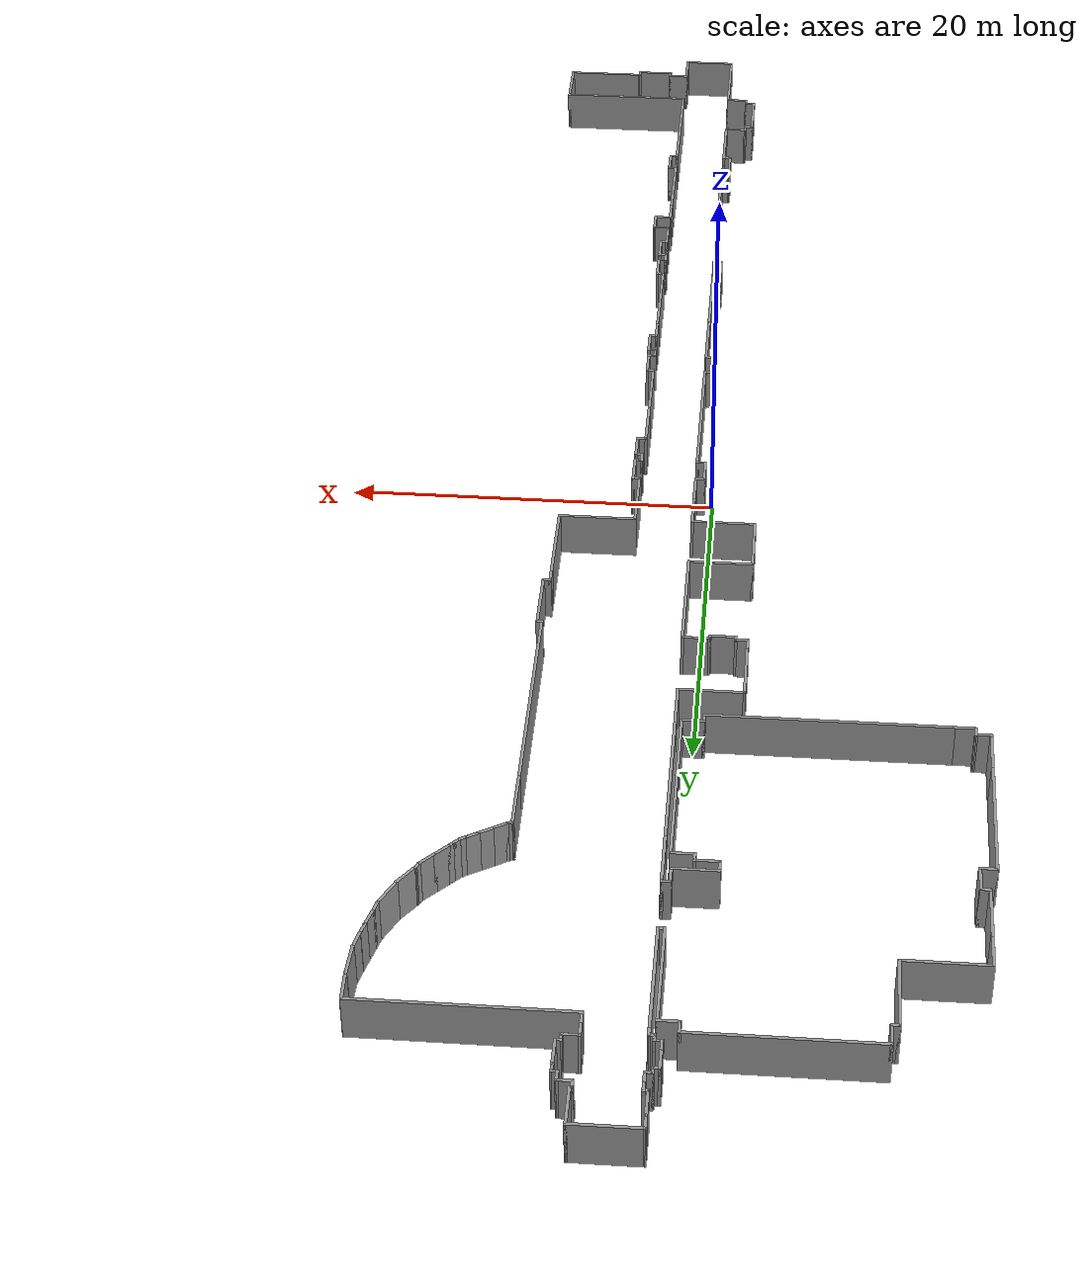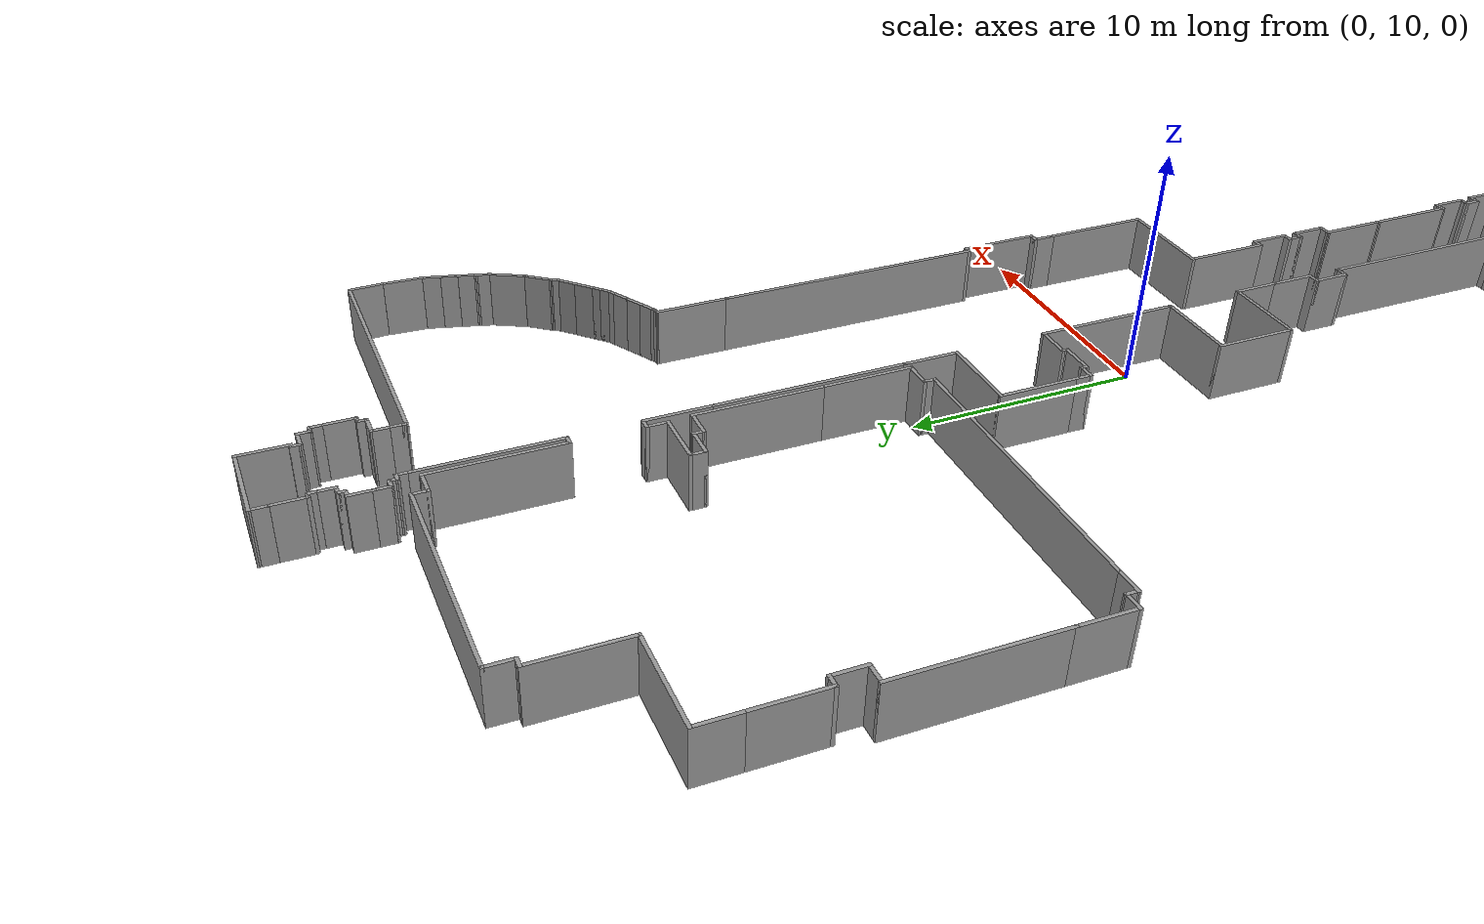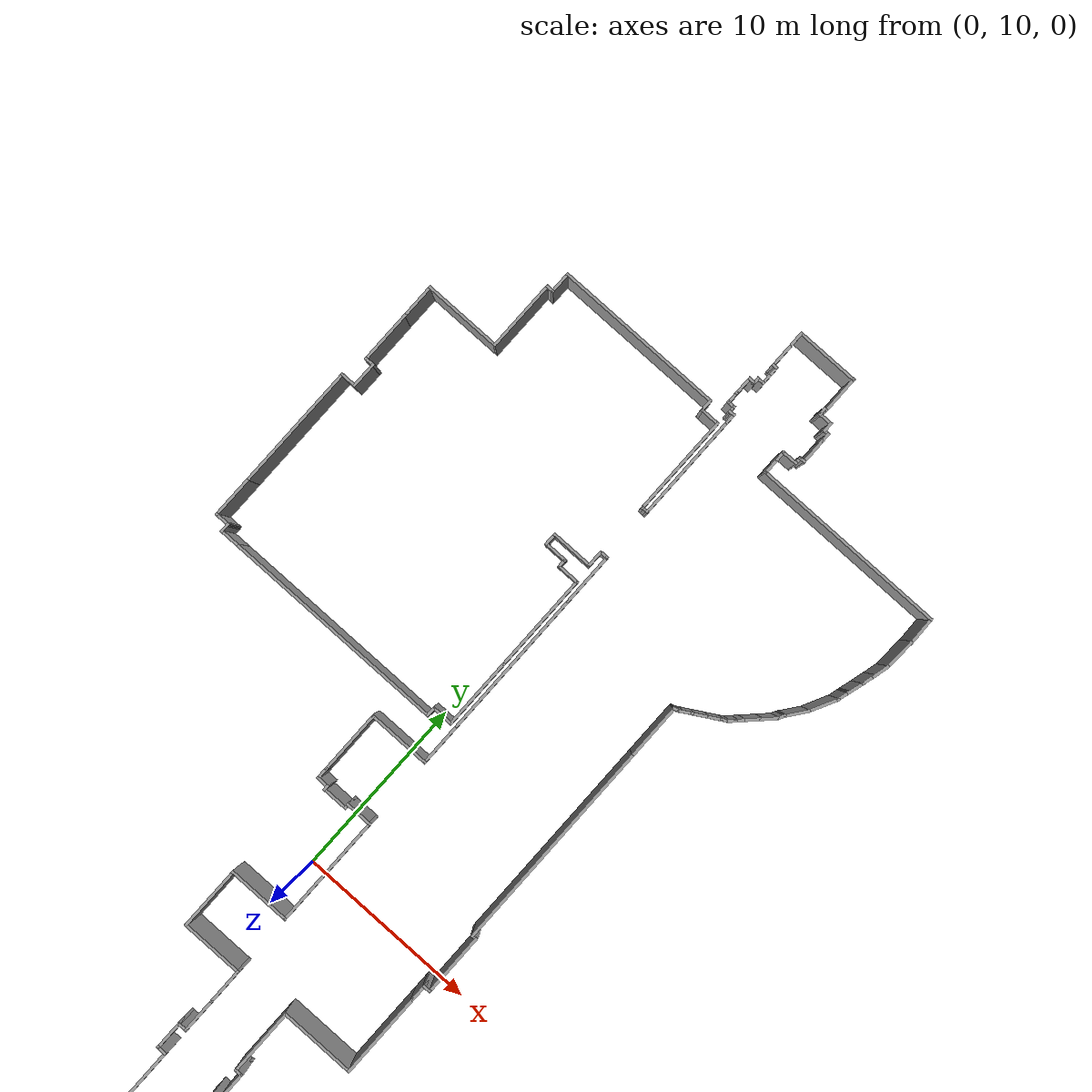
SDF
<?xml version='1.0'?>
<sdf version='1.6'>
  <model name='volen.world'>
    <link name='Wall_100'>
      <pose frame=''>12.7994 31.5829 0 0 0 -2.21664</pose>
      <self_collide>0</self_collide>
      <kinematic>0</kinematic>
      <visual name='Wall_100_Visual'>
        <pose frame=''>0 0 1.25 0 -0 0</pose>
        <geometry>
          <box>
            <size>1.35577 0.15 2.5</size>
          </box>
        </geometry>
        <material>
          <script>
            <uri>file://media/materials/scripts/gazebo.material</uri>
            <name>Gazebo/Grey</name>
          </script>
          <ambient>1 1 1 1</ambient>
          <diffuse>0.7 0.7 0.7 1</diffuse>
          <specular>0.01 0.01 0.01 1</specular>
          <emissive>0 0 0 1</emissive>
        </material>
        <cast_shadows>1</cast_shadows>
        <transparency>0</transparency>
      </visual>
      <collision name='Wall_100_Collision'>
        <laser_retro>0</laser_retro>
        <max_contacts>10</max_contacts>
        <pose frame=''>0 0 1.25 0 -0 0</pose>
        <geometry>
          <box>
            <size>1.35577 0.15 2.5</size>
          </box>
        </geometry>
        <surface>
          <friction>
            <ode>
              <mu>1</mu>
              <mu2>1</mu2>
              <fdir1>0 0 0</fdir1>
              <slip1>0</slip1>
              <slip2>0</slip2>
            </ode>
            <torsional>
              <coefficient>1</coefficient>
              <patch_radius>0</patch_radius>
              <surface_radius>0</surface_radius>
              <use_patch_radius>1</use_patch_radius>
              <ode>
                <slip>0</slip>
              </ode>
            </torsional>
          </friction>
          <bounce>
            <restitution_coefficient>0</restitution_coefficient>
            <threshold>1e+06</threshold>
          </bounce>
          <contact>
            <collide_without_contact>0</collide_without_contact>
            <collide_without_contact_bitmask>1</collide_without_contact_bitmask>
            <collide_bitmask>1</collide_bitmask>
            <ode>
              <soft_cfm>0</soft_cfm>
              <soft_erp>0.2</soft_erp>
              <kp>1e+13</kp>
              <kd>1</kd>
              <max_vel>0.01</max_vel>
              <min_depth>0</min_depth>
            </ode>
            <bullet>
              <split_impulse>1</split_impulse>
              <split_impulse_penetration_threshold>-0.01</split_impulse_penetration_threshold>
              <soft_cfm>0</soft_cfm>
              <soft_erp>0.2</soft_erp>
              <kp>1e+13</kp>
              <kd>1</kd>
            </bullet>
          </contact>
        </surface>
      </collision>
    </link>
    <link name='Wall_101'>
      <pose frame=''>12.349 30.9499 0 0 0 -2.0944</pose>
      <self_collide>0</self_collide>
      <kinematic>0</kinematic>
      <visual name='Wall_101_Visual'>
        <pose frame=''>0 0 1.25 0 -0 0</pose>
        <geometry>
          <box>
            <size>0.5 0.15 2.5</size>
          </box>
        </geometry>
        <material>
          <script>
            <uri>file://media/materials/scripts/gazebo.material</uri>
            <name>Gazebo/Grey</name>
          </script>
          <ambient>1 1 1 1</ambient>
          <diffuse>0.7 0.7 0.7 1</diffuse>
          <specular>0.01 0.01 0.01 1</specular>
          <emissive>0 0 0 1</emissive>
        </material>
        <cast_shadows>1</cast_shadows>
        <transparency>0</transparency>
      </visual>
      <collision name='Wall_101_Collision'>
        <laser_retro>0</laser_retro>
        <max_contacts>10</max_contacts>
        <pose frame=''>0 0 1.25 0 -0 0</pose>
        <geometry>
          <box>
            <size>0.5 0.15 2.5</size>
          </box>
        </geometry>
        <surface>
          <friction>
            <ode>
              <mu>1</mu>
              <mu2>1</mu2>
              <fdir1>0 0 0</fdir1>
              <slip1>0</slip1>
              <slip2>0</slip2>
            </ode>
            <torsional>
              <coefficient>1</coefficient>
              <patch_radius>0</patch_radius>
              <surface_radius>0</surface_radius>
              <use_patch_radius>1</use_patch_radius>
              <ode>
                <slip>0</slip>
              </ode>
            </torsional>
          </friction>
          <bounce>
            <restitution_coefficient>0</restitution_coefficient>
            <threshold>1e+06</threshold>
          </bounce>
          <contact>
            <collide_without_contact>0</collide_without_contact>
            <collide_without_contact_bitmask>1</collide_without_contact_bitmask>
            <collide_bitmask>1</collide_bitmask>
            <ode>
              <soft_cfm>0</soft_cfm>
              <soft_erp>0.2</soft_erp>
              <kp>1e+13</kp>
              <kd>1</kd>
              <max_vel>0.01</max_vel>
              <min_depth>0</min_depth>
            </ode>
            <bullet>
              <split_impulse>1</split_impulse>
              <split_impulse_penetration_threshold>-0.01</split_impulse_penetration_threshold>
              <soft_cfm>0</soft_cfm>
              <soft_erp>0.2</soft_erp>
              <kp>1e+13</kp>
              <kd>1</kd>
            </bullet>
          </contact>
        </surface>
      </collision>
    </link>
    <link name='Wall_102'>
      <pose frame=''>11.961 30.4978 0 0 0 -2.35619</pose>
      <self_collide>0</self_collide>
      <kinematic>0</kinematic>
      <visual name='Wall_102_Visual'>
        <pose frame=''>0 0 1.25 0 -0 0</pose>
        <geometry>
          <box>
            <size>1 0.15 2.5</size>
          </box>
        </geometry>
        <material>
          <script>
            <uri>file://media/materials/scripts/gazebo.material</uri>
            <name>Gazebo/Grey</name>
          </script>
          <ambient>1 1 1 1</ambient>
          <diffuse>0.7 0.7 0.7 1</diffuse>
          <specular>0.01 0.01 0.01 1</specular>
          <emissive>0 0 0 1</emissive>
        </material>
        <cast_shadows>1</cast_shadows>
        <transparency>0</transparency>
      </visual>
      <collision name='Wall_102_Collision'>
        <laser_retro>0</laser_retro>
        <max_contacts>10</max_contacts>
        <pose frame=''>0 0 1.25 0 -0 0</pose>
        <geometry>
          <box>
            <size>1 0.15 2.5</size>
          </box>
        </geometry>
        <surface>
          <friction>
            <ode>
              <mu>1</mu>
              <mu2>1</mu2>
              <fdir1>0 0 0</fdir1>
              <slip1>0</slip1>
              <slip2>0</slip2>
            </ode>
            <torsional>
              <coefficient>1</coefficient>
              <patch_radius>0</patch_radius>
              <surface_radius>0</surface_radius>
              <use_patch_radius>1</use_patch_radius>
              <ode>
                <slip>0</slip>
              </ode>
            </torsional>
          </friction>
          <bounce>
            <restitution_coefficient>0</restitution_coefficient>
            <threshold>1e+06</threshold>
          </bounce>
          <contact>
            <collide_without_contact>0</collide_without_contact>
            <collide_without_contact_bitmask>1</collide_without_contact_bitmask>
            <collide_bitmask>1</collide_bitmask>
            <ode>
              <soft_cfm>0</soft_cfm>
              <soft_erp>0.2</soft_erp>
              <kp>1e+13</kp>
              <kd>1</kd>
              <max_vel>0.01</max_vel>
              <min_depth>0</min_depth>
            </ode>
            <bullet>
              <split_impulse>1</split_impulse>
              <split_impulse_penetration_threshold>-0.01</split_impulse_penetration_threshold>
              <soft_cfm>0</soft_cfm>
              <soft_erp>0.2</soft_erp>
              <kp>1e+13</kp>
              <kd>1</kd>
            </bullet>
          </contact>
        </surface>
      </collision>
    </link>
    <link name='Wall_103'>
      <pose frame=''>11.36 29.8968 0 0 0 -2.35619</pose>
      <self_collide>0</self_collide>
      <kinematic>0</kinematic>
      <visual name='Wall_103_Visual'>
        <pose frame=''>0 0 1.25 0 -0 0</pose>
        <geometry>
          <box>
            <size>1 0.15 2.5</size>
          </box>
        </geometry>
        <material>
          <script>
            <uri>file://media/materials/scripts/gazebo.material</uri>
            <name>Gazebo/Grey</name>
          </script>
          <ambient>1 1 1 1</ambient>
          <diffuse>0.7 0.7 0.7 1</diffuse>
          <specular>0.01 0.01 0.01 1</specular>
          <emissive>0 0 0 1</emissive>
        </material>
        <cast_shadows>1</cast_shadows>
        <transparency>0</transparency>
      </visual>
      <collision name='Wall_103_Collision'>
        <laser_retro>0</laser_retro>
        <max_contacts>10</max_contacts>
        <pose frame=''>0 0 1.25 0 -0 0</pose>
        <geometry>
          <box>
            <size>1 0.15 2.5</size>
          </box>
        </geometry>
        <surface>
          <friction>
            <ode>
              <mu>1</mu>
              <mu2>1</mu2>
              <fdir1>0 0 0</fdir1>
              <slip1>0</slip1>
              <slip2>0</slip2>
            </ode>
            <torsional>
              <coefficient>1</coefficient>
              <patch_radius>0</patch_radius>
              <surface_radius>0</surface_radius>
              <use_patch_radius>1</use_patch_radius>
              <ode>
                <slip>0</slip>
              </ode>
            </torsional>
          </friction>
          <bounce>
            <restitution_coefficient>0</restitution_coefficient>
            <threshold>1e+06</threshold>
          </bounce>
          <contact>
            <collide_without_contact>0</collide_without_contact>
            <collide_without_contact_bitmask>1</collide_without_contact_bitmask>
            <collide_bitmask>1</collide_bitmask>
            <ode>
              <soft_cfm>0</soft_cfm>
              <soft_erp>0.2</soft_erp>
              <kp>1e+13</kp>
              <kd>1</kd>
              <max_vel>0.01</max_vel>
              <min_depth>0</min_depth>
            </ode>
            <bullet>
              <split_impulse>1</split_impulse>
              <split_impulse_penetration_threshold>-0.01</split_impulse_penetration_threshold>
              <soft_cfm>0</soft_cfm>
              <soft_erp>0.2</soft_erp>
              <kp>1e+13</kp>
              <kd>1</kd>
            </bullet>
          </contact>
        </surface>
      </collision>
    </link>
    <link name='Wall_104'>
      <pose frame=''>10.9357 29.4725 0 0 0 -2.35619</pose>
      <self_collide>0</self_collide>
      <kinematic>0</kinematic>
      <visual name='Wall_104_Visual'>
        <pose frame=''>0 0 1.25 0 -0 0</pose>
        <geometry>
          <box>
            <size>0.5 0.15 2.5</size>
          </box>
        </geometry>
        <material>
          <script>
            <uri>file://media/materials/scripts/gazebo.material</uri>
            <name>Gazebo/Grey</name>
          </script>
          <ambient>1 1 1 1</ambient>
          <diffuse>0.7 0.7 0.7 1</diffuse>
          <specular>0.01 0.01 0.01 1</specular>
          <emissive>0 0 0 1</emissive>
        </material>
        <cast_shadows>1</cast_shadows>
        <transparency>0</transparency>
      </visual>
      <collision name='Wall_104_Collision'>
        <laser_retro>0</laser_retro>
        <max_contacts>10</max_contacts>
        <pose frame=''>0 0 1.25 0 -0 0</pose>
        <geometry>
          <box>
            <size>0.5 0.15 2.5</size>
          </box>
        </geometry>
        <surface>
          <friction>
            <ode>
              <mu>1</mu>
              <mu2>1</mu2>
              <fdir1>0 0 0</fdir1>
              <slip1>0</slip1>
              <slip2>0</slip2>
            </ode>
            <torsional>
              <coefficient>1</coefficient>
              <patch_radius>0</patch_radius>
              <surface_radius>0</surface_radius>
              <use_patch_radius>1</use_patch_radius>
              <ode>
                <slip>0</slip>
              </ode>
            </torsional>
          </friction>
          <bounce>
            <restitution_coefficient>0</restitution_coefficient>
            <threshold>1e+06</threshold>
          </bounce>
          <contact>
            <collide_without_contact>0</collide_without_contact>
            <collide_without_contact_bitmask>1</collide_without_contact_bitmask>
            <collide_bitmask>1</collide_bitmask>
            <ode>
              <soft_cfm>0</soft_cfm>
              <soft_erp>0.2</soft_erp>
              <kp>1e+13</kp>
              <kd>1</kd>
              <max_vel>0.01</max_vel>
              <min_depth>0</min_depth>
            </ode>
            <bullet>
              <split_impulse>1</split_impulse>
              <split_impulse_penetration_threshold>-0.01</split_impulse_penetration_threshold>
              <soft_cfm>0</soft_cfm>
              <soft_erp>0.2</soft_erp>
              <kp>1e+13</kp>
              <kd>1</kd>
            </bullet>
          </contact>
        </surface>
      </collision>
    </link>
    <link name='Wall_105'>
      <pose frame=''>10.6882 29.225 0 0 0 -2.35619</pose>
      <self_collide>0</self_collide>
      <kinematic>0</kinematic>
      <visual name='Wall_105_Visual'>
        <pose frame=''>0 0 1.25 0 -0 0</pose>
        <geometry>
          <box>
            <size>0.5 0.15 2.5</size>
          </box>
        </geometry>
        <material>
          <script>
            <uri>file://media/materials/scripts/gazebo.material</uri>
            <name>Gazebo/Grey</name>
          </script>
          <ambient>1 1 1 1</ambient>
          <diffuse>0.7 0.7 0.7 1</diffuse>
          <specular>0.01 0.01 0.01 1</specular>
          <emissive>0 0 0 1</emissive>
        </material>
        <cast_shadows>1</cast_shadows>
        <transparency>0</transparency>
      </visual>
      <collision name='Wall_105_Collision'>
        <laser_retro>0</laser_retro>
        <max_contacts>10</max_contacts>
        <pose frame=''>0 0 1.25 0 -0 0</pose>
        <geometry>
          <box>
            <size>0.5 0.15 2.5</size>
          </box>
        </geometry>
        <surface>
          <friction>
            <ode>
              <mu>1</mu>
              <mu2>1</mu2>
              <fdir1>0 0 0</fdir1>
              <slip1>0</slip1>
              <slip2>0</slip2>
            </ode>
            <torsional>
              <coefficient>1</coefficient>
              <patch_radius>0</patch_radius>
              <surface_radius>0</surface_radius>
              <use_patch_radius>1</use_patch_radius>
              <ode>
                <slip>0</slip>
              </ode>
            </torsional>
          </friction>
          <bounce>
            <restitution_coefficient>0</restitution_coefficient>
            <threshold>1e+06</threshold>
          </bounce>
          <contact>
            <collide_without_contact>0</collide_without_contact>
            <collide_without_contact_bitmask>1</collide_without_contact_bitmask>
            <collide_bitmask>1</collide_bitmask>
            <ode>
              <soft_cfm>0</soft_cfm>
              <soft_erp>0.2</soft_erp>
              <kp>1e+13</kp>
              <kd>1</kd>
              <max_vel>0.01</max_vel>
              <min_depth>0</min_depth>
            </ode>
            <bullet>
              <split_impulse>1</split_impulse>
              <split_impulse_penetration_threshold>-0.01</split_impulse_penetration_threshold>
              <soft_cfm>0</soft_cfm>
              <soft_erp>0.2</soft_erp>
              <kp>1e+13</kp>
              <kd>1</kd>
            </bullet>
          </contact>
        </surface>
      </collision>
    </link>
    <link name='Wall_106'>
      <pose frame=''>10.4129 29.0138 0 0 0 -2.61799</pose>
      <self_collide>0</self_collide>
      <kinematic>0</kinematic>
      <visual name='Wall_106_Visual'>
        <pose frame=''>0 0 1.25 0 -0 0</pose>
        <geometry>
          <box>
            <size>0.5 0.15 2.5</size>
          </box>
        </geometry>
        <material>
          <script>
            <uri>file://media/materials/scripts/gazebo.material</uri>
            <name>Gazebo/Grey</name>
          </script>
          <ambient>1 1 1 1</ambient>
          <diffuse>0.7 0.7 0.7 1</diffuse>
          <specular>0.01 0.01 0.01 1</specular>
          <emissive>0 0 0 1</emissive>
        </material>
        <cast_shadows>1</cast_shadows>
        <transparency>0</transparency>
      </visual>
      <collision name='Wall_106_Collision'>
        <laser_retro>0</laser_retro>
        <max_contacts>10</max_contacts>
        <pose frame=''>0 0 1.25 0 -0 0</pose>
        <geometry>
          <box>
            <size>0.5 0.15 2.5</size>
          </box>
        </geometry>
        <surface>
          <friction>
            <ode>
              <mu>1</mu>
              <mu2>1</mu2>
              <fdir1>0 0 0</fdir1>
              <slip1>0</slip1>
              <slip2>0</slip2>
            </ode>
            <torsional>
              <coefficient>1</coefficient>
              <patch_radius>0</patch_radius>
              <surface_radius>0</surface_radius>
              <use_patch_radius>1</use_patch_radius>
              <ode>
                <slip>0</slip>
              </ode>
            </torsional>
          </friction>
          <bounce>
            <restitution_coefficient>0</restitution_coefficient>
            <threshold>1e+06</threshold>
          </bounce>
          <contact>
            <collide_without_contact>0</collide_without_contact>
            <collide_without_contact_bitmask>1</collide_without_contact_bitmask>
            <collide_bitmask>1</collide_bitmask>
            <ode>
              <soft_cfm>0</soft_cfm>
              <soft_erp>0.2</soft_erp>
              <kp>1e+13</kp>
              <kd>1</kd>
              <max_vel>0.01</max_vel>
              <min_depth>0</min_depth>
            </ode>
            <bullet>
              <split_impulse>1</split_impulse>
              <split_impulse_penetration_threshold>-0.01</split_impulse_penetration_threshold>
              <soft_cfm>0</soft_cfm>
              <soft_erp>0.2</soft_erp>
              <kp>1e+13</kp>
              <kd>1</kd>
            </bullet>
          </contact>
        </surface>
      </collision>
    </link>
    <link name='Wall_108'>
      <pose frame=''>10.0015 28.7763 0 0 0 -2.61799</pose>
      <self_collide>0</self_collide>
      <kinematic>0</kinematic>
      <visual name='Wall_108_Visual'>
        <pose frame=''>0 0 1.25 0 -0 0</pose>
        <geometry>
          <box>
            <size>0.75 0.15 2.5</size>
          </box>
        </geometry>
        <material>
          <script>
            <uri>file://media/materials/scripts/gazebo.material</uri>
            <name>Gazebo/Grey</name>
          </script>
          <ambient>1 1 1 1</ambient>
          <diffuse>0.7 0.7 0.7 1</diffuse>
          <specular>0.01 0.01 0.01 1</specular>
          <emissive>0 0 0 1</emissive>
        </material>
        <cast_shadows>1</cast_shadows>
        <transparency>0</transparency>
      </visual>
      <collision name='Wall_108_Collision'>
        <laser_retro>0</laser_retro>
        <max_contacts>10</max_contacts>
        <pose frame=''>0 0 1.25 0 -0 0</pose>
        <geometry>
          <box>
            <size>0.75 0.15 2.5</size>
          </box>
        </geometry>
        <surface>
          <friction>
            <ode>
              <mu>1</mu>
              <mu2>1</mu2>
              <fdir1>0 0 0</fdir1>
              <slip1>0</slip1>
              <slip2>0</slip2>
            </ode>
            <torsional>
              <coefficient>1</coefficient>
              <patch_radius>0</patch_radius>
              <surface_radius>0</surface_radius>
              <use_patch_radius>1</use_patch_radius>
              <ode>
                <slip>0</slip>
              </ode>
            </torsional>
          </friction>
          <bounce>
            <restitution_coefficient>0</restitution_coefficient>
            <threshold>1e+06</threshold>
          </bounce>
          <contact>
            <collide_without_contact>0</collide_without_contact>
            <collide_without_contact_bitmask>1</collide_without_contact_bitmask>
            <collide_bitmask>1</collide_bitmask>
            <ode>
              <soft_cfm>0</soft_cfm>
              <soft_erp>0.2</soft_erp>
              <kp>1e+13</kp>
              <kd>1</kd>
              <max_vel>0.01</max_vel>
              <min_depth>0</min_depth>
            </ode>
            <bullet>
              <split_impulse>1</split_impulse>
              <split_impulse_penetration_threshold>-0.01</split_impulse_penetration_threshold>
              <soft_cfm>0</soft_cfm>
              <soft_erp>0.2</soft_erp>
              <kp>1e+13</kp>
              <kd>1</kd>
            </bullet>
          </contact>
        </surface>
      </collision>
    </link>
    <link name='Wall_109'>
      <pose frame=''>9.37367 28.4138 0 0 0 -2.61799</pose>
      <self_collide>0</self_collide>
      <kinematic>0</kinematic>
      <visual name='Wall_109_Visual'>
        <pose frame=''>0 0 1.25 0 -0 0</pose>
        <geometry>
          <box>
            <size>1 0.15 2.5</size>
          </box>
        </geometry>
        <material>
          <script>
            <uri>file://media/materials/scripts/gazebo.material</uri>
            <name>Gazebo/Grey</name>
          </script>
          <ambient>1 1 1 1</ambient>
          <diffuse>0.7 0.7 0.7 1</diffuse>
          <specular>0.01 0.01 0.01 1</specular>
          <emissive>0 0 0 1</emissive>
        </material>
        <cast_shadows>1</cast_shadows>
        <transparency>0</transparency>
      </visual>
      <collision name='Wall_109_Collision'>
        <laser_retro>0</laser_retro>
        <max_contacts>10</max_contacts>
        <pose frame=''>0 0 1.25 0 -0 0</pose>
        <geometry>
          <box>
            <size>1 0.15 2.5</size>
          </box>
        </geometry>
        <surface>
          <friction>
            <ode>
              <mu>1</mu>
              <mu2>1</mu2>
              <fdir1>0 0 0</fdir1>
              <slip1>0</slip1>
              <slip2>0</slip2>
            </ode>
            <torsional>
              <coefficient>1</coefficient>
              <patch_radius>0</patch_radius>
              <surface_radius>0</surface_radius>
              <use_patch_radius>1</use_patch_radius>
              <ode>
                <slip>0</slip>
              </ode>
            </torsional>
          </friction>
          <bounce>
            <restitution_coefficient>0</restitution_coefficient>
            <threshold>1e+06</threshold>
          </bounce>
          <contact>
            <collide_without_contact>0</collide_without_contact>
            <collide_without_contact_bitmask>1</collide_without_contact_bitmask>
            <collide_bitmask>1</collide_bitmask>
            <ode>
              <soft_cfm>0</soft_cfm>
              <soft_erp>0.2</soft_erp>
              <kp>1e+13</kp>
              <kd>1</kd>
              <max_vel>0.01</max_vel>
              <min_depth>0</min_depth>
            </ode>
            <bullet>
              <split_impulse>1</split_impulse>
              <split_impulse_penetration_threshold>-0.01</split_impulse_penetration_threshold>
              <soft_cfm>0</soft_cfm>
              <soft_erp>0.2</soft_erp>
              <kp>1e+13</kp>
              <kd>1</kd>
            </bullet>
          </contact>
        </surface>
      </collision>
    </link>
    <link name='Wall_110'>
      <pose frame=''>8.7458 28.0513 0 0 0 -2.61799</pose>
      <self_collide>0</self_collide>
      <kinematic>0</kinematic>
      <visual name='Wall_110_Visual'>
        <pose frame=''>0 0 1.25 0 -0 0</pose>
        <geometry>
          <box>
            <size>0.75 0.15 2.5</size>
          </box>
        </geometry>
        <material>
          <script>
            <uri>file://media/materials/scripts/gazebo.material</uri>
            <name>Gazebo/Grey</name>
          </script>
          <ambient>1 1 1 1</ambient>
          <diffuse>0.7 0.7 0.7 1</diffuse>
          <specular>0.01 0.01 0.01 1</specular>
          <emissive>0 0 0 1</emissive>
        </material>
        <cast_shadows>1</cast_shadows>
        <transparency>0</transparency>
      </visual>
      <collision name='Wall_110_Collision'>
        <laser_retro>0</laser_retro>
        <max_contacts>10</max_contacts>
        <pose frame=''>0 0 1.25 0 -0 0</pose>
        <geometry>
          <box>
            <size>0.75 0.15 2.5</size>
          </box>
        </geometry>
        <surface>
          <friction>
            <ode>
              <mu>1</mu>
              <mu2>1</mu2>
              <fdir1>0 0 0</fdir1>
              <slip1>0</slip1>
              <slip2>0</slip2>
            </ode>
            <torsional>
              <coefficient>1</coefficient>
              <patch_radius>0</patch_radius>
              <surface_radius>0</surface_radius>
              <use_patch_radius>1</use_patch_radius>
              <ode>
                <slip>0</slip>
              </ode>
            </torsional>
          </friction>
          <bounce>
            <restitution_coefficient>0</restitution_coefficient>
            <threshold>1e+06</threshold>
          </bounce>
          <contact>
            <collide_without_contact>0</collide_without_contact>
            <collide_without_contact_bitmask>1</collide_without_contact_bitmask>
            <collide_bitmask>1</collide_bitmask>
            <ode>
              <soft_cfm>0</soft_cfm>
              <soft_erp>0.2</soft_erp>
              <kp>1e+13</kp>
              <kd>1</kd>
              <max_vel>0.01</max_vel>
              <min_depth>0</min_depth>
            </ode>
            <bullet>
              <split_impulse>1</split_impulse>
              <split_impulse_penetration_threshold>-0.01</split_impulse_penetration_threshold>
              <soft_cfm>0</soft_cfm>
              <soft_erp>0.2</soft_erp>
              <kp>1e+13</kp>
              <kd>1</kd>
            </bullet>
          </contact>
        </surface>
      </collision>
    </link>
    <link name='Wall_111'>
      <pose frame=''>8.44269 27.8763 0 0 0 -2.61799</pose>
      <self_collide>0</self_collide>
      <kinematic>0</kinematic>
      <visual name='Wall_111_Visual'>
        <pose frame=''>0 0 1.25 0 -0 0</pose>
        <geometry>
          <box>
            <size>0.25 0.15 2.5</size>
          </box>
        </geometry>
        <material>
          <script>
            <uri>file://media/materials/scripts/gazebo.material</uri>
            <name>Gazebo/Grey</name>
          </script>
          <ambient>1 1 1 1</ambient>
          <diffuse>0.7 0.7 0.7 1</diffuse>
          <specular>0.01 0.01 0.01 1</specular>
          <emissive>0 0 0 1</emissive>
        </material>
        <cast_shadows>1</cast_shadows>
        <transparency>0</transparency>
      </visual>
      <collision name='Wall_111_Collision'>
        <laser_retro>0</laser_retro>
        <max_contacts>10</max_contacts>
        <pose frame=''>0 0 1.25 0 -0 0</pose>
        <geometry>
          <box>
            <size>0.25 0.15 2.5</size>
          </box>
        </geometry>
        <surface>
          <friction>
            <ode>
              <mu>1</mu>
              <mu2>1</mu2>
              <fdir1>0 0 0</fdir1>
              <slip1>0</slip1>
              <slip2>0</slip2>
            </ode>
            <torsional>
              <coefficient>1</coefficient>
              <patch_radius>0</patch_radius>
              <surface_radius>0</surface_radius>
              <use_patch_radius>1</use_patch_radius>
              <ode>
                <slip>0</slip>
              </ode>
            </torsional>
          </friction>
          <bounce>
            <restitution_coefficient>0</restitution_coefficient>
            <threshold>1e+06</threshold>
          </bounce>
          <contact>
            <collide_without_contact>0</collide_without_contact>
            <collide_without_contact_bitmask>1</collide_without_contact_bitmask>
            <collide_bitmask>1</collide_bitmask>
            <ode>
              <soft_cfm>0</soft_cfm>
              <soft_erp>0.2</soft_erp>
              <kp>1e+13</kp>
              <kd>1</kd>
              <max_vel>0.01</max_vel>
              <min_depth>0</min_depth>
            </ode>
            <bullet>
              <split_impulse>1</split_impulse>
              <split_impulse_penetration_threshold>-0.01</split_impulse_penetration_threshold>
              <soft_cfm>0</soft_cfm>
              <soft_erp>0.2</soft_erp>
              <kp>1e+13</kp>
              <kd>1</kd>
            </bullet>
          </contact>
        </surface>
      </collision>
    </link>
    <link name='Wall_112'>
      <pose frame=''>8.3511 27.8383 0 0 0 -2.87979</pose>
      <self_collide>0</self_collide>
      <kinematic>0</kinematic>
      <visual name='Wall_112_Visual'>
        <pose frame=''>0 0 1.25 0 -0 0</pose>
        <geometry>
          <box>
            <size>0.25 0.15 2.5</size>
          </box>
        </geometry>
        <material>
          <script>
            <uri>file://media/materials/scripts/gazebo.material</uri>
            <name>Gazebo/Grey</name>
          </script>
          <ambient>1 1 1 1</ambient>
          <diffuse>0.7 0.7 0.7 1</diffuse>
          <specular>0.01 0.01 0.01 1</specular>
          <emissive>0 0 0 1</emissive>
        </material>
        <cast_shadows>1</cast_shadows>
        <transparency>0</transparency>
      </visual>
      <collision name='Wall_112_Collision'>
        <laser_retro>0</laser_retro>
        <max_contacts>10</max_contacts>
        <pose frame=''>0 0 1.25 0 -0 0</pose>
        <geometry>
          <box>
            <size>0.25 0.15 2.5</size>
          </box>
        </geometry>
        <surface>
          <friction>
            <ode>
              <mu>1</mu>
              <mu2>1</mu2>
              <fdir1>0 0 0</fdir1>
              <slip1>0</slip1>
              <slip2>0</slip2>
            </ode>
            <torsional>
              <coefficient>1</coefficient>
              <patch_radius>0</patch_radius>
              <surface_radius>0</surface_radius>
              <use_patch_radius>1</use_patch_radius>
              <ode>
                <slip>0</slip>
              </ode>
            </torsional>
          </friction>
          <bounce>
            <restitution_coefficient>0</restitution_coefficient>
            <threshold>1e+06</threshold>
          </bounce>
          <contact>
            <collide_without_contact>0</collide_without_contact>
            <collide_without_contact_bitmask>1</collide_without_contact_bitmask>
            <collide_bitmask>1</collide_bitmask>
            <ode>
              <soft_cfm>0</soft_cfm>
              <soft_erp>0.2</soft_erp>
              <kp>1e+13</kp>
              <kd>1</kd>
              <max_vel>0.01</max_vel>
              <min_depth>0</min_depth>
            </ode>
            <bullet>
              <split_impulse>1</split_impulse>
              <split_impulse_penetration_threshold>-0.01</split_impulse_penetration_threshold>
              <soft_cfm>0</soft_cfm>
              <soft_erp>0.2</soft_erp>
              <kp>1e+13</kp>
              <kd>1</kd>
            </bullet>
          </contact>
        </surface>
      </collision>
    </link>
    <link name='Wall_113'>
      <pose frame=''>8.2545 27.8124 0 0 0 -2.87979</pose>
      <self_collide>0</self_collide>
      <kinematic>0</kinematic>
      <visual name='Wall_113_Visual'>
        <pose frame=''>0 0 1.25 0 -0 0</pose>
        <geometry>
          <box>
            <size>0.25 0.15 2.5</size>
          </box>
        </geometry>
        <material>
          <script>
            <uri>file://media/materials/scripts/gazebo.material</uri>
            <name>Gazebo/Grey</name>
          </script>
          <ambient>1 1 1 1</ambient>
          <diffuse>0.7 0.7 0.7 1</diffuse>
          <specular>0.01 0.01 0.01 1</specular>
          <emissive>0 0 0 1</emissive>
        </material>
        <cast_shadows>1</cast_shadows>
        <transparency>0</transparency>
      </visual>
      <collision name='Wall_113_Collision'>
        <laser_retro>0</laser_retro>
        <max_contacts>10</max_contacts>
        <pose frame=''>0 0 1.25 0 -0 0</pose>
        <geometry>
          <box>
            <size>0.25 0.15 2.5</size>
          </box>
        </geometry>
        <surface>
          <friction>
            <ode>
              <mu>1</mu>
              <mu2>1</mu2>
              <fdir1>0 0 0</fdir1>
              <slip1>0</slip1>
              <slip2>0</slip2>
            </ode>
            <torsional>
              <coefficient>1</coefficient>
              <patch_radius>0</patch_radius>
              <surface_radius>0</surface_radius>
              <use_patch_radius>1</use_patch_radius>
              <ode>
                <slip>0</slip>
              </ode>
            </torsional>
          </friction>
          <bounce>
            <restitution_coefficient>0</restitution_coefficient>
            <threshold>1e+06</threshold>
          </bounce>
          <contact>
            <collide_without_contact>0</collide_without_contact>
            <collide_without_contact_bitmask>1</collide_without_contact_bitmask>
            <collide_bitmask>1</collide_bitmask>
            <ode>
              <soft_cfm>0</soft_cfm>
              <soft_erp>0.2</soft_erp>
              <kp>1e+13</kp>
              <kd>1</kd>
              <max_vel>0.01</max_vel>
              <min_depth>0</min_depth>
            </ode>
            <bullet>
              <split_impulse>1</split_impulse>
              <split_impulse_penetration_threshold>-0.01</split_impulse_penetration_threshold>
              <soft_cfm>0</soft_cfm>
              <soft_erp>0.2</soft_erp>
              <kp>1e+13</kp>
              <kd>1</kd>
            </bullet>
          </contact>
        </surface>
      </collision>
    </link>
    <link name='Wall_114'>
      <pose frame=''>8.20621 26.2495 0 0 0 -1.5708</pose>
      <self_collide>0</self_collide>
      <kinematic>0</kinematic>
      <visual name='Wall_114_Visual'>
        <pose frame=''>0 0 1.25 0 -0 0</pose>
        <geometry>
          <box>
            <size>3.25 0.15 2.5</size>
          </box>
        </geometry>
        <material>
          <script>
            <uri>file://media/materials/scripts/gazebo.material</uri>
            <name>Gazebo/Grey</name>
          </script>
          <ambient>1 1 1 1</ambient>
          <diffuse>0.7 0.7 0.7 1</diffuse>
          <specular>0.01 0.01 0.01 1</specular>
          <emissive>0 0 0 1</emissive>
        </material>
        <cast_shadows>1</cast_shadows>
        <transparency>0</transparency>
      </visual>
      <collision name='Wall_114_Collision'>
        <laser_retro>0</laser_retro>
        <max_contacts>10</max_contacts>
        <pose frame=''>0 0 1.25 0 -0 0</pose>
        <geometry>
          <box>
            <size>3.25 0.15 2.5</size>
          </box>
        </geometry>
        <surface>
          <friction>
            <ode>
              <mu>1</mu>
              <mu2>1</mu2>
              <fdir1>0 0 0</fdir1>
              <slip1>0</slip1>
              <slip2>0</slip2>
            </ode>
            <torsional>
              <coefficient>1</coefficient>
              <patch_radius>0</patch_radius>
              <surface_radius>0</surface_radius>
              <use_patch_radius>1</use_patch_radius>
              <ode>
                <slip>0</slip>
              </ode>
            </torsional>
          </friction>
          <bounce>
            <restitution_coefficient>0</restitution_coefficient>
            <threshold>1e+06</threshold>
          </bounce>
          <contact>
            <collide_without_contact>0</collide_without_contact>
            <collide_without_contact_bitmask>1</collide_without_contact_bitmask>
            <collide_bitmask>1</collide_bitmask>
            <ode>
              <soft_cfm>0</soft_cfm>
              <soft_erp>0.2</soft_erp>
              <kp>1e+13</kp>
              <kd>1</kd>
              <max_vel>0.01</max_vel>
              <min_depth>0</min_depth>
            </ode>
            <bullet>
              <split_impulse>1</split_impulse>
              <split_impulse_penetration_threshold>-0.01</split_impulse_penetration_threshold>
              <soft_cfm>0</soft_cfm>
              <soft_erp>0.2</soft_erp>
              <kp>1e+13</kp>
              <kd>1</kd>
            </bullet>
          </contact>
        </surface>
      </collision>
    </link>
    <link name='Wall_116'>
      <pose frame=''>8.20622 18.8994 0 0 0 -1.57079</pose>
      <self_collide>0</self_collide>
      <kinematic>0</kinematic>
      <visual name='Wall_116_Visual'>
        <pose frame=''>0 0 1.25 0 -0 0</pose>
        <geometry>
          <box>
            <size>11.75 0.15 2.5</size>
          </box>
        </geometry>
        <material>
          <script>
            <uri>file://media/materials/scripts/gazebo.material</uri>
            <name>Gazebo/Grey</name>
          </script>
          <ambient>1 1 1 1</ambient>
          <diffuse>0.7 0.7 0.7 1</diffuse>
          <specular>0.01 0.01 0.01 1</specular>
          <emissive>0 0 0 1</emissive>
        </material>
        <cast_shadows>1</cast_shadows>
        <transparency>0</transparency>
      </visual>
      <collision name='Wall_116_Collision'>
        <laser_retro>0</laser_retro>
        <max_contacts>10</max_contacts>
        <pose frame=''>0 0 1.25 0 -0 0</pose>
        <geometry>
          <box>
            <size>11.75 0.15 2.5</size>
          </box>
        </geometry>
        <surface>
          <friction>
            <ode>
              <mu>1</mu>
              <mu2>1</mu2>
              <fdir1>0 0 0</fdir1>
              <slip1>0</slip1>
              <slip2>0</slip2>
            </ode>
            <torsional>
              <coefficient>1</coefficient>
              <patch_radius>0</patch_radius>
              <surface_radius>0</surface_radius>
              <use_patch_radius>1</use_patch_radius>
              <ode>
                <slip>0</slip>
              </ode>
            </torsional>
          </friction>
          <bounce>
            <restitution_coefficient>0</restitution_coefficient>
            <threshold>1e+06</threshold>
          </bounce>
          <contact>
            <collide_without_contact>0</collide_without_contact>
            <collide_without_contact_bitmask>1</collide_without_contact_bitmask>
            <collide_bitmask>1</collide_bitmask>
            <ode>
              <soft_cfm>0</soft_cfm>
              <soft_erp>0.2</soft_erp>
              <kp>1e+13</kp>
              <kd>1</kd>
              <max_vel>0.01</max_vel>
              <min_depth>0</min_depth>
            </ode>
            <bullet>
              <split_impulse>1</split_impulse>
              <split_impulse_penetration_threshold>-0.01</split_impulse_penetration_threshold>
              <soft_cfm>0</soft_cfm>
              <soft_erp>0.2</soft_erp>
              <kp>1e+13</kp>
              <kd>1</kd>
            </bullet>
          </contact>
        </surface>
      </collision>
    </link>
    <link name='Wall_118'>
      <pose frame=''>8.32123 13.0994 0 0 -0 0</pose>
      <self_collide>0</self_collide>
      <kinematic>0</kinematic>
      <visual name='Wall_118_Visual'>
        <pose frame=''>0 0 1.25 0 -0 0</pose>
        <geometry>
          <box>
            <size>0.38 0.15 2.5</size>
          </box>
        </geometry>
        <material>
          <script>
            <uri>file://media/materials/scripts/gazebo.material</uri>
            <name>Gazebo/Grey</name>
          </script>
          <ambient>1 1 1 1</ambient>
          <diffuse>0.7 0.7 0.7 1</diffuse>
          <specular>0.01 0.01 0.01 1</specular>
          <emissive>0 0 0 1</emissive>
        </material>
        <cast_shadows>1</cast_shadows>
        <transparency>0</transparency>
      </visual>
      <collision name='Wall_118_Collision'>
        <laser_retro>0</laser_retro>
        <max_contacts>10</max_contacts>
        <pose frame=''>0 0 1.25 0 -0 0</pose>
        <geometry>
          <box>
            <size>0.38 0.15 2.5</size>
          </box>
        </geometry>
        <surface>
          <friction>
            <ode>
              <mu>1</mu>
              <mu2>1</mu2>
              <fdir1>0 0 0</fdir1>
              <slip1>0</slip1>
              <slip2>0</slip2>
            </ode>
            <torsional>
              <coefficient>1</coefficient>
              <patch_radius>0</patch_radius>
              <surface_radius>0</surface_radius>
              <use_patch_radius>1</use_patch_radius>
              <ode>
                <slip>0</slip>
              </ode>
            </torsional>
          </friction>
          <bounce>
            <restitution_coefficient>0</restitution_coefficient>
            <threshold>1e+06</threshold>
          </bounce>
          <contact>
            <collide_without_contact>0</collide_without_contact>
            <collide_without_contact_bitmask>1</collide_without_contact_bitmask>
            <collide_bitmask>1</collide_bitmask>
            <ode>
              <soft_cfm>0</soft_cfm>
              <soft_erp>0.2</soft_erp>
              <kp>1e+13</kp>
              <kd>1</kd>
              <max_vel>0.01</max_vel>
              <min_depth>0</min_depth>
            </ode>
            <bullet>
              <split_impulse>1</split_impulse>
              <split_impulse_penetration_threshold>-0.01</split_impulse_penetration_threshold>
              <soft_cfm>0</soft_cfm>
              <soft_erp>0.2</soft_erp>
              <kp>1e+13</kp>
              <kd>1</kd>
            </bullet>
          </contact>
        </surface>
      </collision>
    </link>
    <link name='Wall_121'>
      <pose frame=''>8.43623 11.4244 0 0 0 -1.5708</pose>
      <self_collide>0</self_collide>
      <kinematic>0</kinematic>
      <visual name='Wall_121_Visual'>
        <pose frame=''>0 0 1.25 0 -0 0</pose>
        <geometry>
          <box>
            <size>3.5 0.15 2.5</size>
          </box>
        </geometry>
        <material>
          <script>
            <uri>file://media/materials/scripts/gazebo.material</uri>
            <name>Gazebo/Grey</name>
          </script>
          <ambient>1 1 1 1</ambient>
          <diffuse>0.7 0.7 0.7 1</diffuse>
          <specular>0.01 0.01 0.01 1</specular>
          <emissive>0 0 0 1</emissive>
        </material>
        <cast_shadows>1</cast_shadows>
        <transparency>0</transparency>
      </visual>
      <collision name='Wall_121_Collision'>
        <laser_retro>0</laser_retro>
        <max_contacts>10</max_contacts>
        <pose frame=''>0 0 1.25 0 -0 0</pose>
        <geometry>
          <box>
            <size>3.5 0.15 2.5</size>
          </box>
        </geometry>
        <surface>
          <friction>
            <ode>
              <mu>1</mu>
              <mu2>1</mu2>
              <fdir1>0 0 0</fdir1>
              <slip1>0</slip1>
              <slip2>0</slip2>
            </ode>
            <torsional>
              <coefficient>1</coefficient>
              <patch_radius>0</patch_radius>
              <surface_radius>0</surface_radius>
              <use_patch_radius>1</use_patch_radius>
              <ode>
                <slip>0</slip>
              </ode>
            </torsional>
          </friction>
          <bounce>
            <restitution_coefficient>0</restitution_coefficient>
            <threshold>1e+06</threshold>
          </bounce>
          <contact>
            <collide_without_contact>0</collide_without_contact>
            <collide_without_contact_bitmask>1</collide_without_contact_bitmask>
            <collide_bitmask>1</collide_bitmask>
            <ode>
              <soft_cfm>0</soft_cfm>
              <soft_erp>0.2</soft_erp>
              <kp>1e+13</kp>
              <kd>1</kd>
              <max_vel>0.01</max_vel>
              <min_depth>0</min_depth>
            </ode>
            <bullet>
              <split_impulse>1</split_impulse>
              <split_impulse_penetration_threshold>-0.01</split_impulse_penetration_threshold>
              <soft_cfm>0</soft_cfm>
              <soft_erp>0.2</soft_erp>
              <kp>1e+13</kp>
              <kd>1</kd>
            </bullet>
          </contact>
        </surface>
      </collision>
    </link>
    <link name='Wall_122'>
      <pose frame=''>8.26123 9.74936 0 0 -0 3.14159</pose>
      <self_collide>0</self_collide>
      <kinematic>0</kinematic>
      <visual name='Wall_122_Visual'>
        <pose frame=''>0 0 1.25 0 -0 0</pose>
        <geometry>
          <box>
            <size>0.5 0.15 2.5</size>
          </box>
        </geometry>
        <material>
          <script>
            <uri>file://media/materials/scripts/gazebo.material</uri>
            <name>Gazebo/Grey</name>
          </script>
          <ambient>1 1 1 1</ambient>
          <diffuse>0.7 0.7 0.7 1</diffuse>
          <specular>0.01 0.01 0.01 1</specular>
          <emissive>0 0 0 1</emissive>
        </material>
        <cast_shadows>1</cast_shadows>
        <transparency>0</transparency>
      </visual>
      <collision name='Wall_122_Collision'>
        <laser_retro>0</laser_retro>
        <max_contacts>10</max_contacts>
        <pose frame=''>0 0 1.25 0 -0 0</pose>
        <geometry>
          <box>
            <size>0.5 0.15 2.5</size>
          </box>
        </geometry>
        <surface>
          <friction>
            <ode>
              <mu>1</mu>
              <mu2>1</mu2>
              <fdir1>0 0 0</fdir1>
              <slip1>0</slip1>
              <slip2>0</slip2>
            </ode>
            <torsional>
              <coefficient>1</coefficient>
              <patch_radius>0</patch_radius>
              <surface_radius>0</surface_radius>
              <use_patch_radius>1</use_patch_radius>
              <ode>
                <slip>0</slip>
              </ode>
            </torsional>
          </friction>
          <bounce>
            <restitution_coefficient>0</restitution_coefficient>
            <threshold>1e+06</threshold>
          </bounce>
          <contact>
            <collide_without_contact>0</collide_without_contact>
            <collide_without_contact_bitmask>1</collide_without_contact_bitmask>
            <collide_bitmask>1</collide_bitmask>
            <ode>
              <soft_cfm>0</soft_cfm>
              <soft_erp>0.2</soft_erp>
              <kp>1e+13</kp>
              <kd>1</kd>
              <max_vel>0.01</max_vel>
              <min_depth>0</min_depth>
            </ode>
            <bullet>
              <split_impulse>1</split_impulse>
              <split_impulse_penetration_threshold>-0.01</split_impulse_penetration_threshold>
              <soft_cfm>0</soft_cfm>
              <soft_erp>0.2</soft_erp>
              <kp>1e+13</kp>
              <kd>1</kd>
            </bullet>
          </contact>
        </surface>
      </collision>
    </link>
    <link name='Wall_123'>
      <pose frame=''>8.08623 9.32436 0 0 0 -1.5708</pose>
      <self_collide>0</self_collide>
      <kinematic>0</kinematic>
      <visual name='Wall_123_Visual'>
        <pose frame=''>0 0 1.25 0 -0 0</pose>
        <geometry>
          <box>
            <size>1 0.15 2.5</size>
          </box>
        </geometry>
        <material>
          <script>
            <uri>file://media/materials/scripts/gazebo.material</uri>
            <name>Gazebo/Grey</name>
          </script>
          <ambient>1 1 1 1</ambient>
          <diffuse>0.7 0.7 0.7 1</diffuse>
          <specular>0.01 0.01 0.01 1</specular>
          <emissive>0 0 0 1</emissive>
        </material>
        <cast_shadows>1</cast_shadows>
        <transparency>0</transparency>
      </visual>
      <collision name='Wall_123_Collision'>
        <laser_retro>0</laser_retro>
        <max_contacts>10</max_contacts>
        <pose frame=''>0 0 1.25 0 -0 0</pose>
        <geometry>
          <box>
            <size>1 0.15 2.5</size>
          </box>
        </geometry>
        <surface>
          <friction>
            <ode>
              <mu>1</mu>
              <mu2>1</mu2>
              <fdir1>0 0 0</fdir1>
              <slip1>0</slip1>
              <slip2>0</slip2>
            </ode>
            <torsional>
              <coefficient>1</coefficient>
              <patch_radius>0</patch_radius>
              <surface_radius>0</surface_radius>
              <use_patch_radius>1</use_patch_radius>
              <ode>
                <slip>0</slip>
              </ode>
            </torsional>
          </friction>
          <bounce>
            <restitution_coefficient>0</restitution_coefficient>
            <threshold>1e+06</threshold>
          </bounce>
          <contact>
            <collide_without_contact>0</collide_without_contact>
            <collide_without_contact_bitmask>1</collide_without_contact_bitmask>
            <collide_bitmask>1</collide_bitmask>
            <ode>
              <soft_cfm>0</soft_cfm>
              <soft_erp>0.2</soft_erp>
              <kp>1e+13</kp>
              <kd>1</kd>
              <max_vel>0.01</max_vel>
              <min_depth>0</min_depth>
            </ode>
            <bullet>
              <split_impulse>1</split_impulse>
              <split_impulse_penetration_threshold>-0.01</split_impulse_penetration_threshold>
              <soft_cfm>0</soft_cfm>
              <soft_erp>0.2</soft_erp>
              <kp>1e+13</kp>
              <kd>1</kd>
            </bullet>
          </contact>
        </surface>
      </collision>
    </link>
    <link name='Wall_125'>
      <pose frame=''>8.08623 6.59936 0 0 0 -1.5708</pose>
      <self_collide>0</self_collide>
      <kinematic>0</kinematic>
      <visual name='Wall_125_Visual'>
        <pose frame=''>0 0 1.25 0 -0 0</pose>
        <geometry>
          <box>
            <size>4.75 0.15 2.5</size>
          </box>
        </geometry>
        <material>
          <script>
            <uri>file://media/materials/scripts/gazebo.material</uri>
            <name>Gazebo/Grey</name>
          </script>
          <ambient>1 1 1 1</ambient>
          <diffuse>0.7 0.7 0.7 1</diffuse>
          <specular>0.01 0.01 0.01 1</specular>
          <emissive>0 0 0 1</emissive>
        </material>
        <cast_shadows>1</cast_shadows>
        <transparency>0</transparency>
      </visual>
      <collision name='Wall_125_Collision'>
        <laser_retro>0</laser_retro>
        <max_contacts>10</max_contacts>
        <pose frame=''>0 0 1.25 0 -0 0</pose>
        <geometry>
          <box>
            <size>4.75 0.15 2.5</size>
          </box>
        </geometry>
        <surface>
          <friction>
            <ode>
              <mu>1</mu>
              <mu2>1</mu2>
              <fdir1>0 0 0</fdir1>
              <slip1>0</slip1>
              <slip2>0</slip2>
            </ode>
            <torsional>
              <coefficient>1</coefficient>
              <patch_radius>0</patch_radius>
              <surface_radius>0</surface_radius>
              <use_patch_radius>1</use_patch_radius>
              <ode>
                <slip>0</slip>
              </ode>
            </torsional>
          </friction>
          <bounce>
            <restitution_coefficient>0</restitution_coefficient>
            <threshold>1e+06</threshold>
          </bounce>
          <contact>
            <collide_without_contact>0</collide_without_contact>
            <collide_without_contact_bitmask>1</collide_without_contact_bitmask>
            <collide_bitmask>1</collide_bitmask>
            <ode>
              <soft_cfm>0</soft_cfm>
              <soft_erp>0.2</soft_erp>
              <kp>1e+13</kp>
              <kd>1</kd>
              <max_vel>0.01</max_vel>
              <min_depth>0</min_depth>
            </ode>
            <bullet>
              <split_impulse>1</split_impulse>
              <split_impulse_penetration_threshold>-0.01</split_impulse_penetration_threshold>
              <soft_cfm>0</soft_cfm>
              <soft_erp>0.2</soft_erp>
              <kp>1e+13</kp>
              <kd>1</kd>
            </bullet>
          </contact>
        </surface>
      </collision>
    </link>
    <link name='Wall_126'>
      <pose frame=''>6.03623 4.29936 0 0 -0 3.14159</pose>
      <self_collide>0</self_collide>
      <kinematic>0</kinematic>
      <visual name='Wall_126_Visual'>
        <pose frame=''>0 0 1.25 0 -0 0</pose>
        <geometry>
          <box>
            <size>4.25 0.15 2.5</size>
          </box>
        </geometry>
        <material>
          <script>
            <uri>file://media/materials/scripts/gazebo.material</uri>
            <name>Gazebo/Grey</name>
          </script>
          <ambient>1 1 1 1</ambient>
          <diffuse>0.7 0.7 0.7 1</diffuse>
          <specular>0.01 0.01 0.01 1</specular>
          <emissive>0 0 0 1</emissive>
        </material>
        <cast_shadows>1</cast_shadows>
        <transparency>0</transparency>
      </visual>
      <collision name='Wall_126_Collision'>
        <laser_retro>0</laser_retro>
        <max_contacts>10</max_contacts>
        <pose frame=''>0 0 1.25 0 -0 0</pose>
        <geometry>
          <box>
            <size>4.25 0.15 2.5</size>
          </box>
        </geometry>
        <surface>
          <friction>
            <ode>
              <mu>1</mu>
              <mu2>1</mu2>
              <fdir1>0 0 0</fdir1>
              <slip1>0</slip1>
              <slip2>0</slip2>
            </ode>
            <torsional>
              <coefficient>1</coefficient>
              <patch_radius>0</patch_radius>
              <surface_radius>0</surface_radius>
              <use_patch_radius>1</use_patch_radius>
              <ode>
                <slip>0</slip>
              </ode>
            </torsional>
          </friction>
          <bounce>
            <restitution_coefficient>0</restitution_coefficient>
            <threshold>1e+06</threshold>
          </bounce>
          <contact>
            <collide_without_contact>0</collide_without_contact>
            <collide_without_contact_bitmask>1</collide_without_contact_bitmask>
            <collide_bitmask>1</collide_bitmask>
            <ode>
              <soft_cfm>0</soft_cfm>
              <soft_erp>0.2</soft_erp>
              <kp>1e+13</kp>
              <kd>1</kd>
              <max_vel>0.01</max_vel>
              <min_depth>0</min_depth>
            </ode>
            <bullet>
              <split_impulse>1</split_impulse>
              <split_impulse_penetration_threshold>-0.01</split_impulse_penetration_threshold>
              <soft_cfm>0</soft_cfm>
              <soft_erp>0.2</soft_erp>
              <kp>1e+13</kp>
              <kd>1</kd>
            </bullet>
          </contact>
        </surface>
      </collision>
    </link>
    <link name='Wall_128'>
      <pose frame=''>3.98623 2.49936 0 0 0 -1.5708</pose>
      <self_collide>0</self_collide>
      <kinematic>0</kinematic>
      <visual name='Wall_128_Visual'>
        <pose frame=''>0 0 1.25 0 -0 0</pose>
        <geometry>
          <box>
            <size>3.75 0.15 2.5</size>
          </box>
        </geometry>
        <material>
          <script>
            <uri>file://media/materials/scripts/gazebo.material</uri>
            <name>Gazebo/Grey</name>
          </script>
          <ambient>1 1 1 1</ambient>
          <diffuse>0.7 0.7 0.7 1</diffuse>
          <specular>0.01 0.01 0.01 1</specular>
          <emissive>0 0 0 1</emissive>
        </material>
        <cast_shadows>1</cast_shadows>
        <transparency>0</transparency>
      </visual>
      <collision name='Wall_128_Collision'>
        <laser_retro>0</laser_retro>
        <max_contacts>10</max_contacts>
        <pose frame=''>0 0 1.25 0 -0 0</pose>
        <geometry>
          <box>
            <size>3.75 0.15 2.5</size>
          </box>
        </geometry>
        <surface>
          <friction>
            <ode>
              <mu>1</mu>
              <mu2>1</mu2>
              <fdir1>0 0 0</fdir1>
              <slip1>0</slip1>
              <slip2>0</slip2>
            </ode>
            <torsional>
              <coefficient>1</coefficient>
              <patch_radius>0</patch_radius>
              <surface_radius>0</surface_radius>
              <use_patch_radius>1</use_patch_radius>
              <ode>
                <slip>0</slip>
              </ode>
            </torsional>
          </friction>
          <bounce>
            <restitution_coefficient>0</restitution_coefficient>
            <threshold>1e+06</threshold>
          </bounce>
          <contact>
            <collide_without_contact>0</collide_without_contact>
            <collide_without_contact_bitmask>1</collide_without_contact_bitmask>
            <collide_bitmask>1</collide_bitmask>
            <ode>
              <soft_cfm>0</soft_cfm>
              <soft_erp>0.2</soft_erp>
              <kp>1e+13</kp>
              <kd>1</kd>
              <max_vel>0.01</max_vel>
              <min_depth>0</min_depth>
            </ode>
            <bullet>
              <split_impulse>1</split_impulse>
              <split_impulse_penetration_threshold>-0.01</split_impulse_penetration_threshold>
              <soft_cfm>0</soft_cfm>
              <soft_erp>0.2</soft_erp>
              <kp>1e+13</kp>
              <kd>1</kd>
            </bullet>
          </contact>
        </surface>
      </collision>
    </link>
    <link name='Wall_129'>
      <pose frame=''>4.16123 0.699362 0 0 -0 0</pose>
      <self_collide>0</self_collide>
      <kinematic>0</kinematic>
      <visual name='Wall_129_Visual'>
        <pose frame=''>0 0 1.25 0 -0 0</pose>
        <geometry>
          <box>
            <size>0.5 0.15 2.5</size>
          </box>
        </geometry>
        <material>
          <script>
            <uri>file://media/materials/scripts/gazebo.material</uri>
            <name>Gazebo/Grey</name>
          </script>
          <ambient>1 1 1 1</ambient>
          <diffuse>0.7 0.7 0.7 1</diffuse>
          <specular>0.01 0.01 0.01 1</specular>
          <emissive>0 0 0 1</emissive>
        </material>
        <cast_shadows>1</cast_shadows>
        <transparency>0</transparency>
      </visual>
      <collision name='Wall_129_Collision'>
        <laser_retro>0</laser_retro>
        <max_contacts>10</max_contacts>
        <pose frame=''>0 0 1.25 0 -0 0</pose>
        <geometry>
          <box>
            <size>0.5 0.15 2.5</size>
          </box>
        </geometry>
        <surface>
          <friction>
            <ode>
              <mu>1</mu>
              <mu2>1</mu2>
              <fdir1>0 0 0</fdir1>
              <slip1>0</slip1>
              <slip2>0</slip2>
            </ode>
            <torsional>
              <coefficient>1</coefficient>
              <patch_radius>0</patch_radius>
              <surface_radius>0</surface_radius>
              <use_patch_radius>1</use_patch_radius>
              <ode>
                <slip>0</slip>
              </ode>
            </torsional>
          </friction>
          <bounce>
            <restitution_coefficient>0</restitution_coefficient>
            <threshold>1e+06</threshold>
          </bounce>
          <contact>
            <collide_without_contact>0</collide_without_contact>
            <collide_without_contact_bitmask>1</collide_without_contact_bitmask>
            <collide_bitmask>1</collide_bitmask>
            <ode>
              <soft_cfm>0</soft_cfm>
              <soft_erp>0.2</soft_erp>
              <kp>1e+13</kp>
              <kd>1</kd>
              <max_vel>0.01</max_vel>
              <min_depth>0</min_depth>
            </ode>
            <bullet>
              <split_impulse>1</split_impulse>
              <split_impulse_penetration_threshold>-0.01</split_impulse_penetration_threshold>
              <soft_cfm>0</soft_cfm>
              <soft_erp>0.2</soft_erp>
              <kp>1e+13</kp>
              <kd>1</kd>
            </bullet>
          </contact>
        </surface>
      </collision>
    </link>
    <link name='Wall_130'>
      <pose frame=''>4.33623 -0.100638 0 0 0 -1.5708</pose>
      <self_collide>0</self_collide>
      <kinematic>0</kinematic>
      <visual name='Wall_130_Visual'>
        <pose frame=''>0 0 1.25 0 -0 0</pose>
        <geometry>
          <box>
            <size>1.75 0.15 2.5</size>
          </box>
        </geometry>
        <material>
          <script>
            <uri>file://media/materials/scripts/gazebo.material</uri>
            <name>Gazebo/Grey</name>
          </script>
          <ambient>1 1 1 1</ambient>
          <diffuse>0.7 0.7 0.7 1</diffuse>
          <specular>0.01 0.01 0.01 1</specular>
          <emissive>0 0 0 1</emissive>
        </material>
        <cast_shadows>1</cast_shadows>
        <transparency>0</transparency>
      </visual>
      <collision name='Wall_130_Collision'>
        <laser_retro>0</laser_retro>
        <max_contacts>10</max_contacts>
        <pose frame=''>0 0 1.25 0 -0 0</pose>
        <geometry>
          <box>
            <size>1.75 0.15 2.5</size>
          </box>
        </geometry>
        <surface>
          <friction>
            <ode>
              <mu>1</mu>
              <mu2>1</mu2>
              <fdir1>0 0 0</fdir1>
              <slip1>0</slip1>
              <slip2>0</slip2>
            </ode>
            <torsional>
              <coefficient>1</coefficient>
              <patch_radius>0</patch_radius>
              <surface_radius>0</surface_radius>
              <use_patch_radius>1</use_patch_radius>
              <ode>
                <slip>0</slip>
              </ode>
            </torsional>
          </friction>
          <bounce>
            <restitution_coefficient>0</restitution_coefficient>
            <threshold>1e+06</threshold>
          </bounce>
          <contact>
            <collide_without_contact>0</collide_without_contact>
            <collide_without_contact_bitmask>1</collide_without_contact_bitmask>
            <collide_bitmask>1</collide_bitmask>
            <ode>
              <soft_cfm>0</soft_cfm>
              <soft_erp>0.2</soft_erp>
              <kp>1e+13</kp>
              <kd>1</kd>
              <max_vel>0.01</max_vel>
              <min_depth>0</min_depth>
            </ode>
            <bullet>
              <split_impulse>1</split_impulse>
              <split_impulse_penetration_threshold>-0.01</split_impulse_penetration_threshold>
              <soft_cfm>0</soft_cfm>
              <soft_erp>0.2</soft_erp>
              <kp>1e+13</kp>
              <kd>1</kd>
            </bullet>
          </contact>
        </surface>
      </collision>
    </link>
    <link name='Wall_131'>
      <pose frame=''>4.16123 -0.900638 0 0 -0 3.14159</pose>
      <self_collide>0</self_collide>
      <kinematic>0</kinematic>
      <visual name='Wall_131_Visual'>
        <pose frame=''>0 0 1.25 0 -0 0</pose>
        <geometry>
          <box>
            <size>0.5 0.15 2.5</size>
          </box>
        </geometry>
        <material>
          <script>
            <uri>file://media/materials/scripts/gazebo.material</uri>
            <name>Gazebo/Grey</name>
          </script>
          <ambient>1 1 1 1</ambient>
          <diffuse>0.7 0.7 0.7 1</diffuse>
          <specular>0.01 0.01 0.01 1</specular>
          <emissive>0 0 0 1</emissive>
        </material>
        <cast_shadows>1</cast_shadows>
        <transparency>0</transparency>
      </visual>
      <collision name='Wall_131_Collision'>
        <laser_retro>0</laser_retro>
        <max_contacts>10</max_contacts>
        <pose frame=''>0 0 1.25 0 -0 0</pose>
        <geometry>
          <box>
            <size>0.5 0.15 2.5</size>
          </box>
        </geometry>
        <surface>
          <friction>
            <ode>
              <mu>1</mu>
              <mu2>1</mu2>
              <fdir1>0 0 0</fdir1>
              <slip1>0</slip1>
              <slip2>0</slip2>
            </ode>
            <torsional>
              <coefficient>1</coefficient>
              <patch_radius>0</patch_radius>
              <surface_radius>0</surface_radius>
              <use_patch_radius>1</use_patch_radius>
              <ode>
                <slip>0</slip>
              </ode>
            </torsional>
          </friction>
          <bounce>
            <restitution_coefficient>0</restitution_coefficient>
            <threshold>1e+06</threshold>
          </bounce>
          <contact>
            <collide_without_contact>0</collide_without_contact>
            <collide_without_contact_bitmask>1</collide_without_contact_bitmask>
            <collide_bitmask>1</collide_bitmask>
            <ode>
              <soft_cfm>0</soft_cfm>
              <soft_erp>0.2</soft_erp>
              <kp>1e+13</kp>
              <kd>1</kd>
              <max_vel>0.01</max_vel>
              <min_depth>0</min_depth>
            </ode>
            <bullet>
              <split_impulse>1</split_impulse>
              <split_impulse_penetration_threshold>-0.01</split_impulse_penetration_threshold>
              <soft_cfm>0</soft_cfm>
              <soft_erp>0.2</soft_erp>
              <kp>1e+13</kp>
              <kd>1</kd>
            </bullet>
          </contact>
        </surface>
      </collision>
    </link>
    <link name='Wall_132'>
      <pose frame=''>3.98623 -1.20064 0 0 0 -1.5708</pose>
      <self_collide>0</self_collide>
      <kinematic>0</kinematic>
      <visual name='Wall_132_Visual'>
        <pose frame=''>0 0 1.25 0 -0 0</pose>
        <geometry>
          <box>
            <size>0.75 0.15 2.5</size>
          </box>
        </geometry>
        <material>
          <script>
            <uri>file://media/materials/scripts/gazebo.material</uri>
            <name>Gazebo/Grey</name>
          </script>
          <ambient>1 1 1 1</ambient>
          <diffuse>0.7 0.7 0.7 1</diffuse>
          <specular>0.01 0.01 0.01 1</specular>
          <emissive>0 0 0 1</emissive>
        </material>
        <cast_shadows>1</cast_shadows>
        <transparency>0</transparency>
      </visual>
      <collision name='Wall_132_Collision'>
        <laser_retro>0</laser_retro>
        <max_contacts>10</max_contacts>
        <pose frame=''>0 0 1.25 0 -0 0</pose>
        <geometry>
          <box>
            <size>0.75 0.15 2.5</size>
          </box>
        </geometry>
        <surface>
          <friction>
            <ode>
              <mu>1</mu>
              <mu2>1</mu2>
              <fdir1>0 0 0</fdir1>
              <slip1>0</slip1>
              <slip2>0</slip2>
            </ode>
            <torsional>
              <coefficient>1</coefficient>
              <patch_radius>0</patch_radius>
              <surface_radius>0</surface_radius>
              <use_patch_radius>1</use_patch_radius>
              <ode>
                <slip>0</slip>
              </ode>
            </torsional>
          </friction>
          <bounce>
            <restitution_coefficient>0</restitution_coefficient>
            <threshold>1e+06</threshold>
          </bounce>
          <contact>
            <collide_without_contact>0</collide_without_contact>
            <collide_without_contact_bitmask>1</collide_without_contact_bitmask>
            <collide_bitmask>1</collide_bitmask>
            <ode>
              <soft_cfm>0</soft_cfm>
              <soft_erp>0.2</soft_erp>
              <kp>1e+13</kp>
              <kd>1</kd>
              <max_vel>0.01</max_vel>
              <min_depth>0</min_depth>
            </ode>
            <bullet>
              <split_impulse>1</split_impulse>
              <split_impulse_penetration_threshold>-0.01</split_impulse_penetration_threshold>
              <soft_cfm>0</soft_cfm>
              <soft_erp>0.2</soft_erp>
              <kp>1e+13</kp>
              <kd>1</kd>
            </bullet>
          </contact>
        </surface>
      </collision>
    </link>
    <link name='Wall_133'>
      <pose frame=''>4.16123 -1.50064 0 0 -0 0</pose>
      <self_collide>0</self_collide>
      <kinematic>0</kinematic>
      <visual name='Wall_133_Visual'>
        <pose frame=''>0 0 1.25 0 -0 0</pose>
        <geometry>
          <box>
            <size>0.5 0.15 2.5</size>
          </box>
        </geometry>
        <material>
          <script>
            <uri>file://media/materials/scripts/gazebo.material</uri>
            <name>Gazebo/Grey</name>
          </script>
          <ambient>1 1 1 1</ambient>
          <diffuse>0.7 0.7 0.7 1</diffuse>
          <specular>0.01 0.01 0.01 1</specular>
          <emissive>0 0 0 1</emissive>
        </material>
        <cast_shadows>1</cast_shadows>
        <transparency>0</transparency>
      </visual>
      <collision name='Wall_133_Collision'>
        <laser_retro>0</laser_retro>
        <max_contacts>10</max_contacts>
        <pose frame=''>0 0 1.25 0 -0 0</pose>
        <geometry>
          <box>
            <size>0.5 0.15 2.5</size>
          </box>
        </geometry>
        <surface>
          <friction>
            <ode>
              <mu>1</mu>
              <mu2>1</mu2>
              <fdir1>0 0 0</fdir1>
              <slip1>0</slip1>
              <slip2>0</slip2>
            </ode>
            <torsional>
              <coefficient>1</coefficient>
              <patch_radius>0</patch_radius>
              <surface_radius>0</surface_radius>
              <use_patch_radius>1</use_patch_radius>
              <ode>
                <slip>0</slip>
              </ode>
            </torsional>
          </friction>
          <bounce>
            <restitution_coefficient>0</restitution_coefficient>
            <threshold>1e+06</threshold>
          </bounce>
          <contact>
            <collide_without_contact>0</collide_without_contact>
            <collide_without_contact_bitmask>1</collide_without_contact_bitmask>
            <collide_bitmask>1</collide_bitmask>
            <ode>
              <soft_cfm>0</soft_cfm>
              <soft_erp>0.2</soft_erp>
              <kp>1e+13</kp>
              <kd>1</kd>
              <max_vel>0.01</max_vel>
              <min_depth>0</min_depth>
            </ode>
            <bullet>
              <split_impulse>1</split_impulse>
              <split_impulse_penetration_threshold>-0.01</split_impulse_penetration_threshold>
              <soft_cfm>0</soft_cfm>
              <soft_erp>0.2</soft_erp>
              <kp>1e+13</kp>
              <kd>1</kd>
            </bullet>
          </contact>
        </surface>
      </collision>
    </link>
    <link name='Wall_135'>
      <pose frame=''>4.33623 -2.22564 0 0 0 -1.5708</pose>
      <self_collide>0</self_collide>
      <kinematic>0</kinematic>
      <visual name='Wall_135_Visual'>
        <pose frame=''>0 0 1.25 0 -0 0</pose>
        <geometry>
          <box>
            <size>1.6 0.15 2.5</size>
          </box>
        </geometry>
        <material>
          <script>
            <uri>file://media/materials/scripts/gazebo.material</uri>
            <name>Gazebo/Grey</name>
          </script>
          <ambient>1 1 1 1</ambient>
          <diffuse>0.7 0.7 0.7 1</diffuse>
          <specular>0.01 0.01 0.01 1</specular>
          <emissive>0 0 0 1</emissive>
        </material>
        <cast_shadows>1</cast_shadows>
        <transparency>0</transparency>
      </visual>
      <collision name='Wall_135_Collision'>
        <laser_retro>0</laser_retro>
        <max_contacts>10</max_contacts>
        <pose frame=''>0 0 1.25 0 -0 0</pose>
        <geometry>
          <box>
            <size>1.6 0.15 2.5</size>
          </box>
        </geometry>
        <surface>
          <friction>
            <ode>
              <mu>1</mu>
              <mu2>1</mu2>
              <fdir1>0 0 0</fdir1>
              <slip1>0</slip1>
              <slip2>0</slip2>
            </ode>
            <torsional>
              <coefficient>1</coefficient>
              <patch_radius>0</patch_radius>
              <surface_radius>0</surface_radius>
              <use_patch_radius>1</use_patch_radius>
              <ode>
                <slip>0</slip>
              </ode>
            </torsional>
          </friction>
          <bounce>
            <restitution_coefficient>0</restitution_coefficient>
            <threshold>1e+06</threshold>
          </bounce>
          <contact>
            <collide_without_contact>0</collide_without_contact>
            <collide_without_contact_bitmask>1</collide_without_contact_bitmask>
            <collide_bitmask>1</collide_bitmask>
            <ode>
              <soft_cfm>0</soft_cfm>
              <soft_erp>0.2</soft_erp>
              <kp>1e+13</kp>
              <kd>1</kd>
              <max_vel>0.01</max_vel>
              <min_depth>0</min_depth>
            </ode>
            <bullet>
              <split_impulse>1</split_impulse>
              <split_impulse_penetration_threshold>-0.01</split_impulse_penetration_threshold>
              <soft_cfm>0</soft_cfm>
              <soft_erp>0.2</soft_erp>
              <kp>1e+13</kp>
              <kd>1</kd>
            </bullet>
          </contact>
        </surface>
      </collision>
    </link>
    <link name='Wall_136'>
      <pose frame=''>4.17098 -2.94965 0 0 -0 3.13564</pose>
      <self_collide>0</self_collide>
      <kinematic>0</kinematic>
      <visual name='Wall_136_Visual'>
        <pose frame=''>0 0 1.25 0 -0 0</pose>
        <geometry>
          <box>
            <size>0.480681 0.15 2.5</size>
          </box>
        </geometry>
        <material>
          <script>
            <uri>file://media/materials/scripts/gazebo.material</uri>
            <name>Gazebo/Grey</name>
          </script>
          <ambient>1 1 1 1</ambient>
          <diffuse>0.7 0.7 0.7 1</diffuse>
          <specular>0.01 0.01 0.01 1</specular>
          <emissive>0 0 0 1</emissive>
        </material>
        <cast_shadows>1</cast_shadows>
        <transparency>0</transparency>
      </visual>
      <collision name='Wall_136_Collision'>
        <laser_retro>0</laser_retro>
        <max_contacts>10</max_contacts>
        <pose frame=''>0 0 1.25 0 -0 0</pose>
        <geometry>
          <box>
            <size>0.480681 0.15 2.5</size>
          </box>
        </geometry>
        <surface>
          <friction>
            <ode>
              <mu>1</mu>
              <mu2>1</mu2>
              <fdir1>0 0 0</fdir1>
              <slip1>0</slip1>
              <slip2>0</slip2>
            </ode>
            <torsional>
              <coefficient>1</coefficient>
              <patch_radius>0</patch_radius>
              <surface_radius>0</surface_radius>
              <use_patch_radius>1</use_patch_radius>
              <ode>
                <slip>0</slip>
              </ode>
            </torsional>
          </friction>
          <bounce>
            <restitution_coefficient>0</restitution_coefficient>
            <threshold>1e+06</threshold>
          </bounce>
          <contact>
            <collide_without_contact>0</collide_without_contact>
            <collide_without_contact_bitmask>1</collide_without_contact_bitmask>
            <collide_bitmask>1</collide_bitmask>
            <ode>
              <soft_cfm>0</soft_cfm>
              <soft_erp>0.2</soft_erp>
              <kp>1e+13</kp>
              <kd>1</kd>
              <max_vel>0.01</max_vel>
              <min_depth>0</min_depth>
            </ode>
            <bullet>
              <split_impulse>1</split_impulse>
              <split_impulse_penetration_threshold>-0.01</split_impulse_penetration_threshold>
              <soft_cfm>0</soft_cfm>
              <soft_erp>0.2</soft_erp>
              <kp>1e+13</kp>
              <kd>1</kd>
            </bullet>
          </contact>
        </surface>
      </collision>
    </link>
    <link name='Wall_137'>
      <pose frame=''>3.94053 -2.94916 0 0 -0 3.04965</pose>
      <self_collide>0</self_collide>
      <kinematic>0</kinematic>
      <visual name='Wall_137_Visual'>
        <pose frame=''>0 0 1.25 0 -0 0</pose>
        <geometry>
          <box>
            <size>0.280454 0.15 2.5</size>
          </box>
        </geometry>
        <material>
          <script>
            <uri>file://media/materials/scripts/gazebo.material</uri>
            <name>Gazebo/Grey</name>
          </script>
          <ambient>1 1 1 1</ambient>
          <diffuse>0.7 0.7 0.7 1</diffuse>
          <specular>0.01 0.01 0.01 1</specular>
          <emissive>0 0 0 1</emissive>
        </material>
        <cast_shadows>1</cast_shadows>
        <transparency>0</transparency>
      </visual>
      <collision name='Wall_137_Collision'>
        <laser_retro>0</laser_retro>
        <max_contacts>10</max_contacts>
        <pose frame=''>0 0 1.25 0 -0 0</pose>
        <geometry>
          <box>
            <size>0.280454 0.15 2.5</size>
          </box>
        </geometry>
        <surface>
          <friction>
            <ode>
              <mu>1</mu>
              <mu2>1</mu2>
              <fdir1>0 0 0</fdir1>
              <slip1>0</slip1>
              <slip2>0</slip2>
            </ode>
            <torsional>
              <coefficient>1</coefficient>
              <patch_radius>0</patch_radius>
              <surface_radius>0</surface_radius>
              <use_patch_radius>1</use_patch_radius>
              <ode>
                <slip>0</slip>
              </ode>
            </torsional>
          </friction>
          <bounce>
            <restitution_coefficient>0</restitution_coefficient>
            <threshold>1e+06</threshold>
          </bounce>
          <contact>
            <collide_without_contact>0</collide_without_contact>
            <collide_without_contact_bitmask>1</collide_without_contact_bitmask>
            <collide_bitmask>1</collide_bitmask>
            <ode>
              <soft_cfm>0</soft_cfm>
              <soft_erp>0.2</soft_erp>
              <kp>1e+13</kp>
              <kd>1</kd>
              <max_vel>0.01</max_vel>
              <min_depth>0</min_depth>
            </ode>
            <bullet>
              <split_impulse>1</split_impulse>
              <split_impulse_penetration_threshold>-0.01</split_impulse_penetration_threshold>
              <soft_cfm>0</soft_cfm>
              <soft_erp>0.2</soft_erp>
              <kp>1e+13</kp>
              <kd>1</kd>
            </bullet>
          </contact>
        </surface>
      </collision>
    </link>
    <link name='Wall_138'>
      <pose frame=''>3.87532 -4.37675 0 0 0 -1.5708</pose>
      <self_collide>0</self_collide>
      <kinematic>0</kinematic>
      <visual name='Wall_138_Visual'>
        <pose frame=''>0 0 1.25 0 -0 0</pose>
        <geometry>
          <box>
            <size>3 0.15 2.5</size>
          </box>
        </geometry>
        <material>
          <script>
            <uri>file://media/materials/scripts/gazebo.material</uri>
            <name>Gazebo/Grey</name>
          </script>
          <ambient>1 1 1 1</ambient>
          <diffuse>0.7 0.7 0.7 1</diffuse>
          <specular>0.01 0.01 0.01 1</specular>
          <emissive>0 0 0 1</emissive>
        </material>
        <cast_shadows>1</cast_shadows>
        <transparency>0</transparency>
      </visual>
      <collision name='Wall_138_Collision'>
        <laser_retro>0</laser_retro>
        <max_contacts>10</max_contacts>
        <pose frame=''>0 0 1.25 0 -0 0</pose>
        <geometry>
          <box>
            <size>3 0.15 2.5</size>
          </box>
        </geometry>
        <surface>
          <friction>
            <ode>
              <mu>1</mu>
              <mu2>1</mu2>
              <fdir1>0 0 0</fdir1>
              <slip1>0</slip1>
              <slip2>0</slip2>
            </ode>
            <torsional>
              <coefficient>1</coefficient>
              <patch_radius>0</patch_radius>
              <surface_radius>0</surface_radius>
              <use_patch_radius>1</use_patch_radius>
              <ode>
                <slip>0</slip>
              </ode>
            </torsional>
          </friction>
          <bounce>
            <restitution_coefficient>0</restitution_coefficient>
            <threshold>1e+06</threshold>
          </bounce>
          <contact>
            <collide_without_contact>0</collide_without_contact>
            <collide_without_contact_bitmask>1</collide_without_contact_bitmask>
            <collide_bitmask>1</collide_bitmask>
            <ode>
              <soft_cfm>0</soft_cfm>
              <soft_erp>0.2</soft_erp>
              <kp>1e+13</kp>
              <kd>1</kd>
              <max_vel>0.01</max_vel>
              <min_depth>0</min_depth>
            </ode>
            <bullet>
              <split_impulse>1</split_impulse>
              <split_impulse_penetration_threshold>-0.01</split_impulse_penetration_threshold>
              <soft_cfm>0</soft_cfm>
              <soft_erp>0.2</soft_erp>
              <kp>1e+13</kp>
              <kd>1</kd>
            </bullet>
          </contact>
        </surface>
      </collision>
    </link>
    <link name='Wall_140'>
      <pose frame=''>3.88078 -7.67189 0 0 0 -1.56789</pose>
      <self_collide>0</self_collide>
      <kinematic>0</kinematic>
      <visual name='Wall_140_Visual'>
        <pose frame=''>0 0 1.25 0 -0 0</pose>
        <geometry>
          <box>
            <size>3.90751 0.15 2.5</size>
          </box>
        </geometry>
        <material>
          <script>
            <uri>file://media/materials/scripts/gazebo.material</uri>
            <name>Gazebo/Grey</name>
          </script>
          <ambient>1 1 1 1</ambient>
          <diffuse>0.7 0.7 0.7 1</diffuse>
          <specular>0.01 0.01 0.01 1</specular>
          <emissive>0 0 0 1</emissive>
        </material>
        <cast_shadows>1</cast_shadows>
        <transparency>0</transparency>
      </visual>
      <collision name='Wall_140_Collision'>
        <laser_retro>0</laser_retro>
        <max_contacts>10</max_contacts>
        <pose frame=''>0 0 1.25 0 -0 0</pose>
        <geometry>
          <box>
            <size>3.90751 0.15 2.5</size>
          </box>
        </geometry>
        <surface>
          <friction>
            <ode>
              <mu>1</mu>
              <mu2>1</mu2>
              <fdir1>0 0 0</fdir1>
              <slip1>0</slip1>
              <slip2>0</slip2>
            </ode>
            <torsional>
              <coefficient>1</coefficient>
              <patch_radius>0</patch_radius>
              <surface_radius>0</surface_radius>
              <use_patch_radius>1</use_patch_radius>
              <ode>
                <slip>0</slip>
              </ode>
            </torsional>
          </friction>
          <bounce>
            <restitution_coefficient>0</restitution_coefficient>
            <threshold>1e+06</threshold>
          </bounce>
          <contact>
            <collide_without_contact>0</collide_without_contact>
            <collide_without_contact_bitmask>1</collide_without_contact_bitmask>
            <collide_bitmask>1</collide_bitmask>
            <ode>
              <soft_cfm>0</soft_cfm>
              <soft_erp>0.2</soft_erp>
              <kp>1e+13</kp>
              <kd>1</kd>
              <max_vel>0.01</max_vel>
              <min_depth>0</min_depth>
            </ode>
            <bullet>
              <split_impulse>1</split_impulse>
              <split_impulse_penetration_threshold>-0.01</split_impulse_penetration_threshold>
              <soft_cfm>0</soft_cfm>
              <soft_erp>0.2</soft_erp>
              <kp>1e+13</kp>
              <kd>1</kd>
            </bullet>
          </contact>
        </surface>
      </collision>
    </link>
    <link name='Wall_141'>
      <pose frame=''>4.06123 -9.55064 0 0 -0 0</pose>
      <self_collide>0</self_collide>
      <kinematic>0</kinematic>
      <visual name='Wall_141_Visual'>
        <pose frame=''>0 0 1.25 0 -0 0</pose>
        <geometry>
          <box>
            <size>0.5 0.15 2.5</size>
          </box>
        </geometry>
        <material>
          <script>
            <uri>file://media/materials/scripts/gazebo.material</uri>
            <name>Gazebo/Grey</name>
          </script>
          <ambient>1 1 1 1</ambient>
          <diffuse>0.7 0.7 0.7 1</diffuse>
          <specular>0.01 0.01 0.01 1</specular>
          <emissive>0 0 0 1</emissive>
        </material>
        <cast_shadows>1</cast_shadows>
        <transparency>0</transparency>
      </visual>
      <collision name='Wall_141_Collision'>
        <laser_retro>0</laser_retro>
        <max_contacts>10</max_contacts>
        <pose frame=''>0 0 1.25 0 -0 0</pose>
        <geometry>
          <box>
            <size>0.5 0.15 2.5</size>
          </box>
        </geometry>
        <surface>
          <friction>
            <ode>
              <mu>1</mu>
              <mu2>1</mu2>
              <fdir1>0 0 0</fdir1>
              <slip1>0</slip1>
              <slip2>0</slip2>
            </ode>
            <torsional>
              <coefficient>1</coefficient>
              <patch_radius>0</patch_radius>
              <surface_radius>0</surface_radius>
              <use_patch_radius>1</use_patch_radius>
              <ode>
                <slip>0</slip>
              </ode>
            </torsional>
          </friction>
          <bounce>
            <restitution_coefficient>0</restitution_coefficient>
            <threshold>1e+06</threshold>
          </bounce>
          <contact>
            <collide_without_contact>0</collide_without_contact>
            <collide_without_contact_bitmask>1</collide_without_contact_bitmask>
            <collide_bitmask>1</collide_bitmask>
            <ode>
              <soft_cfm>0</soft_cfm>
              <soft_erp>0.2</soft_erp>
              <kp>1e+13</kp>
              <kd>1</kd>
              <max_vel>0.01</max_vel>
              <min_depth>0</min_depth>
            </ode>
            <bullet>
              <split_impulse>1</split_impulse>
              <split_impulse_penetration_threshold>-0.01</split_impulse_penetration_threshold>
              <soft_cfm>0</soft_cfm>
              <soft_erp>0.2</soft_erp>
              <kp>1e+13</kp>
              <kd>1</kd>
            </bullet>
          </contact>
        </surface>
      </collision>
    </link>
    <link name='Wall_142'>
      <pose frame=''>4.23623 -10.2756 0 0 0 -1.5708</pose>
      <self_collide>0</self_collide>
      <kinematic>0</kinematic>
      <visual name='Wall_142_Visual'>
        <pose frame=''>0 0 1.25 0 -0 0</pose>
        <geometry>
          <box>
            <size>1.6 0.15 2.5</size>
          </box>
        </geometry>
        <material>
          <script>
            <uri>file://media/materials/scripts/gazebo.material</uri>
            <name>Gazebo/Grey</name>
          </script>
          <ambient>1 1 1 1</ambient>
          <diffuse>0.7 0.7 0.7 1</diffuse>
          <specular>0.01 0.01 0.01 1</specular>
          <emissive>0 0 0 1</emissive>
        </material>
        <cast_shadows>1</cast_shadows>
        <transparency>0</transparency>
      </visual>
      <collision name='Wall_142_Collision'>
        <laser_retro>0</laser_retro>
        <max_contacts>10</max_contacts>
        <pose frame=''>0 0 1.25 0 -0 0</pose>
        <geometry>
          <box>
            <size>1.6 0.15 2.5</size>
          </box>
        </geometry>
        <surface>
          <friction>
            <ode>
              <mu>1</mu>
              <mu2>1</mu2>
              <fdir1>0 0 0</fdir1>
              <slip1>0</slip1>
              <slip2>0</slip2>
            </ode>
            <torsional>
              <coefficient>1</coefficient>
              <patch_radius>0</patch_radius>
              <surface_radius>0</surface_radius>
              <use_patch_radius>1</use_patch_radius>
              <ode>
                <slip>0</slip>
              </ode>
            </torsional>
          </friction>
          <bounce>
            <restitution_coefficient>0</restitution_coefficient>
            <threshold>1e+06</threshold>
          </bounce>
          <contact>
            <collide_without_contact>0</collide_without_contact>
            <collide_without_contact_bitmask>1</collide_without_contact_bitmask>
            <collide_bitmask>1</collide_bitmask>
            <ode>
              <soft_cfm>0</soft_cfm>
              <soft_erp>0.2</soft_erp>
              <kp>1e+13</kp>
              <kd>1</kd>
              <max_vel>0.01</max_vel>
              <min_depth>0</min_depth>
            </ode>
            <bullet>
              <split_impulse>1</split_impulse>
              <split_impulse_penetration_threshold>-0.01</split_impulse_penetration_threshold>
              <soft_cfm>0</soft_cfm>
              <soft_erp>0.2</soft_erp>
              <kp>1e+13</kp>
              <kd>1</kd>
            </bullet>
          </contact>
        </surface>
      </collision>
    </link>
    <link name='Wall_145'>
      <pose frame=''>4.06123 -11.0006 0 0 -0 3.14159</pose>
      <self_collide>0</self_collide>
      <kinematic>0</kinematic>
      <visual name='Wall_145_Visual'>
        <pose frame=''>0 0 1.25 0 -0 0</pose>
        <geometry>
          <box>
            <size>0.5 0.15 2.5</size>
          </box>
        </geometry>
        <material>
          <script>
            <uri>file://media/materials/scripts/gazebo.material</uri>
            <name>Gazebo/Grey</name>
          </script>
          <ambient>1 1 1 1</ambient>
          <diffuse>0.7 0.7 0.7 1</diffuse>
          <specular>0.01 0.01 0.01 1</specular>
          <emissive>0 0 0 1</emissive>
        </material>
        <cast_shadows>1</cast_shadows>
        <transparency>0</transparency>
      </visual>
      <collision name='Wall_145_Collision'>
        <laser_retro>0</laser_retro>
        <max_contacts>10</max_contacts>
        <pose frame=''>0 0 1.25 0 -0 0</pose>
        <geometry>
          <box>
            <size>0.5 0.15 2.5</size>
          </box>
        </geometry>
        <surface>
          <friction>
            <ode>
              <mu>1</mu>
              <mu2>1</mu2>
              <fdir1>0 0 0</fdir1>
              <slip1>0</slip1>
              <slip2>0</slip2>
            </ode>
            <torsional>
              <coefficient>1</coefficient>
              <patch_radius>0</patch_radius>
              <surface_radius>0</surface_radius>
              <use_patch_radius>1</use_patch_radius>
              <ode>
                <slip>0</slip>
              </ode>
            </torsional>
          </friction>
          <bounce>
            <restitution_coefficient>0</restitution_coefficient>
            <threshold>1e+06</threshold>
          </bounce>
          <contact>
            <collide_without_contact>0</collide_without_contact>
            <collide_without_contact_bitmask>1</collide_without_contact_bitmask>
            <collide_bitmask>1</collide_bitmask>
            <ode>
              <soft_cfm>0</soft_cfm>
              <soft_erp>0.2</soft_erp>
              <kp>1e+13</kp>
              <kd>1</kd>
              <max_vel>0.01</max_vel>
              <min_depth>0</min_depth>
            </ode>
            <bullet>
              <split_impulse>1</split_impulse>
              <split_impulse_penetration_threshold>-0.01</split_impulse_penetration_threshold>
              <soft_cfm>0</soft_cfm>
              <soft_erp>0.2</soft_erp>
              <kp>1e+13</kp>
              <kd>1</kd>
            </bullet>
          </contact>
        </surface>
      </collision>
    </link>
    <link name='Wall_146'>
      <pose frame=''>3.88623 -11.3006 0 0 0 -1.5708</pose>
      <self_collide>0</self_collide>
      <kinematic>0</kinematic>
      <visual name='Wall_146_Visual'>
        <pose frame=''>0 0 1.25 0 -0 0</pose>
        <geometry>
          <box>
            <size>0.75 0.15 2.5</size>
          </box>
        </geometry>
        <material>
          <script>
            <uri>file://media/materials/scripts/gazebo.material</uri>
            <name>Gazebo/Grey</name>
          </script>
          <ambient>1 1 1 1</ambient>
          <diffuse>0.7 0.7 0.7 1</diffuse>
          <specular>0.01 0.01 0.01 1</specular>
          <emissive>0 0 0 1</emissive>
        </material>
        <cast_shadows>1</cast_shadows>
        <transparency>0</transparency>
      </visual>
      <collision name='Wall_146_Collision'>
        <laser_retro>0</laser_retro>
        <max_contacts>10</max_contacts>
        <pose frame=''>0 0 1.25 0 -0 0</pose>
        <geometry>
          <box>
            <size>0.75 0.15 2.5</size>
          </box>
        </geometry>
        <surface>
          <friction>
            <ode>
              <mu>1</mu>
              <mu2>1</mu2>
              <fdir1>0 0 0</fdir1>
              <slip1>0</slip1>
              <slip2>0</slip2>
            </ode>
            <torsional>
              <coefficient>1</coefficient>
              <patch_radius>0</patch_radius>
              <surface_radius>0</surface_radius>
              <use_patch_radius>1</use_patch_radius>
              <ode>
                <slip>0</slip>
              </ode>
            </torsional>
          </friction>
          <bounce>
            <restitution_coefficient>0</restitution_coefficient>
            <threshold>1e+06</threshold>
          </bounce>
          <contact>
            <collide_without_contact>0</collide_without_contact>
            <collide_without_contact_bitmask>1</collide_without_contact_bitmask>
            <collide_bitmask>1</collide_bitmask>
            <ode>
              <soft_cfm>0</soft_cfm>
              <soft_erp>0.2</soft_erp>
              <kp>1e+13</kp>
              <kd>1</kd>
              <max_vel>0.01</max_vel>
              <min_depth>0</min_depth>
            </ode>
            <bullet>
              <split_impulse>1</split_impulse>
              <split_impulse_penetration_threshold>-0.01</split_impulse_penetration_threshold>
              <soft_cfm>0</soft_cfm>
              <soft_erp>0.2</soft_erp>
              <kp>1e+13</kp>
              <kd>1</kd>
            </bullet>
          </contact>
        </surface>
      </collision>
    </link>
    <link name='Wall_147'>
      <pose frame=''>4.08623 -11.6006 0 0 -0 0</pose>
      <self_collide>0</self_collide>
      <kinematic>0</kinematic>
      <visual name='Wall_147_Visual'>
        <pose frame=''>0 0 1.25 0 -0 0</pose>
        <geometry>
          <box>
            <size>0.55 0.15 2.5</size>
          </box>
        </geometry>
        <material>
          <script>
            <uri>file://media/materials/scripts/gazebo.material</uri>
            <name>Gazebo/Grey</name>
          </script>
          <ambient>1 1 1 1</ambient>
          <diffuse>0.7 0.7 0.7 1</diffuse>
          <specular>0.01 0.01 0.01 1</specular>
          <emissive>0 0 0 1</emissive>
        </material>
        <cast_shadows>1</cast_shadows>
        <transparency>0</transparency>
      </visual>
      <collision name='Wall_147_Collision'>
        <laser_retro>0</laser_retro>
        <max_contacts>10</max_contacts>
        <pose frame=''>0 0 1.25 0 -0 0</pose>
        <geometry>
          <box>
            <size>0.55 0.15 2.5</size>
          </box>
        </geometry>
        <surface>
          <friction>
            <ode>
              <mu>1</mu>
              <mu2>1</mu2>
              <fdir1>0 0 0</fdir1>
              <slip1>0</slip1>
              <slip2>0</slip2>
            </ode>
            <torsional>
              <coefficient>1</coefficient>
              <patch_radius>0</patch_radius>
              <surface_radius>0</surface_radius>
              <use_patch_radius>1</use_patch_radius>
              <ode>
                <slip>0</slip>
              </ode>
            </torsional>
          </friction>
          <bounce>
            <restitution_coefficient>0</restitution_coefficient>
            <threshold>1e+06</threshold>
          </bounce>
          <contact>
            <collide_without_contact>0</collide_without_contact>
            <collide_without_contact_bitmask>1</collide_without_contact_bitmask>
            <collide_bitmask>1</collide_bitmask>
            <ode>
              <soft_cfm>0</soft_cfm>
              <soft_erp>0.2</soft_erp>
              <kp>1e+13</kp>
              <kd>1</kd>
              <max_vel>0.01</max_vel>
              <min_depth>0</min_depth>
            </ode>
            <bullet>
              <split_impulse>1</split_impulse>
              <split_impulse_penetration_threshold>-0.01</split_impulse_penetration_threshold>
              <soft_cfm>0</soft_cfm>
              <soft_erp>0.2</soft_erp>
              <kp>1e+13</kp>
              <kd>1</kd>
            </bullet>
          </contact>
        </surface>
      </collision>
    </link>
    <link name='Wall_149'>
      <pose frame=''>4.28623 -12.3256 0 0 0 -1.5708</pose>
      <self_collide>0</self_collide>
      <kinematic>0</kinematic>
      <visual name='Wall_149_Visual'>
        <pose frame=''>0 0 1.25 0 -0 0</pose>
        <geometry>
          <box>
            <size>1.6 0.15 2.5</size>
          </box>
        </geometry>
        <material>
          <script>
            <uri>file://media/materials/scripts/gazebo.material</uri>
            <name>Gazebo/Grey</name>
          </script>
          <ambient>1 1 1 1</ambient>
          <diffuse>0.7 0.7 0.7 1</diffuse>
          <specular>0.01 0.01 0.01 1</specular>
          <emissive>0 0 0 1</emissive>
        </material>
        <cast_shadows>1</cast_shadows>
        <transparency>0</transparency>
      </visual>
      <collision name='Wall_149_Collision'>
        <laser_retro>0</laser_retro>
        <max_contacts>10</max_contacts>
        <pose frame=''>0 0 1.25 0 -0 0</pose>
        <geometry>
          <box>
            <size>1.6 0.15 2.5</size>
          </box>
        </geometry>
        <surface>
          <friction>
            <ode>
              <mu>1</mu>
              <mu2>1</mu2>
              <fdir1>0 0 0</fdir1>
              <slip1>0</slip1>
              <slip2>0</slip2>
            </ode>
            <torsional>
              <coefficient>1</coefficient>
              <patch_radius>0</patch_radius>
              <surface_radius>0</surface_radius>
              <use_patch_radius>1</use_patch_radius>
              <ode>
                <slip>0</slip>
              </ode>
            </torsional>
          </friction>
          <bounce>
            <restitution_coefficient>0</restitution_coefficient>
            <threshold>1e+06</threshold>
          </bounce>
          <contact>
            <collide_without_contact>0</collide_without_contact>
            <collide_without_contact_bitmask>1</collide_without_contact_bitmask>
            <collide_bitmask>1</collide_bitmask>
            <ode>
              <soft_cfm>0</soft_cfm>
              <soft_erp>0.2</soft_erp>
              <kp>1e+13</kp>
              <kd>1</kd>
              <max_vel>0.01</max_vel>
              <min_depth>0</min_depth>
            </ode>
            <bullet>
              <split_impulse>1</split_impulse>
              <split_impulse_penetration_threshold>-0.01</split_impulse_penetration_threshold>
              <soft_cfm>0</soft_cfm>
              <soft_erp>0.2</soft_erp>
              <kp>1e+13</kp>
              <kd>1</kd>
            </bullet>
          </contact>
        </surface>
      </collision>
    </link>
    <link name='Wall_151'>
      <pose frame=''>4.11123 -13.0506 0 0 -0 3.14159</pose>
      <self_collide>0</self_collide>
      <kinematic>0</kinematic>
      <visual name='Wall_151_Visual'>
        <pose frame=''>0 0 1.25 0 -0 0</pose>
        <geometry>
          <box>
            <size>0.5 0.15 2.5</size>
          </box>
        </geometry>
        <material>
          <script>
            <uri>file://media/materials/scripts/gazebo.material</uri>
            <name>Gazebo/Grey</name>
          </script>
          <ambient>1 1 1 1</ambient>
          <diffuse>0.7 0.7 0.7 1</diffuse>
          <specular>0.01 0.01 0.01 1</specular>
          <emissive>0 0 0 1</emissive>
        </material>
        <cast_shadows>1</cast_shadows>
        <transparency>0</transparency>
      </visual>
      <collision name='Wall_151_Collision'>
        <laser_retro>0</laser_retro>
        <max_contacts>10</max_contacts>
        <pose frame=''>0 0 1.25 0 -0 0</pose>
        <geometry>
          <box>
            <size>0.5 0.15 2.5</size>
          </box>
        </geometry>
        <surface>
          <friction>
            <ode>
              <mu>1</mu>
              <mu2>1</mu2>
              <fdir1>0 0 0</fdir1>
              <slip1>0</slip1>
              <slip2>0</slip2>
            </ode>
            <torsional>
              <coefficient>1</coefficient>
              <patch_radius>0</patch_radius>
              <surface_radius>0</surface_radius>
              <use_patch_radius>1</use_patch_radius>
              <ode>
                <slip>0</slip>
              </ode>
            </torsional>
          </friction>
          <bounce>
            <restitution_coefficient>0</restitution_coefficient>
            <threshold>1e+06</threshold>
          </bounce>
          <contact>
            <collide_without_contact>0</collide_without_contact>
            <collide_without_contact_bitmask>1</collide_without_contact_bitmask>
            <collide_bitmask>1</collide_bitmask>
            <ode>
              <soft_cfm>0</soft_cfm>
              <soft_erp>0.2</soft_erp>
              <kp>1e+13</kp>
              <kd>1</kd>
              <max_vel>0.01</max_vel>
              <min_depth>0</min_depth>
            </ode>
            <bullet>
              <split_impulse>1</split_impulse>
              <split_impulse_penetration_threshold>-0.01</split_impulse_penetration_threshold>
              <soft_cfm>0</soft_cfm>
              <soft_erp>0.2</soft_erp>
              <kp>1e+13</kp>
              <kd>1</kd>
            </bullet>
          </contact>
        </surface>
      </collision>
    </link>
    <link name='Wall_152'>
      <pose frame=''>3.93623 -13.7256 0 0 0 -1.5708</pose>
      <self_collide>0</self_collide>
      <kinematic>0</kinematic>
      <visual name='Wall_152_Visual'>
        <pose frame=''>0 0 1.25 0 -0 0</pose>
        <geometry>
          <box>
            <size>1.5 0.15 2.5</size>
          </box>
        </geometry>
        <material>
          <script>
            <uri>file://media/materials/scripts/gazebo.material</uri>
            <name>Gazebo/Grey</name>
          </script>
          <ambient>1 1 1 1</ambient>
          <diffuse>0.7 0.7 0.7 1</diffuse>
          <specular>0.01 0.01 0.01 1</specular>
          <emissive>0 0 0 1</emissive>
        </material>
        <cast_shadows>1</cast_shadows>
        <transparency>0</transparency>
      </visual>
      <collision name='Wall_152_Collision'>
        <laser_retro>0</laser_retro>
        <max_contacts>10</max_contacts>
        <pose frame=''>0 0 1.25 0 -0 0</pose>
        <geometry>
          <box>
            <size>1.5 0.15 2.5</size>
          </box>
        </geometry>
        <surface>
          <friction>
            <ode>
              <mu>1</mu>
              <mu2>1</mu2>
              <fdir1>0 0 0</fdir1>
              <slip1>0</slip1>
              <slip2>0</slip2>
            </ode>
            <torsional>
              <coefficient>1</coefficient>
              <patch_radius>0</patch_radius>
              <surface_radius>0</surface_radius>
              <use_patch_radius>1</use_patch_radius>
              <ode>
                <slip>0</slip>
              </ode>
            </torsional>
          </friction>
          <bounce>
            <restitution_coefficient>0</restitution_coefficient>
            <threshold>1e+06</threshold>
          </bounce>
          <contact>
            <collide_without_contact>0</collide_without_contact>
            <collide_without_contact_bitmask>1</collide_without_contact_bitmask>
            <collide_bitmask>1</collide_bitmask>
            <ode>
              <soft_cfm>0</soft_cfm>
              <soft_erp>0.2</soft_erp>
              <kp>1e+13</kp>
              <kd>1</kd>
              <max_vel>0.01</max_vel>
              <min_depth>0</min_depth>
            </ode>
            <bullet>
              <split_impulse>1</split_impulse>
              <split_impulse_penetration_threshold>-0.01</split_impulse_penetration_threshold>
              <soft_cfm>0</soft_cfm>
              <soft_erp>0.2</soft_erp>
              <kp>1e+13</kp>
              <kd>1</kd>
            </bullet>
          </contact>
        </surface>
      </collision>
    </link>
    <link name='Wall_154'>
      <pose frame=''>3.93623 -17.0256 0 0 0 -1.5708</pose>
      <self_collide>0</self_collide>
      <kinematic>0</kinematic>
      <visual name='Wall_154_Visual'>
        <pose frame=''>0 0 1.25 0 -0 0</pose>
        <geometry>
          <box>
            <size>5.4 0.15 2.5</size>
          </box>
        </geometry>
        <material>
          <script>
            <uri>file://media/materials/scripts/gazebo.material</uri>
            <name>Gazebo/Grey</name>
          </script>
          <ambient>1 1 1 1</ambient>
          <diffuse>0.7 0.7 0.7 1</diffuse>
          <specular>0.01 0.01 0.01 1</specular>
          <emissive>0 0 0 1</emissive>
        </material>
        <cast_shadows>1</cast_shadows>
        <transparency>0</transparency>
      </visual>
      <collision name='Wall_154_Collision'>
        <laser_retro>0</laser_retro>
        <max_contacts>10</max_contacts>
        <pose frame=''>0 0 1.25 0 -0 0</pose>
        <geometry>
          <box>
            <size>5.4 0.15 2.5</size>
          </box>
        </geometry>
        <surface>
          <friction>
            <ode>
              <mu>1</mu>
              <mu2>1</mu2>
              <fdir1>0 0 0</fdir1>
              <slip1>0</slip1>
              <slip2>0</slip2>
            </ode>
            <torsional>
              <coefficient>1</coefficient>
              <patch_radius>0</patch_radius>
              <surface_radius>0</surface_radius>
              <use_patch_radius>1</use_patch_radius>
              <ode>
                <slip>0</slip>
              </ode>
            </torsional>
          </friction>
          <bounce>
            <restitution_coefficient>0</restitution_coefficient>
            <threshold>1e+06</threshold>
          </bounce>
          <contact>
            <collide_without_contact>0</collide_without_contact>
            <collide_without_contact_bitmask>1</collide_without_contact_bitmask>
            <collide_bitmask>1</collide_bitmask>
            <ode>
              <soft_cfm>0</soft_cfm>
              <soft_erp>0.2</soft_erp>
              <kp>1e+13</kp>
              <kd>1</kd>
              <max_vel>0.01</max_vel>
              <min_depth>0</min_depth>
            </ode>
            <bullet>
              <split_impulse>1</split_impulse>
              <split_impulse_penetration_threshold>-0.01</split_impulse_penetration_threshold>
              <soft_cfm>0</soft_cfm>
              <soft_erp>0.2</soft_erp>
              <kp>1e+13</kp>
              <kd>1</kd>
            </bullet>
          </contact>
        </surface>
      </collision>
    </link>
    <link name='Wall_156'>
      <pose frame=''>4.11123 -19.6506 0 0 -0 0</pose>
      <self_collide>0</self_collide>
      <kinematic>0</kinematic>
      <visual name='Wall_156_Visual'>
        <pose frame=''>0 0 1.25 0 -0 0</pose>
        <geometry>
          <box>
            <size>0.5 0.15 2.5</size>
          </box>
        </geometry>
        <material>
          <script>
            <uri>file://media/materials/scripts/gazebo.material</uri>
            <name>Gazebo/Grey</name>
          </script>
          <ambient>1 1 1 1</ambient>
          <diffuse>0.7 0.7 0.7 1</diffuse>
          <specular>0.01 0.01 0.01 1</specular>
          <emissive>0 0 0 1</emissive>
        </material>
        <cast_shadows>1</cast_shadows>
        <transparency>0</transparency>
      </visual>
      <collision name='Wall_156_Collision'>
        <laser_retro>0</laser_retro>
        <max_contacts>10</max_contacts>
        <pose frame=''>0 0 1.25 0 -0 0</pose>
        <geometry>
          <box>
            <size>0.5 0.15 2.5</size>
          </box>
        </geometry>
        <surface>
          <friction>
            <ode>
              <mu>1</mu>
              <mu2>1</mu2>
              <fdir1>0 0 0</fdir1>
              <slip1>0</slip1>
              <slip2>0</slip2>
            </ode>
            <torsional>
              <coefficient>1</coefficient>
              <patch_radius>0</patch_radius>
              <surface_radius>0</surface_radius>
              <use_patch_radius>1</use_patch_radius>
              <ode>
                <slip>0</slip>
              </ode>
            </torsional>
          </friction>
          <bounce>
            <restitution_coefficient>0</restitution_coefficient>
            <threshold>1e+06</threshold>
          </bounce>
          <contact>
            <collide_without_contact>0</collide_without_contact>
            <collide_without_contact_bitmask>1</collide_without_contact_bitmask>
            <collide_bitmask>1</collide_bitmask>
            <ode>
              <soft_cfm>0</soft_cfm>
              <soft_erp>0.2</soft_erp>
              <kp>1e+13</kp>
              <kd>1</kd>
              <max_vel>0.01</max_vel>
              <min_depth>0</min_depth>
            </ode>
            <bullet>
              <split_impulse>1</split_impulse>
              <split_impulse_penetration_threshold>-0.01</split_impulse_penetration_threshold>
              <soft_cfm>0</soft_cfm>
              <soft_erp>0.2</soft_erp>
              <kp>1e+13</kp>
              <kd>1</kd>
            </bullet>
          </contact>
        </surface>
      </collision>
    </link>
    <link name='Wall_157'>
      <pose frame=''>4.28623 -20.4006 0 0 0 -1.5708</pose>
      <self_collide>0</self_collide>
      <kinematic>0</kinematic>
      <visual name='Wall_157_Visual'>
        <pose frame=''>0 0 1.25 0 -0 0</pose>
        <geometry>
          <box>
            <size>1.65 0.15 2.5</size>
          </box>
        </geometry>
        <material>
          <script>
            <uri>file://media/materials/scripts/gazebo.material</uri>
            <name>Gazebo/Grey</name>
          </script>
          <ambient>1 1 1 1</ambient>
          <diffuse>0.7 0.7 0.7 1</diffuse>
          <specular>0.01 0.01 0.01 1</specular>
          <emissive>0 0 0 1</emissive>
        </material>
        <cast_shadows>1</cast_shadows>
        <transparency>0</transparency>
      </visual>
      <collision name='Wall_157_Collision'>
        <laser_retro>0</laser_retro>
        <max_contacts>10</max_contacts>
        <pose frame=''>0 0 1.25 0 -0 0</pose>
        <geometry>
          <box>
            <size>1.65 0.15 2.5</size>
          </box>
        </geometry>
        <surface>
          <friction>
            <ode>
              <mu>1</mu>
              <mu2>1</mu2>
              <fdir1>0 0 0</fdir1>
              <slip1>0</slip1>
              <slip2>0</slip2>
            </ode>
            <torsional>
              <coefficient>1</coefficient>
              <patch_radius>0</patch_radius>
              <surface_radius>0</surface_radius>
              <use_patch_radius>1</use_patch_radius>
              <ode>
                <slip>0</slip>
              </ode>
            </torsional>
          </friction>
          <bounce>
            <restitution_coefficient>0</restitution_coefficient>
            <threshold>1e+06</threshold>
          </bounce>
          <contact>
            <collide_without_contact>0</collide_without_contact>
            <collide_without_contact_bitmask>1</collide_without_contact_bitmask>
            <collide_bitmask>1</collide_bitmask>
            <ode>
              <soft_cfm>0</soft_cfm>
              <soft_erp>0.2</soft_erp>
              <kp>1e+13</kp>
              <kd>1</kd>
              <max_vel>0.01</max_vel>
              <min_depth>0</min_depth>
            </ode>
            <bullet>
              <split_impulse>1</split_impulse>
              <split_impulse_penetration_threshold>-0.01</split_impulse_penetration_threshold>
              <soft_cfm>0</soft_cfm>
              <soft_erp>0.2</soft_erp>
              <kp>1e+13</kp>
              <kd>1</kd>
            </bullet>
          </contact>
        </surface>
      </collision>
    </link>
    <link name='Wall_159'>
      <pose frame=''>4.08623 -21.1506 0 0 -0 3.14159</pose>
      <self_collide>0</self_collide>
      <kinematic>0</kinematic>
      <visual name='Wall_159_Visual'>
        <pose frame=''>0 0 1.25 0 -0 0</pose>
        <geometry>
          <box>
            <size>0.55 0.15 2.5</size>
          </box>
        </geometry>
        <material>
          <script>
            <uri>file://media/materials/scripts/gazebo.material</uri>
            <name>Gazebo/Grey</name>
          </script>
          <ambient>1 1 1 1</ambient>
          <diffuse>0.7 0.7 0.7 1</diffuse>
          <specular>0.01 0.01 0.01 1</specular>
          <emissive>0 0 0 1</emissive>
        </material>
        <cast_shadows>1</cast_shadows>
        <transparency>0</transparency>
      </visual>
      <collision name='Wall_159_Collision'>
        <laser_retro>0</laser_retro>
        <max_contacts>10</max_contacts>
        <pose frame=''>0 0 1.25 0 -0 0</pose>
        <geometry>
          <box>
            <size>0.55 0.15 2.5</size>
          </box>
        </geometry>
        <surface>
          <friction>
            <ode>
              <mu>1</mu>
              <mu2>1</mu2>
              <fdir1>0 0 0</fdir1>
              <slip1>0</slip1>
              <slip2>0</slip2>
            </ode>
            <torsional>
              <coefficient>1</coefficient>
              <patch_radius>0</patch_radius>
              <surface_radius>0</surface_radius>
              <use_patch_radius>1</use_patch_radius>
              <ode>
                <slip>0</slip>
              </ode>
            </torsional>
          </friction>
          <bounce>
            <restitution_coefficient>0</restitution_coefficient>
            <threshold>1e+06</threshold>
          </bounce>
          <contact>
            <collide_without_contact>0</collide_without_contact>
            <collide_without_contact_bitmask>1</collide_without_contact_bitmask>
            <collide_bitmask>1</collide_bitmask>
            <ode>
              <soft_cfm>0</soft_cfm>
              <soft_erp>0.2</soft_erp>
              <kp>1e+13</kp>
              <kd>1</kd>
              <max_vel>0.01</max_vel>
              <min_depth>0</min_depth>
            </ode>
            <bullet>
              <split_impulse>1</split_impulse>
              <split_impulse_penetration_threshold>-0.01</split_impulse_penetration_threshold>
              <soft_cfm>0</soft_cfm>
              <soft_erp>0.2</soft_erp>
              <kp>1e+13</kp>
              <kd>1</kd>
            </bullet>
          </contact>
        </surface>
      </collision>
    </link>
    <link name='Wall_161'>
      <pose frame=''>3.88623 -21.4506 0 0 0 -1.5708</pose>
      <self_collide>0</self_collide>
      <kinematic>0</kinematic>
      <visual name='Wall_161_Visual'>
        <pose frame=''>0 0 1.25 0 -0 0</pose>
        <geometry>
          <box>
            <size>0.75 0.15 2.5</size>
          </box>
        </geometry>
        <material>
          <script>
            <uri>file://media/materials/scripts/gazebo.material</uri>
            <name>Gazebo/Grey</name>
          </script>
          <ambient>1 1 1 1</ambient>
          <diffuse>0.7 0.7 0.7 1</diffuse>
          <specular>0.01 0.01 0.01 1</specular>
          <emissive>0 0 0 1</emissive>
        </material>
        <cast_shadows>1</cast_shadows>
        <transparency>0</transparency>
      </visual>
      <collision name='Wall_161_Collision'>
        <laser_retro>0</laser_retro>
        <max_contacts>10</max_contacts>
        <pose frame=''>0 0 1.25 0 -0 0</pose>
        <geometry>
          <box>
            <size>0.75 0.15 2.5</size>
          </box>
        </geometry>
        <surface>
          <friction>
            <ode>
              <mu>1</mu>
              <mu2>1</mu2>
              <fdir1>0 0 0</fdir1>
              <slip1>0</slip1>
              <slip2>0</slip2>
            </ode>
            <torsional>
              <coefficient>1</coefficient>
              <patch_radius>0</patch_radius>
              <surface_radius>0</surface_radius>
              <use_patch_radius>1</use_patch_radius>
              <ode>
                <slip>0</slip>
              </ode>
            </torsional>
          </friction>
          <bounce>
            <restitution_coefficient>0</restitution_coefficient>
            <threshold>1e+06</threshold>
          </bounce>
          <contact>
            <collide_without_contact>0</collide_without_contact>
            <collide_without_contact_bitmask>1</collide_without_contact_bitmask>
            <collide_bitmask>1</collide_bitmask>
            <ode>
              <soft_cfm>0</soft_cfm>
              <soft_erp>0.2</soft_erp>
              <kp>1e+13</kp>
              <kd>1</kd>
              <max_vel>0.01</max_vel>
              <min_depth>0</min_depth>
            </ode>
            <bullet>
              <split_impulse>1</split_impulse>
              <split_impulse_penetration_threshold>-0.01</split_impulse_penetration_threshold>
              <soft_cfm>0</soft_cfm>
              <soft_erp>0.2</soft_erp>
              <kp>1e+13</kp>
              <kd>1</kd>
            </bullet>
          </contact>
        </surface>
      </collision>
    </link>
    <link name='Wall_162'>
      <pose frame=''>4.08623 -21.7506 0 0 -0 0</pose>
      <self_collide>0</self_collide>
      <kinematic>0</kinematic>
      <visual name='Wall_162_Visual'>
        <pose frame=''>0 0 1.25 0 -0 0</pose>
        <geometry>
          <box>
            <size>0.55 0.15 2.5</size>
          </box>
        </geometry>
        <material>
          <script>
            <uri>file://media/materials/scripts/gazebo.material</uri>
            <name>Gazebo/Grey</name>
          </script>
          <ambient>1 1 1 1</ambient>
          <diffuse>0.7 0.7 0.7 1</diffuse>
          <specular>0.01 0.01 0.01 1</specular>
          <emissive>0 0 0 1</emissive>
        </material>
        <cast_shadows>1</cast_shadows>
        <transparency>0</transparency>
      </visual>
      <collision name='Wall_162_Collision'>
        <laser_retro>0</laser_retro>
        <max_contacts>10</max_contacts>
        <pose frame=''>0 0 1.25 0 -0 0</pose>
        <geometry>
          <box>
            <size>0.55 0.15 2.5</size>
          </box>
        </geometry>
        <surface>
          <friction>
            <ode>
              <mu>1</mu>
              <mu2>1</mu2>
              <fdir1>0 0 0</fdir1>
              <slip1>0</slip1>
              <slip2>0</slip2>
            </ode>
            <torsional>
              <coefficient>1</coefficient>
              <patch_radius>0</patch_radius>
              <surface_radius>0</surface_radius>
              <use_patch_radius>1</use_patch_radius>
              <ode>
                <slip>0</slip>
              </ode>
            </torsional>
          </friction>
          <bounce>
            <restitution_coefficient>0</restitution_coefficient>
            <threshold>1e+06</threshold>
          </bounce>
          <contact>
            <collide_without_contact>0</collide_without_contact>
            <collide_without_contact_bitmask>1</collide_without_contact_bitmask>
            <collide_bitmask>1</collide_bitmask>
            <ode>
              <soft_cfm>0</soft_cfm>
              <soft_erp>0.2</soft_erp>
              <kp>1e+13</kp>
              <kd>1</kd>
              <max_vel>0.01</max_vel>
              <min_depth>0</min_depth>
            </ode>
            <bullet>
              <split_impulse>1</split_impulse>
              <split_impulse_penetration_threshold>-0.01</split_impulse_penetration_threshold>
              <soft_cfm>0</soft_cfm>
              <soft_erp>0.2</soft_erp>
              <kp>1e+13</kp>
              <kd>1</kd>
            </bullet>
          </contact>
        </surface>
      </collision>
    </link>
    <link name='Wall_166'>
      <pose frame=''>4.28623 -22.4756 0 0 0 -1.5708</pose>
      <self_collide>0</self_collide>
      <kinematic>0</kinematic>
      <visual name='Wall_166_Visual'>
        <pose frame=''>0 0 1.25 0 -0 0</pose>
        <geometry>
          <box>
            <size>1.6 0.15 2.5</size>
          </box>
        </geometry>
        <material>
          <script>
            <uri>file://media/materials/scripts/gazebo.material</uri>
            <name>Gazebo/Grey</name>
          </script>
          <ambient>1 1 1 1</ambient>
          <diffuse>0.7 0.7 0.7 1</diffuse>
          <specular>0.01 0.01 0.01 1</specular>
          <emissive>0 0 0 1</emissive>
        </material>
        <cast_shadows>1</cast_shadows>
        <transparency>0</transparency>
      </visual>
      <collision name='Wall_166_Collision'>
        <laser_retro>0</laser_retro>
        <max_contacts>10</max_contacts>
        <pose frame=''>0 0 1.25 0 -0 0</pose>
        <geometry>
          <box>
            <size>1.6 0.15 2.5</size>
          </box>
        </geometry>
        <surface>
          <friction>
            <ode>
              <mu>1</mu>
              <mu2>1</mu2>
              <fdir1>0 0 0</fdir1>
              <slip1>0</slip1>
              <slip2>0</slip2>
            </ode>
            <torsional>
              <coefficient>1</coefficient>
              <patch_radius>0</patch_radius>
              <surface_radius>0</surface_radius>
              <use_patch_radius>1</use_patch_radius>
              <ode>
                <slip>0</slip>
              </ode>
            </torsional>
          </friction>
          <bounce>
            <restitution_coefficient>0</restitution_coefficient>
            <threshold>1e+06</threshold>
          </bounce>
          <contact>
            <collide_without_contact>0</collide_without_contact>
            <collide_without_contact_bitmask>1</collide_without_contact_bitmask>
            <collide_bitmask>1</collide_bitmask>
            <ode>
              <soft_cfm>0</soft_cfm>
              <soft_erp>0.2</soft_erp>
              <kp>1e+13</kp>
              <kd>1</kd>
              <max_vel>0.01</max_vel>
              <min_depth>0</min_depth>
            </ode>
            <bullet>
              <split_impulse>1</split_impulse>
              <split_impulse_penetration_threshold>-0.01</split_impulse_penetration_threshold>
              <soft_cfm>0</soft_cfm>
              <soft_erp>0.2</soft_erp>
              <kp>1e+13</kp>
              <kd>1</kd>
            </bullet>
          </contact>
        </surface>
      </collision>
    </link>
    <link name='Wall_168'>
      <pose frame=''>4.11123 -23.2006 0 0 -0 3.14159</pose>
      <self_collide>0</self_collide>
      <kinematic>0</kinematic>
      <visual name='Wall_168_Visual'>
        <pose frame=''>0 0 1.25 0 -0 0</pose>
        <geometry>
          <box>
            <size>0.5 0.15 2.5</size>
          </box>
        </geometry>
        <material>
          <script>
            <uri>file://media/materials/scripts/gazebo.material</uri>
            <name>Gazebo/Grey</name>
          </script>
          <ambient>1 1 1 1</ambient>
          <diffuse>0.7 0.7 0.7 1</diffuse>
          <specular>0.01 0.01 0.01 1</specular>
          <emissive>0 0 0 1</emissive>
        </material>
        <cast_shadows>1</cast_shadows>
        <transparency>0</transparency>
      </visual>
      <collision name='Wall_168_Collision'>
        <laser_retro>0</laser_retro>
        <max_contacts>10</max_contacts>
        <pose frame=''>0 0 1.25 0 -0 0</pose>
        <geometry>
          <box>
            <size>0.5 0.15 2.5</size>
          </box>
        </geometry>
        <surface>
          <friction>
            <ode>
              <mu>1</mu>
              <mu2>1</mu2>
              <fdir1>0 0 0</fdir1>
              <slip1>0</slip1>
              <slip2>0</slip2>
            </ode>
            <torsional>
              <coefficient>1</coefficient>
              <patch_radius>0</patch_radius>
              <surface_radius>0</surface_radius>
              <use_patch_radius>1</use_patch_radius>
              <ode>
                <slip>0</slip>
              </ode>
            </torsional>
          </friction>
          <bounce>
            <restitution_coefficient>0</restitution_coefficient>
            <threshold>1e+06</threshold>
          </bounce>
          <contact>
            <collide_without_contact>0</collide_without_contact>
            <collide_without_contact_bitmask>1</collide_without_contact_bitmask>
            <collide_bitmask>1</collide_bitmask>
            <ode>
              <soft_cfm>0</soft_cfm>
              <soft_erp>0.2</soft_erp>
              <kp>1e+13</kp>
              <kd>1</kd>
              <max_vel>0.01</max_vel>
              <min_depth>0</min_depth>
            </ode>
            <bullet>
              <split_impulse>1</split_impulse>
              <split_impulse_penetration_threshold>-0.01</split_impulse_penetration_threshold>
              <soft_cfm>0</soft_cfm>
              <soft_erp>0.2</soft_erp>
              <kp>1e+13</kp>
              <kd>1</kd>
            </bullet>
          </contact>
        </surface>
      </collision>
    </link>
    <link name='Wall_169'>
      <pose frame=''>3.93623 -24.0006 0 0 0 -1.5708</pose>
      <self_collide>0</self_collide>
      <kinematic>0</kinematic>
      <visual name='Wall_169_Visual'>
        <pose frame=''>0 0 1.25 0 -0 0</pose>
        <geometry>
          <box>
            <size>1.75 0.15 2.5</size>
          </box>
        </geometry>
        <material>
          <script>
            <uri>file://media/materials/scripts/gazebo.material</uri>
            <name>Gazebo/Grey</name>
          </script>
          <ambient>1 1 1 1</ambient>
          <diffuse>0.7 0.7 0.7 1</diffuse>
          <specular>0.01 0.01 0.01 1</specular>
          <emissive>0 0 0 1</emissive>
        </material>
        <cast_shadows>1</cast_shadows>
        <transparency>0</transparency>
      </visual>
      <collision name='Wall_169_Collision'>
        <laser_retro>0</laser_retro>
        <max_contacts>10</max_contacts>
        <pose frame=''>0 0 1.25 0 -0 0</pose>
        <geometry>
          <box>
            <size>1.75 0.15 2.5</size>
          </box>
        </geometry>
        <surface>
          <friction>
            <ode>
              <mu>1</mu>
              <mu2>1</mu2>
              <fdir1>0 0 0</fdir1>
              <slip1>0</slip1>
              <slip2>0</slip2>
            </ode>
            <torsional>
              <coefficient>1</coefficient>
              <patch_radius>0</patch_radius>
              <surface_radius>0</surface_radius>
              <use_patch_radius>1</use_patch_radius>
              <ode>
                <slip>0</slip>
              </ode>
            </torsional>
          </friction>
          <bounce>
            <restitution_coefficient>0</restitution_coefficient>
            <threshold>1e+06</threshold>
          </bounce>
          <contact>
            <collide_without_contact>0</collide_without_contact>
            <collide_without_contact_bitmask>1</collide_without_contact_bitmask>
            <collide_bitmask>1</collide_bitmask>
            <ode>
              <soft_cfm>0</soft_cfm>
              <soft_erp>0.2</soft_erp>
              <kp>1e+13</kp>
              <kd>1</kd>
              <max_vel>0.01</max_vel>
              <min_depth>0</min_depth>
            </ode>
            <bullet>
              <split_impulse>1</split_impulse>
              <split_impulse_penetration_threshold>-0.01</split_impulse_penetration_threshold>
              <soft_cfm>0</soft_cfm>
              <soft_erp>0.2</soft_erp>
              <kp>1e+13</kp>
              <kd>1</kd>
            </bullet>
          </contact>
        </surface>
      </collision>
    </link>
    <link name='Wall_170'>
      <pose frame=''>4.36123 -24.8006 0 0 -0 0</pose>
      <self_collide>0</self_collide>
      <kinematic>0</kinematic>
      <visual name='Wall_170_Visual'>
        <pose frame=''>0 0 1.25 0 -0 0</pose>
        <geometry>
          <box>
            <size>1 0.15 2.5</size>
          </box>
        </geometry>
        <material>
          <script>
            <uri>file://media/materials/scripts/gazebo.material</uri>
            <name>Gazebo/Grey</name>
          </script>
          <ambient>1 1 1 1</ambient>
          <diffuse>0.7 0.7 0.7 1</diffuse>
          <specular>0.01 0.01 0.01 1</specular>
          <emissive>0 0 0 1</emissive>
        </material>
        <cast_shadows>1</cast_shadows>
        <transparency>0</transparency>
      </visual>
      <collision name='Wall_170_Collision'>
        <laser_retro>0</laser_retro>
        <max_contacts>10</max_contacts>
        <pose frame=''>0 0 1.25 0 -0 0</pose>
        <geometry>
          <box>
            <size>1 0.15 2.5</size>
          </box>
        </geometry>
        <surface>
          <friction>
            <ode>
              <mu>1</mu>
              <mu2>1</mu2>
              <fdir1>0 0 0</fdir1>
              <slip1>0</slip1>
              <slip2>0</slip2>
            </ode>
            <torsional>
              <coefficient>1</coefficient>
              <patch_radius>0</patch_radius>
              <surface_radius>0</surface_radius>
              <use_patch_radius>1</use_patch_radius>
              <ode>
                <slip>0</slip>
              </ode>
            </torsional>
          </friction>
          <bounce>
            <restitution_coefficient>0</restitution_coefficient>
            <threshold>1e+06</threshold>
          </bounce>
          <contact>
            <collide_without_contact>0</collide_without_contact>
            <collide_without_contact_bitmask>1</collide_without_contact_bitmask>
            <collide_bitmask>1</collide_bitmask>
            <ode>
              <soft_cfm>0</soft_cfm>
              <soft_erp>0.2</soft_erp>
              <kp>1e+13</kp>
              <kd>1</kd>
              <max_vel>0.01</max_vel>
              <min_depth>0</min_depth>
            </ode>
            <bullet>
              <split_impulse>1</split_impulse>
              <split_impulse_penetration_threshold>-0.01</split_impulse_penetration_threshold>
              <soft_cfm>0</soft_cfm>
              <soft_erp>0.2</soft_erp>
              <kp>1e+13</kp>
              <kd>1</kd>
            </bullet>
          </contact>
        </surface>
      </collision>
    </link>
    <link name='Wall_172'>
      <pose frame=''>4.78193 -25.4006 0 0 0 -1.57796</pose>
      <self_collide>0</self_collide>
      <kinematic>0</kinematic>
      <visual name='Wall_172_Visual'>
        <pose frame=''>0 0 1.25 0 -0 0</pose>
        <geometry>
          <box>
            <size>1.35 0.15 2.5</size>
          </box>
        </geometry>
        <material>
          <script>
            <uri>file://media/materials/scripts/gazebo.material</uri>
            <name>Gazebo/Grey</name>
          </script>
          <ambient>1 1 1 1</ambient>
          <diffuse>0.7 0.7 0.7 1</diffuse>
          <specular>0.01 0.01 0.01 1</specular>
          <emissive>0 0 0 1</emissive>
        </material>
        <cast_shadows>1</cast_shadows>
        <transparency>0</transparency>
      </visual>
      <collision name='Wall_172_Collision'>
        <laser_retro>0</laser_retro>
        <max_contacts>10</max_contacts>
        <pose frame=''>0 0 1.25 0 -0 0</pose>
        <geometry>
          <box>
            <size>1.35 0.15 2.5</size>
          </box>
        </geometry>
        <surface>
          <friction>
            <ode>
              <mu>1</mu>
              <mu2>1</mu2>
              <fdir1>0 0 0</fdir1>
              <slip1>0</slip1>
              <slip2>0</slip2>
            </ode>
            <torsional>
              <coefficient>1</coefficient>
              <patch_radius>0</patch_radius>
              <surface_radius>0</surface_radius>
              <use_patch_radius>1</use_patch_radius>
              <ode>
                <slip>0</slip>
              </ode>
            </torsional>
          </friction>
          <bounce>
            <restitution_coefficient>0</restitution_coefficient>
            <threshold>1e+06</threshold>
          </bounce>
          <contact>
            <collide_without_contact>0</collide_without_contact>
            <collide_without_contact_bitmask>1</collide_without_contact_bitmask>
            <collide_bitmask>1</collide_bitmask>
            <ode>
              <soft_cfm>0</soft_cfm>
              <soft_erp>0.2</soft_erp>
              <kp>1e+13</kp>
              <kd>1</kd>
              <max_vel>0.01</max_vel>
              <min_depth>0</min_depth>
            </ode>
            <bullet>
              <split_impulse>1</split_impulse>
              <split_impulse_penetration_threshold>-0.01</split_impulse_penetration_threshold>
              <soft_cfm>0</soft_cfm>
              <soft_erp>0.2</soft_erp>
              <kp>1e+13</kp>
              <kd>1</kd>
            </bullet>
          </contact>
        </surface>
      </collision>
    </link>
    <link name='Wall_174'>
      <pose frame=''>4.32763 -26.0006 0 0 -0 3.14159</pose>
      <self_collide>0</self_collide>
      <kinematic>0</kinematic>
      <visual name='Wall_174_Visual'>
        <pose frame=''>0 0 1.25 0 -0 0</pose>
        <geometry>
          <box>
            <size>1.05 0.15 2.5</size>
          </box>
        </geometry>
        <material>
          <script>
            <uri>file://media/materials/scripts/gazebo.material</uri>
            <name>Gazebo/Grey</name>
          </script>
          <ambient>1 1 1 1</ambient>
          <diffuse>0.7 0.7 0.7 1</diffuse>
          <specular>0.01 0.01 0.01 1</specular>
          <emissive>0 0 0 1</emissive>
        </material>
        <cast_shadows>1</cast_shadows>
        <transparency>0</transparency>
      </visual>
      <collision name='Wall_174_Collision'>
        <laser_retro>0</laser_retro>
        <max_contacts>10</max_contacts>
        <pose frame=''>0 0 1.25 0 -0 0</pose>
        <geometry>
          <box>
            <size>1.05 0.15 2.5</size>
          </box>
        </geometry>
        <surface>
          <friction>
            <ode>
              <mu>1</mu>
              <mu2>1</mu2>
              <fdir1>0 0 0</fdir1>
              <slip1>0</slip1>
              <slip2>0</slip2>
            </ode>
            <torsional>
              <coefficient>1</coefficient>
              <patch_radius>0</patch_radius>
              <surface_radius>0</surface_radius>
              <use_patch_radius>1</use_patch_radius>
              <ode>
                <slip>0</slip>
              </ode>
            </torsional>
          </friction>
          <bounce>
            <restitution_coefficient>0</restitution_coefficient>
            <threshold>1e+06</threshold>
          </bounce>
          <contact>
            <collide_without_contact>0</collide_without_contact>
            <collide_without_contact_bitmask>1</collide_without_contact_bitmask>
            <collide_bitmask>1</collide_bitmask>
            <ode>
              <soft_cfm>0</soft_cfm>
              <soft_erp>0.2</soft_erp>
              <kp>1e+13</kp>
              <kd>1</kd>
              <max_vel>0.01</max_vel>
              <min_depth>0</min_depth>
            </ode>
            <bullet>
              <split_impulse>1</split_impulse>
              <split_impulse_penetration_threshold>-0.01</split_impulse_penetration_threshold>
              <soft_cfm>0</soft_cfm>
              <soft_erp>0.2</soft_erp>
              <kp>1e+13</kp>
              <kd>1</kd>
            </bullet>
          </contact>
        </surface>
      </collision>
    </link>
    <link name='Wall_176'>
      <pose frame=''>3.87743 -26.6756 0 0 0 -1.57109</pose>
      <self_collide>0</self_collide>
      <kinematic>0</kinematic>
      <visual name='Wall_176_Visual'>
        <pose frame=''>0 0 1.25 0 -0 0</pose>
        <geometry>
          <box>
            <size>1.5 0.15 2.5</size>
          </box>
        </geometry>
        <material>
          <script>
            <uri>file://media/materials/scripts/gazebo.material</uri>
            <name>Gazebo/Grey</name>
          </script>
          <ambient>1 1 1 1</ambient>
          <diffuse>0.7 0.7 0.7 1</diffuse>
          <specular>0.01 0.01 0.01 1</specular>
          <emissive>0 0 0 1</emissive>
        </material>
        <cast_shadows>1</cast_shadows>
        <transparency>0</transparency>
      </visual>
      <collision name='Wall_176_Collision'>
        <laser_retro>0</laser_retro>
        <max_contacts>10</max_contacts>
        <pose frame=''>0 0 1.25 0 -0 0</pose>
        <geometry>
          <box>
            <size>1.5 0.15 2.5</size>
          </box>
        </geometry>
        <surface>
          <friction>
            <ode>
              <mu>1</mu>
              <mu2>1</mu2>
              <fdir1>0 0 0</fdir1>
              <slip1>0</slip1>
              <slip2>0</slip2>
            </ode>
            <torsional>
              <coefficient>1</coefficient>
              <patch_radius>0</patch_radius>
              <surface_radius>0</surface_radius>
              <use_patch_radius>1</use_patch_radius>
              <ode>
                <slip>0</slip>
              </ode>
            </torsional>
          </friction>
          <bounce>
            <restitution_coefficient>0</restitution_coefficient>
            <threshold>1e+06</threshold>
          </bounce>
          <contact>
            <collide_without_contact>0</collide_without_contact>
            <collide_without_contact_bitmask>1</collide_without_contact_bitmask>
            <collide_bitmask>1</collide_bitmask>
            <ode>
              <soft_cfm>0</soft_cfm>
              <soft_erp>0.2</soft_erp>
              <kp>1e+13</kp>
              <kd>1</kd>
              <max_vel>0.01</max_vel>
              <min_depth>0</min_depth>
            </ode>
            <bullet>
              <split_impulse>1</split_impulse>
              <split_impulse_penetration_threshold>-0.01</split_impulse_penetration_threshold>
              <soft_cfm>0</soft_cfm>
              <soft_erp>0.2</soft_erp>
              <kp>1e+13</kp>
              <kd>1</kd>
            </bullet>
          </contact>
        </surface>
      </collision>
    </link>
    <link name='Wall_178'>
      <pose frame=''>3.87723 -29.6256 0 0 0 -1.5708</pose>
      <self_collide>0</self_collide>
      <kinematic>0</kinematic>
      <visual name='Wall_178_Visual'>
        <pose frame=''>0 0 1.25 0 -0 0</pose>
        <geometry>
          <box>
            <size>4.7 0.15 2.5</size>
          </box>
        </geometry>
        <material>
          <script>
            <uri>file://media/materials/scripts/gazebo.material</uri>
            <name>Gazebo/Grey</name>
          </script>
          <ambient>1 1 1 1</ambient>
          <diffuse>0.7 0.7 0.7 1</diffuse>
          <specular>0.01 0.01 0.01 1</specular>
          <emissive>0 0 0 1</emissive>
        </material>
        <cast_shadows>1</cast_shadows>
        <transparency>0</transparency>
      </visual>
      <collision name='Wall_178_Collision'>
        <laser_retro>0</laser_retro>
        <max_contacts>10</max_contacts>
        <pose frame=''>0 0 1.25 0 -0 0</pose>
        <geometry>
          <box>
            <size>4.7 0.15 2.5</size>
          </box>
        </geometry>
        <surface>
          <friction>
            <ode>
              <mu>1</mu>
              <mu2>1</mu2>
              <fdir1>0 0 0</fdir1>
              <slip1>0</slip1>
              <slip2>0</slip2>
            </ode>
            <torsional>
              <coefficient>1</coefficient>
              <patch_radius>0</patch_radius>
              <surface_radius>0</surface_radius>
              <use_patch_radius>1</use_patch_radius>
              <ode>
                <slip>0</slip>
              </ode>
            </torsional>
          </friction>
          <bounce>
            <restitution_coefficient>0</restitution_coefficient>
            <threshold>1e+06</threshold>
          </bounce>
          <contact>
            <collide_without_contact>0</collide_without_contact>
            <collide_without_contact_bitmask>1</collide_without_contact_bitmask>
            <collide_bitmask>1</collide_bitmask>
            <ode>
              <soft_cfm>0</soft_cfm>
              <soft_erp>0.2</soft_erp>
              <kp>1e+13</kp>
              <kd>1</kd>
              <max_vel>0.01</max_vel>
              <min_depth>0</min_depth>
            </ode>
            <bullet>
              <split_impulse>1</split_impulse>
              <split_impulse_penetration_threshold>-0.01</split_impulse_penetration_threshold>
              <soft_cfm>0</soft_cfm>
              <soft_erp>0.2</soft_erp>
              <kp>1e+13</kp>
              <kd>1</kd>
            </bullet>
          </contact>
        </surface>
      </collision>
    </link>
    <link name='Wall_180'>
      <pose frame=''>4.07723 -31.9006 0 0 -0 0</pose>
      <self_collide>0</self_collide>
      <kinematic>0</kinematic>
      <visual name='Wall_180_Visual'>
        <pose frame=''>0 0 1.25 0 -0 0</pose>
        <geometry>
          <box>
            <size>0.55 0.15 2.5</size>
          </box>
        </geometry>
        <material>
          <script>
            <uri>file://media/materials/scripts/gazebo.material</uri>
            <name>Gazebo/Grey</name>
          </script>
          <ambient>1 1 1 1</ambient>
          <diffuse>0.7 0.7 0.7 1</diffuse>
          <specular>0.01 0.01 0.01 1</specular>
          <emissive>0 0 0 1</emissive>
        </material>
        <cast_shadows>1</cast_shadows>
        <transparency>0</transparency>
      </visual>
      <collision name='Wall_180_Collision'>
        <laser_retro>0</laser_retro>
        <max_contacts>10</max_contacts>
        <pose frame=''>0 0 1.25 0 -0 0</pose>
        <geometry>
          <box>
            <size>0.55 0.15 2.5</size>
          </box>
        </geometry>
        <surface>
          <friction>
            <ode>
              <mu>1</mu>
              <mu2>1</mu2>
              <fdir1>0 0 0</fdir1>
              <slip1>0</slip1>
              <slip2>0</slip2>
            </ode>
            <torsional>
              <coefficient>1</coefficient>
              <patch_radius>0</patch_radius>
              <surface_radius>0</surface_radius>
              <use_patch_radius>1</use_patch_radius>
              <ode>
                <slip>0</slip>
              </ode>
            </torsional>
          </friction>
          <bounce>
            <restitution_coefficient>0</restitution_coefficient>
            <threshold>1e+06</threshold>
          </bounce>
          <contact>
            <collide_without_contact>0</collide_without_contact>
            <collide_without_contact_bitmask>1</collide_without_contact_bitmask>
            <collide_bitmask>1</collide_bitmask>
            <ode>
              <soft_cfm>0</soft_cfm>
              <soft_erp>0.2</soft_erp>
              <kp>1e+13</kp>
              <kd>1</kd>
              <max_vel>0.01</max_vel>
              <min_depth>0</min_depth>
            </ode>
            <bullet>
              <split_impulse>1</split_impulse>
              <split_impulse_penetration_threshold>-0.01</split_impulse_penetration_threshold>
              <soft_cfm>0</soft_cfm>
              <soft_erp>0.2</soft_erp>
              <kp>1e+13</kp>
              <kd>1</kd>
            </bullet>
          </contact>
        </surface>
      </collision>
    </link>
    <link name='Wall_182'>
      <pose frame=''>4.27723 -32.6256 0 0 0 -1.5708</pose>
      <self_collide>0</self_collide>
      <kinematic>0</kinematic>
      <visual name='Wall_182_Visual'>
        <pose frame=''>0 0 1.25 0 -0 0</pose>
        <geometry>
          <box>
            <size>1.6 0.15 2.5</size>
          </box>
        </geometry>
        <material>
          <script>
            <uri>file://media/materials/scripts/gazebo.material</uri>
            <name>Gazebo/Grey</name>
          </script>
          <ambient>1 1 1 1</ambient>
          <diffuse>0.7 0.7 0.7 1</diffuse>
          <specular>0.01 0.01 0.01 1</specular>
          <emissive>0 0 0 1</emissive>
        </material>
        <cast_shadows>1</cast_shadows>
        <transparency>0</transparency>
      </visual>
      <collision name='Wall_182_Collision'>
        <laser_retro>0</laser_retro>
        <max_contacts>10</max_contacts>
        <pose frame=''>0 0 1.25 0 -0 0</pose>
        <geometry>
          <box>
            <size>1.6 0.15 2.5</size>
          </box>
        </geometry>
        <surface>
          <friction>
            <ode>
              <mu>1</mu>
              <mu2>1</mu2>
              <fdir1>0 0 0</fdir1>
              <slip1>0</slip1>
              <slip2>0</slip2>
            </ode>
            <torsional>
              <coefficient>1</coefficient>
              <patch_radius>0</patch_radius>
              <surface_radius>0</surface_radius>
              <use_patch_radius>1</use_patch_radius>
              <ode>
                <slip>0</slip>
              </ode>
            </torsional>
          </friction>
          <bounce>
            <restitution_coefficient>0</restitution_coefficient>
            <threshold>1e+06</threshold>
          </bounce>
          <contact>
            <collide_without_contact>0</collide_without_contact>
            <collide_without_contact_bitmask>1</collide_without_contact_bitmask>
            <collide_bitmask>1</collide_bitmask>
            <ode>
              <soft_cfm>0</soft_cfm>
              <soft_erp>0.2</soft_erp>
              <kp>1e+13</kp>
              <kd>1</kd>
              <max_vel>0.01</max_vel>
              <min_depth>0</min_depth>
            </ode>
            <bullet>
              <split_impulse>1</split_impulse>
              <split_impulse_penetration_threshold>-0.01</split_impulse_penetration_threshold>
              <soft_cfm>0</soft_cfm>
              <soft_erp>0.2</soft_erp>
              <kp>1e+13</kp>
              <kd>1</kd>
            </bullet>
          </contact>
        </surface>
      </collision>
    </link>
    <link name='Wall_184'>
      <pose frame=''>4.07723 -33.3506 0 0 -0 3.14159</pose>
      <self_collide>0</self_collide>
      <kinematic>0</kinematic>
      <visual name='Wall_184_Visual'>
        <pose frame=''>0 0 1.25 0 -0 0</pose>
        <geometry>
          <box>
            <size>0.55 0.15 2.5</size>
          </box>
        </geometry>
        <material>
          <script>
            <uri>file://media/materials/scripts/gazebo.material</uri>
            <name>Gazebo/Grey</name>
          </script>
          <ambient>1 1 1 1</ambient>
          <diffuse>0.7 0.7 0.7 1</diffuse>
          <specular>0.01 0.01 0.01 1</specular>
          <emissive>0 0 0 1</emissive>
        </material>
        <cast_shadows>1</cast_shadows>
        <transparency>0</transparency>
      </visual>
      <collision name='Wall_184_Collision'>
        <laser_retro>0</laser_retro>
        <max_contacts>10</max_contacts>
        <pose frame=''>0 0 1.25 0 -0 0</pose>
        <geometry>
          <box>
            <size>0.55 0.15 2.5</size>
          </box>
        </geometry>
        <surface>
          <friction>
            <ode>
              <mu>1</mu>
              <mu2>1</mu2>
              <fdir1>0 0 0</fdir1>
              <slip1>0</slip1>
              <slip2>0</slip2>
            </ode>
            <torsional>
              <coefficient>1</coefficient>
              <patch_radius>0</patch_radius>
              <surface_radius>0</surface_radius>
              <use_patch_radius>1</use_patch_radius>
              <ode>
                <slip>0</slip>
              </ode>
            </torsional>
          </friction>
          <bounce>
            <restitution_coefficient>0</restitution_coefficient>
            <threshold>1e+06</threshold>
          </bounce>
          <contact>
            <collide_without_contact>0</collide_without_contact>
            <collide_without_contact_bitmask>1</collide_without_contact_bitmask>
            <collide_bitmask>1</collide_bitmask>
            <ode>
              <soft_cfm>0</soft_cfm>
              <soft_erp>0.2</soft_erp>
              <kp>1e+13</kp>
              <kd>1</kd>
              <max_vel>0.01</max_vel>
              <min_depth>0</min_depth>
            </ode>
            <bullet>
              <split_impulse>1</split_impulse>
              <split_impulse_penetration_threshold>-0.01</split_impulse_penetration_threshold>
              <soft_cfm>0</soft_cfm>
              <soft_erp>0.2</soft_erp>
              <kp>1e+13</kp>
              <kd>1</kd>
            </bullet>
          </contact>
        </surface>
      </collision>
    </link>
    <link name='Wall_187'>
      <pose frame=''>3.87723 -37.0256 0 0 0 -1.5708</pose>
      <self_collide>0</self_collide>
      <kinematic>0</kinematic>
      <visual name='Wall_187_Visual'>
        <pose frame=''>0 0 1.25 0 -0 0</pose>
        <geometry>
          <box>
            <size>7.5 0.15 2.5</size>
          </box>
        </geometry>
        <material>
          <script>
            <uri>file://media/materials/scripts/gazebo.material</uri>
            <name>Gazebo/Grey</name>
          </script>
          <ambient>1 1 1 1</ambient>
          <diffuse>0.7 0.7 0.7 1</diffuse>
          <specular>0.01 0.01 0.01 1</specular>
          <emissive>0 0 0 1</emissive>
        </material>
        <cast_shadows>1</cast_shadows>
        <transparency>0</transparency>
      </visual>
      <collision name='Wall_187_Collision'>
        <laser_retro>0</laser_retro>
        <max_contacts>10</max_contacts>
        <pose frame=''>0 0 1.25 0 -0 0</pose>
        <geometry>
          <box>
            <size>7.5 0.15 2.5</size>
          </box>
        </geometry>
        <surface>
          <friction>
            <ode>
              <mu>1</mu>
              <mu2>1</mu2>
              <fdir1>0 0 0</fdir1>
              <slip1>0</slip1>
              <slip2>0</slip2>
            </ode>
            <torsional>
              <coefficient>1</coefficient>
              <patch_radius>0</patch_radius>
              <surface_radius>0</surface_radius>
              <use_patch_radius>1</use_patch_radius>
              <ode>
                <slip>0</slip>
              </ode>
            </torsional>
          </friction>
          <bounce>
            <restitution_coefficient>0</restitution_coefficient>
            <threshold>1e+06</threshold>
          </bounce>
          <contact>
            <collide_without_contact>0</collide_without_contact>
            <collide_without_contact_bitmask>1</collide_without_contact_bitmask>
            <collide_bitmask>1</collide_bitmask>
            <ode>
              <soft_cfm>0</soft_cfm>
              <soft_erp>0.2</soft_erp>
              <kp>1e+13</kp>
              <kd>1</kd>
              <max_vel>0.01</max_vel>
              <min_depth>0</min_depth>
            </ode>
            <bullet>
              <split_impulse>1</split_impulse>
              <split_impulse_penetration_threshold>-0.01</split_impulse_penetration_threshold>
              <soft_cfm>0</soft_cfm>
              <soft_erp>0.2</soft_erp>
              <kp>1e+13</kp>
              <kd>1</kd>
            </bullet>
          </contact>
        </surface>
      </collision>
    </link>
    <link name='Wall_188'>
      <pose frame=''>7.67723 -40.7006 0 0 -0 0</pose>
      <self_collide>0</self_collide>
      <kinematic>0</kinematic>
      <visual name='Wall_188_Visual'>
        <pose frame=''>0 0 1.25 0 -0 0</pose>
        <geometry>
          <box>
            <size>7.75 0.15 2.5</size>
          </box>
        </geometry>
        <material>
          <script>
            <uri>file://media/materials/scripts/gazebo.material</uri>
            <name>Gazebo/Grey</name>
          </script>
          <ambient>1 1 1 1</ambient>
          <diffuse>0.7 0.7 0.7 1</diffuse>
          <specular>0.01 0.01 0.01 1</specular>
          <emissive>0 0 0 1</emissive>
        </material>
        <cast_shadows>1</cast_shadows>
        <transparency>0</transparency>
      </visual>
      <collision name='Wall_188_Collision'>
        <laser_retro>0</laser_retro>
        <max_contacts>10</max_contacts>
        <pose frame=''>0 0 1.25 0 -0 0</pose>
        <geometry>
          <box>
            <size>7.75 0.15 2.5</size>
          </box>
        </geometry>
        <surface>
          <friction>
            <ode>
              <mu>1</mu>
              <mu2>1</mu2>
              <fdir1>0 0 0</fdir1>
              <slip1>0</slip1>
              <slip2>0</slip2>
            </ode>
            <torsional>
              <coefficient>1</coefficient>
              <patch_radius>0</patch_radius>
              <surface_radius>0</surface_radius>
              <use_patch_radius>1</use_patch_radius>
              <ode>
                <slip>0</slip>
              </ode>
            </torsional>
          </friction>
          <bounce>
            <restitution_coefficient>0</restitution_coefficient>
            <threshold>1e+06</threshold>
          </bounce>
          <contact>
            <collide_without_contact>0</collide_without_contact>
            <collide_without_contact_bitmask>1</collide_without_contact_bitmask>
            <collide_bitmask>1</collide_bitmask>
            <ode>
              <soft_cfm>0</soft_cfm>
              <soft_erp>0.2</soft_erp>
              <kp>1e+13</kp>
              <kd>1</kd>
              <max_vel>0.01</max_vel>
              <min_depth>0</min_depth>
            </ode>
            <bullet>
              <split_impulse>1</split_impulse>
              <split_impulse_penetration_threshold>-0.01</split_impulse_penetration_threshold>
              <soft_cfm>0</soft_cfm>
              <soft_erp>0.2</soft_erp>
              <kp>1e+13</kp>
              <kd>1</kd>
            </bullet>
          </contact>
        </surface>
      </collision>
    </link>
    <link name='Wall_190'>
      <pose frame=''>11.4772 -42.1756 0 0 0 -1.5708</pose>
      <self_collide>0</self_collide>
      <kinematic>0</kinematic>
      <visual name='Wall_190_Visual'>
        <pose frame=''>0 0 1.25 0 -0 0</pose>
        <geometry>
          <box>
            <size>3.1 0.15 2.5</size>
          </box>
        </geometry>
        <material>
          <script>
            <uri>file://media/materials/scripts/gazebo.material</uri>
            <name>Gazebo/Grey</name>
          </script>
          <ambient>1 1 1 1</ambient>
          <diffuse>0.7 0.7 0.7 1</diffuse>
          <specular>0.01 0.01 0.01 1</specular>
          <emissive>0 0 0 1</emissive>
        </material>
        <cast_shadows>1</cast_shadows>
        <transparency>0</transparency>
      </visual>
      <collision name='Wall_190_Collision'>
        <laser_retro>0</laser_retro>
        <max_contacts>10</max_contacts>
        <pose frame=''>0 0 1.25 0 -0 0</pose>
        <geometry>
          <box>
            <size>3.1 0.15 2.5</size>
          </box>
        </geometry>
        <surface>
          <friction>
            <ode>
              <mu>1</mu>
              <mu2>1</mu2>
              <fdir1>0 0 0</fdir1>
              <slip1>0</slip1>
              <slip2>0</slip2>
            </ode>
            <torsional>
              <coefficient>1</coefficient>
              <patch_radius>0</patch_radius>
              <surface_radius>0</surface_radius>
              <use_patch_radius>1</use_patch_radius>
              <ode>
                <slip>0</slip>
              </ode>
            </torsional>
          </friction>
          <bounce>
            <restitution_coefficient>0</restitution_coefficient>
            <threshold>1e+06</threshold>
          </bounce>
          <contact>
            <collide_without_contact>0</collide_without_contact>
            <collide_without_contact_bitmask>1</collide_without_contact_bitmask>
            <collide_bitmask>1</collide_bitmask>
            <ode>
              <soft_cfm>0</soft_cfm>
              <soft_erp>0.2</soft_erp>
              <kp>1e+13</kp>
              <kd>1</kd>
              <max_vel>0.01</max_vel>
              <min_depth>0</min_depth>
            </ode>
            <bullet>
              <split_impulse>1</split_impulse>
              <split_impulse_penetration_threshold>-0.01</split_impulse_penetration_threshold>
              <soft_cfm>0</soft_cfm>
              <soft_erp>0.2</soft_erp>
              <kp>1e+13</kp>
              <kd>1</kd>
            </bullet>
          </contact>
        </surface>
      </collision>
    </link>
    <link name='Wall_192'>
      <pose frame=''>9.22723 -43.6506 0 0 -0 3.14159</pose>
      <self_collide>0</self_collide>
      <kinematic>0</kinematic>
      <visual name='Wall_192_Visual'>
        <pose frame=''>0 0 1.25 0 -0 0</pose>
        <geometry>
          <box>
            <size>4.65 0.15 2.5</size>
          </box>
        </geometry>
        <material>
          <script>
            <uri>file://media/materials/scripts/gazebo.material</uri>
            <name>Gazebo/Grey</name>
          </script>
          <ambient>1 1 1 1</ambient>
          <diffuse>0.7 0.7 0.7 1</diffuse>
          <specular>0.01 0.01 0.01 1</specular>
          <emissive>0 0 0 1</emissive>
        </material>
        <cast_shadows>1</cast_shadows>
        <transparency>0</transparency>
      </visual>
      <collision name='Wall_192_Collision'>
        <laser_retro>0</laser_retro>
        <max_contacts>10</max_contacts>
        <pose frame=''>0 0 1.25 0 -0 0</pose>
        <geometry>
          <box>
            <size>4.65 0.15 2.5</size>
          </box>
        </geometry>
        <surface>
          <friction>
            <ode>
              <mu>1</mu>
              <mu2>1</mu2>
              <fdir1>0 0 0</fdir1>
              <slip1>0</slip1>
              <slip2>0</slip2>
            </ode>
            <torsional>
              <coefficient>1</coefficient>
              <patch_radius>0</patch_radius>
              <surface_radius>0</surface_radius>
              <use_patch_radius>1</use_patch_radius>
              <ode>
                <slip>0</slip>
              </ode>
            </torsional>
          </friction>
          <bounce>
            <restitution_coefficient>0</restitution_coefficient>
            <threshold>1e+06</threshold>
          </bounce>
          <contact>
            <collide_without_contact>0</collide_without_contact>
            <collide_without_contact_bitmask>1</collide_without_contact_bitmask>
            <collide_bitmask>1</collide_bitmask>
            <ode>
              <soft_cfm>0</soft_cfm>
              <soft_erp>0.2</soft_erp>
              <kp>1e+13</kp>
              <kd>1</kd>
              <max_vel>0.01</max_vel>
              <min_depth>0</min_depth>
            </ode>
            <bullet>
              <split_impulse>1</split_impulse>
              <split_impulse_penetration_threshold>-0.01</split_impulse_penetration_threshold>
              <soft_cfm>0</soft_cfm>
              <soft_erp>0.2</soft_erp>
              <kp>1e+13</kp>
              <kd>1</kd>
            </bullet>
          </contact>
        </surface>
      </collision>
    </link>
    <link name='Wall_194'>
      <pose frame=''>6.98173 -43.8256 0 0 0 -1.54509</pose>
      <self_collide>0</self_collide>
      <kinematic>0</kinematic>
      <visual name='Wall_194_Visual'>
        <pose frame=''>0 0 1.25 0 -0 0</pose>
        <geometry>
          <box>
            <size>0.5 0.15 2.5</size>
          </box>
        </geometry>
        <material>
          <script>
            <uri>file://media/materials/scripts/gazebo.material</uri>
            <name>Gazebo/Grey</name>
          </script>
          <ambient>1 1 1 1</ambient>
          <diffuse>0.7 0.7 0.7 1</diffuse>
          <specular>0.01 0.01 0.01 1</specular>
          <emissive>0 0 0 1</emissive>
        </material>
        <cast_shadows>1</cast_shadows>
        <transparency>0</transparency>
      </visual>
      <collision name='Wall_194_Collision'>
        <laser_retro>0</laser_retro>
        <max_contacts>10</max_contacts>
        <pose frame=''>0 0 1.25 0 -0 0</pose>
        <geometry>
          <box>
            <size>0.5 0.15 2.5</size>
          </box>
        </geometry>
        <surface>
          <friction>
            <ode>
              <mu>1</mu>
              <mu2>1</mu2>
              <fdir1>0 0 0</fdir1>
              <slip1>0</slip1>
              <slip2>0</slip2>
            </ode>
            <torsional>
              <coefficient>1</coefficient>
              <patch_radius>0</patch_radius>
              <surface_radius>0</surface_radius>
              <use_patch_radius>1</use_patch_radius>
              <ode>
                <slip>0</slip>
              </ode>
            </torsional>
          </friction>
          <bounce>
            <restitution_coefficient>0</restitution_coefficient>
            <threshold>1e+06</threshold>
          </bounce>
          <contact>
            <collide_without_contact>0</collide_without_contact>
            <collide_without_contact_bitmask>1</collide_without_contact_bitmask>
            <collide_bitmask>1</collide_bitmask>
            <ode>
              <soft_cfm>0</soft_cfm>
              <soft_erp>0.2</soft_erp>
              <kp>1e+13</kp>
              <kd>1</kd>
              <max_vel>0.01</max_vel>
              <min_depth>0</min_depth>
            </ode>
            <bullet>
              <split_impulse>1</split_impulse>
              <split_impulse_penetration_threshold>-0.01</split_impulse_penetration_threshold>
              <soft_cfm>0</soft_cfm>
              <soft_erp>0.2</soft_erp>
              <kp>1e+13</kp>
              <kd>1</kd>
            </bullet>
          </contact>
        </surface>
      </collision>
    </link>
    <link name='Wall_195'>
      <pose frame=''>5.96123 -44.0006 0 0 -0 3.14159</pose>
      <self_collide>0</self_collide>
      <kinematic>0</kinematic>
      <visual name='Wall_195_Visual'>
        <pose frame=''>0 0 1.25 0 -0 0</pose>
        <geometry>
          <box>
            <size>2.2 0.15 2.5</size>
          </box>
        </geometry>
        <material>
          <script>
            <uri>file://media/materials/scripts/gazebo.material</uri>
            <name>Gazebo/Grey</name>
          </script>
          <ambient>1 1 1 1</ambient>
          <diffuse>0.7 0.7 0.7 1</diffuse>
          <specular>0.01 0.01 0.01 1</specular>
          <emissive>0 0 0 1</emissive>
        </material>
        <cast_shadows>1</cast_shadows>
        <transparency>0</transparency>
      </visual>
      <collision name='Wall_195_Collision'>
        <laser_retro>0</laser_retro>
        <max_contacts>10</max_contacts>
        <pose frame=''>0 0 1.25 0 -0 0</pose>
        <geometry>
          <box>
            <size>2.2 0.15 2.5</size>
          </box>
        </geometry>
        <surface>
          <friction>
            <ode>
              <mu>1</mu>
              <mu2>1</mu2>
              <fdir1>0 0 0</fdir1>
              <slip1>0</slip1>
              <slip2>0</slip2>
            </ode>
            <torsional>
              <coefficient>1</coefficient>
              <patch_radius>0</patch_radius>
              <surface_radius>0</surface_radius>
              <use_patch_radius>1</use_patch_radius>
              <ode>
                <slip>0</slip>
              </ode>
            </torsional>
          </friction>
          <bounce>
            <restitution_coefficient>0</restitution_coefficient>
            <threshold>1e+06</threshold>
          </bounce>
          <contact>
            <collide_without_contact>0</collide_without_contact>
            <collide_without_contact_bitmask>1</collide_without_contact_bitmask>
            <collide_bitmask>1</collide_bitmask>
            <ode>
              <soft_cfm>0</soft_cfm>
              <soft_erp>0.2</soft_erp>
              <kp>1e+13</kp>
              <kd>1</kd>
              <max_vel>0.01</max_vel>
              <min_depth>0</min_depth>
            </ode>
            <bullet>
              <split_impulse>1</split_impulse>
              <split_impulse_penetration_threshold>-0.01</split_impulse_penetration_threshold>
              <soft_cfm>0</soft_cfm>
              <soft_erp>0.2</soft_erp>
              <kp>1e+13</kp>
              <kd>1</kd>
            </bullet>
          </contact>
        </surface>
      </collision>
    </link>
    <link name='Wall_197'>
      <pose frame=''>4.93623 -43.8256 0 0 -0 1.5708</pose>
      <self_collide>0</self_collide>
      <kinematic>0</kinematic>
      <visual name='Wall_197_Visual'>
        <pose frame=''>0 0 1.25 0 -0 0</pose>
        <geometry>
          <box>
            <size>0.5 0.15 2.5</size>
          </box>
        </geometry>
        <material>
          <script>
            <uri>file://media/materials/scripts/gazebo.material</uri>
            <name>Gazebo/Grey</name>
          </script>
          <ambient>1 1 1 1</ambient>
          <diffuse>0.7 0.7 0.7 1</diffuse>
          <specular>0.01 0.01 0.01 1</specular>
          <emissive>0 0 0 1</emissive>
        </material>
        <cast_shadows>1</cast_shadows>
        <transparency>0</transparency>
      </visual>
      <collision name='Wall_197_Collision'>
        <laser_retro>0</laser_retro>
        <max_contacts>10</max_contacts>
        <pose frame=''>0 0 1.25 0 -0 0</pose>
        <geometry>
          <box>
            <size>0.5 0.15 2.5</size>
          </box>
        </geometry>
        <surface>
          <friction>
            <ode>
              <mu>1</mu>
              <mu2>1</mu2>
              <fdir1>0 0 0</fdir1>
              <slip1>0</slip1>
              <slip2>0</slip2>
            </ode>
            <torsional>
              <coefficient>1</coefficient>
              <patch_radius>0</patch_radius>
              <surface_radius>0</surface_radius>
              <use_patch_radius>1</use_patch_radius>
              <ode>
                <slip>0</slip>
              </ode>
            </torsional>
          </friction>
          <bounce>
            <restitution_coefficient>0</restitution_coefficient>
            <threshold>1e+06</threshold>
          </bounce>
          <contact>
            <collide_without_contact>0</collide_without_contact>
            <collide_without_contact_bitmask>1</collide_without_contact_bitmask>
            <collide_bitmask>1</collide_bitmask>
            <ode>
              <soft_cfm>0</soft_cfm>
              <soft_erp>0.2</soft_erp>
              <kp>1e+13</kp>
              <kd>1</kd>
              <max_vel>0.01</max_vel>
              <min_depth>0</min_depth>
            </ode>
            <bullet>
              <split_impulse>1</split_impulse>
              <split_impulse_penetration_threshold>-0.01</split_impulse_penetration_threshold>
              <soft_cfm>0</soft_cfm>
              <soft_erp>0.2</soft_erp>
              <kp>1e+13</kp>
              <kd>1</kd>
            </bullet>
          </contact>
        </surface>
      </collision>
    </link>
    <link name='Wall_198'>
      <pose frame=''>4.38623 -43.6506 0 0 -0 3.14159</pose>
      <self_collide>0</self_collide>
      <kinematic>0</kinematic>
      <visual name='Wall_198_Visual'>
        <pose frame=''>0 0 1.25 0 -0 0</pose>
        <geometry>
          <box>
            <size>1.25 0.15 2.5</size>
          </box>
        </geometry>
        <material>
          <script>
            <uri>file://media/materials/scripts/gazebo.material</uri>
            <name>Gazebo/Grey</name>
          </script>
          <ambient>1 1 1 1</ambient>
          <diffuse>0.7 0.7 0.7 1</diffuse>
          <specular>0.01 0.01 0.01 1</specular>
          <emissive>0 0 0 1</emissive>
        </material>
        <cast_shadows>1</cast_shadows>
        <transparency>0</transparency>
      </visual>
      <collision name='Wall_198_Collision'>
        <laser_retro>0</laser_retro>
        <max_contacts>10</max_contacts>
        <pose frame=''>0 0 1.25 0 -0 0</pose>
        <geometry>
          <box>
            <size>1.25 0.15 2.5</size>
          </box>
        </geometry>
        <surface>
          <friction>
            <ode>
              <mu>1</mu>
              <mu2>1</mu2>
              <fdir1>0 0 0</fdir1>
              <slip1>0</slip1>
              <slip2>0</slip2>
            </ode>
            <torsional>
              <coefficient>1</coefficient>
              <patch_radius>0</patch_radius>
              <surface_radius>0</surface_radius>
              <use_patch_radius>1</use_patch_radius>
              <ode>
                <slip>0</slip>
              </ode>
            </torsional>
          </friction>
          <bounce>
            <restitution_coefficient>0</restitution_coefficient>
            <threshold>1e+06</threshold>
          </bounce>
          <contact>
            <collide_without_contact>0</collide_without_contact>
            <collide_without_contact_bitmask>1</collide_without_contact_bitmask>
            <collide_bitmask>1</collide_bitmask>
            <ode>
              <soft_cfm>0</soft_cfm>
              <soft_erp>0.2</soft_erp>
              <kp>1e+13</kp>
              <kd>1</kd>
              <max_vel>0.01</max_vel>
              <min_depth>0</min_depth>
            </ode>
            <bullet>
              <split_impulse>1</split_impulse>
              <split_impulse_penetration_threshold>-0.01</split_impulse_penetration_threshold>
              <soft_cfm>0</soft_cfm>
              <soft_erp>0.2</soft_erp>
              <kp>1e+13</kp>
              <kd>1</kd>
            </bullet>
          </contact>
        </surface>
      </collision>
    </link>
    <link name='Wall_199'>
      <pose frame=''>3.83623 -44.6256 0 0 0 -1.5708</pose>
      <self_collide>0</self_collide>
      <kinematic>0</kinematic>
      <visual name='Wall_199_Visual'>
        <pose frame=''>0 0 1.25 0 -0 0</pose>
        <geometry>
          <box>
            <size>2.1 0.15 2.5</size>
          </box>
        </geometry>
        <material>
          <script>
            <uri>file://media/materials/scripts/gazebo.material</uri>
            <name>Gazebo/Grey</name>
          </script>
          <ambient>1 1 1 1</ambient>
          <diffuse>0.7 0.7 0.7 1</diffuse>
          <specular>0.01 0.01 0.01 1</specular>
          <emissive>0 0 0 1</emissive>
        </material>
        <cast_shadows>1</cast_shadows>
        <transparency>0</transparency>
      </visual>
      <collision name='Wall_199_Collision'>
        <laser_retro>0</laser_retro>
        <max_contacts>10</max_contacts>
        <pose frame=''>0 0 1.25 0 -0 0</pose>
        <geometry>
          <box>
            <size>2.1 0.15 2.5</size>
          </box>
        </geometry>
        <surface>
          <friction>
            <ode>
              <mu>1</mu>
              <mu2>1</mu2>
              <fdir1>0 0 0</fdir1>
              <slip1>0</slip1>
              <slip2>0</slip2>
            </ode>
            <torsional>
              <coefficient>1</coefficient>
              <patch_radius>0</patch_radius>
              <surface_radius>0</surface_radius>
              <use_patch_radius>1</use_patch_radius>
              <ode>
                <slip>0</slip>
              </ode>
            </torsional>
          </friction>
          <bounce>
            <restitution_coefficient>0</restitution_coefficient>
            <threshold>1e+06</threshold>
          </bounce>
          <contact>
            <collide_without_contact>0</collide_without_contact>
            <collide_without_contact_bitmask>1</collide_without_contact_bitmask>
            <collide_bitmask>1</collide_bitmask>
            <ode>
              <soft_cfm>0</soft_cfm>
              <soft_erp>0.2</soft_erp>
              <kp>1e+13</kp>
              <kd>1</kd>
              <max_vel>0.01</max_vel>
              <min_depth>0</min_depth>
            </ode>
            <bullet>
              <split_impulse>1</split_impulse>
              <split_impulse_penetration_threshold>-0.01</split_impulse_penetration_threshold>
              <soft_cfm>0</soft_cfm>
              <soft_erp>0.2</soft_erp>
              <kp>1e+13</kp>
              <kd>1</kd>
            </bullet>
          </contact>
        </surface>
      </collision>
    </link>
    <link name='Wall_202'>
      <pose frame=''>2.36123 -45.6006 0 0 -0 3.14159</pose>
      <self_collide>0</self_collide>
      <kinematic>0</kinematic>
      <visual name='Wall_202_Visual'>
        <pose frame=''>0 0 1.25 0 -0 0</pose>
        <geometry>
          <box>
            <size>3.1 0.15 2.5</size>
          </box>
        </geometry>
        <material>
          <script>
            <uri>file://media/materials/scripts/gazebo.material</uri>
            <name>Gazebo/Grey</name>
          </script>
          <ambient>1 1 1 1</ambient>
          <diffuse>0.7 0.7 0.7 1</diffuse>
          <specular>0.01 0.01 0.01 1</specular>
          <emissive>0 0 0 1</emissive>
        </material>
        <cast_shadows>1</cast_shadows>
        <transparency>0</transparency>
      </visual>
      <collision name='Wall_202_Collision'>
        <laser_retro>0</laser_retro>
        <max_contacts>10</max_contacts>
        <pose frame=''>0 0 1.25 0 -0 0</pose>
        <geometry>
          <box>
            <size>3.1 0.15 2.5</size>
          </box>
        </geometry>
        <surface>
          <friction>
            <ode>
              <mu>1</mu>
              <mu2>1</mu2>
              <fdir1>0 0 0</fdir1>
              <slip1>0</slip1>
              <slip2>0</slip2>
            </ode>
            <torsional>
              <coefficient>1</coefficient>
              <patch_radius>0</patch_radius>
              <surface_radius>0</surface_radius>
              <use_patch_radius>1</use_patch_radius>
              <ode>
                <slip>0</slip>
              </ode>
            </torsional>
          </friction>
          <bounce>
            <restitution_coefficient>0</restitution_coefficient>
            <threshold>1e+06</threshold>
          </bounce>
          <contact>
            <collide_without_contact>0</collide_without_contact>
            <collide_without_contact_bitmask>1</collide_without_contact_bitmask>
            <collide_bitmask>1</collide_bitmask>
            <ode>
              <soft_cfm>0</soft_cfm>
              <soft_erp>0.2</soft_erp>
              <kp>1e+13</kp>
              <kd>1</kd>
              <max_vel>0.01</max_vel>
              <min_depth>0</min_depth>
            </ode>
            <bullet>
              <split_impulse>1</split_impulse>
              <split_impulse_penetration_threshold>-0.01</split_impulse_penetration_threshold>
              <soft_cfm>0</soft_cfm>
              <soft_erp>0.2</soft_erp>
              <kp>1e+13</kp>
              <kd>1</kd>
            </bullet>
          </contact>
        </surface>
      </collision>
    </link>
    <link name='Wall_204'>
      <pose frame=''>0.88623 -43.1756 0 0 -0 1.5708</pose>
      <self_collide>0</self_collide>
      <kinematic>0</kinematic>
      <visual name='Wall_204_Visual'>
        <pose frame=''>0 0 1.25 0 -0 0</pose>
        <geometry>
          <box>
            <size>5 0.15 2.5</size>
          </box>
        </geometry>
        <material>
          <script>
            <uri>file://media/materials/scripts/gazebo.material</uri>
            <name>Gazebo/Grey</name>
          </script>
          <ambient>1 1 1 1</ambient>
          <diffuse>0.7 0.7 0.7 1</diffuse>
          <specular>0.01 0.01 0.01 1</specular>
          <emissive>0 0 0 1</emissive>
        </material>
        <cast_shadows>1</cast_shadows>
        <transparency>0</transparency>
      </visual>
      <collision name='Wall_204_Collision'>
        <laser_retro>0</laser_retro>
        <max_contacts>10</max_contacts>
        <pose frame=''>0 0 1.25 0 -0 0</pose>
        <geometry>
          <box>
            <size>5 0.15 2.5</size>
          </box>
        </geometry>
        <surface>
          <friction>
            <ode>
              <mu>1</mu>
              <mu2>1</mu2>
              <fdir1>0 0 0</fdir1>
              <slip1>0</slip1>
              <slip2>0</slip2>
            </ode>
            <torsional>
              <coefficient>1</coefficient>
              <patch_radius>0</patch_radius>
              <surface_radius>0</surface_radius>
              <use_patch_radius>1</use_patch_radius>
              <ode>
                <slip>0</slip>
              </ode>
            </torsional>
          </friction>
          <bounce>
            <restitution_coefficient>0</restitution_coefficient>
            <threshold>1e+06</threshold>
          </bounce>
          <contact>
            <collide_without_contact>0</collide_without_contact>
            <collide_without_contact_bitmask>1</collide_without_contact_bitmask>
            <collide_bitmask>1</collide_bitmask>
            <ode>
              <soft_cfm>0</soft_cfm>
              <soft_erp>0.2</soft_erp>
              <kp>1e+13</kp>
              <kd>1</kd>
              <max_vel>0.01</max_vel>
              <min_depth>0</min_depth>
            </ode>
            <bullet>
              <split_impulse>1</split_impulse>
              <split_impulse_penetration_threshold>-0.01</split_impulse_penetration_threshold>
              <soft_cfm>0</soft_cfm>
              <soft_erp>0.2</soft_erp>
              <kp>1e+13</kp>
              <kd>1</kd>
            </bullet>
          </contact>
        </surface>
      </collision>
    </link>
    <link name='Wall_206'>
      <pose frame=''>0.28623 -40.7506 0 0 -0 3.14159</pose>
      <self_collide>0</self_collide>
      <kinematic>0</kinematic>
      <visual name='Wall_206_Visual'>
        <pose frame=''>0 0 1.25 0 -0 0</pose>
        <geometry>
          <box>
            <size>1.35 0.15 2.5</size>
          </box>
        </geometry>
        <material>
          <script>
            <uri>file://media/materials/scripts/gazebo.material</uri>
            <name>Gazebo/Grey</name>
          </script>
          <ambient>1 1 1 1</ambient>
          <diffuse>0.7 0.7 0.7 1</diffuse>
          <specular>0.01 0.01 0.01 1</specular>
          <emissive>0 0 0 1</emissive>
        </material>
        <cast_shadows>1</cast_shadows>
        <transparency>0</transparency>
      </visual>
      <collision name='Wall_206_Collision'>
        <laser_retro>0</laser_retro>
        <max_contacts>10</max_contacts>
        <pose frame=''>0 0 1.25 0 -0 0</pose>
        <geometry>
          <box>
            <size>1.35 0.15 2.5</size>
          </box>
        </geometry>
        <surface>
          <friction>
            <ode>
              <mu>1</mu>
              <mu2>1</mu2>
              <fdir1>0 0 0</fdir1>
              <slip1>0</slip1>
              <slip2>0</slip2>
            </ode>
            <torsional>
              <coefficient>1</coefficient>
              <patch_radius>0</patch_radius>
              <surface_radius>0</surface_radius>
              <use_patch_radius>1</use_patch_radius>
              <ode>
                <slip>0</slip>
              </ode>
            </torsional>
          </friction>
          <bounce>
            <restitution_coefficient>0</restitution_coefficient>
            <threshold>1e+06</threshold>
          </bounce>
          <contact>
            <collide_without_contact>0</collide_without_contact>
            <collide_without_contact_bitmask>1</collide_without_contact_bitmask>
            <collide_bitmask>1</collide_bitmask>
            <ode>
              <soft_cfm>0</soft_cfm>
              <soft_erp>0.2</soft_erp>
              <kp>1e+13</kp>
              <kd>1</kd>
              <max_vel>0.01</max_vel>
              <min_depth>0</min_depth>
            </ode>
            <bullet>
              <split_impulse>1</split_impulse>
              <split_impulse_penetration_threshold>-0.01</split_impulse_penetration_threshold>
              <soft_cfm>0</soft_cfm>
              <soft_erp>0.2</soft_erp>
              <kp>1e+13</kp>
              <kd>1</kd>
            </bullet>
          </contact>
        </surface>
      </collision>
    </link>
    <link name='Wall_208'>
      <pose frame=''>-0.31377 -40.5756 0 0 -0 1.5708</pose>
      <self_collide>0</self_collide>
      <kinematic>0</kinematic>
      <visual name='Wall_208_Visual'>
        <pose frame=''>0 0 1.25 0 -0 0</pose>
        <geometry>
          <box>
            <size>0.5 0.15 2.5</size>
          </box>
        </geometry>
        <material>
          <script>
            <uri>file://media/materials/scripts/gazebo.material</uri>
            <name>Gazebo/Grey</name>
          </script>
          <ambient>1 1 1 1</ambient>
          <diffuse>0.7 0.7 0.7 1</diffuse>
          <specular>0.01 0.01 0.01 1</specular>
          <emissive>0 0 0 1</emissive>
        </material>
        <cast_shadows>1</cast_shadows>
        <transparency>0</transparency>
      </visual>
      <collision name='Wall_208_Collision'>
        <laser_retro>0</laser_retro>
        <max_contacts>10</max_contacts>
        <pose frame=''>0 0 1.25 0 -0 0</pose>
        <geometry>
          <box>
            <size>0.5 0.15 2.5</size>
          </box>
        </geometry>
        <surface>
          <friction>
            <ode>
              <mu>1</mu>
              <mu2>1</mu2>
              <fdir1>0 0 0</fdir1>
              <slip1>0</slip1>
              <slip2>0</slip2>
            </ode>
            <torsional>
              <coefficient>1</coefficient>
              <patch_radius>0</patch_radius>
              <surface_radius>0</surface_radius>
              <use_patch_radius>1</use_patch_radius>
              <ode>
                <slip>0</slip>
              </ode>
            </torsional>
          </friction>
          <bounce>
            <restitution_coefficient>0</restitution_coefficient>
            <threshold>1e+06</threshold>
          </bounce>
          <contact>
            <collide_without_contact>0</collide_without_contact>
            <collide_without_contact_bitmask>1</collide_without_contact_bitmask>
            <collide_bitmask>1</collide_bitmask>
            <ode>
              <soft_cfm>0</soft_cfm>
              <soft_erp>0.2</soft_erp>
              <kp>1e+13</kp>
              <kd>1</kd>
              <max_vel>0.01</max_vel>
              <min_depth>0</min_depth>
            </ode>
            <bullet>
              <split_impulse>1</split_impulse>
              <split_impulse_penetration_threshold>-0.01</split_impulse_penetration_threshold>
              <soft_cfm>0</soft_cfm>
              <soft_erp>0.2</soft_erp>
              <kp>1e+13</kp>
              <kd>1</kd>
            </bullet>
          </contact>
        </surface>
      </collision>
    </link>
    <link name='Wall_209'>
      <pose frame=''>-0.56377 -40.4006 0 0 -0 3.14159</pose>
      <self_collide>0</self_collide>
      <kinematic>0</kinematic>
      <visual name='Wall_209_Visual'>
        <pose frame=''>0 0 1.25 0 -0 0</pose>
        <geometry>
          <box>
            <size>0.65 0.15 2.5</size>
          </box>
        </geometry>
        <material>
          <script>
            <uri>file://media/materials/scripts/gazebo.material</uri>
            <name>Gazebo/Grey</name>
          </script>
          <ambient>1 1 1 1</ambient>
          <diffuse>0.7 0.7 0.7 1</diffuse>
          <specular>0.01 0.01 0.01 1</specular>
          <emissive>0 0 0 1</emissive>
        </material>
        <cast_shadows>1</cast_shadows>
        <transparency>0</transparency>
      </visual>
      <collision name='Wall_209_Collision'>
        <laser_retro>0</laser_retro>
        <max_contacts>10</max_contacts>
        <pose frame=''>0 0 1.25 0 -0 0</pose>
        <geometry>
          <box>
            <size>0.65 0.15 2.5</size>
          </box>
        </geometry>
        <surface>
          <friction>
            <ode>
              <mu>1</mu>
              <mu2>1</mu2>
              <fdir1>0 0 0</fdir1>
              <slip1>0</slip1>
              <slip2>0</slip2>
            </ode>
            <torsional>
              <coefficient>1</coefficient>
              <patch_radius>0</patch_radius>
              <surface_radius>0</surface_radius>
              <use_patch_radius>1</use_patch_radius>
              <ode>
                <slip>0</slip>
              </ode>
            </torsional>
          </friction>
          <bounce>
            <restitution_coefficient>0</restitution_coefficient>
            <threshold>1e+06</threshold>
          </bounce>
          <contact>
            <collide_without_contact>0</collide_without_contact>
            <collide_without_contact_bitmask>1</collide_without_contact_bitmask>
            <collide_bitmask>1</collide_bitmask>
            <ode>
              <soft_cfm>0</soft_cfm>
              <soft_erp>0.2</soft_erp>
              <kp>1e+13</kp>
              <kd>1</kd>
              <max_vel>0.01</max_vel>
              <min_depth>0</min_depth>
            </ode>
            <bullet>
              <split_impulse>1</split_impulse>
              <split_impulse_penetration_threshold>-0.01</split_impulse_penetration_threshold>
              <soft_cfm>0</soft_cfm>
              <soft_erp>0.2</soft_erp>
              <kp>1e+13</kp>
              <kd>1</kd>
            </bullet>
          </contact>
        </surface>
      </collision>
    </link>
    <link name='Wall_212'>
      <pose frame=''>-0.81377 -38.8756 0 0 -0 1.5708</pose>
      <self_collide>0</self_collide>
      <kinematic>0</kinematic>
      <visual name='Wall_212_Visual'>
        <pose frame=''>0 0 1.25 0 -0 0</pose>
        <geometry>
          <box>
            <size>3.2 0.15 2.5</size>
          </box>
        </geometry>
        <material>
          <script>
            <uri>file://media/materials/scripts/gazebo.material</uri>
            <name>Gazebo/Grey</name>
          </script>
          <ambient>1 1 1 1</ambient>
          <diffuse>0.7 0.7 0.7 1</diffuse>
          <specular>0.01 0.01 0.01 1</specular>
          <emissive>0 0 0 1</emissive>
        </material>
        <cast_shadows>1</cast_shadows>
        <transparency>0</transparency>
      </visual>
      <collision name='Wall_212_Collision'>
        <laser_retro>0</laser_retro>
        <max_contacts>10</max_contacts>
        <pose frame=''>0 0 1.25 0 -0 0</pose>
        <geometry>
          <box>
            <size>3.2 0.15 2.5</size>
          </box>
        </geometry>
        <surface>
          <friction>
            <ode>
              <mu>1</mu>
              <mu2>1</mu2>
              <fdir1>0 0 0</fdir1>
              <slip1>0</slip1>
              <slip2>0</slip2>
            </ode>
            <torsional>
              <coefficient>1</coefficient>
              <patch_radius>0</patch_radius>
              <surface_radius>0</surface_radius>
              <use_patch_radius>1</use_patch_radius>
              <ode>
                <slip>0</slip>
              </ode>
            </torsional>
          </friction>
          <bounce>
            <restitution_coefficient>0</restitution_coefficient>
            <threshold>1e+06</threshold>
          </bounce>
          <contact>
            <collide_without_contact>0</collide_without_contact>
            <collide_without_contact_bitmask>1</collide_without_contact_bitmask>
            <collide_bitmask>1</collide_bitmask>
            <ode>
              <soft_cfm>0</soft_cfm>
              <soft_erp>0.2</soft_erp>
              <kp>1e+13</kp>
              <kd>1</kd>
              <max_vel>0.01</max_vel>
              <min_depth>0</min_depth>
            </ode>
            <bullet>
              <split_impulse>1</split_impulse>
              <split_impulse_penetration_threshold>-0.01</split_impulse_penetration_threshold>
              <soft_cfm>0</soft_cfm>
              <soft_erp>0.2</soft_erp>
              <kp>1e+13</kp>
              <kd>1</kd>
            </bullet>
          </contact>
        </surface>
      </collision>
    </link>
    <link name='Wall_214'>
      <pose frame=''>-0.58877 -37.3506 0 0 -0 0</pose>
      <self_collide>0</self_collide>
      <kinematic>0</kinematic>
      <visual name='Wall_214_Visual'>
        <pose frame=''>0 0 1.25 0 -0 0</pose>
        <geometry>
          <box>
            <size>0.6 0.15 2.5</size>
          </box>
        </geometry>
        <material>
          <script>
            <uri>file://media/materials/scripts/gazebo.material</uri>
            <name>Gazebo/Grey</name>
          </script>
          <ambient>1 1 1 1</ambient>
          <diffuse>0.7 0.7 0.7 1</diffuse>
          <specular>0.01 0.01 0.01 1</specular>
          <emissive>0 0 0 1</emissive>
        </material>
        <cast_shadows>1</cast_shadows>
        <transparency>0</transparency>
      </visual>
      <collision name='Wall_214_Collision'>
        <laser_retro>0</laser_retro>
        <max_contacts>10</max_contacts>
        <pose frame=''>0 0 1.25 0 -0 0</pose>
        <geometry>
          <box>
            <size>0.6 0.15 2.5</size>
          </box>
        </geometry>
        <surface>
          <friction>
            <ode>
              <mu>1</mu>
              <mu2>1</mu2>
              <fdir1>0 0 0</fdir1>
              <slip1>0</slip1>
              <slip2>0</slip2>
            </ode>
            <torsional>
              <coefficient>1</coefficient>
              <patch_radius>0</patch_radius>
              <surface_radius>0</surface_radius>
              <use_patch_radius>1</use_patch_radius>
              <ode>
                <slip>0</slip>
              </ode>
            </torsional>
          </friction>
          <bounce>
            <restitution_coefficient>0</restitution_coefficient>
            <threshold>1e+06</threshold>
          </bounce>
          <contact>
            <collide_without_contact>0</collide_without_contact>
            <collide_without_contact_bitmask>1</collide_without_contact_bitmask>
            <collide_bitmask>1</collide_bitmask>
            <ode>
              <soft_cfm>0</soft_cfm>
              <soft_erp>0.2</soft_erp>
              <kp>1e+13</kp>
              <kd>1</kd>
              <max_vel>0.01</max_vel>
              <min_depth>0</min_depth>
            </ode>
            <bullet>
              <split_impulse>1</split_impulse>
              <split_impulse_penetration_threshold>-0.01</split_impulse_penetration_threshold>
              <soft_cfm>0</soft_cfm>
              <soft_erp>0.2</soft_erp>
              <kp>1e+13</kp>
              <kd>1</kd>
            </bullet>
          </contact>
        </surface>
      </collision>
    </link>
    <link name='Wall_216'>
      <pose frame=''>-0.369455 -37.1506 0 0 -0 1.59922</pose>
      <self_collide>0</self_collide>
      <kinematic>0</kinematic>
      <visual name='Wall_216_Visual'>
        <pose frame=''>0 0 1.25 0 -0 0</pose>
        <geometry>
          <box>
            <size>0.55 0.15 2.5</size>
          </box>
        </geometry>
        <material>
          <script>
            <uri>file://media/materials/scripts/gazebo.material</uri>
            <name>Gazebo/Grey</name>
          </script>
          <ambient>1 1 1 1</ambient>
          <diffuse>0.7 0.7 0.7 1</diffuse>
          <specular>0.01 0.01 0.01 1</specular>
          <emissive>0 0 0 1</emissive>
        </material>
        <cast_shadows>1</cast_shadows>
        <transparency>0</transparency>
      </visual>
      <collision name='Wall_216_Collision'>
        <laser_retro>0</laser_retro>
        <max_contacts>10</max_contacts>
        <pose frame=''>0 0 1.25 0 -0 0</pose>
        <geometry>
          <box>
            <size>0.55 0.15 2.5</size>
          </box>
        </geometry>
        <surface>
          <friction>
            <ode>
              <mu>1</mu>
              <mu2>1</mu2>
              <fdir1>0 0 0</fdir1>
              <slip1>0</slip1>
              <slip2>0</slip2>
            </ode>
            <torsional>
              <coefficient>1</coefficient>
              <patch_radius>0</patch_radius>
              <surface_radius>0</surface_radius>
              <use_patch_radius>1</use_patch_radius>
              <ode>
                <slip>0</slip>
              </ode>
            </torsional>
          </friction>
          <bounce>
            <restitution_coefficient>0</restitution_coefficient>
            <threshold>1e+06</threshold>
          </bounce>
          <contact>
            <collide_without_contact>0</collide_without_contact>
            <collide_without_contact_bitmask>1</collide_without_contact_bitmask>
            <collide_bitmask>1</collide_bitmask>
            <ode>
              <soft_cfm>0</soft_cfm>
              <soft_erp>0.2</soft_erp>
              <kp>1e+13</kp>
              <kd>1</kd>
              <max_vel>0.01</max_vel>
              <min_depth>0</min_depth>
            </ode>
            <bullet>
              <split_impulse>1</split_impulse>
              <split_impulse_penetration_threshold>-0.01</split_impulse_penetration_threshold>
              <soft_cfm>0</soft_cfm>
              <soft_erp>0.2</soft_erp>
              <kp>1e+13</kp>
              <kd>1</kd>
            </bullet>
          </contact>
        </surface>
      </collision>
    </link>
    <link name='Wall_218'>
      <pose frame=''>0.240045 -36.9506 0 0 -0 0</pose>
      <self_collide>0</self_collide>
      <kinematic>0</kinematic>
      <visual name='Wall_218_Visual'>
        <pose frame=''>0 0 1.25 0 -0 0</pose>
        <geometry>
          <box>
            <size>1.38 0.15 2.5</size>
          </box>
        </geometry>
        <material>
          <script>
            <uri>file://media/materials/scripts/gazebo.material</uri>
            <name>Gazebo/Grey</name>
          </script>
          <ambient>1 1 1 1</ambient>
          <diffuse>0.7 0.7 0.7 1</diffuse>
          <specular>0.01 0.01 0.01 1</specular>
          <emissive>0 0 0 1</emissive>
        </material>
        <cast_shadows>1</cast_shadows>
        <transparency>0</transparency>
      </visual>
      <collision name='Wall_218_Collision'>
        <laser_retro>0</laser_retro>
        <max_contacts>10</max_contacts>
        <pose frame=''>0 0 1.25 0 -0 0</pose>
        <geometry>
          <box>
            <size>1.38 0.15 2.5</size>
          </box>
        </geometry>
        <surface>
          <friction>
            <ode>
              <mu>1</mu>
              <mu2>1</mu2>
              <fdir1>0 0 0</fdir1>
              <slip1>0</slip1>
              <slip2>0</slip2>
            </ode>
            <torsional>
              <coefficient>1</coefficient>
              <patch_radius>0</patch_radius>
              <surface_radius>0</surface_radius>
              <use_patch_radius>1</use_patch_radius>
              <ode>
                <slip>0</slip>
              </ode>
            </torsional>
          </friction>
          <bounce>
            <restitution_coefficient>0</restitution_coefficient>
            <threshold>1e+06</threshold>
          </bounce>
          <contact>
            <collide_without_contact>0</collide_without_contact>
            <collide_without_contact_bitmask>1</collide_without_contact_bitmask>
            <collide_bitmask>1</collide_bitmask>
            <ode>
              <soft_cfm>0</soft_cfm>
              <soft_erp>0.2</soft_erp>
              <kp>1e+13</kp>
              <kd>1</kd>
              <max_vel>0.01</max_vel>
              <min_depth>0</min_depth>
            </ode>
            <bullet>
              <split_impulse>1</split_impulse>
              <split_impulse_penetration_threshold>-0.01</split_impulse_penetration_threshold>
              <soft_cfm>0</soft_cfm>
              <soft_erp>0.2</soft_erp>
              <kp>1e+13</kp>
              <kd>1</kd>
            </bullet>
          </contact>
        </surface>
      </collision>
    </link>
    <link name='Wall_220'>
      <pose frame=''>0.85523 -35.1756 0 0 -0 1.5708</pose>
      <self_collide>0</self_collide>
      <kinematic>0</kinematic>
      <visual name='Wall_220_Visual'>
        <pose frame=''>0 0 1.25 0 -0 0</pose>
        <geometry>
          <box>
            <size>3.7 0.15 2.5</size>
          </box>
        </geometry>
        <material>
          <script>
            <uri>file://media/materials/scripts/gazebo.material</uri>
            <name>Gazebo/Grey</name>
          </script>
          <ambient>1 1 1 1</ambient>
          <diffuse>0.7 0.7 0.7 1</diffuse>
          <specular>0.01 0.01 0.01 1</specular>
          <emissive>0 0 0 1</emissive>
        </material>
        <cast_shadows>1</cast_shadows>
        <transparency>0</transparency>
      </visual>
      <collision name='Wall_220_Collision'>
        <laser_retro>0</laser_retro>
        <max_contacts>10</max_contacts>
        <pose frame=''>0 0 1.25 0 -0 0</pose>
        <geometry>
          <box>
            <size>3.7 0.15 2.5</size>
          </box>
        </geometry>
        <surface>
          <friction>
            <ode>
              <mu>1</mu>
              <mu2>1</mu2>
              <fdir1>0 0 0</fdir1>
              <slip1>0</slip1>
              <slip2>0</slip2>
            </ode>
            <torsional>
              <coefficient>1</coefficient>
              <patch_radius>0</patch_radius>
              <surface_radius>0</surface_radius>
              <use_patch_radius>1</use_patch_radius>
              <ode>
                <slip>0</slip>
              </ode>
            </torsional>
          </friction>
          <bounce>
            <restitution_coefficient>0</restitution_coefficient>
            <threshold>1e+06</threshold>
          </bounce>
          <contact>
            <collide_without_contact>0</collide_without_contact>
            <collide_without_contact_bitmask>1</collide_without_contact_bitmask>
            <collide_bitmask>1</collide_bitmask>
            <ode>
              <soft_cfm>0</soft_cfm>
              <soft_erp>0.2</soft_erp>
              <kp>1e+13</kp>
              <kd>1</kd>
              <max_vel>0.01</max_vel>
              <min_depth>0</min_depth>
            </ode>
            <bullet>
              <split_impulse>1</split_impulse>
              <split_impulse_penetration_threshold>-0.01</split_impulse_penetration_threshold>
              <soft_cfm>0</soft_cfm>
              <soft_erp>0.2</soft_erp>
              <kp>1e+13</kp>
              <kd>1</kd>
            </bullet>
          </contact>
        </surface>
      </collision>
    </link>
    <link name='Wall_222'>
      <pose frame=''>0.65523 -33.4006 0 0 -0 3.14159</pose>
      <self_collide>0</self_collide>
      <kinematic>0</kinematic>
      <visual name='Wall_222_Visual'>
        <pose frame=''>0 0 1.25 0 -0 0</pose>
        <geometry>
          <box>
            <size>0.55 0.15 2.5</size>
          </box>
        </geometry>
        <material>
          <script>
            <uri>file://media/materials/scripts/gazebo.material</uri>
            <name>Gazebo/Grey</name>
          </script>
          <ambient>1 1 1 1</ambient>
          <diffuse>0.7 0.7 0.7 1</diffuse>
          <specular>0.01 0.01 0.01 1</specular>
          <emissive>0 0 0 1</emissive>
        </material>
        <cast_shadows>1</cast_shadows>
        <transparency>0</transparency>
      </visual>
      <collision name='Wall_222_Collision'>
        <laser_retro>0</laser_retro>
        <max_contacts>10</max_contacts>
        <pose frame=''>0 0 1.25 0 -0 0</pose>
        <geometry>
          <box>
            <size>0.55 0.15 2.5</size>
          </box>
        </geometry>
        <surface>
          <friction>
            <ode>
              <mu>1</mu>
              <mu2>1</mu2>
              <fdir1>0 0 0</fdir1>
              <slip1>0</slip1>
              <slip2>0</slip2>
            </ode>
            <torsional>
              <coefficient>1</coefficient>
              <patch_radius>0</patch_radius>
              <surface_radius>0</surface_radius>
              <use_patch_radius>1</use_patch_radius>
              <ode>
                <slip>0</slip>
              </ode>
            </torsional>
          </friction>
          <bounce>
            <restitution_coefficient>0</restitution_coefficient>
            <threshold>1e+06</threshold>
          </bounce>
          <contact>
            <collide_without_contact>0</collide_without_contact>
            <collide_without_contact_bitmask>1</collide_without_contact_bitmask>
            <collide_bitmask>1</collide_bitmask>
            <ode>
              <soft_cfm>0</soft_cfm>
              <soft_erp>0.2</soft_erp>
              <kp>1e+13</kp>
              <kd>1</kd>
              <max_vel>0.01</max_vel>
              <min_depth>0</min_depth>
            </ode>
            <bullet>
              <split_impulse>1</split_impulse>
              <split_impulse_penetration_threshold>-0.01</split_impulse_penetration_threshold>
              <soft_cfm>0</soft_cfm>
              <soft_erp>0.2</soft_erp>
              <kp>1e+13</kp>
              <kd>1</kd>
            </bullet>
          </contact>
        </surface>
      </collision>
    </link>
    <link name='Wall_224'>
      <pose frame=''>0.45523 -32.6756 0 0 -0 1.5708</pose>
      <self_collide>0</self_collide>
      <kinematic>0</kinematic>
      <visual name='Wall_224_Visual'>
        <pose frame=''>0 0 1.25 0 -0 0</pose>
        <geometry>
          <box>
            <size>1.6 0.15 2.5</size>
          </box>
        </geometry>
        <material>
          <script>
            <uri>file://media/materials/scripts/gazebo.material</uri>
            <name>Gazebo/Grey</name>
          </script>
          <ambient>1 1 1 1</ambient>
          <diffuse>0.7 0.7 0.7 1</diffuse>
          <specular>0.01 0.01 0.01 1</specular>
          <emissive>0 0 0 1</emissive>
        </material>
        <cast_shadows>1</cast_shadows>
        <transparency>0</transparency>
      </visual>
      <collision name='Wall_224_Collision'>
        <laser_retro>0</laser_retro>
        <max_contacts>10</max_contacts>
        <pose frame=''>0 0 1.25 0 -0 0</pose>
        <geometry>
          <box>
            <size>1.6 0.15 2.5</size>
          </box>
        </geometry>
        <surface>
          <friction>
            <ode>
              <mu>1</mu>
              <mu2>1</mu2>
              <fdir1>0 0 0</fdir1>
              <slip1>0</slip1>
              <slip2>0</slip2>
            </ode>
            <torsional>
              <coefficient>1</coefficient>
              <patch_radius>0</patch_radius>
              <surface_radius>0</surface_radius>
              <use_patch_radius>1</use_patch_radius>
              <ode>
                <slip>0</slip>
              </ode>
            </torsional>
          </friction>
          <bounce>
            <restitution_coefficient>0</restitution_coefficient>
            <threshold>1e+06</threshold>
          </bounce>
          <contact>
            <collide_without_contact>0</collide_without_contact>
            <collide_without_contact_bitmask>1</collide_without_contact_bitmask>
            <collide_bitmask>1</collide_bitmask>
            <ode>
              <soft_cfm>0</soft_cfm>
              <soft_erp>0.2</soft_erp>
              <kp>1e+13</kp>
              <kd>1</kd>
              <max_vel>0.01</max_vel>
              <min_depth>0</min_depth>
            </ode>
            <bullet>
              <split_impulse>1</split_impulse>
              <split_impulse_penetration_threshold>-0.01</split_impulse_penetration_threshold>
              <soft_cfm>0</soft_cfm>
              <soft_erp>0.2</soft_erp>
              <kp>1e+13</kp>
              <kd>1</kd>
            </bullet>
          </contact>
        </surface>
      </collision>
    </link>
    <link name='Wall_226'>
      <pose frame=''>0.67873 -31.9521 0 0 0 -0.006711</pose>
      <self_collide>0</self_collide>
      <kinematic>0</kinematic>
      <visual name='Wall_226_Visual'>
        <pose frame=''>0 0 1.25 0 -0 0</pose>
        <geometry>
          <box>
            <size>0.596779 0.15 2.5</size>
          </box>
        </geometry>
        <material>
          <script>
            <uri>file://media/materials/scripts/gazebo.material</uri>
            <name>Gazebo/Grey</name>
          </script>
          <ambient>1 1 1 1</ambient>
          <diffuse>0.7 0.7 0.7 1</diffuse>
          <specular>0.01 0.01 0.01 1</specular>
          <emissive>0 0 0 1</emissive>
        </material>
        <cast_shadows>1</cast_shadows>
        <transparency>0</transparency>
      </visual>
      <collision name='Wall_226_Collision'>
        <laser_retro>0</laser_retro>
        <max_contacts>10</max_contacts>
        <pose frame=''>0 0 1.25 0 -0 0</pose>
        <geometry>
          <box>
            <size>0.596779 0.15 2.5</size>
          </box>
        </geometry>
        <surface>
          <friction>
            <ode>
              <mu>1</mu>
              <mu2>1</mu2>
              <fdir1>0 0 0</fdir1>
              <slip1>0</slip1>
              <slip2>0</slip2>
            </ode>
            <torsional>
              <coefficient>1</coefficient>
              <patch_radius>0</patch_radius>
              <surface_radius>0</surface_radius>
              <use_patch_radius>1</use_patch_radius>
              <ode>
                <slip>0</slip>
              </ode>
            </torsional>
          </friction>
          <bounce>
            <restitution_coefficient>0</restitution_coefficient>
            <threshold>1e+06</threshold>
          </bounce>
          <contact>
            <collide_without_contact>0</collide_without_contact>
            <collide_without_contact_bitmask>1</collide_without_contact_bitmask>
            <collide_bitmask>1</collide_bitmask>
            <ode>
              <soft_cfm>0</soft_cfm>
              <soft_erp>0.2</soft_erp>
              <kp>1e+13</kp>
              <kd>1</kd>
              <max_vel>0.01</max_vel>
              <min_depth>0</min_depth>
            </ode>
            <bullet>
              <split_impulse>1</split_impulse>
              <split_impulse_penetration_threshold>-0.01</split_impulse_penetration_threshold>
              <soft_cfm>0</soft_cfm>
              <soft_erp>0.2</soft_erp>
              <kp>1e+13</kp>
              <kd>1</kd>
            </bullet>
          </contact>
        </surface>
      </collision>
    </link>
    <link name='Wall_229'>
      <pose frame=''>0.90223 -26.5786 0 0 -0 1.5708</pose>
      <self_collide>0</self_collide>
      <kinematic>0</kinematic>
      <visual name='Wall_229_Visual'>
        <pose frame=''>0 0 1.25 0 -0 0</pose>
        <geometry>
          <box>
            <size>10.9 0.15 2.5</size>
          </box>
        </geometry>
        <material>
          <script>
            <uri>file://media/materials/scripts/gazebo.material</uri>
            <name>Gazebo/Grey</name>
          </script>
          <ambient>1 1 1 1</ambient>
          <diffuse>0.7 0.7 0.7 1</diffuse>
          <specular>0.01 0.01 0.01 1</specular>
          <emissive>0 0 0 1</emissive>
        </material>
        <cast_shadows>1</cast_shadows>
        <transparency>0</transparency>
      </visual>
      <collision name='Wall_229_Collision'>
        <laser_retro>0</laser_retro>
        <max_contacts>10</max_contacts>
        <pose frame=''>0 0 1.25 0 -0 0</pose>
        <geometry>
          <box>
            <size>10.9 0.15 2.5</size>
          </box>
        </geometry>
        <surface>
          <friction>
            <ode>
              <mu>1</mu>
              <mu2>1</mu2>
              <fdir1>0 0 0</fdir1>
              <slip1>0</slip1>
              <slip2>0</slip2>
            </ode>
            <torsional>
              <coefficient>1</coefficient>
              <patch_radius>0</patch_radius>
              <surface_radius>0</surface_radius>
              <use_patch_radius>1</use_patch_radius>
              <ode>
                <slip>0</slip>
              </ode>
            </torsional>
          </friction>
          <bounce>
            <restitution_coefficient>0</restitution_coefficient>
            <threshold>1e+06</threshold>
          </bounce>
          <contact>
            <collide_without_contact>0</collide_without_contact>
            <collide_without_contact_bitmask>1</collide_without_contact_bitmask>
            <collide_bitmask>1</collide_bitmask>
            <ode>
              <soft_cfm>0</soft_cfm>
              <soft_erp>0.2</soft_erp>
              <kp>1e+13</kp>
              <kd>1</kd>
              <max_vel>0.01</max_vel>
              <min_depth>0</min_depth>
            </ode>
            <bullet>
              <split_impulse>1</split_impulse>
              <split_impulse_penetration_threshold>-0.01</split_impulse_penetration_threshold>
              <soft_cfm>0</soft_cfm>
              <soft_erp>0.2</soft_erp>
              <kp>1e+13</kp>
              <kd>1</kd>
            </bullet>
          </contact>
        </surface>
      </collision>
    </link>
    <link name='Wall_232'>
      <pose frame=''>0.67723 -21.2066 0 0 0 -3.12826</pose>
      <self_collide>0</self_collide>
      <kinematic>0</kinematic>
      <visual name='Wall_232_Visual'>
        <pose frame=''>0 0 1.25 0 -0 0</pose>
        <geometry>
          <box>
            <size>0.6 0.15 2.5</size>
          </box>
        </geometry>
        <material>
          <script>
            <uri>file://media/materials/scripts/gazebo.material</uri>
            <name>Gazebo/Grey</name>
          </script>
          <ambient>1 1 1 1</ambient>
          <diffuse>0.7 0.7 0.7 1</diffuse>
          <specular>0.01 0.01 0.01 1</specular>
          <emissive>0 0 0 1</emissive>
        </material>
        <cast_shadows>1</cast_shadows>
        <transparency>0</transparency>
      </visual>
      <collision name='Wall_232_Collision'>
        <laser_retro>0</laser_retro>
        <max_contacts>10</max_contacts>
        <pose frame=''>0 0 1.25 0 -0 0</pose>
        <geometry>
          <box>
            <size>0.6 0.15 2.5</size>
          </box>
        </geometry>
        <surface>
          <friction>
            <ode>
              <mu>1</mu>
              <mu2>1</mu2>
              <fdir1>0 0 0</fdir1>
              <slip1>0</slip1>
              <slip2>0</slip2>
            </ode>
            <torsional>
              <coefficient>1</coefficient>
              <patch_radius>0</patch_radius>
              <surface_radius>0</surface_radius>
              <use_patch_radius>1</use_patch_radius>
              <ode>
                <slip>0</slip>
              </ode>
            </torsional>
          </friction>
          <bounce>
            <restitution_coefficient>0</restitution_coefficient>
            <threshold>1e+06</threshold>
          </bounce>
          <contact>
            <collide_without_contact>0</collide_without_contact>
            <collide_without_contact_bitmask>1</collide_without_contact_bitmask>
            <collide_bitmask>1</collide_bitmask>
            <ode>
              <soft_cfm>0</soft_cfm>
              <soft_erp>0.2</soft_erp>
              <kp>1e+13</kp>
              <kd>1</kd>
              <max_vel>0.01</max_vel>
              <min_depth>0</min_depth>
            </ode>
            <bullet>
              <split_impulse>1</split_impulse>
              <split_impulse_penetration_threshold>-0.01</split_impulse_penetration_threshold>
              <soft_cfm>0</soft_cfm>
              <soft_erp>0.2</soft_erp>
              <kp>1e+13</kp>
              <kd>1</kd>
            </bullet>
          </contact>
        </surface>
      </collision>
    </link>
    <link name='Wall_234'>
      <pose frame=''>0.45223 -20.4596 0 0 -0 1.5708</pose>
      <self_collide>0</self_collide>
      <kinematic>0</kinematic>
      <visual name='Wall_234_Visual'>
        <pose frame=''>0 0 1.25 0 -0 0</pose>
        <geometry>
          <box>
            <size>1.65 0.15 2.5</size>
          </box>
        </geometry>
        <material>
          <script>
            <uri>file://media/materials/scripts/gazebo.material</uri>
            <name>Gazebo/Grey</name>
          </script>
          <ambient>1 1 1 1</ambient>
          <diffuse>0.7 0.7 0.7 1</diffuse>
          <specular>0.01 0.01 0.01 1</specular>
          <emissive>0 0 0 1</emissive>
        </material>
        <cast_shadows>1</cast_shadows>
        <transparency>0</transparency>
      </visual>
      <collision name='Wall_234_Collision'>
        <laser_retro>0</laser_retro>
        <max_contacts>10</max_contacts>
        <pose frame=''>0 0 1.25 0 -0 0</pose>
        <geometry>
          <box>
            <size>1.65 0.15 2.5</size>
          </box>
        </geometry>
        <surface>
          <friction>
            <ode>
              <mu>1</mu>
              <mu2>1</mu2>
              <fdir1>0 0 0</fdir1>
              <slip1>0</slip1>
              <slip2>0</slip2>
            </ode>
            <torsional>
              <coefficient>1</coefficient>
              <patch_radius>0</patch_radius>
              <surface_radius>0</surface_radius>
              <use_patch_radius>1</use_patch_radius>
              <ode>
                <slip>0</slip>
              </ode>
            </torsional>
          </friction>
          <bounce>
            <restitution_coefficient>0</restitution_coefficient>
            <threshold>1e+06</threshold>
          </bounce>
          <contact>
            <collide_without_contact>0</collide_without_contact>
            <collide_without_contact_bitmask>1</collide_without_contact_bitmask>
            <collide_bitmask>1</collide_bitmask>
            <ode>
              <soft_cfm>0</soft_cfm>
              <soft_erp>0.2</soft_erp>
              <kp>1e+13</kp>
              <kd>1</kd>
              <max_vel>0.01</max_vel>
              <min_depth>0</min_depth>
            </ode>
            <bullet>
              <split_impulse>1</split_impulse>
              <split_impulse_penetration_threshold>-0.01</split_impulse_penetration_threshold>
              <soft_cfm>0</soft_cfm>
              <soft_erp>0.2</soft_erp>
              <kp>1e+13</kp>
              <kd>1</kd>
            </bullet>
          </contact>
        </surface>
      </collision>
    </link>
    <link name='Wall_237'>
      <pose frame=''>0.67723 -19.7096 0 0 -0 0</pose>
      <self_collide>0</self_collide>
      <kinematic>0</kinematic>
      <visual name='Wall_237_Visual'>
        <pose frame=''>0 0 1.25 0 -0 0</pose>
        <geometry>
          <box>
            <size>0.6 0.15 2.5</size>
          </box>
        </geometry>
        <material>
          <script>
            <uri>file://media/materials/scripts/gazebo.material</uri>
            <name>Gazebo/Grey</name>
          </script>
          <ambient>1 1 1 1</ambient>
          <diffuse>0.7 0.7 0.7 1</diffuse>
          <specular>0.01 0.01 0.01 1</specular>
          <emissive>0 0 0 1</emissive>
        </material>
        <cast_shadows>1</cast_shadows>
        <transparency>0</transparency>
      </visual>
      <collision name='Wall_237_Collision'>
        <laser_retro>0</laser_retro>
        <max_contacts>10</max_contacts>
        <pose frame=''>0 0 1.25 0 -0 0</pose>
        <geometry>
          <box>
            <size>0.6 0.15 2.5</size>
          </box>
        </geometry>
        <surface>
          <friction>
            <ode>
              <mu>1</mu>
              <mu2>1</mu2>
              <fdir1>0 0 0</fdir1>
              <slip1>0</slip1>
              <slip2>0</slip2>
            </ode>
            <torsional>
              <coefficient>1</coefficient>
              <patch_radius>0</patch_radius>
              <surface_radius>0</surface_radius>
              <use_patch_radius>1</use_patch_radius>
              <ode>
                <slip>0</slip>
              </ode>
            </torsional>
          </friction>
          <bounce>
            <restitution_coefficient>0</restitution_coefficient>
            <threshold>1e+06</threshold>
          </bounce>
          <contact>
            <collide_without_contact>0</collide_without_contact>
            <collide_without_contact_bitmask>1</collide_without_contact_bitmask>
            <collide_bitmask>1</collide_bitmask>
            <ode>
              <soft_cfm>0</soft_cfm>
              <soft_erp>0.2</soft_erp>
              <kp>1e+13</kp>
              <kd>1</kd>
              <max_vel>0.01</max_vel>
              <min_depth>0</min_depth>
            </ode>
            <bullet>
              <split_impulse>1</split_impulse>
              <split_impulse_penetration_threshold>-0.01</split_impulse_penetration_threshold>
              <soft_cfm>0</soft_cfm>
              <soft_erp>0.2</soft_erp>
              <kp>1e+13</kp>
              <kd>1</kd>
            </bullet>
          </contact>
        </surface>
      </collision>
    </link>
    <link name='Wall_240'>
      <pose frame=''>0.90223 -17.1596 0 0 -0 1.5708</pose>
      <self_collide>0</self_collide>
      <kinematic>0</kinematic>
      <visual name='Wall_240_Visual'>
        <pose frame=''>0 0 1.25 0 -0 0</pose>
        <geometry>
          <box>
            <size>5.25 0.15 2.5</size>
          </box>
        </geometry>
        <material>
          <script>
            <uri>file://media/materials/scripts/gazebo.material</uri>
            <name>Gazebo/Grey</name>
          </script>
          <ambient>1 1 1 1</ambient>
          <diffuse>0.7 0.7 0.7 1</diffuse>
          <specular>0.01 0.01 0.01 1</specular>
          <emissive>0 0 0 1</emissive>
        </material>
        <cast_shadows>1</cast_shadows>
        <transparency>0</transparency>
      </visual>
      <collision name='Wall_240_Collision'>
        <laser_retro>0</laser_retro>
        <max_contacts>10</max_contacts>
        <pose frame=''>0 0 1.25 0 -0 0</pose>
        <geometry>
          <box>
            <size>5.25 0.15 2.5</size>
          </box>
        </geometry>
        <surface>
          <friction>
            <ode>
              <mu>1</mu>
              <mu2>1</mu2>
              <fdir1>0 0 0</fdir1>
              <slip1>0</slip1>
              <slip2>0</slip2>
            </ode>
            <torsional>
              <coefficient>1</coefficient>
              <patch_radius>0</patch_radius>
              <surface_radius>0</surface_radius>
              <use_patch_radius>1</use_patch_radius>
              <ode>
                <slip>0</slip>
              </ode>
            </torsional>
          </friction>
          <bounce>
            <restitution_coefficient>0</restitution_coefficient>
            <threshold>1e+06</threshold>
          </bounce>
          <contact>
            <collide_without_contact>0</collide_without_contact>
            <collide_without_contact_bitmask>1</collide_without_contact_bitmask>
            <collide_bitmask>1</collide_bitmask>
            <ode>
              <soft_cfm>0</soft_cfm>
              <soft_erp>0.2</soft_erp>
              <kp>1e+13</kp>
              <kd>1</kd>
              <max_vel>0.01</max_vel>
              <min_depth>0</min_depth>
            </ode>
            <bullet>
              <split_impulse>1</split_impulse>
              <split_impulse_penetration_threshold>-0.01</split_impulse_penetration_threshold>
              <soft_cfm>0</soft_cfm>
              <soft_erp>0.2</soft_erp>
              <kp>1e+13</kp>
              <kd>1</kd>
            </bullet>
          </contact>
        </surface>
      </collision>
    </link>
    <link name='Wall_242'>
      <pose frame=''>0.89873 -12.8346 0 0 -0 1.57277</pose>
      <self_collide>0</self_collide>
      <kinematic>0</kinematic>
      <visual name='Wall_242_Visual'>
        <pose frame=''>0 0 1.25 0 -0 0</pose>
        <geometry>
          <box>
            <size>3.7 0.15 2.5</size>
          </box>
        </geometry>
        <material>
          <script>
            <uri>file://media/materials/scripts/gazebo.material</uri>
            <name>Gazebo/Grey</name>
          </script>
          <ambient>1 1 1 1</ambient>
          <diffuse>0.7 0.7 0.7 1</diffuse>
          <specular>0.01 0.01 0.01 1</specular>
          <emissive>0 0 0 1</emissive>
        </material>
        <cast_shadows>1</cast_shadows>
        <transparency>0</transparency>
      </visual>
      <collision name='Wall_242_Collision'>
        <laser_retro>0</laser_retro>
        <max_contacts>10</max_contacts>
        <pose frame=''>0 0 1.25 0 -0 0</pose>
        <geometry>
          <box>
            <size>3.7 0.15 2.5</size>
          </box>
        </geometry>
        <surface>
          <friction>
            <ode>
              <mu>1</mu>
              <mu2>1</mu2>
              <fdir1>0 0 0</fdir1>
              <slip1>0</slip1>
              <slip2>0</slip2>
            </ode>
            <torsional>
              <coefficient>1</coefficient>
              <patch_radius>0</patch_radius>
              <surface_radius>0</surface_radius>
              <use_patch_radius>1</use_patch_radius>
              <ode>
                <slip>0</slip>
              </ode>
            </torsional>
          </friction>
          <bounce>
            <restitution_coefficient>0</restitution_coefficient>
            <threshold>1e+06</threshold>
          </bounce>
          <contact>
            <collide_without_contact>0</collide_without_contact>
            <collide_without_contact_bitmask>1</collide_without_contact_bitmask>
            <collide_bitmask>1</collide_bitmask>
            <ode>
              <soft_cfm>0</soft_cfm>
              <soft_erp>0.2</soft_erp>
              <kp>1e+13</kp>
              <kd>1</kd>
              <max_vel>0.01</max_vel>
              <min_depth>0</min_depth>
            </ode>
            <bullet>
              <split_impulse>1</split_impulse>
              <split_impulse_penetration_threshold>-0.01</split_impulse_penetration_threshold>
              <soft_cfm>0</soft_cfm>
              <soft_erp>0.2</soft_erp>
              <kp>1e+13</kp>
              <kd>1</kd>
            </bullet>
          </contact>
        </surface>
      </collision>
    </link>
    <link name='Wall_244'>
      <pose frame=''>0.67023 -11.0596 0 0 -0 3.14159</pose>
      <self_collide>0</self_collide>
      <kinematic>0</kinematic>
      <visual name='Wall_244_Visual'>
        <pose frame=''>0 0 1.25 0 -0 0</pose>
        <geometry>
          <box>
            <size>0.6 0.15 2.5</size>
          </box>
        </geometry>
        <material>
          <script>
            <uri>file://media/materials/scripts/gazebo.material</uri>
            <name>Gazebo/Grey</name>
          </script>
          <ambient>1 1 1 1</ambient>
          <diffuse>0.7 0.7 0.7 1</diffuse>
          <specular>0.01 0.01 0.01 1</specular>
          <emissive>0 0 0 1</emissive>
        </material>
        <cast_shadows>1</cast_shadows>
        <transparency>0</transparency>
      </visual>
      <collision name='Wall_244_Collision'>
        <laser_retro>0</laser_retro>
        <max_contacts>10</max_contacts>
        <pose frame=''>0 0 1.25 0 -0 0</pose>
        <geometry>
          <box>
            <size>0.6 0.15 2.5</size>
          </box>
        </geometry>
        <surface>
          <friction>
            <ode>
              <mu>1</mu>
              <mu2>1</mu2>
              <fdir1>0 0 0</fdir1>
              <slip1>0</slip1>
              <slip2>0</slip2>
            </ode>
            <torsional>
              <coefficient>1</coefficient>
              <patch_radius>0</patch_radius>
              <surface_radius>0</surface_radius>
              <use_patch_radius>1</use_patch_radius>
              <ode>
                <slip>0</slip>
              </ode>
            </torsional>
          </friction>
          <bounce>
            <restitution_coefficient>0</restitution_coefficient>
            <threshold>1e+06</threshold>
          </bounce>
          <contact>
            <collide_without_contact>0</collide_without_contact>
            <collide_without_contact_bitmask>1</collide_without_contact_bitmask>
            <collide_bitmask>1</collide_bitmask>
            <ode>
              <soft_cfm>0</soft_cfm>
              <soft_erp>0.2</soft_erp>
              <kp>1e+13</kp>
              <kd>1</kd>
              <max_vel>0.01</max_vel>
              <min_depth>0</min_depth>
            </ode>
            <bullet>
              <split_impulse>1</split_impulse>
              <split_impulse_penetration_threshold>-0.01</split_impulse_penetration_threshold>
              <soft_cfm>0</soft_cfm>
              <soft_erp>0.2</soft_erp>
              <kp>1e+13</kp>
              <kd>1</kd>
            </bullet>
          </contact>
        </surface>
      </collision>
    </link>
    <link name='Wall_247'>
      <pose frame=''>0.44523 -10.3346 0 0 -0 1.5708</pose>
      <self_collide>0</self_collide>
      <kinematic>0</kinematic>
      <visual name='Wall_247_Visual'>
        <pose frame=''>0 0 1.25 0 -0 0</pose>
        <geometry>
          <box>
            <size>1.6 0.15 2.5</size>
          </box>
        </geometry>
        <material>
          <script>
            <uri>file://media/materials/scripts/gazebo.material</uri>
            <name>Gazebo/Grey</name>
          </script>
          <ambient>1 1 1 1</ambient>
          <diffuse>0.7 0.7 0.7 1</diffuse>
          <specular>0.01 0.01 0.01 1</specular>
          <emissive>0 0 0 1</emissive>
        </material>
        <cast_shadows>1</cast_shadows>
        <transparency>0</transparency>
      </visual>
      <collision name='Wall_247_Collision'>
        <laser_retro>0</laser_retro>
        <max_contacts>10</max_contacts>
        <pose frame=''>0 0 1.25 0 -0 0</pose>
        <geometry>
          <box>
            <size>1.6 0.15 2.5</size>
          </box>
        </geometry>
        <surface>
          <friction>
            <ode>
              <mu>1</mu>
              <mu2>1</mu2>
              <fdir1>0 0 0</fdir1>
              <slip1>0</slip1>
              <slip2>0</slip2>
            </ode>
            <torsional>
              <coefficient>1</coefficient>
              <patch_radius>0</patch_radius>
              <surface_radius>0</surface_radius>
              <use_patch_radius>1</use_patch_radius>
              <ode>
                <slip>0</slip>
              </ode>
            </torsional>
          </friction>
          <bounce>
            <restitution_coefficient>0</restitution_coefficient>
            <threshold>1e+06</threshold>
          </bounce>
          <contact>
            <collide_without_contact>0</collide_without_contact>
            <collide_without_contact_bitmask>1</collide_without_contact_bitmask>
            <collide_bitmask>1</collide_bitmask>
            <ode>
              <soft_cfm>0</soft_cfm>
              <soft_erp>0.2</soft_erp>
              <kp>1e+13</kp>
              <kd>1</kd>
              <max_vel>0.01</max_vel>
              <min_depth>0</min_depth>
            </ode>
            <bullet>
              <split_impulse>1</split_impulse>
              <split_impulse_penetration_threshold>-0.01</split_impulse_penetration_threshold>
              <soft_cfm>0</soft_cfm>
              <soft_erp>0.2</soft_erp>
              <kp>1e+13</kp>
              <kd>1</kd>
            </bullet>
          </contact>
        </surface>
      </collision>
    </link>
    <link name='Wall_249'>
      <pose frame=''>0.67023 -9.60964 0 0 -0 0</pose>
      <self_collide>0</self_collide>
      <kinematic>0</kinematic>
      <visual name='Wall_249_Visual'>
        <pose frame=''>0 0 1.25 0 -0 0</pose>
        <geometry>
          <box>
            <size>0.6 0.15 2.5</size>
          </box>
        </geometry>
        <material>
          <script>
            <uri>file://media/materials/scripts/gazebo.material</uri>
            <name>Gazebo/Grey</name>
          </script>
          <ambient>1 1 1 1</ambient>
          <diffuse>0.7 0.7 0.7 1</diffuse>
          <specular>0.01 0.01 0.01 1</specular>
          <emissive>0 0 0 1</emissive>
        </material>
        <cast_shadows>1</cast_shadows>
        <transparency>0</transparency>
      </visual>
      <collision name='Wall_249_Collision'>
        <laser_retro>0</laser_retro>
        <max_contacts>10</max_contacts>
        <pose frame=''>0 0 1.25 0 -0 0</pose>
        <geometry>
          <box>
            <size>0.6 0.15 2.5</size>
          </box>
        </geometry>
        <surface>
          <friction>
            <ode>
              <mu>1</mu>
              <mu2>1</mu2>
              <fdir1>0 0 0</fdir1>
              <slip1>0</slip1>
              <slip2>0</slip2>
            </ode>
            <torsional>
              <coefficient>1</coefficient>
              <patch_radius>0</patch_radius>
              <surface_radius>0</surface_radius>
              <use_patch_radius>1</use_patch_radius>
              <ode>
                <slip>0</slip>
              </ode>
            </torsional>
          </friction>
          <bounce>
            <restitution_coefficient>0</restitution_coefficient>
            <threshold>1e+06</threshold>
          </bounce>
          <contact>
            <collide_without_contact>0</collide_without_contact>
            <collide_without_contact_bitmask>1</collide_without_contact_bitmask>
            <collide_bitmask>1</collide_bitmask>
            <ode>
              <soft_cfm>0</soft_cfm>
              <soft_erp>0.2</soft_erp>
              <kp>1e+13</kp>
              <kd>1</kd>
              <max_vel>0.01</max_vel>
              <min_depth>0</min_depth>
            </ode>
            <bullet>
              <split_impulse>1</split_impulse>
              <split_impulse_penetration_threshold>-0.01</split_impulse_penetration_threshold>
              <soft_cfm>0</soft_cfm>
              <soft_erp>0.2</soft_erp>
              <kp>1e+13</kp>
              <kd>1</kd>
            </bullet>
          </contact>
        </surface>
      </collision>
    </link>
    <link name='Wall_252'>
      <pose frame=''>0.89523 -5.28964 0 0 -0 1.5708</pose>
      <self_collide>0</self_collide>
      <kinematic>0</kinematic>
      <visual name='Wall_252_Visual'>
        <pose frame=''>0 0 1.25 0 -0 0</pose>
        <geometry>
          <box>
            <size>8.79 0.15 2.5</size>
          </box>
        </geometry>
        <material>
          <script>
            <uri>file://media/materials/scripts/gazebo.material</uri>
            <name>Gazebo/Grey</name>
          </script>
          <ambient>1 1 1 1</ambient>
          <diffuse>0.7 0.7 0.7 1</diffuse>
          <specular>0.01 0.01 0.01 1</specular>
          <emissive>0 0 0 1</emissive>
        </material>
        <cast_shadows>1</cast_shadows>
        <transparency>0</transparency>
      </visual>
      <collision name='Wall_252_Collision'>
        <laser_retro>0</laser_retro>
        <max_contacts>10</max_contacts>
        <pose frame=''>0 0 1.25 0 -0 0</pose>
        <geometry>
          <box>
            <size>8.79 0.15 2.5</size>
          </box>
        </geometry>
        <surface>
          <friction>
            <ode>
              <mu>1</mu>
              <mu2>1</mu2>
              <fdir1>0 0 0</fdir1>
              <slip1>0</slip1>
              <slip2>0</slip2>
            </ode>
            <torsional>
              <coefficient>1</coefficient>
              <patch_radius>0</patch_radius>
              <surface_radius>0</surface_radius>
              <use_patch_radius>1</use_patch_radius>
              <ode>
                <slip>0</slip>
              </ode>
            </torsional>
          </friction>
          <bounce>
            <restitution_coefficient>0</restitution_coefficient>
            <threshold>1e+06</threshold>
          </bounce>
          <contact>
            <collide_without_contact>0</collide_without_contact>
            <collide_without_contact_bitmask>1</collide_without_contact_bitmask>
            <collide_bitmask>1</collide_bitmask>
            <ode>
              <soft_cfm>0</soft_cfm>
              <soft_erp>0.2</soft_erp>
              <kp>1e+13</kp>
              <kd>1</kd>
              <max_vel>0.01</max_vel>
              <min_depth>0</min_depth>
            </ode>
            <bullet>
              <split_impulse>1</split_impulse>
              <split_impulse_penetration_threshold>-0.01</split_impulse_penetration_threshold>
              <soft_cfm>0</soft_cfm>
              <soft_erp>0.2</soft_erp>
              <kp>1e+13</kp>
              <kd>1</kd>
            </bullet>
          </contact>
        </surface>
      </collision>
    </link>
    <link name='Wall_254'>
      <pose frame=''>0.67023 -0.969638 0 0 -0 3.14159</pose>
      <self_collide>0</self_collide>
      <kinematic>0</kinematic>
      <visual name='Wall_254_Visual'>
        <pose frame=''>0 0 1.25 0 -0 0</pose>
        <geometry>
          <box>
            <size>0.6 0.15 2.5</size>
          </box>
        </geometry>
        <material>
          <script>
            <uri>file://media/materials/scripts/gazebo.material</uri>
            <name>Gazebo/Grey</name>
          </script>
          <ambient>1 1 1 1</ambient>
          <diffuse>0.7 0.7 0.7 1</diffuse>
          <specular>0.01 0.01 0.01 1</specular>
          <emissive>0 0 0 1</emissive>
        </material>
        <cast_shadows>1</cast_shadows>
        <transparency>0</transparency>
      </visual>
      <collision name='Wall_254_Collision'>
        <laser_retro>0</laser_retro>
        <max_contacts>10</max_contacts>
        <pose frame=''>0 0 1.25 0 -0 0</pose>
        <geometry>
          <box>
            <size>0.6 0.15 2.5</size>
          </box>
        </geometry>
        <surface>
          <friction>
            <ode>
              <mu>1</mu>
              <mu2>1</mu2>
              <fdir1>0 0 0</fdir1>
              <slip1>0</slip1>
              <slip2>0</slip2>
            </ode>
            <torsional>
              <coefficient>1</coefficient>
              <patch_radius>0</patch_radius>
              <surface_radius>0</surface_radius>
              <use_patch_radius>1</use_patch_radius>
              <ode>
                <slip>0</slip>
              </ode>
            </torsional>
          </friction>
          <bounce>
            <restitution_coefficient>0</restitution_coefficient>
            <threshold>1e+06</threshold>
          </bounce>
          <contact>
            <collide_without_contact>0</collide_without_contact>
            <collide_without_contact_bitmask>1</collide_without_contact_bitmask>
            <collide_bitmask>1</collide_bitmask>
            <ode>
              <soft_cfm>0</soft_cfm>
              <soft_erp>0.2</soft_erp>
              <kp>1e+13</kp>
              <kd>1</kd>
              <max_vel>0.01</max_vel>
              <min_depth>0</min_depth>
            </ode>
            <bullet>
              <split_impulse>1</split_impulse>
              <split_impulse_penetration_threshold>-0.01</split_impulse_penetration_threshold>
              <soft_cfm>0</soft_cfm>
              <soft_erp>0.2</soft_erp>
              <kp>1e+13</kp>
              <kd>1</kd>
            </bullet>
          </contact>
        </surface>
      </collision>
    </link>
    <link name='Wall_256'>
      <pose frame=''>0.44523 -0.219638 0 0 -0 1.5708</pose>
      <self_collide>0</self_collide>
      <kinematic>0</kinematic>
      <visual name='Wall_256_Visual'>
        <pose frame=''>0 0 1.25 0 -0 0</pose>
        <geometry>
          <box>
            <size>1.65 0.15 2.5</size>
          </box>
        </geometry>
        <material>
          <script>
            <uri>file://media/materials/scripts/gazebo.material</uri>
            <name>Gazebo/Grey</name>
          </script>
          <ambient>1 1 1 1</ambient>
          <diffuse>0.7 0.7 0.7 1</diffuse>
          <specular>0.01 0.01 0.01 1</specular>
          <emissive>0 0 0 1</emissive>
        </material>
        <cast_shadows>1</cast_shadows>
        <transparency>0</transparency>
      </visual>
      <collision name='Wall_256_Collision'>
        <laser_retro>0</laser_retro>
        <max_contacts>10</max_contacts>
        <pose frame=''>0 0 1.25 0 -0 0</pose>
        <geometry>
          <box>
            <size>1.65 0.15 2.5</size>
          </box>
        </geometry>
        <surface>
          <friction>
            <ode>
              <mu>1</mu>
              <mu2>1</mu2>
              <fdir1>0 0 0</fdir1>
              <slip1>0</slip1>
              <slip2>0</slip2>
            </ode>
            <torsional>
              <coefficient>1</coefficient>
              <patch_radius>0</patch_radius>
              <surface_radius>0</surface_radius>
              <use_patch_radius>1</use_patch_radius>
              <ode>
                <slip>0</slip>
              </ode>
            </torsional>
          </friction>
          <bounce>
            <restitution_coefficient>0</restitution_coefficient>
            <threshold>1e+06</threshold>
          </bounce>
          <contact>
            <collide_without_contact>0</collide_without_contact>
            <collide_without_contact_bitmask>1</collide_without_contact_bitmask>
            <collide_bitmask>1</collide_bitmask>
            <ode>
              <soft_cfm>0</soft_cfm>
              <soft_erp>0.2</soft_erp>
              <kp>1e+13</kp>
              <kd>1</kd>
              <max_vel>0.01</max_vel>
              <min_depth>0</min_depth>
            </ode>
            <bullet>
              <split_impulse>1</split_impulse>
              <split_impulse_penetration_threshold>-0.01</split_impulse_penetration_threshold>
              <soft_cfm>0</soft_cfm>
              <soft_erp>0.2</soft_erp>
              <kp>1e+13</kp>
              <kd>1</kd>
            </bullet>
          </contact>
        </surface>
      </collision>
    </link>
    <link name='Wall_258'>
      <pose frame=''>0.67023 0.530362 0 0 -0 0</pose>
      <self_collide>0</self_collide>
      <kinematic>0</kinematic>
      <visual name='Wall_258_Visual'>
        <pose frame=''>0 0 1.25 0 -0 0</pose>
        <geometry>
          <box>
            <size>0.6 0.15 2.5</size>
          </box>
        </geometry>
        <material>
          <script>
            <uri>file://media/materials/scripts/gazebo.material</uri>
            <name>Gazebo/Grey</name>
          </script>
          <ambient>1 1 1 1</ambient>
          <diffuse>0.7 0.7 0.7 1</diffuse>
          <specular>0.01 0.01 0.01 1</specular>
          <emissive>0 0 0 1</emissive>
        </material>
        <cast_shadows>1</cast_shadows>
        <transparency>0</transparency>
      </visual>
      <collision name='Wall_258_Collision'>
        <laser_retro>0</laser_retro>
        <max_contacts>10</max_contacts>
        <pose frame=''>0 0 1.25 0 -0 0</pose>
        <geometry>
          <box>
            <size>0.6 0.15 2.5</size>
          </box>
        </geometry>
        <surface>
          <friction>
            <ode>
              <mu>1</mu>
              <mu2>1</mu2>
              <fdir1>0 0 0</fdir1>
              <slip1>0</slip1>
              <slip2>0</slip2>
            </ode>
            <torsional>
              <coefficient>1</coefficient>
              <patch_radius>0</patch_radius>
              <surface_radius>0</surface_radius>
              <use_patch_radius>1</use_patch_radius>
              <ode>
                <slip>0</slip>
              </ode>
            </torsional>
          </friction>
          <bounce>
            <restitution_coefficient>0</restitution_coefficient>
            <threshold>1e+06</threshold>
          </bounce>
          <contact>
            <collide_without_contact>0</collide_without_contact>
            <collide_without_contact_bitmask>1</collide_without_contact_bitmask>
            <collide_bitmask>1</collide_bitmask>
            <ode>
              <soft_cfm>0</soft_cfm>
              <soft_erp>0.2</soft_erp>
              <kp>1e+13</kp>
              <kd>1</kd>
              <max_vel>0.01</max_vel>
              <min_depth>0</min_depth>
            </ode>
            <bullet>
              <split_impulse>1</split_impulse>
              <split_impulse_penetration_threshold>-0.01</split_impulse_penetration_threshold>
              <soft_cfm>0</soft_cfm>
              <soft_erp>0.2</soft_erp>
              <kp>1e+13</kp>
              <kd>1</kd>
            </bullet>
          </contact>
        </surface>
      </collision>
    </link>
    <link name='Wall_260'>
      <pose frame=''>0.89523 1.45536 0 0 -0 1.5708</pose>
      <self_collide>0</self_collide>
      <kinematic>0</kinematic>
      <visual name='Wall_260_Visual'>
        <pose frame=''>0 0 1.25 0 -0 0</pose>
        <geometry>
          <box>
            <size>2 0.15 2.5</size>
          </box>
        </geometry>
        <material>
          <script>
            <uri>file://media/materials/scripts/gazebo.material</uri>
            <name>Gazebo/Grey</name>
          </script>
          <ambient>1 1 1 1</ambient>
          <diffuse>0.7 0.7 0.7 1</diffuse>
          <specular>0.01 0.01 0.01 1</specular>
          <emissive>0 0 0 1</emissive>
        </material>
        <cast_shadows>1</cast_shadows>
        <transparency>0</transparency>
      </visual>
      <collision name='Wall_260_Collision'>
        <laser_retro>0</laser_retro>
        <max_contacts>10</max_contacts>
        <pose frame=''>0 0 1.25 0 -0 0</pose>
        <geometry>
          <box>
            <size>2 0.15 2.5</size>
          </box>
        </geometry>
        <surface>
          <friction>
            <ode>
              <mu>1</mu>
              <mu2>1</mu2>
              <fdir1>0 0 0</fdir1>
              <slip1>0</slip1>
              <slip2>0</slip2>
            </ode>
            <torsional>
              <coefficient>1</coefficient>
              <patch_radius>0</patch_radius>
              <surface_radius>0</surface_radius>
              <use_patch_radius>1</use_patch_radius>
              <ode>
                <slip>0</slip>
              </ode>
            </torsional>
          </friction>
          <bounce>
            <restitution_coefficient>0</restitution_coefficient>
            <threshold>1e+06</threshold>
          </bounce>
          <contact>
            <collide_without_contact>0</collide_without_contact>
            <collide_without_contact_bitmask>1</collide_without_contact_bitmask>
            <collide_bitmask>1</collide_bitmask>
            <ode>
              <soft_cfm>0</soft_cfm>
              <soft_erp>0.2</soft_erp>
              <kp>1e+13</kp>
              <kd>1</kd>
              <max_vel>0.01</max_vel>
              <min_depth>0</min_depth>
            </ode>
            <bullet>
              <split_impulse>1</split_impulse>
              <split_impulse_penetration_threshold>-0.01</split_impulse_penetration_threshold>
              <soft_cfm>0</soft_cfm>
              <soft_erp>0.2</soft_erp>
              <kp>1e+13</kp>
              <kd>1</kd>
            </bullet>
          </contact>
        </surface>
      </collision>
    </link>
    <link name='Wall_262'>
      <pose frame=''>0.89523 3.33036 0 0 -0 1.5708</pose>
      <self_collide>0</self_collide>
      <kinematic>0</kinematic>
      <visual name='Wall_262_Visual'>
        <pose frame=''>0 0 1.25 0 -0 0</pose>
        <geometry>
          <box>
            <size>2.05 0.15 2.5</size>
          </box>
        </geometry>
        <material>
          <script>
            <uri>file://media/materials/scripts/gazebo.material</uri>
            <name>Gazebo/Grey</name>
          </script>
          <ambient>1 1 1 1</ambient>
          <diffuse>0.7 0.7 0.7 1</diffuse>
          <specular>0.01 0.01 0.01 1</specular>
          <emissive>0 0 0 1</emissive>
        </material>
        <cast_shadows>1</cast_shadows>
        <transparency>0</transparency>
      </visual>
      <collision name='Wall_262_Collision'>
        <laser_retro>0</laser_retro>
        <max_contacts>10</max_contacts>
        <pose frame=''>0 0 1.25 0 -0 0</pose>
        <geometry>
          <box>
            <size>2.05 0.15 2.5</size>
          </box>
        </geometry>
        <surface>
          <friction>
            <ode>
              <mu>1</mu>
              <mu2>1</mu2>
              <fdir1>0 0 0</fdir1>
              <slip1>0</slip1>
              <slip2>0</slip2>
            </ode>
            <torsional>
              <coefficient>1</coefficient>
              <patch_radius>0</patch_radius>
              <surface_radius>0</surface_radius>
              <use_patch_radius>1</use_patch_radius>
              <ode>
                <slip>0</slip>
              </ode>
            </torsional>
          </friction>
          <bounce>
            <restitution_coefficient>0</restitution_coefficient>
            <threshold>1e+06</threshold>
          </bounce>
          <contact>
            <collide_without_contact>0</collide_without_contact>
            <collide_without_contact_bitmask>1</collide_without_contact_bitmask>
            <collide_bitmask>1</collide_bitmask>
            <ode>
              <soft_cfm>0</soft_cfm>
              <soft_erp>0.2</soft_erp>
              <kp>1e+13</kp>
              <kd>1</kd>
              <max_vel>0.01</max_vel>
              <min_depth>0</min_depth>
            </ode>
            <bullet>
              <split_impulse>1</split_impulse>
              <split_impulse_penetration_threshold>-0.01</split_impulse_penetration_threshold>
              <soft_cfm>0</soft_cfm>
              <soft_erp>0.2</soft_erp>
              <kp>1e+13</kp>
              <kd>1</kd>
            </bullet>
          </contact>
        </surface>
      </collision>
    </link>
    <link name='Wall_265'>
      <pose frame=''>-0.79477 4.28036 0 0 -0 3.14159</pose>
      <self_collide>0</self_collide>
      <kinematic>0</kinematic>
      <visual name='Wall_265_Visual'>
        <pose frame=''>0 0 1.25 0 -0 0</pose>
        <geometry>
          <box>
            <size>3.53 0.15 2.5</size>
          </box>
        </geometry>
        <material>
          <script>
            <uri>file://media/materials/scripts/gazebo.material</uri>
            <name>Gazebo/Grey</name>
          </script>
          <ambient>1 1 1 1</ambient>
          <diffuse>0.7 0.7 0.7 1</diffuse>
          <specular>0.01 0.01 0.01 1</specular>
          <emissive>0 0 0 1</emissive>
        </material>
        <cast_shadows>1</cast_shadows>
        <transparency>0</transparency>
      </visual>
      <collision name='Wall_265_Collision'>
        <laser_retro>0</laser_retro>
        <max_contacts>10</max_contacts>
        <pose frame=''>0 0 1.25 0 -0 0</pose>
        <geometry>
          <box>
            <size>3.53 0.15 2.5</size>
          </box>
        </geometry>
        <surface>
          <friction>
            <ode>
              <mu>1</mu>
              <mu2>1</mu2>
              <fdir1>0 0 0</fdir1>
              <slip1>0</slip1>
              <slip2>0</slip2>
            </ode>
            <torsional>
              <coefficient>1</coefficient>
              <patch_radius>0</patch_radius>
              <surface_radius>0</surface_radius>
              <use_patch_radius>1</use_patch_radius>
              <ode>
                <slip>0</slip>
              </ode>
            </torsional>
          </friction>
          <bounce>
            <restitution_coefficient>0</restitution_coefficient>
            <threshold>1e+06</threshold>
          </bounce>
          <contact>
            <collide_without_contact>0</collide_without_contact>
            <collide_without_contact_bitmask>1</collide_without_contact_bitmask>
            <collide_bitmask>1</collide_bitmask>
            <ode>
              <soft_cfm>0</soft_cfm>
              <soft_erp>0.2</soft_erp>
              <kp>1e+13</kp>
              <kd>1</kd>
              <max_vel>0.01</max_vel>
              <min_depth>0</min_depth>
            </ode>
            <bullet>
              <split_impulse>1</split_impulse>
              <split_impulse_penetration_threshold>-0.01</split_impulse_penetration_threshold>
              <soft_cfm>0</soft_cfm>
              <soft_erp>0.2</soft_erp>
              <kp>1e+13</kp>
              <kd>1</kd>
            </bullet>
          </contact>
        </surface>
      </collision>
    </link>
    <link name='Wall_268'>
      <pose frame=''>-2.48477 5.98036 0 0 -0 1.5708</pose>
      <self_collide>0</self_collide>
      <kinematic>0</kinematic>
      <visual name='Wall_268_Visual'>
        <pose frame=''>0 0 1.25 0 -0 0</pose>
        <geometry>
          <box>
            <size>3.55 0.15 2.5</size>
          </box>
        </geometry>
        <material>
          <script>
            <uri>file://media/materials/scripts/gazebo.material</uri>
            <name>Gazebo/Grey</name>
          </script>
          <ambient>1 1 1 1</ambient>
          <diffuse>0.7 0.7 0.7 1</diffuse>
          <specular>0.01 0.01 0.01 1</specular>
          <emissive>0 0 0 1</emissive>
        </material>
        <cast_shadows>1</cast_shadows>
        <transparency>0</transparency>
      </visual>
      <collision name='Wall_268_Collision'>
        <laser_retro>0</laser_retro>
        <max_contacts>10</max_contacts>
        <pose frame=''>0 0 1.25 0 -0 0</pose>
        <geometry>
          <box>
            <size>3.55 0.15 2.5</size>
          </box>
        </geometry>
        <surface>
          <friction>
            <ode>
              <mu>1</mu>
              <mu2>1</mu2>
              <fdir1>0 0 0</fdir1>
              <slip1>0</slip1>
              <slip2>0</slip2>
            </ode>
            <torsional>
              <coefficient>1</coefficient>
              <patch_radius>0</patch_radius>
              <surface_radius>0</surface_radius>
              <use_patch_radius>1</use_patch_radius>
              <ode>
                <slip>0</slip>
              </ode>
            </torsional>
          </friction>
          <bounce>
            <restitution_coefficient>0</restitution_coefficient>
            <threshold>1e+06</threshold>
          </bounce>
          <contact>
            <collide_without_contact>0</collide_without_contact>
            <collide_without_contact_bitmask>1</collide_without_contact_bitmask>
            <collide_bitmask>1</collide_bitmask>
            <ode>
              <soft_cfm>0</soft_cfm>
              <soft_erp>0.2</soft_erp>
              <kp>1e+13</kp>
              <kd>1</kd>
              <max_vel>0.01</max_vel>
              <min_depth>0</min_depth>
            </ode>
            <bullet>
              <split_impulse>1</split_impulse>
              <split_impulse_penetration_threshold>-0.01</split_impulse_penetration_threshold>
              <soft_cfm>0</soft_cfm>
              <soft_erp>0.2</soft_erp>
              <kp>1e+13</kp>
              <kd>1</kd>
            </bullet>
          </contact>
        </surface>
      </collision>
    </link>
    <link name='Wall_270'>
      <pose frame=''>-0.79477 7.68036 0 0 -0 0</pose>
      <self_collide>0</self_collide>
      <kinematic>0</kinematic>
      <visual name='Wall_270_Visual'>
        <pose frame=''>0 0 1.25 0 -0 0</pose>
        <geometry>
          <box>
            <size>3.53 0.15 2.5</size>
          </box>
        </geometry>
        <material>
          <script>
            <uri>file://media/materials/scripts/gazebo.material</uri>
            <name>Gazebo/Grey</name>
          </script>
          <ambient>1 1 1 1</ambient>
          <diffuse>0.7 0.7 0.7 1</diffuse>
          <specular>0.01 0.01 0.01 1</specular>
          <emissive>0 0 0 1</emissive>
        </material>
        <cast_shadows>1</cast_shadows>
        <transparency>0</transparency>
      </visual>
      <collision name='Wall_270_Collision'>
        <laser_retro>0</laser_retro>
        <max_contacts>10</max_contacts>
        <pose frame=''>0 0 1.25 0 -0 0</pose>
        <geometry>
          <box>
            <size>3.53 0.15 2.5</size>
          </box>
        </geometry>
        <surface>
          <friction>
            <ode>
              <mu>1</mu>
              <mu2>1</mu2>
              <fdir1>0 0 0</fdir1>
              <slip1>0</slip1>
              <slip2>0</slip2>
            </ode>
            <torsional>
              <coefficient>1</coefficient>
              <patch_radius>0</patch_radius>
              <surface_radius>0</surface_radius>
              <use_patch_radius>1</use_patch_radius>
              <ode>
                <slip>0</slip>
              </ode>
            </torsional>
          </friction>
          <bounce>
            <restitution_coefficient>0</restitution_coefficient>
            <threshold>1e+06</threshold>
          </bounce>
          <contact>
            <collide_without_contact>0</collide_without_contact>
            <collide_without_contact_bitmask>1</collide_without_contact_bitmask>
            <collide_bitmask>1</collide_bitmask>
            <ode>
              <soft_cfm>0</soft_cfm>
              <soft_erp>0.2</soft_erp>
              <kp>1e+13</kp>
              <kd>1</kd>
              <max_vel>0.01</max_vel>
              <min_depth>0</min_depth>
            </ode>
            <bullet>
              <split_impulse>1</split_impulse>
              <split_impulse_penetration_threshold>-0.01</split_impulse_penetration_threshold>
              <soft_cfm>0</soft_cfm>
              <soft_erp>0.2</soft_erp>
              <kp>1e+13</kp>
              <kd>1</kd>
            </bullet>
          </contact>
        </surface>
      </collision>
    </link>
    <link name='Wall_273'>
      <pose frame=''>0.89523 10.7454 0 0 -0 1.5708</pose>
      <self_collide>0</self_collide>
      <kinematic>0</kinematic>
      <visual name='Wall_273_Visual'>
        <pose frame=''>0 0 1.25 0 -0 0</pose>
        <geometry>
          <box>
            <size>6.28 0.15 2.5</size>
          </box>
        </geometry>
        <material>
          <script>
            <uri>file://media/materials/scripts/gazebo.material</uri>
            <name>Gazebo/Grey</name>
          </script>
          <ambient>1 1 1 1</ambient>
          <diffuse>0.7 0.7 0.7 1</diffuse>
          <specular>0.01 0.01 0.01 1</specular>
          <emissive>0 0 0 1</emissive>
        </material>
        <cast_shadows>1</cast_shadows>
        <transparency>0</transparency>
      </visual>
      <collision name='Wall_273_Collision'>
        <laser_retro>0</laser_retro>
        <max_contacts>10</max_contacts>
        <pose frame=''>0 0 1.25 0 -0 0</pose>
        <geometry>
          <box>
            <size>6.28 0.15 2.5</size>
          </box>
        </geometry>
        <surface>
          <friction>
            <ode>
              <mu>1</mu>
              <mu2>1</mu2>
              <fdir1>0 0 0</fdir1>
              <slip1>0</slip1>
              <slip2>0</slip2>
            </ode>
            <torsional>
              <coefficient>1</coefficient>
              <patch_radius>0</patch_radius>
              <surface_radius>0</surface_radius>
              <use_patch_radius>1</use_patch_radius>
              <ode>
                <slip>0</slip>
              </ode>
            </torsional>
          </friction>
          <bounce>
            <restitution_coefficient>0</restitution_coefficient>
            <threshold>1e+06</threshold>
          </bounce>
          <contact>
            <collide_without_contact>0</collide_without_contact>
            <collide_without_contact_bitmask>1</collide_without_contact_bitmask>
            <collide_bitmask>1</collide_bitmask>
            <ode>
              <soft_cfm>0</soft_cfm>
              <soft_erp>0.2</soft_erp>
              <kp>1e+13</kp>
              <kd>1</kd>
              <max_vel>0.01</max_vel>
              <min_depth>0</min_depth>
            </ode>
            <bullet>
              <split_impulse>1</split_impulse>
              <split_impulse_penetration_threshold>-0.01</split_impulse_penetration_threshold>
              <soft_cfm>0</soft_cfm>
              <soft_erp>0.2</soft_erp>
              <kp>1e+13</kp>
              <kd>1</kd>
            </bullet>
          </contact>
        </surface>
      </collision>
    </link>
    <link name='Wall_276'>
      <pose frame=''>0.19523 13.8104 0 0 -0 3.14159</pose>
      <self_collide>0</self_collide>
      <kinematic>0</kinematic>
      <visual name='Wall_276_Visual'>
        <pose frame=''>0 0 1.25 0 -0 0</pose>
        <geometry>
          <box>
            <size>1.55 0.15 2.5</size>
          </box>
        </geometry>
        <material>
          <script>
            <uri>file://media/materials/scripts/gazebo.material</uri>
            <name>Gazebo/Grey</name>
          </script>
          <ambient>1 1 1 1</ambient>
          <diffuse>0.7 0.7 0.7 1</diffuse>
          <specular>0.01 0.01 0.01 1</specular>
          <emissive>0 0 0 1</emissive>
        </material>
        <cast_shadows>1</cast_shadows>
        <transparency>0</transparency>
      </visual>
      <collision name='Wall_276_Collision'>
        <laser_retro>0</laser_retro>
        <max_contacts>10</max_contacts>
        <pose frame=''>0 0 1.25 0 -0 0</pose>
        <geometry>
          <box>
            <size>1.55 0.15 2.5</size>
          </box>
        </geometry>
        <surface>
          <friction>
            <ode>
              <mu>1</mu>
              <mu2>1</mu2>
              <fdir1>0 0 0</fdir1>
              <slip1>0</slip1>
              <slip2>0</slip2>
            </ode>
            <torsional>
              <coefficient>1</coefficient>
              <patch_radius>0</patch_radius>
              <surface_radius>0</surface_radius>
              <use_patch_radius>1</use_patch_radius>
              <ode>
                <slip>0</slip>
              </ode>
            </torsional>
          </friction>
          <bounce>
            <restitution_coefficient>0</restitution_coefficient>
            <threshold>1e+06</threshold>
          </bounce>
          <contact>
            <collide_without_contact>0</collide_without_contact>
            <collide_without_contact_bitmask>1</collide_without_contact_bitmask>
            <collide_bitmask>1</collide_bitmask>
            <ode>
              <soft_cfm>0</soft_cfm>
              <soft_erp>0.2</soft_erp>
              <kp>1e+13</kp>
              <kd>1</kd>
              <max_vel>0.01</max_vel>
              <min_depth>0</min_depth>
            </ode>
            <bullet>
              <split_impulse>1</split_impulse>
              <split_impulse_penetration_threshold>-0.01</split_impulse_penetration_threshold>
              <soft_cfm>0</soft_cfm>
              <soft_erp>0.2</soft_erp>
              <kp>1e+13</kp>
              <kd>1</kd>
            </bullet>
          </contact>
        </surface>
      </collision>
    </link>
    <link name='Wall_278'>
      <pose frame=''>-0.50477 13.7104 0 0 0 -1.5708</pose>
      <self_collide>0</self_collide>
      <kinematic>0</kinematic>
      <visual name='Wall_278_Visual'>
        <pose frame=''>0 0 1.25 0 -0 0</pose>
        <geometry>
          <box>
            <size>0.35 0.15 2.5</size>
          </box>
        </geometry>
        <material>
          <script>
            <uri>file://media/materials/scripts/gazebo.material</uri>
            <name>Gazebo/Grey</name>
          </script>
          <ambient>1 1 1 1</ambient>
          <diffuse>0.7 0.7 0.7 1</diffuse>
          <specular>0.01 0.01 0.01 1</specular>
          <emissive>0 0 0 1</emissive>
        </material>
        <cast_shadows>1</cast_shadows>
        <transparency>0</transparency>
      </visual>
      <collision name='Wall_278_Collision'>
        <laser_retro>0</laser_retro>
        <max_contacts>10</max_contacts>
        <pose frame=''>0 0 1.25 0 -0 0</pose>
        <geometry>
          <box>
            <size>0.35 0.15 2.5</size>
          </box>
        </geometry>
        <surface>
          <friction>
            <ode>
              <mu>1</mu>
              <mu2>1</mu2>
              <fdir1>0 0 0</fdir1>
              <slip1>0</slip1>
              <slip2>0</slip2>
            </ode>
            <torsional>
              <coefficient>1</coefficient>
              <patch_radius>0</patch_radius>
              <surface_radius>0</surface_radius>
              <use_patch_radius>1</use_patch_radius>
              <ode>
                <slip>0</slip>
              </ode>
            </torsional>
          </friction>
          <bounce>
            <restitution_coefficient>0</restitution_coefficient>
            <threshold>1e+06</threshold>
          </bounce>
          <contact>
            <collide_without_contact>0</collide_without_contact>
            <collide_without_contact_bitmask>1</collide_without_contact_bitmask>
            <collide_bitmask>1</collide_bitmask>
            <ode>
              <soft_cfm>0</soft_cfm>
              <soft_erp>0.2</soft_erp>
              <kp>1e+13</kp>
              <kd>1</kd>
              <max_vel>0.01</max_vel>
              <min_depth>0</min_depth>
            </ode>
            <bullet>
              <split_impulse>1</split_impulse>
              <split_impulse_penetration_threshold>-0.01</split_impulse_penetration_threshold>
              <soft_cfm>0</soft_cfm>
              <soft_erp>0.2</soft_erp>
              <kp>1e+13</kp>
              <kd>1</kd>
            </bullet>
          </contact>
        </surface>
      </collision>
    </link>
    <link name='Wall_285'>
      <pose frame=''>-1.17977 13.6069 0 0 0 -3.13641</pose>
      <self_collide>0</self_collide>
      <kinematic>0</kinematic>
      <visual name='Wall_285_Visual'>
        <pose frame=''>0 0 1.25 0 -0 0</pose>
        <geometry>
          <box>
            <size>1.5 0.15 2.5</size>
          </box>
        </geometry>
        <material>
          <script>
            <uri>file://media/materials/scripts/gazebo.material</uri>
            <name>Gazebo/Grey</name>
          </script>
          <ambient>1 1 1 1</ambient>
          <diffuse>0.7 0.7 0.7 1</diffuse>
          <specular>0.01 0.01 0.01 1</specular>
          <emissive>0 0 0 1</emissive>
        </material>
        <cast_shadows>1</cast_shadows>
        <transparency>0</transparency>
      </visual>
      <collision name='Wall_285_Collision'>
        <laser_retro>0</laser_retro>
        <max_contacts>10</max_contacts>
        <pose frame=''>0 0 1.25 0 -0 0</pose>
        <geometry>
          <box>
            <size>1.5 0.15 2.5</size>
          </box>
        </geometry>
        <surface>
          <friction>
            <ode>
              <mu>1</mu>
              <mu2>1</mu2>
              <fdir1>0 0 0</fdir1>
              <slip1>0</slip1>
              <slip2>0</slip2>
            </ode>
            <torsional>
              <coefficient>1</coefficient>
              <patch_radius>0</patch_radius>
              <surface_radius>0</surface_radius>
              <use_patch_radius>1</use_patch_radius>
              <ode>
                <slip>0</slip>
              </ode>
            </torsional>
          </friction>
          <bounce>
            <restitution_coefficient>0</restitution_coefficient>
            <threshold>1e+06</threshold>
          </bounce>
          <contact>
            <collide_without_contact>0</collide_without_contact>
            <collide_without_contact_bitmask>1</collide_without_contact_bitmask>
            <collide_bitmask>1</collide_bitmask>
            <ode>
              <soft_cfm>0</soft_cfm>
              <soft_erp>0.2</soft_erp>
              <kp>1e+13</kp>
              <kd>1</kd>
              <max_vel>0.01</max_vel>
              <min_depth>0</min_depth>
            </ode>
            <bullet>
              <split_impulse>1</split_impulse>
              <split_impulse_penetration_threshold>-0.01</split_impulse_penetration_threshold>
              <soft_cfm>0</soft_cfm>
              <soft_erp>0.2</soft_erp>
              <kp>1e+13</kp>
              <kd>1</kd>
            </bullet>
          </contact>
        </surface>
      </collision>
    </link>
    <link name='Wall_286'>
      <pose frame=''>-1.85477 13.7034 0 0 -0 1.5708</pose>
      <self_collide>0</self_collide>
      <kinematic>0</kinematic>
      <visual name='Wall_286_Visual'>
        <pose frame=''>0 0 1.25 0 -0 0</pose>
        <geometry>
          <box>
            <size>0.35 0.15 2.5</size>
          </box>
        </geometry>
        <material>
          <script>
            <uri>file://media/materials/scripts/gazebo.material</uri>
            <name>Gazebo/Grey</name>
          </script>
          <ambient>1 1 1 1</ambient>
          <diffuse>0.7 0.7 0.7 1</diffuse>
          <specular>0.01 0.01 0.01 1</specular>
          <emissive>0 0 0 1</emissive>
        </material>
        <cast_shadows>1</cast_shadows>
        <transparency>0</transparency>
      </visual>
      <collision name='Wall_286_Collision'>
        <laser_retro>0</laser_retro>
        <max_contacts>10</max_contacts>
        <pose frame=''>0 0 1.25 0 -0 0</pose>
        <geometry>
          <box>
            <size>0.35 0.15 2.5</size>
          </box>
        </geometry>
        <surface>
          <friction>
            <ode>
              <mu>1</mu>
              <mu2>1</mu2>
              <fdir1>0 0 0</fdir1>
              <slip1>0</slip1>
              <slip2>0</slip2>
            </ode>
            <torsional>
              <coefficient>1</coefficient>
              <patch_radius>0</patch_radius>
              <surface_radius>0</surface_radius>
              <use_patch_radius>1</use_patch_radius>
              <ode>
                <slip>0</slip>
              </ode>
            </torsional>
          </friction>
          <bounce>
            <restitution_coefficient>0</restitution_coefficient>
            <threshold>1e+06</threshold>
          </bounce>
          <contact>
            <collide_without_contact>0</collide_without_contact>
            <collide_without_contact_bitmask>1</collide_without_contact_bitmask>
            <collide_bitmask>1</collide_bitmask>
            <ode>
              <soft_cfm>0</soft_cfm>
              <soft_erp>0.2</soft_erp>
              <kp>1e+13</kp>
              <kd>1</kd>
              <max_vel>0.01</max_vel>
              <min_depth>0</min_depth>
            </ode>
            <bullet>
              <split_impulse>1</split_impulse>
              <split_impulse_penetration_threshold>-0.01</split_impulse_penetration_threshold>
              <soft_cfm>0</soft_cfm>
              <soft_erp>0.2</soft_erp>
              <kp>1e+13</kp>
              <kd>1</kd>
            </bullet>
          </contact>
        </surface>
      </collision>
    </link>
    <link name='Wall_291'>
      <pose frame=''>-2.15477 13.8034 0 0 -0 3.14159</pose>
      <self_collide>0</self_collide>
      <kinematic>0</kinematic>
      <visual name='Wall_291_Visual'>
        <pose frame=''>0 0 1.25 0 -0 0</pose>
        <geometry>
          <box>
            <size>0.75 0.15 2.5</size>
          </box>
        </geometry>
        <material>
          <script>
            <uri>file://media/materials/scripts/gazebo.material</uri>
            <name>Gazebo/Grey</name>
          </script>
          <ambient>1 1 1 1</ambient>
          <diffuse>0.7 0.7 0.7 1</diffuse>
          <specular>0.01 0.01 0.01 1</specular>
          <emissive>0 0 0 1</emissive>
        </material>
        <cast_shadows>1</cast_shadows>
        <transparency>0</transparency>
      </visual>
      <collision name='Wall_291_Collision'>
        <laser_retro>0</laser_retro>
        <max_contacts>10</max_contacts>
        <pose frame=''>0 0 1.25 0 -0 0</pose>
        <geometry>
          <box>
            <size>0.75 0.15 2.5</size>
          </box>
        </geometry>
        <surface>
          <friction>
            <ode>
              <mu>1</mu>
              <mu2>1</mu2>
              <fdir1>0 0 0</fdir1>
              <slip1>0</slip1>
              <slip2>0</slip2>
            </ode>
            <torsional>
              <coefficient>1</coefficient>
              <patch_radius>0</patch_radius>
              <surface_radius>0</surface_radius>
              <use_patch_radius>1</use_patch_radius>
              <ode>
                <slip>0</slip>
              </ode>
            </torsional>
          </friction>
          <bounce>
            <restitution_coefficient>0</restitution_coefficient>
            <threshold>1e+06</threshold>
          </bounce>
          <contact>
            <collide_without_contact>0</collide_without_contact>
            <collide_without_contact_bitmask>1</collide_without_contact_bitmask>
            <collide_bitmask>1</collide_bitmask>
            <ode>
              <soft_cfm>0</soft_cfm>
              <soft_erp>0.2</soft_erp>
              <kp>1e+13</kp>
              <kd>1</kd>
              <max_vel>0.01</max_vel>
              <min_depth>0</min_depth>
            </ode>
            <bullet>
              <split_impulse>1</split_impulse>
              <split_impulse_penetration_threshold>-0.01</split_impulse_penetration_threshold>
              <soft_cfm>0</soft_cfm>
              <soft_erp>0.2</soft_erp>
              <kp>1e+13</kp>
              <kd>1</kd>
            </bullet>
          </contact>
        </surface>
      </collision>
    </link>
    <link name='Wall_292'>
      <pose frame=''>-2.45477 14.1034 0 0 -0 1.5708</pose>
      <self_collide>0</self_collide>
      <kinematic>0</kinematic>
      <visual name='Wall_292_Visual'>
        <pose frame=''>0 0 1.25 0 -0 0</pose>
        <geometry>
          <box>
            <size>0.75 0.15 2.5</size>
          </box>
        </geometry>
        <material>
          <script>
            <uri>file://media/materials/scripts/gazebo.material</uri>
            <name>Gazebo/Grey</name>
          </script>
          <ambient>1 1 1 1</ambient>
          <diffuse>0.7 0.7 0.7 1</diffuse>
          <specular>0.01 0.01 0.01 1</specular>
          <emissive>0 0 0 1</emissive>
        </material>
        <cast_shadows>1</cast_shadows>
        <transparency>0</transparency>
      </visual>
      <collision name='Wall_292_Collision'>
        <laser_retro>0</laser_retro>
        <max_contacts>10</max_contacts>
        <pose frame=''>0 0 1.25 0 -0 0</pose>
        <geometry>
          <box>
            <size>0.75 0.15 2.5</size>
          </box>
        </geometry>
        <surface>
          <friction>
            <ode>
              <mu>1</mu>
              <mu2>1</mu2>
              <fdir1>0 0 0</fdir1>
              <slip1>0</slip1>
              <slip2>0</slip2>
            </ode>
            <torsional>
              <coefficient>1</coefficient>
              <patch_radius>0</patch_radius>
              <surface_radius>0</surface_radius>
              <use_patch_radius>1</use_patch_radius>
              <ode>
                <slip>0</slip>
              </ode>
            </torsional>
          </friction>
          <bounce>
            <restitution_coefficient>0</restitution_coefficient>
            <threshold>1e+06</threshold>
          </bounce>
          <contact>
            <collide_without_contact>0</collide_without_contact>
            <collide_without_contact_bitmask>1</collide_without_contact_bitmask>
            <collide_bitmask>1</collide_bitmask>
            <ode>
              <soft_cfm>0</soft_cfm>
              <soft_erp>0.2</soft_erp>
              <kp>1e+13</kp>
              <kd>1</kd>
              <max_vel>0.01</max_vel>
              <min_depth>0</min_depth>
            </ode>
            <bullet>
              <split_impulse>1</split_impulse>
              <split_impulse_penetration_threshold>-0.01</split_impulse_penetration_threshold>
              <soft_cfm>0</soft_cfm>
              <soft_erp>0.2</soft_erp>
              <kp>1e+13</kp>
              <kd>1</kd>
            </bullet>
          </contact>
        </surface>
      </collision>
    </link>
    <link name='Wall_294'>
      <pose frame=''>-2.45477 16.1034 0 0 -0 1.5708</pose>
      <self_collide>0</self_collide>
      <kinematic>0</kinematic>
      <visual name='Wall_294_Visual'>
        <pose frame=''>0 0 1.25 0 -0 0</pose>
        <geometry>
          <box>
            <size>3.55 0.15 2.5</size>
          </box>
        </geometry>
        <material>
          <script>
            <uri>file://media/materials/scripts/gazebo.material</uri>
            <name>Gazebo/Grey</name>
          </script>
          <ambient>1 1 1 1</ambient>
          <diffuse>0.7 0.7 0.7 1</diffuse>
          <specular>0.01 0.01 0.01 1</specular>
          <emissive>0 0 0 1</emissive>
        </material>
        <cast_shadows>1</cast_shadows>
        <transparency>0</transparency>
      </visual>
      <collision name='Wall_294_Collision'>
        <laser_retro>0</laser_retro>
        <max_contacts>10</max_contacts>
        <pose frame=''>0 0 1.25 0 -0 0</pose>
        <geometry>
          <box>
            <size>3.55 0.15 2.5</size>
          </box>
        </geometry>
        <surface>
          <friction>
            <ode>
              <mu>1</mu>
              <mu2>1</mu2>
              <fdir1>0 0 0</fdir1>
              <slip1>0</slip1>
              <slip2>0</slip2>
            </ode>
            <torsional>
              <coefficient>1</coefficient>
              <patch_radius>0</patch_radius>
              <surface_radius>0</surface_radius>
              <use_patch_radius>1</use_patch_radius>
              <ode>
                <slip>0</slip>
              </ode>
            </torsional>
          </friction>
          <bounce>
            <restitution_coefficient>0</restitution_coefficient>
            <threshold>1e+06</threshold>
          </bounce>
          <contact>
            <collide_without_contact>0</collide_without_contact>
            <collide_without_contact_bitmask>1</collide_without_contact_bitmask>
            <collide_bitmask>1</collide_bitmask>
            <ode>
              <soft_cfm>0</soft_cfm>
              <soft_erp>0.2</soft_erp>
              <kp>1e+13</kp>
              <kd>1</kd>
              <max_vel>0.01</max_vel>
              <min_depth>0</min_depth>
            </ode>
            <bullet>
              <split_impulse>1</split_impulse>
              <split_impulse_penetration_threshold>-0.01</split_impulse_penetration_threshold>
              <soft_cfm>0</soft_cfm>
              <soft_erp>0.2</soft_erp>
              <kp>1e+13</kp>
              <kd>1</kd>
            </bullet>
          </contact>
        </surface>
      </collision>
    </link>
    <link name='Wall_296'>
      <pose frame=''>-0.77977 17.8034 0 0 -0 0</pose>
      <self_collide>0</self_collide>
      <kinematic>0</kinematic>
      <visual name='Wall_296_Visual'>
        <pose frame=''>0 0 1.25 0 -0 0</pose>
        <geometry>
          <box>
            <size>3.5 0.15 2.5</size>
          </box>
        </geometry>
        <material>
          <script>
            <uri>file://media/materials/scripts/gazebo.material</uri>
            <name>Gazebo/Grey</name>
          </script>
          <ambient>1 1 1 1</ambient>
          <diffuse>0.7 0.7 0.7 1</diffuse>
          <specular>0.01 0.01 0.01 1</specular>
          <emissive>0 0 0 1</emissive>
        </material>
        <cast_shadows>1</cast_shadows>
        <transparency>0</transparency>
      </visual>
      <collision name='Wall_296_Collision'>
        <laser_retro>0</laser_retro>
        <max_contacts>10</max_contacts>
        <pose frame=''>0 0 1.25 0 -0 0</pose>
        <geometry>
          <box>
            <size>3.5 0.15 2.5</size>
          </box>
        </geometry>
        <surface>
          <friction>
            <ode>
              <mu>1</mu>
              <mu2>1</mu2>
              <fdir1>0 0 0</fdir1>
              <slip1>0</slip1>
              <slip2>0</slip2>
            </ode>
            <torsional>
              <coefficient>1</coefficient>
              <patch_radius>0</patch_radius>
              <surface_radius>0</surface_radius>
              <use_patch_radius>1</use_patch_radius>
              <ode>
                <slip>0</slip>
              </ode>
            </torsional>
          </friction>
          <bounce>
            <restitution_coefficient>0</restitution_coefficient>
            <threshold>1e+06</threshold>
          </bounce>
          <contact>
            <collide_without_contact>0</collide_without_contact>
            <collide_without_contact_bitmask>1</collide_without_contact_bitmask>
            <collide_bitmask>1</collide_bitmask>
            <ode>
              <soft_cfm>0</soft_cfm>
              <soft_erp>0.2</soft_erp>
              <kp>1e+13</kp>
              <kd>1</kd>
              <max_vel>0.01</max_vel>
              <min_depth>0</min_depth>
            </ode>
            <bullet>
              <split_impulse>1</split_impulse>
              <split_impulse_penetration_threshold>-0.01</split_impulse_penetration_threshold>
              <soft_cfm>0</soft_cfm>
              <soft_erp>0.2</soft_erp>
              <kp>1e+13</kp>
              <kd>1</kd>
            </bullet>
          </contact>
        </surface>
      </collision>
    </link>
    <link name='Wall_298'>
      <pose frame=''>0.89523 18.9784 0 0 -0 1.5708</pose>
      <self_collide>0</self_collide>
      <kinematic>0</kinematic>
      <visual name='Wall_298_Visual'>
        <pose frame=''>0 0 1.25 0 -0 0</pose>
        <geometry>
          <box>
            <size>2.5 0.15 2.5</size>
          </box>
        </geometry>
        <material>
          <script>
            <uri>file://media/materials/scripts/gazebo.material</uri>
            <name>Gazebo/Grey</name>
          </script>
          <ambient>1 1 1 1</ambient>
          <diffuse>0.7 0.7 0.7 1</diffuse>
          <specular>0.01 0.01 0.01 1</specular>
          <emissive>0 0 0 1</emissive>
        </material>
        <cast_shadows>1</cast_shadows>
        <transparency>0</transparency>
      </visual>
      <collision name='Wall_298_Collision'>
        <laser_retro>0</laser_retro>
        <max_contacts>10</max_contacts>
        <pose frame=''>0 0 1.25 0 -0 0</pose>
        <geometry>
          <box>
            <size>2.5 0.15 2.5</size>
          </box>
        </geometry>
        <surface>
          <friction>
            <ode>
              <mu>1</mu>
              <mu2>1</mu2>
              <fdir1>0 0 0</fdir1>
              <slip1>0</slip1>
              <slip2>0</slip2>
            </ode>
            <torsional>
              <coefficient>1</coefficient>
              <patch_radius>0</patch_radius>
              <surface_radius>0</surface_radius>
              <use_patch_radius>1</use_patch_radius>
              <ode>
                <slip>0</slip>
              </ode>
            </torsional>
          </friction>
          <bounce>
            <restitution_coefficient>0</restitution_coefficient>
            <threshold>1e+06</threshold>
          </bounce>
          <contact>
            <collide_without_contact>0</collide_without_contact>
            <collide_without_contact_bitmask>1</collide_without_contact_bitmask>
            <collide_bitmask>1</collide_bitmask>
            <ode>
              <soft_cfm>0</soft_cfm>
              <soft_erp>0.2</soft_erp>
              <kp>1e+13</kp>
              <kd>1</kd>
              <max_vel>0.01</max_vel>
              <min_depth>0</min_depth>
            </ode>
            <bullet>
              <split_impulse>1</split_impulse>
              <split_impulse_penetration_threshold>-0.01</split_impulse_penetration_threshold>
              <soft_cfm>0</soft_cfm>
              <soft_erp>0.2</soft_erp>
              <kp>1e+13</kp>
              <kd>1</kd>
            </bullet>
          </contact>
        </surface>
      </collision>
    </link>
    <link name='Wall_300'>
      <pose frame=''>0.89523 24.2034 0 0 -0 1.5708</pose>
      <self_collide>0</self_collide>
      <kinematic>0</kinematic>
      <visual name='Wall_300_Visual'>
        <pose frame=''>0 0 1.25 0 -0 0</pose>
        <geometry>
          <box>
            <size>8.25 0.15 2.5</size>
          </box>
        </geometry>
        <material>
          <script>
            <uri>file://media/materials/scripts/gazebo.material</uri>
            <name>Gazebo/Grey</name>
          </script>
          <ambient>1 1 1 1</ambient>
          <diffuse>0.7 0.7 0.7 1</diffuse>
          <specular>0.01 0.01 0.01 1</specular>
          <emissive>0 0 0 1</emissive>
        </material>
        <cast_shadows>1</cast_shadows>
        <transparency>0</transparency>
      </visual>
      <collision name='Wall_300_Collision'>
        <laser_retro>0</laser_retro>
        <max_contacts>10</max_contacts>
        <pose frame=''>0 0 1.25 0 -0 0</pose>
        <geometry>
          <box>
            <size>8.25 0.15 2.5</size>
          </box>
        </geometry>
        <surface>
          <friction>
            <ode>
              <mu>1</mu>
              <mu2>1</mu2>
              <fdir1>0 0 0</fdir1>
              <slip1>0</slip1>
              <slip2>0</slip2>
            </ode>
            <torsional>
              <coefficient>1</coefficient>
              <patch_radius>0</patch_radius>
              <surface_radius>0</surface_radius>
              <use_patch_radius>1</use_patch_radius>
              <ode>
                <slip>0</slip>
              </ode>
            </torsional>
          </friction>
          <bounce>
            <restitution_coefficient>0</restitution_coefficient>
            <threshold>1e+06</threshold>
          </bounce>
          <contact>
            <collide_without_contact>0</collide_without_contact>
            <collide_without_contact_bitmask>1</collide_without_contact_bitmask>
            <collide_bitmask>1</collide_bitmask>
            <ode>
              <soft_cfm>0</soft_cfm>
              <soft_erp>0.2</soft_erp>
              <kp>1e+13</kp>
              <kd>1</kd>
              <max_vel>0.01</max_vel>
              <min_depth>0</min_depth>
            </ode>
            <bullet>
              <split_impulse>1</split_impulse>
              <split_impulse_penetration_threshold>-0.01</split_impulse_penetration_threshold>
              <soft_cfm>0</soft_cfm>
              <soft_erp>0.2</soft_erp>
              <kp>1e+13</kp>
              <kd>1</kd>
            </bullet>
          </contact>
        </surface>
      </collision>
    </link>
    <link name='Wall_302'>
      <pose frame=''>0.89523 29.6784 0 0 -0 1.5708</pose>
      <self_collide>0</self_collide>
      <kinematic>0</kinematic>
      <visual name='Wall_302_Visual'>
        <pose frame=''>0 0 1.25 0 -0 0</pose>
        <geometry>
          <box>
            <size>3 0.15 2.5</size>
          </box>
        </geometry>
        <material>
          <script>
            <uri>file://media/materials/scripts/gazebo.material</uri>
            <name>Gazebo/Grey</name>
          </script>
          <ambient>1 1 1 1</ambient>
          <diffuse>0.7 0.7 0.7 1</diffuse>
          <specular>0.01 0.01 0.01 1</specular>
          <emissive>0 0 0 1</emissive>
        </material>
        <cast_shadows>1</cast_shadows>
        <transparency>0</transparency>
      </visual>
      <collision name='Wall_302_Collision'>
        <laser_retro>0</laser_retro>
        <max_contacts>10</max_contacts>
        <pose frame=''>0 0 1.25 0 -0 0</pose>
        <geometry>
          <box>
            <size>3 0.15 2.5</size>
          </box>
        </geometry>
        <surface>
          <friction>
            <ode>
              <mu>1</mu>
              <mu2>1</mu2>
              <fdir1>0 0 0</fdir1>
              <slip1>0</slip1>
              <slip2>0</slip2>
            </ode>
            <torsional>
              <coefficient>1</coefficient>
              <patch_radius>0</patch_radius>
              <surface_radius>0</surface_radius>
              <use_patch_radius>1</use_patch_radius>
              <ode>
                <slip>0</slip>
              </ode>
            </torsional>
          </friction>
          <bounce>
            <restitution_coefficient>0</restitution_coefficient>
            <threshold>1e+06</threshold>
          </bounce>
          <contact>
            <collide_without_contact>0</collide_without_contact>
            <collide_without_contact_bitmask>1</collide_without_contact_bitmask>
            <collide_bitmask>1</collide_bitmask>
            <ode>
              <soft_cfm>0</soft_cfm>
              <soft_erp>0.2</soft_erp>
              <kp>1e+13</kp>
              <kd>1</kd>
              <max_vel>0.01</max_vel>
              <min_depth>0</min_depth>
            </ode>
            <bullet>
              <split_impulse>1</split_impulse>
              <split_impulse_penetration_threshold>-0.01</split_impulse_penetration_threshold>
              <soft_cfm>0</soft_cfm>
              <soft_erp>0.2</soft_erp>
              <kp>1e+13</kp>
              <kd>1</kd>
            </bullet>
          </contact>
        </surface>
      </collision>
    </link>
    <link name='Wall_303'>
      <pose frame=''>0.69523 31.1034 0 0 -0 3.14159</pose>
      <self_collide>0</self_collide>
      <kinematic>0</kinematic>
      <visual name='Wall_303_Visual'>
        <pose frame=''>0 0 1.25 0 -0 0</pose>
        <geometry>
          <box>
            <size>0.55 0.15 2.5</size>
          </box>
        </geometry>
        <material>
          <script>
            <uri>file://media/materials/scripts/gazebo.material</uri>
            <name>Gazebo/Grey</name>
          </script>
          <ambient>1 1 1 1</ambient>
          <diffuse>0.7 0.7 0.7 1</diffuse>
          <specular>0.01 0.01 0.01 1</specular>
          <emissive>0 0 0 1</emissive>
        </material>
        <cast_shadows>1</cast_shadows>
        <transparency>0</transparency>
      </visual>
      <collision name='Wall_303_Collision'>
        <laser_retro>0</laser_retro>
        <max_contacts>10</max_contacts>
        <pose frame=''>0 0 1.25 0 -0 0</pose>
        <geometry>
          <box>
            <size>0.55 0.15 2.5</size>
          </box>
        </geometry>
        <surface>
          <friction>
            <ode>
              <mu>1</mu>
              <mu2>1</mu2>
              <fdir1>0 0 0</fdir1>
              <slip1>0</slip1>
              <slip2>0</slip2>
            </ode>
            <torsional>
              <coefficient>1</coefficient>
              <patch_radius>0</patch_radius>
              <surface_radius>0</surface_radius>
              <use_patch_radius>1</use_patch_radius>
              <ode>
                <slip>0</slip>
              </ode>
            </torsional>
          </friction>
          <bounce>
            <restitution_coefficient>0</restitution_coefficient>
            <threshold>1e+06</threshold>
          </bounce>
          <contact>
            <collide_without_contact>0</collide_without_contact>
            <collide_without_contact_bitmask>1</collide_without_contact_bitmask>
            <collide_bitmask>1</collide_bitmask>
            <ode>
              <soft_cfm>0</soft_cfm>
              <soft_erp>0.2</soft_erp>
              <kp>1e+13</kp>
              <kd>1</kd>
              <max_vel>0.01</max_vel>
              <min_depth>0</min_depth>
            </ode>
            <bullet>
              <split_impulse>1</split_impulse>
              <split_impulse_penetration_threshold>-0.01</split_impulse_penetration_threshold>
              <soft_cfm>0</soft_cfm>
              <soft_erp>0.2</soft_erp>
              <kp>1e+13</kp>
              <kd>1</kd>
            </bullet>
          </contact>
        </surface>
      </collision>
    </link>
    <link name='Wall_305'>
      <pose frame=''>0.49523 30.6784 0 0 0 -1.5708</pose>
      <self_collide>0</self_collide>
      <kinematic>0</kinematic>
      <visual name='Wall_305_Visual'>
        <pose frame=''>0 0 1.25 0 -0 0</pose>
        <geometry>
          <box>
            <size>1 0.15 2.5</size>
          </box>
        </geometry>
        <material>
          <script>
            <uri>file://media/materials/scripts/gazebo.material</uri>
            <name>Gazebo/Grey</name>
          </script>
          <ambient>1 1 1 1</ambient>
          <diffuse>0.7 0.7 0.7 1</diffuse>
          <specular>0.01 0.01 0.01 1</specular>
          <emissive>0 0 0 1</emissive>
        </material>
        <cast_shadows>1</cast_shadows>
        <transparency>0</transparency>
      </visual>
      <collision name='Wall_305_Collision'>
        <laser_retro>0</laser_retro>
        <max_contacts>10</max_contacts>
        <pose frame=''>0 0 1.25 0 -0 0</pose>
        <geometry>
          <box>
            <size>1 0.15 2.5</size>
          </box>
        </geometry>
        <surface>
          <friction>
            <ode>
              <mu>1</mu>
              <mu2>1</mu2>
              <fdir1>0 0 0</fdir1>
              <slip1>0</slip1>
              <slip2>0</slip2>
            </ode>
            <torsional>
              <coefficient>1</coefficient>
              <patch_radius>0</patch_radius>
              <surface_radius>0</surface_radius>
              <use_patch_radius>1</use_patch_radius>
              <ode>
                <slip>0</slip>
              </ode>
            </torsional>
          </friction>
          <bounce>
            <restitution_coefficient>0</restitution_coefficient>
            <threshold>1e+06</threshold>
          </bounce>
          <contact>
            <collide_without_contact>0</collide_without_contact>
            <collide_without_contact_bitmask>1</collide_without_contact_bitmask>
            <collide_bitmask>1</collide_bitmask>
            <ode>
              <soft_cfm>0</soft_cfm>
              <soft_erp>0.2</soft_erp>
              <kp>1e+13</kp>
              <kd>1</kd>
              <max_vel>0.01</max_vel>
              <min_depth>0</min_depth>
            </ode>
            <bullet>
              <split_impulse>1</split_impulse>
              <split_impulse_penetration_threshold>-0.01</split_impulse_penetration_threshold>
              <soft_cfm>0</soft_cfm>
              <soft_erp>0.2</soft_erp>
              <kp>1e+13</kp>
              <kd>1</kd>
            </bullet>
          </contact>
        </surface>
      </collision>
    </link>
    <link name='Wall_306'>
      <pose frame=''>-0.62977 30.2534 0 0 -0 3.14159</pose>
      <self_collide>0</self_collide>
      <kinematic>0</kinematic>
      <visual name='Wall_306_Visual'>
        <pose frame=''>0 0 1.25 0 -0 0</pose>
        <geometry>
          <box>
            <size>2.4 0.15 2.5</size>
          </box>
        </geometry>
        <material>
          <script>
            <uri>file://media/materials/scripts/gazebo.material</uri>
            <name>Gazebo/Grey</name>
          </script>
          <ambient>1 1 1 1</ambient>
          <diffuse>0.7 0.7 0.7 1</diffuse>
          <specular>0.01 0.01 0.01 1</specular>
          <emissive>0 0 0 1</emissive>
        </material>
        <cast_shadows>1</cast_shadows>
        <transparency>0</transparency>
      </visual>
      <collision name='Wall_306_Collision'>
        <laser_retro>0</laser_retro>
        <max_contacts>10</max_contacts>
        <pose frame=''>0 0 1.25 0 -0 0</pose>
        <geometry>
          <box>
            <size>2.4 0.15 2.5</size>
          </box>
        </geometry>
        <surface>
          <friction>
            <ode>
              <mu>1</mu>
              <mu2>1</mu2>
              <fdir1>0 0 0</fdir1>
              <slip1>0</slip1>
              <slip2>0</slip2>
            </ode>
            <torsional>
              <coefficient>1</coefficient>
              <patch_radius>0</patch_radius>
              <surface_radius>0</surface_radius>
              <use_patch_radius>1</use_patch_radius>
              <ode>
                <slip>0</slip>
              </ode>
            </torsional>
          </friction>
          <bounce>
            <restitution_coefficient>0</restitution_coefficient>
            <threshold>1e+06</threshold>
          </bounce>
          <contact>
            <collide_without_contact>0</collide_without_contact>
            <collide_without_contact_bitmask>1</collide_without_contact_bitmask>
            <collide_bitmask>1</collide_bitmask>
            <ode>
              <soft_cfm>0</soft_cfm>
              <soft_erp>0.2</soft_erp>
              <kp>1e+13</kp>
              <kd>1</kd>
              <max_vel>0.01</max_vel>
              <min_depth>0</min_depth>
            </ode>
            <bullet>
              <split_impulse>1</split_impulse>
              <split_impulse_penetration_threshold>-0.01</split_impulse_penetration_threshold>
              <soft_cfm>0</soft_cfm>
              <soft_erp>0.2</soft_erp>
              <kp>1e+13</kp>
              <kd>1</kd>
            </bullet>
          </contact>
        </surface>
      </collision>
    </link>
    <link name='Wall_308'>
      <pose frame=''>-1.75477 29.9499 0 0 0 -1.5708</pose>
      <self_collide>0</self_collide>
      <kinematic>0</kinematic>
      <visual name='Wall_308_Visual'>
        <pose frame=''>0 0 1.25 0 -0 0</pose>
        <geometry>
          <box>
            <size>0.756924 0.15 2.5</size>
          </box>
        </geometry>
        <material>
          <script>
            <uri>file://media/materials/scripts/gazebo.material</uri>
            <name>Gazebo/Grey</name>
          </script>
          <ambient>1 1 1 1</ambient>
          <diffuse>0.7 0.7 0.7 1</diffuse>
          <specular>0.01 0.01 0.01 1</specular>
          <emissive>0 0 0 1</emissive>
        </material>
        <cast_shadows>1</cast_shadows>
        <transparency>0</transparency>
      </visual>
      <collision name='Wall_308_Collision'>
        <laser_retro>0</laser_retro>
        <max_contacts>10</max_contacts>
        <pose frame=''>0 0 1.25 0 -0 0</pose>
        <geometry>
          <box>
            <size>0.756924 0.15 2.5</size>
          </box>
        </geometry>
        <surface>
          <friction>
            <ode>
              <mu>1</mu>
              <mu2>1</mu2>
              <fdir1>0 0 0</fdir1>
              <slip1>0</slip1>
              <slip2>0</slip2>
            </ode>
            <torsional>
              <coefficient>1</coefficient>
              <patch_radius>0</patch_radius>
              <surface_radius>0</surface_radius>
              <use_patch_radius>1</use_patch_radius>
              <ode>
                <slip>0</slip>
              </ode>
            </torsional>
          </friction>
          <bounce>
            <restitution_coefficient>0</restitution_coefficient>
            <threshold>1e+06</threshold>
          </bounce>
          <contact>
            <collide_without_contact>0</collide_without_contact>
            <collide_without_contact_bitmask>1</collide_without_contact_bitmask>
            <collide_bitmask>1</collide_bitmask>
            <ode>
              <soft_cfm>0</soft_cfm>
              <soft_erp>0.2</soft_erp>
              <kp>1e+13</kp>
              <kd>1</kd>
              <max_vel>0.01</max_vel>
              <min_depth>0</min_depth>
            </ode>
            <bullet>
              <split_impulse>1</split_impulse>
              <split_impulse_penetration_threshold>-0.01</split_impulse_penetration_threshold>
              <soft_cfm>0</soft_cfm>
              <soft_erp>0.2</soft_erp>
              <kp>1e+13</kp>
              <kd>1</kd>
            </bullet>
          </contact>
        </surface>
      </collision>
    </link>
    <link name='Wall_310'>
      <pose frame=''>-1.15477 29.6464 0 0 -0 0</pose>
      <self_collide>0</self_collide>
      <kinematic>0</kinematic>
      <visual name='Wall_310_Visual'>
        <pose frame=''>0 0 1.25 0 -0 0</pose>
        <geometry>
          <box>
            <size>1.35 0.15 2.5</size>
          </box>
        </geometry>
        <material>
          <script>
            <uri>file://media/materials/scripts/gazebo.material</uri>
            <name>Gazebo/Grey</name>
          </script>
          <ambient>1 1 1 1</ambient>
          <diffuse>0.7 0.7 0.7 1</diffuse>
          <specular>0.01 0.01 0.01 1</specular>
          <emissive>0 0 0 1</emissive>
        </material>
        <cast_shadows>1</cast_shadows>
        <transparency>0</transparency>
      </visual>
      <collision name='Wall_310_Collision'>
        <laser_retro>0</laser_retro>
        <max_contacts>10</max_contacts>
        <pose frame=''>0 0 1.25 0 -0 0</pose>
        <geometry>
          <box>
            <size>1.35 0.15 2.5</size>
          </box>
        </geometry>
        <surface>
          <friction>
            <ode>
              <mu>1</mu>
              <mu2>1</mu2>
              <fdir1>0 0 0</fdir1>
              <slip1>0</slip1>
              <slip2>0</slip2>
            </ode>
            <torsional>
              <coefficient>1</coefficient>
              <patch_radius>0</patch_radius>
              <surface_radius>0</surface_radius>
              <use_patch_radius>1</use_patch_radius>
              <ode>
                <slip>0</slip>
              </ode>
            </torsional>
          </friction>
          <bounce>
            <restitution_coefficient>0</restitution_coefficient>
            <threshold>1e+06</threshold>
          </bounce>
          <contact>
            <collide_without_contact>0</collide_without_contact>
            <collide_without_contact_bitmask>1</collide_without_contact_bitmask>
            <collide_bitmask>1</collide_bitmask>
            <ode>
              <soft_cfm>0</soft_cfm>
              <soft_erp>0.2</soft_erp>
              <kp>1e+13</kp>
              <kd>1</kd>
              <max_vel>0.01</max_vel>
              <min_depth>0</min_depth>
            </ode>
            <bullet>
              <split_impulse>1</split_impulse>
              <split_impulse_penetration_threshold>-0.01</split_impulse_penetration_threshold>
              <soft_cfm>0</soft_cfm>
              <soft_erp>0.2</soft_erp>
              <kp>1e+13</kp>
              <kd>1</kd>
            </bullet>
          </contact>
        </surface>
      </collision>
    </link>
    <link name='Wall_312'>
      <pose frame=''>-0.55477 29.4464 0 0 0 -1.5708</pose>
      <self_collide>0</self_collide>
      <kinematic>0</kinematic>
      <visual name='Wall_312_Visual'>
        <pose frame=''>0 0 1.25 0 -0 0</pose>
        <geometry>
          <box>
            <size>0.55 0.15 2.5</size>
          </box>
        </geometry>
        <material>
          <script>
            <uri>file://media/materials/scripts/gazebo.material</uri>
            <name>Gazebo/Grey</name>
          </script>
          <ambient>1 1 1 1</ambient>
          <diffuse>0.7 0.7 0.7 1</diffuse>
          <specular>0.01 0.01 0.01 1</specular>
          <emissive>0 0 0 1</emissive>
        </material>
        <cast_shadows>1</cast_shadows>
        <transparency>0</transparency>
      </visual>
      <collision name='Wall_312_Collision'>
        <laser_retro>0</laser_retro>
        <max_contacts>10</max_contacts>
        <pose frame=''>0 0 1.25 0 -0 0</pose>
        <geometry>
          <box>
            <size>0.55 0.15 2.5</size>
          </box>
        </geometry>
        <surface>
          <friction>
            <ode>
              <mu>1</mu>
              <mu2>1</mu2>
              <fdir1>0 0 0</fdir1>
              <slip1>0</slip1>
              <slip2>0</slip2>
            </ode>
            <torsional>
              <coefficient>1</coefficient>
              <patch_radius>0</patch_radius>
              <surface_radius>0</surface_radius>
              <use_patch_radius>1</use_patch_radius>
              <ode>
                <slip>0</slip>
              </ode>
            </torsional>
          </friction>
          <bounce>
            <restitution_coefficient>0</restitution_coefficient>
            <threshold>1e+06</threshold>
          </bounce>
          <contact>
            <collide_without_contact>0</collide_without_contact>
            <collide_without_contact_bitmask>1</collide_without_contact_bitmask>
            <collide_bitmask>1</collide_bitmask>
            <ode>
              <soft_cfm>0</soft_cfm>
              <soft_erp>0.2</soft_erp>
              <kp>1e+13</kp>
              <kd>1</kd>
              <max_vel>0.01</max_vel>
              <min_depth>0</min_depth>
            </ode>
            <bullet>
              <split_impulse>1</split_impulse>
              <split_impulse_penetration_threshold>-0.01</split_impulse_penetration_threshold>
              <soft_cfm>0</soft_cfm>
              <soft_erp>0.2</soft_erp>
              <kp>1e+13</kp>
              <kd>1</kd>
            </bullet>
          </contact>
        </surface>
      </collision>
    </link>
    <link name='Wall_314'>
      <pose frame=''>0.01523 29.2464 0 0 -0 0</pose>
      <self_collide>0</self_collide>
      <kinematic>0</kinematic>
      <visual name='Wall_314_Visual'>
        <pose frame=''>0 0 1.25 0 -0 0</pose>
        <geometry>
          <box>
            <size>1.29 0.15 2.5</size>
          </box>
        </geometry>
        <material>
          <script>
            <uri>file://media/materials/scripts/gazebo.material</uri>
            <name>Gazebo/Grey</name>
          </script>
          <ambient>1 1 1 1</ambient>
          <diffuse>0.7 0.7 0.7 1</diffuse>
          <specular>0.01 0.01 0.01 1</specular>
          <emissive>0 0 0 1</emissive>
        </material>
        <cast_shadows>1</cast_shadows>
        <transparency>0</transparency>
      </visual>
      <collision name='Wall_314_Collision'>
        <laser_retro>0</laser_retro>
        <max_contacts>10</max_contacts>
        <pose frame=''>0 0 1.25 0 -0 0</pose>
        <geometry>
          <box>
            <size>1.29 0.15 2.5</size>
          </box>
        </geometry>
        <surface>
          <friction>
            <ode>
              <mu>1</mu>
              <mu2>1</mu2>
              <fdir1>0 0 0</fdir1>
              <slip1>0</slip1>
              <slip2>0</slip2>
            </ode>
            <torsional>
              <coefficient>1</coefficient>
              <patch_radius>0</patch_radius>
              <surface_radius>0</surface_radius>
              <use_patch_radius>1</use_patch_radius>
              <ode>
                <slip>0</slip>
              </ode>
            </torsional>
          </friction>
          <bounce>
            <restitution_coefficient>0</restitution_coefficient>
            <threshold>1e+06</threshold>
          </bounce>
          <contact>
            <collide_without_contact>0</collide_without_contact>
            <collide_without_contact_bitmask>1</collide_without_contact_bitmask>
            <collide_bitmask>1</collide_bitmask>
            <ode>
              <soft_cfm>0</soft_cfm>
              <soft_erp>0.2</soft_erp>
              <kp>1e+13</kp>
              <kd>1</kd>
              <max_vel>0.01</max_vel>
              <min_depth>0</min_depth>
            </ode>
            <bullet>
              <split_impulse>1</split_impulse>
              <split_impulse_penetration_threshold>-0.01</split_impulse_penetration_threshold>
              <soft_cfm>0</soft_cfm>
              <soft_erp>0.2</soft_erp>
              <kp>1e+13</kp>
              <kd>1</kd>
            </bullet>
          </contact>
        </surface>
      </collision>
    </link>
    <link name='Wall_316'>
      <pose frame=''>0.58523 26.5714 0 0 0 -1.5708</pose>
      <self_collide>0</self_collide>
      <kinematic>0</kinematic>
      <visual name='Wall_316_Visual'>
        <pose frame=''>0 0 1.25 0 -0 0</pose>
        <geometry>
          <box>
            <size>5.5 0.15 2.5</size>
          </box>
        </geometry>
        <material>
          <script>
            <uri>file://media/materials/scripts/gazebo.material</uri>
            <name>Gazebo/Grey</name>
          </script>
          <ambient>1 1 1 1</ambient>
          <diffuse>0.7 0.7 0.7 1</diffuse>
          <specular>0.01 0.01 0.01 1</specular>
          <emissive>0 0 0 1</emissive>
        </material>
        <cast_shadows>1</cast_shadows>
        <transparency>0</transparency>
      </visual>
      <collision name='Wall_316_Collision'>
        <laser_retro>0</laser_retro>
        <max_contacts>10</max_contacts>
        <pose frame=''>0 0 1.25 0 -0 0</pose>
        <geometry>
          <box>
            <size>5.5 0.15 2.5</size>
          </box>
        </geometry>
        <surface>
          <friction>
            <ode>
              <mu>1</mu>
              <mu2>1</mu2>
              <fdir1>0 0 0</fdir1>
              <slip1>0</slip1>
              <slip2>0</slip2>
            </ode>
            <torsional>
              <coefficient>1</coefficient>
              <patch_radius>0</patch_radius>
              <surface_radius>0</surface_radius>
              <use_patch_radius>1</use_patch_radius>
              <ode>
                <slip>0</slip>
              </ode>
            </torsional>
          </friction>
          <bounce>
            <restitution_coefficient>0</restitution_coefficient>
            <threshold>1e+06</threshold>
          </bounce>
          <contact>
            <collide_without_contact>0</collide_without_contact>
            <collide_without_contact_bitmask>1</collide_without_contact_bitmask>
            <collide_bitmask>1</collide_bitmask>
            <ode>
              <soft_cfm>0</soft_cfm>
              <soft_erp>0.2</soft_erp>
              <kp>1e+13</kp>
              <kd>1</kd>
              <max_vel>0.01</max_vel>
              <min_depth>0</min_depth>
            </ode>
            <bullet>
              <split_impulse>1</split_impulse>
              <split_impulse_penetration_threshold>-0.01</split_impulse_penetration_threshold>
              <soft_cfm>0</soft_cfm>
              <soft_erp>0.2</soft_erp>
              <kp>1e+13</kp>
              <kd>1</kd>
            </bullet>
          </contact>
        </surface>
      </collision>
    </link>
    <link name='Wall_318'>
      <pose frame=''>0.58523 21.9714 0 0 0 -1.5708</pose>
      <self_collide>0</self_collide>
      <kinematic>0</kinematic>
      <visual name='Wall_318_Visual'>
        <pose frame=''>0 0 1.25 0 -0 0</pose>
        <geometry>
          <box>
            <size>4 0.15 2.5</size>
          </box>
        </geometry>
        <material>
          <script>
            <uri>file://media/materials/scripts/gazebo.material</uri>
            <name>Gazebo/Grey</name>
          </script>
          <ambient>1 1 1 1</ambient>
          <diffuse>0.7 0.7 0.7 1</diffuse>
          <specular>0.01 0.01 0.01 1</specular>
          <emissive>0 0 0 1</emissive>
        </material>
        <cast_shadows>1</cast_shadows>
        <transparency>0</transparency>
      </visual>
      <collision name='Wall_318_Collision'>
        <laser_retro>0</laser_retro>
        <max_contacts>10</max_contacts>
        <pose frame=''>0 0 1.25 0 -0 0</pose>
        <geometry>
          <box>
            <size>4 0.15 2.5</size>
          </box>
        </geometry>
        <surface>
          <friction>
            <ode>
              <mu>1</mu>
              <mu2>1</mu2>
              <fdir1>0 0 0</fdir1>
              <slip1>0</slip1>
              <slip2>0</slip2>
            </ode>
            <torsional>
              <coefficient>1</coefficient>
              <patch_radius>0</patch_radius>
              <surface_radius>0</surface_radius>
              <use_patch_radius>1</use_patch_radius>
              <ode>
                <slip>0</slip>
              </ode>
            </torsional>
          </friction>
          <bounce>
            <restitution_coefficient>0</restitution_coefficient>
            <threshold>1e+06</threshold>
          </bounce>
          <contact>
            <collide_without_contact>0</collide_without_contact>
            <collide_without_contact_bitmask>1</collide_without_contact_bitmask>
            <collide_bitmask>1</collide_bitmask>
            <ode>
              <soft_cfm>0</soft_cfm>
              <soft_erp>0.2</soft_erp>
              <kp>1e+13</kp>
              <kd>1</kd>
              <max_vel>0.01</max_vel>
              <min_depth>0</min_depth>
            </ode>
            <bullet>
              <split_impulse>1</split_impulse>
              <split_impulse_penetration_threshold>-0.01</split_impulse_penetration_threshold>
              <soft_cfm>0</soft_cfm>
              <soft_erp>0.2</soft_erp>
              <kp>1e+13</kp>
              <kd>1</kd>
            </bullet>
          </contact>
        </surface>
      </collision>
    </link>
    <link name='Wall_319'>
      <pose frame=''>0.03523 20.0464 0 0 -0 3.14159</pose>
      <self_collide>0</self_collide>
      <kinematic>0</kinematic>
      <visual name='Wall_319_Visual'>
        <pose frame=''>0 0 1.25 0 -0 0</pose>
        <geometry>
          <box>
            <size>1.25 0.15 2.5</size>
          </box>
        </geometry>
        <material>
          <script>
            <uri>file://media/materials/scripts/gazebo.material</uri>
            <name>Gazebo/Grey</name>
          </script>
          <ambient>1 1 1 1</ambient>
          <diffuse>0.7 0.7 0.7 1</diffuse>
          <specular>0.01 0.01 0.01 1</specular>
          <emissive>0 0 0 1</emissive>
        </material>
        <cast_shadows>1</cast_shadows>
        <transparency>0</transparency>
      </visual>
      <collision name='Wall_319_Collision'>
        <laser_retro>0</laser_retro>
        <max_contacts>10</max_contacts>
        <pose frame=''>0 0 1.25 0 -0 0</pose>
        <geometry>
          <box>
            <size>1.25 0.15 2.5</size>
          </box>
        </geometry>
        <surface>
          <friction>
            <ode>
              <mu>1</mu>
              <mu2>1</mu2>
              <fdir1>0 0 0</fdir1>
              <slip1>0</slip1>
              <slip2>0</slip2>
            </ode>
            <torsional>
              <coefficient>1</coefficient>
              <patch_radius>0</patch_radius>
              <surface_radius>0</surface_radius>
              <use_patch_radius>1</use_patch_radius>
              <ode>
                <slip>0</slip>
              </ode>
            </torsional>
          </friction>
          <bounce>
            <restitution_coefficient>0</restitution_coefficient>
            <threshold>1e+06</threshold>
          </bounce>
          <contact>
            <collide_without_contact>0</collide_without_contact>
            <collide_without_contact_bitmask>1</collide_without_contact_bitmask>
            <collide_bitmask>1</collide_bitmask>
            <ode>
              <soft_cfm>0</soft_cfm>
              <soft_erp>0.2</soft_erp>
              <kp>1e+13</kp>
              <kd>1</kd>
              <max_vel>0.01</max_vel>
              <min_depth>0</min_depth>
            </ode>
            <bullet>
              <split_impulse>1</split_impulse>
              <split_impulse_penetration_threshold>-0.01</split_impulse_penetration_threshold>
              <soft_cfm>0</soft_cfm>
              <soft_erp>0.2</soft_erp>
              <kp>1e+13</kp>
              <kd>1</kd>
            </bullet>
          </contact>
        </surface>
      </collision>
    </link>
    <link name='Wall_320'>
      <pose frame=''>-0.51477 19.8214 0 0 0 -1.5708</pose>
      <self_collide>0</self_collide>
      <kinematic>0</kinematic>
      <visual name='Wall_320_Visual'>
        <pose frame=''>0 0 1.25 0 -0 0</pose>
        <geometry>
          <box>
            <size>0.6 0.15 2.5</size>
          </box>
        </geometry>
        <material>
          <script>
            <uri>file://media/materials/scripts/gazebo.material</uri>
            <name>Gazebo/Grey</name>
          </script>
          <ambient>1 1 1 1</ambient>
          <diffuse>0.7 0.7 0.7 1</diffuse>
          <specular>0.01 0.01 0.01 1</specular>
          <emissive>0 0 0 1</emissive>
        </material>
        <cast_shadows>1</cast_shadows>
        <transparency>0</transparency>
      </visual>
      <collision name='Wall_320_Collision'>
        <laser_retro>0</laser_retro>
        <max_contacts>10</max_contacts>
        <pose frame=''>0 0 1.25 0 -0 0</pose>
        <geometry>
          <box>
            <size>0.6 0.15 2.5</size>
          </box>
        </geometry>
        <surface>
          <friction>
            <ode>
              <mu>1</mu>
              <mu2>1</mu2>
              <fdir1>0 0 0</fdir1>
              <slip1>0</slip1>
              <slip2>0</slip2>
            </ode>
            <torsional>
              <coefficient>1</coefficient>
              <patch_radius>0</patch_radius>
              <surface_radius>0</surface_radius>
              <use_patch_radius>1</use_patch_radius>
              <ode>
                <slip>0</slip>
              </ode>
            </torsional>
          </friction>
          <bounce>
            <restitution_coefficient>0</restitution_coefficient>
            <threshold>1e+06</threshold>
          </bounce>
          <contact>
            <collide_without_contact>0</collide_without_contact>
            <collide_without_contact_bitmask>1</collide_without_contact_bitmask>
            <collide_bitmask>1</collide_bitmask>
            <ode>
              <soft_cfm>0</soft_cfm>
              <soft_erp>0.2</soft_erp>
              <kp>1e+13</kp>
              <kd>1</kd>
              <max_vel>0.01</max_vel>
              <min_depth>0</min_depth>
            </ode>
            <bullet>
              <split_impulse>1</split_impulse>
              <split_impulse_penetration_threshold>-0.01</split_impulse_penetration_threshold>
              <soft_cfm>0</soft_cfm>
              <soft_erp>0.2</soft_erp>
              <kp>1e+13</kp>
              <kd>1</kd>
            </bullet>
          </contact>
        </surface>
      </collision>
    </link>
    <link name='Wall_322'>
      <pose frame=''>-6.68977 19.5964 0 0 -0 3.14159</pose>
      <self_collide>0</self_collide>
      <kinematic>0</kinematic>
      <visual name='Wall_322_Visual'>
        <pose frame=''>0 0 1.25 0 -0 0</pose>
        <geometry>
          <box>
            <size>12.5 0.15 2.5</size>
          </box>
        </geometry>
        <material>
          <script>
            <uri>file://media/materials/scripts/gazebo.material</uri>
            <name>Gazebo/Grey</name>
          </script>
          <ambient>1 1 1 1</ambient>
          <diffuse>0.7 0.7 0.7 1</diffuse>
          <specular>0.01 0.01 0.01 1</specular>
          <emissive>0 0 0 1</emissive>
        </material>
        <cast_shadows>1</cast_shadows>
        <transparency>0</transparency>
      </visual>
      <collision name='Wall_322_Collision'>
        <laser_retro>0</laser_retro>
        <max_contacts>10</max_contacts>
        <pose frame=''>0 0 1.25 0 -0 0</pose>
        <geometry>
          <box>
            <size>12.5 0.15 2.5</size>
          </box>
        </geometry>
        <surface>
          <friction>
            <ode>
              <mu>1</mu>
              <mu2>1</mu2>
              <fdir1>0 0 0</fdir1>
              <slip1>0</slip1>
              <slip2>0</slip2>
            </ode>
            <torsional>
              <coefficient>1</coefficient>
              <patch_radius>0</patch_radius>
              <surface_radius>0</surface_radius>
              <use_patch_radius>1</use_patch_radius>
              <ode>
                <slip>0</slip>
              </ode>
            </torsional>
          </friction>
          <bounce>
            <restitution_coefficient>0</restitution_coefficient>
            <threshold>1e+06</threshold>
          </bounce>
          <contact>
            <collide_without_contact>0</collide_without_contact>
            <collide_without_contact_bitmask>1</collide_without_contact_bitmask>
            <collide_bitmask>1</collide_bitmask>
            <ode>
              <soft_cfm>0</soft_cfm>
              <soft_erp>0.2</soft_erp>
              <kp>1e+13</kp>
              <kd>1</kd>
              <max_vel>0.01</max_vel>
              <min_depth>0</min_depth>
            </ode>
            <bullet>
              <split_impulse>1</split_impulse>
              <split_impulse_penetration_threshold>-0.01</split_impulse_penetration_threshold>
              <soft_cfm>0</soft_cfm>
              <soft_erp>0.2</soft_erp>
              <kp>1e+13</kp>
              <kd>1</kd>
            </bullet>
          </contact>
        </surface>
      </collision>
    </link>
    <link name='Wall_324'>
      <pose frame=''>-13.4148 19.5964 0 0 -0 3.14159</pose>
      <self_collide>0</self_collide>
      <kinematic>0</kinematic>
      <visual name='Wall_324_Visual'>
        <pose frame=''>0 0 1.25 0 -0 0</pose>
        <geometry>
          <box>
            <size>1.25 0.15 2.5</size>
          </box>
        </geometry>
        <material>
          <script>
            <uri>file://media/materials/scripts/gazebo.material</uri>
            <name>Gazebo/Grey</name>
          </script>
          <ambient>1 1 1 1</ambient>
          <diffuse>0.7 0.7 0.7 1</diffuse>
          <specular>0.01 0.01 0.01 1</specular>
          <emissive>0 0 0 1</emissive>
        </material>
        <cast_shadows>1</cast_shadows>
        <transparency>0</transparency>
      </visual>
      <collision name='Wall_324_Collision'>
        <laser_retro>0</laser_retro>
        <max_contacts>10</max_contacts>
        <pose frame=''>0 0 1.25 0 -0 0</pose>
        <geometry>
          <box>
            <size>1.25 0.15 2.5</size>
          </box>
        </geometry>
        <surface>
          <friction>
            <ode>
              <mu>1</mu>
              <mu2>1</mu2>
              <fdir1>0 0 0</fdir1>
              <slip1>0</slip1>
              <slip2>0</slip2>
            </ode>
            <torsional>
              <coefficient>1</coefficient>
              <patch_radius>0</patch_radius>
              <surface_radius>0</surface_radius>
              <use_patch_radius>1</use_patch_radius>
              <ode>
                <slip>0</slip>
              </ode>
            </torsional>
          </friction>
          <bounce>
            <restitution_coefficient>0</restitution_coefficient>
            <threshold>1e+06</threshold>
          </bounce>
          <contact>
            <collide_without_contact>0</collide_without_contact>
            <collide_without_contact_bitmask>1</collide_without_contact_bitmask>
            <collide_bitmask>1</collide_bitmask>
            <ode>
              <soft_cfm>0</soft_cfm>
              <soft_erp>0.2</soft_erp>
              <kp>1e+13</kp>
              <kd>1</kd>
              <max_vel>0.01</max_vel>
              <min_depth>0</min_depth>
            </ode>
            <bullet>
              <split_impulse>1</split_impulse>
              <split_impulse_penetration_threshold>-0.01</split_impulse_penetration_threshold>
              <soft_cfm>0</soft_cfm>
              <soft_erp>0.2</soft_erp>
              <kp>1e+13</kp>
              <kd>1</kd>
            </bullet>
          </contact>
        </surface>
      </collision>
    </link>
    <link name='Wall_325'>
      <pose frame=''>-13.9598 19.8164 0 0 -0 1.54807</pose>
      <self_collide>0</self_collide>
      <kinematic>0</kinematic>
      <visual name='Wall_325_Visual'>
        <pose frame=''>0 0 1.25 0 -0 0</pose>
        <geometry>
          <box>
            <size>0.590224 0.15 2.5</size>
          </box>
        </geometry>
        <material>
          <script>
            <uri>file://media/materials/scripts/gazebo.material</uri>
            <name>Gazebo/Grey</name>
          </script>
          <ambient>1 1 1 1</ambient>
          <diffuse>0.7 0.7 0.7 1</diffuse>
          <specular>0.01 0.01 0.01 1</specular>
          <emissive>0 0 0 1</emissive>
        </material>
        <cast_shadows>1</cast_shadows>
        <transparency>0</transparency>
      </visual>
      <collision name='Wall_325_Collision'>
        <laser_retro>0</laser_retro>
        <max_contacts>10</max_contacts>
        <pose frame=''>0 0 1.25 0 -0 0</pose>
        <geometry>
          <box>
            <size>0.590224 0.15 2.5</size>
          </box>
        </geometry>
        <surface>
          <friction>
            <ode>
              <mu>1</mu>
              <mu2>1</mu2>
              <fdir1>0 0 0</fdir1>
              <slip1>0</slip1>
              <slip2>0</slip2>
            </ode>
            <torsional>
              <coefficient>1</coefficient>
              <patch_radius>0</patch_radius>
              <surface_radius>0</surface_radius>
              <use_patch_radius>1</use_patch_radius>
              <ode>
                <slip>0</slip>
              </ode>
            </torsional>
          </friction>
          <bounce>
            <restitution_coefficient>0</restitution_coefficient>
            <threshold>1e+06</threshold>
          </bounce>
          <contact>
            <collide_without_contact>0</collide_without_contact>
            <collide_without_contact_bitmask>1</collide_without_contact_bitmask>
            <collide_bitmask>1</collide_bitmask>
            <ode>
              <soft_cfm>0</soft_cfm>
              <soft_erp>0.2</soft_erp>
              <kp>1e+13</kp>
              <kd>1</kd>
              <max_vel>0.01</max_vel>
              <min_depth>0</min_depth>
            </ode>
            <bullet>
              <split_impulse>1</split_impulse>
              <split_impulse_penetration_threshold>-0.01</split_impulse_penetration_threshold>
              <soft_cfm>0</soft_cfm>
              <soft_erp>0.2</soft_erp>
              <kp>1e+13</kp>
              <kd>1</kd>
            </bullet>
          </contact>
        </surface>
      </collision>
    </link>
    <link name='Wall_327'>
      <pose frame=''>-14.3248 20.0364 0 0 -0 3.14159</pose>
      <self_collide>0</self_collide>
      <kinematic>0</kinematic>
      <visual name='Wall_327_Visual'>
        <pose frame=''>0 0 1.25 0 -0 0</pose>
        <geometry>
          <box>
            <size>0.89 0.15 2.5</size>
          </box>
        </geometry>
        <material>
          <script>
            <uri>file://media/materials/scripts/gazebo.material</uri>
            <name>Gazebo/Grey</name>
          </script>
          <ambient>1 1 1 1</ambient>
          <diffuse>0.7 0.7 0.7 1</diffuse>
          <specular>0.01 0.01 0.01 1</specular>
          <emissive>0 0 0 1</emissive>
        </material>
        <cast_shadows>1</cast_shadows>
        <transparency>0</transparency>
      </visual>
      <collision name='Wall_327_Collision'>
        <laser_retro>0</laser_retro>
        <max_contacts>10</max_contacts>
        <pose frame=''>0 0 1.25 0 -0 0</pose>
        <geometry>
          <box>
            <size>0.89 0.15 2.5</size>
          </box>
        </geometry>
        <surface>
          <friction>
            <ode>
              <mu>1</mu>
              <mu2>1</mu2>
              <fdir1>0 0 0</fdir1>
              <slip1>0</slip1>
              <slip2>0</slip2>
            </ode>
            <torsional>
              <coefficient>1</coefficient>
              <patch_radius>0</patch_radius>
              <surface_radius>0</surface_radius>
              <use_patch_radius>1</use_patch_radius>
              <ode>
                <slip>0</slip>
              </ode>
            </torsional>
          </friction>
          <bounce>
            <restitution_coefficient>0</restitution_coefficient>
            <threshold>1e+06</threshold>
          </bounce>
          <contact>
            <collide_without_contact>0</collide_without_contact>
            <collide_without_contact_bitmask>1</collide_without_contact_bitmask>
            <collide_bitmask>1</collide_bitmask>
            <ode>
              <soft_cfm>0</soft_cfm>
              <soft_erp>0.2</soft_erp>
              <kp>1e+13</kp>
              <kd>1</kd>
              <max_vel>0.01</max_vel>
              <min_depth>0</min_depth>
            </ode>
            <bullet>
              <split_impulse>1</split_impulse>
              <split_impulse_penetration_threshold>-0.01</split_impulse_penetration_threshold>
              <soft_cfm>0</soft_cfm>
              <soft_erp>0.2</soft_erp>
              <kp>1e+13</kp>
              <kd>1</kd>
            </bullet>
          </contact>
        </surface>
      </collision>
    </link>
    <link name='Wall_329'>
      <pose frame=''>-14.6948 21.2114 0 0 -0 1.5708</pose>
      <self_collide>0</self_collide>
      <kinematic>0</kinematic>
      <visual name='Wall_329_Visual'>
        <pose frame=''>0 0 1.25 0 -0 0</pose>
        <geometry>
          <box>
            <size>2.5 0.15 2.5</size>
          </box>
        </geometry>
        <material>
          <script>
            <uri>file://media/materials/scripts/gazebo.material</uri>
            <name>Gazebo/Grey</name>
          </script>
          <ambient>1 1 1 1</ambient>
          <diffuse>0.7 0.7 0.7 1</diffuse>
          <specular>0.01 0.01 0.01 1</specular>
          <emissive>0 0 0 1</emissive>
        </material>
        <cast_shadows>1</cast_shadows>
        <transparency>0</transparency>
      </visual>
      <collision name='Wall_329_Collision'>
        <laser_retro>0</laser_retro>
        <max_contacts>10</max_contacts>
        <pose frame=''>0 0 1.25 0 -0 0</pose>
        <geometry>
          <box>
            <size>2.5 0.15 2.5</size>
          </box>
        </geometry>
        <surface>
          <friction>
            <ode>
              <mu>1</mu>
              <mu2>1</mu2>
              <fdir1>0 0 0</fdir1>
              <slip1>0</slip1>
              <slip2>0</slip2>
            </ode>
            <torsional>
              <coefficient>1</coefficient>
              <patch_radius>0</patch_radius>
              <surface_radius>0</surface_radius>
              <use_patch_radius>1</use_patch_radius>
              <ode>
                <slip>0</slip>
              </ode>
            </torsional>
          </friction>
          <bounce>
            <restitution_coefficient>0</restitution_coefficient>
            <threshold>1e+06</threshold>
          </bounce>
          <contact>
            <collide_without_contact>0</collide_without_contact>
            <collide_without_contact_bitmask>1</collide_without_contact_bitmask>
            <collide_bitmask>1</collide_bitmask>
            <ode>
              <soft_cfm>0</soft_cfm>
              <soft_erp>0.2</soft_erp>
              <kp>1e+13</kp>
              <kd>1</kd>
              <max_vel>0.01</max_vel>
              <min_depth>0</min_depth>
            </ode>
            <bullet>
              <split_impulse>1</split_impulse>
              <split_impulse_penetration_threshold>-0.01</split_impulse_penetration_threshold>
              <soft_cfm>0</soft_cfm>
              <soft_erp>0.2</soft_erp>
              <kp>1e+13</kp>
              <kd>1</kd>
            </bullet>
          </contact>
        </surface>
      </collision>
    </link>
    <link name='Wall_331'>
      <pose frame=''>-14.6948 25.7864 0 0 -0 1.5708</pose>
      <self_collide>0</self_collide>
      <kinematic>0</kinematic>
      <visual name='Wall_331_Visual'>
        <pose frame=''>0 0 1.25 0 -0 0</pose>
        <geometry>
          <box>
            <size>6.95 0.15 2.5</size>
          </box>
        </geometry>
        <material>
          <script>
            <uri>file://media/materials/scripts/gazebo.material</uri>
            <name>Gazebo/Grey</name>
          </script>
          <ambient>1 1 1 1</ambient>
          <diffuse>0.7 0.7 0.7 1</diffuse>
          <specular>0.01 0.01 0.01 1</specular>
          <emissive>0 0 0 1</emissive>
        </material>
        <cast_shadows>1</cast_shadows>
        <transparency>0</transparency>
      </visual>
      <collision name='Wall_331_Collision'>
        <laser_retro>0</laser_retro>
        <max_contacts>10</max_contacts>
        <pose frame=''>0 0 1.25 0 -0 0</pose>
        <geometry>
          <box>
            <size>6.95 0.15 2.5</size>
          </box>
        </geometry>
        <surface>
          <friction>
            <ode>
              <mu>1</mu>
              <mu2>1</mu2>
              <fdir1>0 0 0</fdir1>
              <slip1>0</slip1>
              <slip2>0</slip2>
            </ode>
            <torsional>
              <coefficient>1</coefficient>
              <patch_radius>0</patch_radius>
              <surface_radius>0</surface_radius>
              <use_patch_radius>1</use_patch_radius>
              <ode>
                <slip>0</slip>
              </ode>
            </torsional>
          </friction>
          <bounce>
            <restitution_coefficient>0</restitution_coefficient>
            <threshold>1e+06</threshold>
          </bounce>
          <contact>
            <collide_without_contact>0</collide_without_contact>
            <collide_without_contact_bitmask>1</collide_without_contact_bitmask>
            <collide_bitmask>1</collide_bitmask>
            <ode>
              <soft_cfm>0</soft_cfm>
              <soft_erp>0.2</soft_erp>
              <kp>1e+13</kp>
              <kd>1</kd>
              <max_vel>0.01</max_vel>
              <min_depth>0</min_depth>
            </ode>
            <bullet>
              <split_impulse>1</split_impulse>
              <split_impulse_penetration_threshold>-0.01</split_impulse_penetration_threshold>
              <soft_cfm>0</soft_cfm>
              <soft_erp>0.2</soft_erp>
              <kp>1e+13</kp>
              <kd>1</kd>
            </bullet>
          </contact>
        </surface>
      </collision>
    </link>
    <link name='Wall_333'>
      <pose frame=''>-14.2948 29.1864 0 0 -0 0</pose>
      <self_collide>0</self_collide>
      <kinematic>0</kinematic>
      <visual name='Wall_333_Visual'>
        <pose frame=''>0 0 1.25 0 -0 0</pose>
        <geometry>
          <box>
            <size>0.95 0.15 2.5</size>
          </box>
        </geometry>
        <material>
          <script>
            <uri>file://media/materials/scripts/gazebo.material</uri>
            <name>Gazebo/Grey</name>
          </script>
          <ambient>1 1 1 1</ambient>
          <diffuse>0.7 0.7 0.7 1</diffuse>
          <specular>0.01 0.01 0.01 1</specular>
          <emissive>0 0 0 1</emissive>
        </material>
        <cast_shadows>1</cast_shadows>
        <transparency>0</transparency>
      </visual>
      <collision name='Wall_333_Collision'>
        <laser_retro>0</laser_retro>
        <max_contacts>10</max_contacts>
        <pose frame=''>0 0 1.25 0 -0 0</pose>
        <geometry>
          <box>
            <size>0.95 0.15 2.5</size>
          </box>
        </geometry>
        <surface>
          <friction>
            <ode>
              <mu>1</mu>
              <mu2>1</mu2>
              <fdir1>0 0 0</fdir1>
              <slip1>0</slip1>
              <slip2>0</slip2>
            </ode>
            <torsional>
              <coefficient>1</coefficient>
              <patch_radius>0</patch_radius>
              <surface_radius>0</surface_radius>
              <use_patch_radius>1</use_patch_radius>
              <ode>
                <slip>0</slip>
              </ode>
            </torsional>
          </friction>
          <bounce>
            <restitution_coefficient>0</restitution_coefficient>
            <threshold>1e+06</threshold>
          </bounce>
          <contact>
            <collide_without_contact>0</collide_without_contact>
            <collide_without_contact_bitmask>1</collide_without_contact_bitmask>
            <collide_bitmask>1</collide_bitmask>
            <ode>
              <soft_cfm>0</soft_cfm>
              <soft_erp>0.2</soft_erp>
              <kp>1e+13</kp>
              <kd>1</kd>
              <max_vel>0.01</max_vel>
              <min_depth>0</min_depth>
            </ode>
            <bullet>
              <split_impulse>1</split_impulse>
              <split_impulse_penetration_threshold>-0.01</split_impulse_penetration_threshold>
              <soft_cfm>0</soft_cfm>
              <soft_erp>0.2</soft_erp>
              <kp>1e+13</kp>
              <kd>1</kd>
            </bullet>
          </contact>
        </surface>
      </collision>
    </link>
    <link name='Wall_335'>
      <pose frame=''>-13.8948 29.8614 0 0 -0 1.5708</pose>
      <self_collide>0</self_collide>
      <kinematic>0</kinematic>
      <visual name='Wall_335_Visual'>
        <pose frame=''>0 0 1.25 0 -0 0</pose>
        <geometry>
          <box>
            <size>1.5 0.15 2.5</size>
          </box>
        </geometry>
        <material>
          <script>
            <uri>file://media/materials/scripts/gazebo.material</uri>
            <name>Gazebo/Grey</name>
          </script>
          <ambient>1 1 1 1</ambient>
          <diffuse>0.7 0.7 0.7 1</diffuse>
          <specular>0.01 0.01 0.01 1</specular>
          <emissive>0 0 0 1</emissive>
        </material>
        <cast_shadows>1</cast_shadows>
        <transparency>0</transparency>
      </visual>
      <collision name='Wall_335_Collision'>
        <laser_retro>0</laser_retro>
        <max_contacts>10</max_contacts>
        <pose frame=''>0 0 1.25 0 -0 0</pose>
        <geometry>
          <box>
            <size>1.5 0.15 2.5</size>
          </box>
        </geometry>
        <surface>
          <friction>
            <ode>
              <mu>1</mu>
              <mu2>1</mu2>
              <fdir1>0 0 0</fdir1>
              <slip1>0</slip1>
              <slip2>0</slip2>
            </ode>
            <torsional>
              <coefficient>1</coefficient>
              <patch_radius>0</patch_radius>
              <surface_radius>0</surface_radius>
              <use_patch_radius>1</use_patch_radius>
              <ode>
                <slip>0</slip>
              </ode>
            </torsional>
          </friction>
          <bounce>
            <restitution_coefficient>0</restitution_coefficient>
            <threshold>1e+06</threshold>
          </bounce>
          <contact>
            <collide_without_contact>0</collide_without_contact>
            <collide_without_contact_bitmask>1</collide_without_contact_bitmask>
            <collide_bitmask>1</collide_bitmask>
            <ode>
              <soft_cfm>0</soft_cfm>
              <soft_erp>0.2</soft_erp>
              <kp>1e+13</kp>
              <kd>1</kd>
              <max_vel>0.01</max_vel>
              <min_depth>0</min_depth>
            </ode>
            <bullet>
              <split_impulse>1</split_impulse>
              <split_impulse_penetration_threshold>-0.01</split_impulse_penetration_threshold>
              <soft_cfm>0</soft_cfm>
              <soft_erp>0.2</soft_erp>
              <kp>1e+13</kp>
              <kd>1</kd>
            </bullet>
          </contact>
        </surface>
      </collision>
    </link>
    <link name='Wall_336'>
      <pose frame=''>-14.1198 30.5364 0 0 -0 3.14159</pose>
      <self_collide>0</self_collide>
      <kinematic>0</kinematic>
      <visual name='Wall_336_Visual'>
        <pose frame=''>0 0 1.25 0 -0 0</pose>
        <geometry>
          <box>
            <size>0.6 0.15 2.5</size>
          </box>
        </geometry>
        <material>
          <script>
            <uri>file://media/materials/scripts/gazebo.material</uri>
            <name>Gazebo/Grey</name>
          </script>
          <ambient>1 1 1 1</ambient>
          <diffuse>0.7 0.7 0.7 1</diffuse>
          <specular>0.01 0.01 0.01 1</specular>
          <emissive>0 0 0 1</emissive>
        </material>
        <cast_shadows>1</cast_shadows>
        <transparency>0</transparency>
      </visual>
      <collision name='Wall_336_Collision'>
        <laser_retro>0</laser_retro>
        <max_contacts>10</max_contacts>
        <pose frame=''>0 0 1.25 0 -0 0</pose>
        <geometry>
          <box>
            <size>0.6 0.15 2.5</size>
          </box>
        </geometry>
        <surface>
          <friction>
            <ode>
              <mu>1</mu>
              <mu2>1</mu2>
              <fdir1>0 0 0</fdir1>
              <slip1>0</slip1>
              <slip2>0</slip2>
            </ode>
            <torsional>
              <coefficient>1</coefficient>
              <patch_radius>0</patch_radius>
              <surface_radius>0</surface_radius>
              <use_patch_radius>1</use_patch_radius>
              <ode>
                <slip>0</slip>
              </ode>
            </torsional>
          </friction>
          <bounce>
            <restitution_coefficient>0</restitution_coefficient>
            <threshold>1e+06</threshold>
          </bounce>
          <contact>
            <collide_without_contact>0</collide_without_contact>
            <collide_without_contact_bitmask>1</collide_without_contact_bitmask>
            <collide_bitmask>1</collide_bitmask>
            <ode>
              <soft_cfm>0</soft_cfm>
              <soft_erp>0.2</soft_erp>
              <kp>1e+13</kp>
              <kd>1</kd>
              <max_vel>0.01</max_vel>
              <min_depth>0</min_depth>
            </ode>
            <bullet>
              <split_impulse>1</split_impulse>
              <split_impulse_penetration_threshold>-0.01</split_impulse_penetration_threshold>
              <soft_cfm>0</soft_cfm>
              <soft_erp>0.2</soft_erp>
              <kp>1e+13</kp>
              <kd>1</kd>
            </bullet>
          </contact>
        </surface>
      </collision>
    </link>
    <link name='Wall_338'>
      <pose frame=''>-14.3448 31.9614 0 0 -0 1.5708</pose>
      <self_collide>0</self_collide>
      <kinematic>0</kinematic>
      <visual name='Wall_338_Visual'>
        <pose frame=''>0 0 1.25 0 -0 0</pose>
        <geometry>
          <box>
            <size>3 0.15 2.5</size>
          </box>
        </geometry>
        <material>
          <script>
            <uri>file://media/materials/scripts/gazebo.material</uri>
            <name>Gazebo/Grey</name>
          </script>
          <ambient>1 1 1 1</ambient>
          <diffuse>0.7 0.7 0.7 1</diffuse>
          <specular>0.01 0.01 0.01 1</specular>
          <emissive>0 0 0 1</emissive>
        </material>
        <cast_shadows>1</cast_shadows>
        <transparency>0</transparency>
      </visual>
      <collision name='Wall_338_Collision'>
        <laser_retro>0</laser_retro>
        <max_contacts>10</max_contacts>
        <pose frame=''>0 0 1.25 0 -0 0</pose>
        <geometry>
          <box>
            <size>3 0.15 2.5</size>
          </box>
        </geometry>
        <surface>
          <friction>
            <ode>
              <mu>1</mu>
              <mu2>1</mu2>
              <fdir1>0 0 0</fdir1>
              <slip1>0</slip1>
              <slip2>0</slip2>
            </ode>
            <torsional>
              <coefficient>1</coefficient>
              <patch_radius>0</patch_radius>
              <surface_radius>0</surface_radius>
              <use_patch_radius>1</use_patch_radius>
              <ode>
                <slip>0</slip>
              </ode>
            </torsional>
          </friction>
          <bounce>
            <restitution_coefficient>0</restitution_coefficient>
            <threshold>1e+06</threshold>
          </bounce>
          <contact>
            <collide_without_contact>0</collide_without_contact>
            <collide_without_contact_bitmask>1</collide_without_contact_bitmask>
            <collide_bitmask>1</collide_bitmask>
            <ode>
              <soft_cfm>0</soft_cfm>
              <soft_erp>0.2</soft_erp>
              <kp>1e+13</kp>
              <kd>1</kd>
              <max_vel>0.01</max_vel>
              <min_depth>0</min_depth>
            </ode>
            <bullet>
              <split_impulse>1</split_impulse>
              <split_impulse_penetration_threshold>-0.01</split_impulse_penetration_threshold>
              <soft_cfm>0</soft_cfm>
              <soft_erp>0.2</soft_erp>
              <kp>1e+13</kp>
              <kd>1</kd>
            </bullet>
          </contact>
        </surface>
      </collision>
    </link>
    <link name='Wall_340'>
      <pose frame=''>-14.3448 34.3049 0 0 -0 1.5708</pose>
      <self_collide>0</self_collide>
      <kinematic>0</kinematic>
      <visual name='Wall_340_Visual'>
        <pose frame=''>0 0 1.25 0 -0 0</pose>
        <geometry>
          <box>
            <size>1.98692 0.15 2.5</size>
          </box>
        </geometry>
        <material>
          <script>
            <uri>file://media/materials/scripts/gazebo.material</uri>
            <name>Gazebo/Grey</name>
          </script>
          <ambient>1 1 1 1</ambient>
          <diffuse>0.7 0.7 0.7 1</diffuse>
          <specular>0.01 0.01 0.01 1</specular>
          <emissive>0 0 0 1</emissive>
        </material>
        <cast_shadows>1</cast_shadows>
        <transparency>0</transparency>
      </visual>
      <collision name='Wall_340_Collision'>
        <laser_retro>0</laser_retro>
        <max_contacts>10</max_contacts>
        <pose frame=''>0 0 1.25 0 -0 0</pose>
        <geometry>
          <box>
            <size>1.98692 0.15 2.5</size>
          </box>
        </geometry>
        <surface>
          <friction>
            <ode>
              <mu>1</mu>
              <mu2>1</mu2>
              <fdir1>0 0 0</fdir1>
              <slip1>0</slip1>
              <slip2>0</slip2>
            </ode>
            <torsional>
              <coefficient>1</coefficient>
              <patch_radius>0</patch_radius>
              <surface_radius>0</surface_radius>
              <use_patch_radius>1</use_patch_radius>
              <ode>
                <slip>0</slip>
              </ode>
            </torsional>
          </friction>
          <bounce>
            <restitution_coefficient>0</restitution_coefficient>
            <threshold>1e+06</threshold>
          </bounce>
          <contact>
            <collide_without_contact>0</collide_without_contact>
            <collide_without_contact_bitmask>1</collide_without_contact_bitmask>
            <collide_bitmask>1</collide_bitmask>
            <ode>
              <soft_cfm>0</soft_cfm>
              <soft_erp>0.2</soft_erp>
              <kp>1e+13</kp>
              <kd>1</kd>
              <max_vel>0.01</max_vel>
              <min_depth>0</min_depth>
            </ode>
            <bullet>
              <split_impulse>1</split_impulse>
              <split_impulse_penetration_threshold>-0.01</split_impulse_penetration_threshold>
              <soft_cfm>0</soft_cfm>
              <soft_erp>0.2</soft_erp>
              <kp>1e+13</kp>
              <kd>1</kd>
            </bullet>
          </contact>
        </surface>
      </collision>
    </link>
    <link name='Wall_341'>
      <pose frame=''>-12.2248 35.2234 0 0 -0 0</pose>
      <self_collide>0</self_collide>
      <kinematic>0</kinematic>
      <visual name='Wall_341_Visual'>
        <pose frame=''>0 0 1.25 0 -0 0</pose>
        <geometry>
          <box>
            <size>4.39 0.15 2.5</size>
          </box>
        </geometry>
        <material>
          <script>
            <uri>file://media/materials/scripts/gazebo.material</uri>
            <name>Gazebo/Grey</name>
          </script>
          <ambient>1 1 1 1</ambient>
          <diffuse>0.7 0.7 0.7 1</diffuse>
          <specular>0.01 0.01 0.01 1</specular>
          <emissive>0 0 0 1</emissive>
        </material>
        <cast_shadows>1</cast_shadows>
        <transparency>0</transparency>
      </visual>
      <collision name='Wall_341_Collision'>
        <laser_retro>0</laser_retro>
        <max_contacts>10</max_contacts>
        <pose frame=''>0 0 1.25 0 -0 0</pose>
        <geometry>
          <box>
            <size>4.39 0.15 2.5</size>
          </box>
        </geometry>
        <surface>
          <friction>
            <ode>
              <mu>1</mu>
              <mu2>1</mu2>
              <fdir1>0 0 0</fdir1>
              <slip1>0</slip1>
              <slip2>0</slip2>
            </ode>
            <torsional>
              <coefficient>1</coefficient>
              <patch_radius>0</patch_radius>
              <surface_radius>0</surface_radius>
              <use_patch_radius>1</use_patch_radius>
              <ode>
                <slip>0</slip>
              </ode>
            </torsional>
          </friction>
          <bounce>
            <restitution_coefficient>0</restitution_coefficient>
            <threshold>1e+06</threshold>
          </bounce>
          <contact>
            <collide_without_contact>0</collide_without_contact>
            <collide_without_contact_bitmask>1</collide_without_contact_bitmask>
            <collide_bitmask>1</collide_bitmask>
            <ode>
              <soft_cfm>0</soft_cfm>
              <soft_erp>0.2</soft_erp>
              <kp>1e+13</kp>
              <kd>1</kd>
              <max_vel>0.01</max_vel>
              <min_depth>0</min_depth>
            </ode>
            <bullet>
              <split_impulse>1</split_impulse>
              <split_impulse_penetration_threshold>-0.01</split_impulse_penetration_threshold>
              <soft_cfm>0</soft_cfm>
              <soft_erp>0.2</soft_erp>
              <kp>1e+13</kp>
              <kd>1</kd>
            </bullet>
          </contact>
        </surface>
      </collision>
    </link>
    <link name='Wall_343'>
      <pose frame=''>-10.1048 37.1484 0 0 -0 1.5708</pose>
      <self_collide>0</self_collide>
      <kinematic>0</kinematic>
      <visual name='Wall_343_Visual'>
        <pose frame=''>0 0 1.25 0 -0 0</pose>
        <geometry>
          <box>
            <size>4 0.15 2.5</size>
          </box>
        </geometry>
        <material>
          <script>
            <uri>file://media/materials/scripts/gazebo.material</uri>
            <name>Gazebo/Grey</name>
          </script>
          <ambient>1 1 1 1</ambient>
          <diffuse>0.7 0.7 0.7 1</diffuse>
          <specular>0.01 0.01 0.01 1</specular>
          <emissive>0 0 0 1</emissive>
        </material>
        <cast_shadows>1</cast_shadows>
        <transparency>0</transparency>
      </visual>
      <collision name='Wall_343_Collision'>
        <laser_retro>0</laser_retro>
        <max_contacts>10</max_contacts>
        <pose frame=''>0 0 1.25 0 -0 0</pose>
        <geometry>
          <box>
            <size>4 0.15 2.5</size>
          </box>
        </geometry>
        <surface>
          <friction>
            <ode>
              <mu>1</mu>
              <mu2>1</mu2>
              <fdir1>0 0 0</fdir1>
              <slip1>0</slip1>
              <slip2>0</slip2>
            </ode>
            <torsional>
              <coefficient>1</coefficient>
              <patch_radius>0</patch_radius>
              <surface_radius>0</surface_radius>
              <use_patch_radius>1</use_patch_radius>
              <ode>
                <slip>0</slip>
              </ode>
            </torsional>
          </friction>
          <bounce>
            <restitution_coefficient>0</restitution_coefficient>
            <threshold>1e+06</threshold>
          </bounce>
          <contact>
            <collide_without_contact>0</collide_without_contact>
            <collide_without_contact_bitmask>1</collide_without_contact_bitmask>
            <collide_bitmask>1</collide_bitmask>
            <ode>
              <soft_cfm>0</soft_cfm>
              <soft_erp>0.2</soft_erp>
              <kp>1e+13</kp>
              <kd>1</kd>
              <max_vel>0.01</max_vel>
              <min_depth>0</min_depth>
            </ode>
            <bullet>
              <split_impulse>1</split_impulse>
              <split_impulse_penetration_threshold>-0.01</split_impulse_penetration_threshold>
              <soft_cfm>0</soft_cfm>
              <soft_erp>0.2</soft_erp>
              <kp>1e+13</kp>
              <kd>1</kd>
            </bullet>
          </contact>
        </surface>
      </collision>
    </link>
    <link name='Wall_344'>
      <pose frame=''>-9.92977 39.0734 0 0 -0 0</pose>
      <self_collide>0</self_collide>
      <kinematic>0</kinematic>
      <visual name='Wall_344_Visual'>
        <pose frame=''>0 0 1.25 0 -0 0</pose>
        <geometry>
          <box>
            <size>0.5 0.15 2.5</size>
          </box>
        </geometry>
        <material>
          <script>
            <uri>file://media/materials/scripts/gazebo.material</uri>
            <name>Gazebo/Grey</name>
          </script>
          <ambient>1 1 1 1</ambient>
          <diffuse>0.7 0.7 0.7 1</diffuse>
          <specular>0.01 0.01 0.01 1</specular>
          <emissive>0 0 0 1</emissive>
        </material>
        <cast_shadows>1</cast_shadows>
        <transparency>0</transparency>
      </visual>
      <collision name='Wall_344_Collision'>
        <laser_retro>0</laser_retro>
        <max_contacts>10</max_contacts>
        <pose frame=''>0 0 1.25 0 -0 0</pose>
        <geometry>
          <box>
            <size>0.5 0.15 2.5</size>
          </box>
        </geometry>
        <surface>
          <friction>
            <ode>
              <mu>1</mu>
              <mu2>1</mu2>
              <fdir1>0 0 0</fdir1>
              <slip1>0</slip1>
              <slip2>0</slip2>
            </ode>
            <torsional>
              <coefficient>1</coefficient>
              <patch_radius>0</patch_radius>
              <surface_radius>0</surface_radius>
              <use_patch_radius>1</use_patch_radius>
              <ode>
                <slip>0</slip>
              </ode>
            </torsional>
          </friction>
          <bounce>
            <restitution_coefficient>0</restitution_coefficient>
            <threshold>1e+06</threshold>
          </bounce>
          <contact>
            <collide_without_contact>0</collide_without_contact>
            <collide_without_contact_bitmask>1</collide_without_contact_bitmask>
            <collide_bitmask>1</collide_bitmask>
            <ode>
              <soft_cfm>0</soft_cfm>
              <soft_erp>0.2</soft_erp>
              <kp>1e+13</kp>
              <kd>1</kd>
              <max_vel>0.01</max_vel>
              <min_depth>0</min_depth>
            </ode>
            <bullet>
              <split_impulse>1</split_impulse>
              <split_impulse_penetration_threshold>-0.01</split_impulse_penetration_threshold>
              <soft_cfm>0</soft_cfm>
              <soft_erp>0.2</soft_erp>
              <kp>1e+13</kp>
              <kd>1</kd>
            </bullet>
          </contact>
        </surface>
      </collision>
    </link>
    <link name='Wall_345'>
      <pose frame=''>-9.75477 39.6234 0 0 -0 1.5708</pose>
      <self_collide>0</self_collide>
      <kinematic>0</kinematic>
      <visual name='Wall_345_Visual'>
        <pose frame=''>0 0 1.25 0 -0 0</pose>
        <geometry>
          <box>
            <size>1.25 0.15 2.5</size>
          </box>
        </geometry>
        <material>
          <script>
            <uri>file://media/materials/scripts/gazebo.material</uri>
            <name>Gazebo/Grey</name>
          </script>
          <ambient>1 1 1 1</ambient>
          <diffuse>0.7 0.7 0.7 1</diffuse>
          <specular>0.01 0.01 0.01 1</specular>
          <emissive>0 0 0 1</emissive>
        </material>
        <cast_shadows>1</cast_shadows>
        <transparency>0</transparency>
      </visual>
      <collision name='Wall_345_Collision'>
        <laser_retro>0</laser_retro>
        <max_contacts>10</max_contacts>
        <pose frame=''>0 0 1.25 0 -0 0</pose>
        <geometry>
          <box>
            <size>1.25 0.15 2.5</size>
          </box>
        </geometry>
        <surface>
          <friction>
            <ode>
              <mu>1</mu>
              <mu2>1</mu2>
              <fdir1>0 0 0</fdir1>
              <slip1>0</slip1>
              <slip2>0</slip2>
            </ode>
            <torsional>
              <coefficient>1</coefficient>
              <patch_radius>0</patch_radius>
              <surface_radius>0</surface_radius>
              <use_patch_radius>1</use_patch_radius>
              <ode>
                <slip>0</slip>
              </ode>
            </torsional>
          </friction>
          <bounce>
            <restitution_coefficient>0</restitution_coefficient>
            <threshold>1e+06</threshold>
          </bounce>
          <contact>
            <collide_without_contact>0</collide_without_contact>
            <collide_without_contact_bitmask>1</collide_without_contact_bitmask>
            <collide_bitmask>1</collide_bitmask>
            <ode>
              <soft_cfm>0</soft_cfm>
              <soft_erp>0.2</soft_erp>
              <kp>1e+13</kp>
              <kd>1</kd>
              <max_vel>0.01</max_vel>
              <min_depth>0</min_depth>
            </ode>
            <bullet>
              <split_impulse>1</split_impulse>
              <split_impulse_penetration_threshold>-0.01</split_impulse_penetration_threshold>
              <soft_cfm>0</soft_cfm>
              <soft_erp>0.2</soft_erp>
              <kp>1e+13</kp>
              <kd>1</kd>
            </bullet>
          </contact>
        </surface>
      </collision>
    </link>
    <link name='Wall_346'>
      <pose frame=''>-5.09477 40.1734 0 0 -0 0</pose>
      <self_collide>0</self_collide>
      <kinematic>0</kinematic>
      <visual name='Wall_346_Visual'>
        <pose frame=''>0 0 1.25 0 -0 0</pose>
        <geometry>
          <box>
            <size>9.47 0.15 2.5</size>
          </box>
        </geometry>
        <material>
          <script>
            <uri>file://media/materials/scripts/gazebo.material</uri>
            <name>Gazebo/Grey</name>
          </script>
          <ambient>1 1 1 1</ambient>
          <diffuse>0.7 0.7 0.7 1</diffuse>
          <specular>0.01 0.01 0.01 1</specular>
          <emissive>0 0 0 1</emissive>
        </material>
        <cast_shadows>1</cast_shadows>
        <transparency>0</transparency>
      </visual>
      <collision name='Wall_346_Collision'>
        <laser_retro>0</laser_retro>
        <max_contacts>10</max_contacts>
        <pose frame=''>0 0 1.25 0 -0 0</pose>
        <geometry>
          <box>
            <size>9.47 0.15 2.5</size>
          </box>
        </geometry>
        <surface>
          <friction>
            <ode>
              <mu>1</mu>
              <mu2>1</mu2>
              <fdir1>0 0 0</fdir1>
              <slip1>0</slip1>
              <slip2>0</slip2>
            </ode>
            <torsional>
              <coefficient>1</coefficient>
              <patch_radius>0</patch_radius>
              <surface_radius>0</surface_radius>
              <use_patch_radius>1</use_patch_radius>
              <ode>
                <slip>0</slip>
              </ode>
            </torsional>
          </friction>
          <bounce>
            <restitution_coefficient>0</restitution_coefficient>
            <threshold>1e+06</threshold>
          </bounce>
          <contact>
            <collide_without_contact>0</collide_without_contact>
            <collide_without_contact_bitmask>1</collide_without_contact_bitmask>
            <collide_bitmask>1</collide_bitmask>
            <ode>
              <soft_cfm>0</soft_cfm>
              <soft_erp>0.2</soft_erp>
              <kp>1e+13</kp>
              <kd>1</kd>
              <max_vel>0.01</max_vel>
              <min_depth>0</min_depth>
            </ode>
            <bullet>
              <split_impulse>1</split_impulse>
              <split_impulse_penetration_threshold>-0.01</split_impulse_penetration_threshold>
              <soft_cfm>0</soft_cfm>
              <soft_erp>0.2</soft_erp>
              <kp>1e+13</kp>
              <kd>1</kd>
            </bullet>
          </contact>
        </surface>
      </collision>
    </link>
    <link name='Wall_348'>
      <pose frame=''>-0.43477 39.8734 0 0 0 -1.5708</pose>
      <self_collide>0</self_collide>
      <kinematic>0</kinematic>
      <visual name='Wall_348_Visual'>
        <pose frame=''>0 0 1.25 0 -0 0</pose>
        <geometry>
          <box>
            <size>0.75 0.15 2.5</size>
          </box>
        </geometry>
        <material>
          <script>
            <uri>file://media/materials/scripts/gazebo.material</uri>
            <name>Gazebo/Grey</name>
          </script>
          <ambient>1 1 1 1</ambient>
          <diffuse>0.7 0.7 0.7 1</diffuse>
          <specular>0.01 0.01 0.01 1</specular>
          <emissive>0 0 0 1</emissive>
        </material>
        <cast_shadows>1</cast_shadows>
        <transparency>0</transparency>
      </visual>
      <collision name='Wall_348_Collision'>
        <laser_retro>0</laser_retro>
        <max_contacts>10</max_contacts>
        <pose frame=''>0 0 1.25 0 -0 0</pose>
        <geometry>
          <box>
            <size>0.75 0.15 2.5</size>
          </box>
        </geometry>
        <surface>
          <friction>
            <ode>
              <mu>1</mu>
              <mu2>1</mu2>
              <fdir1>0 0 0</fdir1>
              <slip1>0</slip1>
              <slip2>0</slip2>
            </ode>
            <torsional>
              <coefficient>1</coefficient>
              <patch_radius>0</patch_radius>
              <surface_radius>0</surface_radius>
              <use_patch_radius>1</use_patch_radius>
              <ode>
                <slip>0</slip>
              </ode>
            </torsional>
          </friction>
          <bounce>
            <restitution_coefficient>0</restitution_coefficient>
            <threshold>1e+06</threshold>
          </bounce>
          <contact>
            <collide_without_contact>0</collide_without_contact>
            <collide_without_contact_bitmask>1</collide_without_contact_bitmask>
            <collide_bitmask>1</collide_bitmask>
            <ode>
              <soft_cfm>0</soft_cfm>
              <soft_erp>0.2</soft_erp>
              <kp>1e+13</kp>
              <kd>1</kd>
              <max_vel>0.01</max_vel>
              <min_depth>0</min_depth>
            </ode>
            <bullet>
              <split_impulse>1</split_impulse>
              <split_impulse_penetration_threshold>-0.01</split_impulse_penetration_threshold>
              <soft_cfm>0</soft_cfm>
              <soft_erp>0.2</soft_erp>
              <kp>1e+13</kp>
              <kd>1</kd>
            </bullet>
          </contact>
        </surface>
      </collision>
    </link>
    <link name='Wall_349'>
      <pose frame=''>0.06523 39.5734 0 0 -0 0</pose>
      <self_collide>0</self_collide>
      <kinematic>0</kinematic>
      <visual name='Wall_349_Visual'>
        <pose frame=''>0 0 1.25 0 -0 0</pose>
        <geometry>
          <box>
            <size>1.15 0.15 2.5</size>
          </box>
        </geometry>
        <material>
          <script>
            <uri>file://media/materials/scripts/gazebo.material</uri>
            <name>Gazebo/Grey</name>
          </script>
          <ambient>1 1 1 1</ambient>
          <diffuse>0.7 0.7 0.7 1</diffuse>
          <specular>0.01 0.01 0.01 1</specular>
          <emissive>0 0 0 1</emissive>
        </material>
        <cast_shadows>1</cast_shadows>
        <transparency>0</transparency>
      </visual>
      <collision name='Wall_349_Collision'>
        <laser_retro>0</laser_retro>
        <max_contacts>10</max_contacts>
        <pose frame=''>0 0 1.25 0 -0 0</pose>
        <geometry>
          <box>
            <size>1.15 0.15 2.5</size>
          </box>
        </geometry>
        <surface>
          <friction>
            <ode>
              <mu>1</mu>
              <mu2>1</mu2>
              <fdir1>0 0 0</fdir1>
              <slip1>0</slip1>
              <slip2>0</slip2>
            </ode>
            <torsional>
              <coefficient>1</coefficient>
              <patch_radius>0</patch_radius>
              <surface_radius>0</surface_radius>
              <use_patch_radius>1</use_patch_radius>
              <ode>
                <slip>0</slip>
              </ode>
            </torsional>
          </friction>
          <bounce>
            <restitution_coefficient>0</restitution_coefficient>
            <threshold>1e+06</threshold>
          </bounce>
          <contact>
            <collide_without_contact>0</collide_without_contact>
            <collide_without_contact_bitmask>1</collide_without_contact_bitmask>
            <collide_bitmask>1</collide_bitmask>
            <ode>
              <soft_cfm>0</soft_cfm>
              <soft_erp>0.2</soft_erp>
              <kp>1e+13</kp>
              <kd>1</kd>
              <max_vel>0.01</max_vel>
              <min_depth>0</min_depth>
            </ode>
            <bullet>
              <split_impulse>1</split_impulse>
              <split_impulse_penetration_threshold>-0.01</split_impulse_penetration_threshold>
              <soft_cfm>0</soft_cfm>
              <soft_erp>0.2</soft_erp>
              <kp>1e+13</kp>
              <kd>1</kd>
            </bullet>
          </contact>
        </surface>
      </collision>
    </link>
    <link name='Wall_352'>
      <pose frame=''>0.56523 36.8234 0 0 0 -1.5708</pose>
      <self_collide>0</self_collide>
      <kinematic>0</kinematic>
      <visual name='Wall_352_Visual'>
        <pose frame=''>0 0 1.25 0 -0 0</pose>
        <geometry>
          <box>
            <size>5.65 0.15 2.5</size>
          </box>
        </geometry>
        <material>
          <script>
            <uri>file://media/materials/scripts/gazebo.material</uri>
            <name>Gazebo/Grey</name>
          </script>
          <ambient>1 1 1 1</ambient>
          <diffuse>0.7 0.7 0.7 1</diffuse>
          <specular>0.01 0.01 0.01 1</specular>
          <emissive>0 0 0 1</emissive>
        </material>
        <cast_shadows>1</cast_shadows>
        <transparency>0</transparency>
      </visual>
      <collision name='Wall_352_Collision'>
        <laser_retro>0</laser_retro>
        <max_contacts>10</max_contacts>
        <pose frame=''>0 0 1.25 0 -0 0</pose>
        <geometry>
          <box>
            <size>5.65 0.15 2.5</size>
          </box>
        </geometry>
        <surface>
          <friction>
            <ode>
              <mu>1</mu>
              <mu2>1</mu2>
              <fdir1>0 0 0</fdir1>
              <slip1>0</slip1>
              <slip2>0</slip2>
            </ode>
            <torsional>
              <coefficient>1</coefficient>
              <patch_radius>0</patch_radius>
              <surface_radius>0</surface_radius>
              <use_patch_radius>1</use_patch_radius>
              <ode>
                <slip>0</slip>
              </ode>
            </torsional>
          </friction>
          <bounce>
            <restitution_coefficient>0</restitution_coefficient>
            <threshold>1e+06</threshold>
          </bounce>
          <contact>
            <collide_without_contact>0</collide_without_contact>
            <collide_without_contact_bitmask>1</collide_without_contact_bitmask>
            <collide_bitmask>1</collide_bitmask>
            <ode>
              <soft_cfm>0</soft_cfm>
              <soft_erp>0.2</soft_erp>
              <kp>1e+13</kp>
              <kd>1</kd>
              <max_vel>0.01</max_vel>
              <min_depth>0</min_depth>
            </ode>
            <bullet>
              <split_impulse>1</split_impulse>
              <split_impulse_penetration_threshold>-0.01</split_impulse_penetration_threshold>
              <soft_cfm>0</soft_cfm>
              <soft_erp>0.2</soft_erp>
              <kp>1e+13</kp>
              <kd>1</kd>
            </bullet>
          </contact>
        </surface>
      </collision>
    </link>
    <link name='Wall_354'>
      <pose frame=''>0.72023 34.0734 0 0 -0 0</pose>
      <self_collide>0</self_collide>
      <kinematic>0</kinematic>
      <visual name='Wall_354_Visual'>
        <pose frame=''>0 0 1.25 0 -0 0</pose>
        <geometry>
          <box>
            <size>0.46 0.15 2.5</size>
          </box>
        </geometry>
        <material>
          <script>
            <uri>file://media/materials/scripts/gazebo.material</uri>
            <name>Gazebo/Grey</name>
          </script>
          <ambient>1 1 1 1</ambient>
          <diffuse>0.7 0.7 0.7 1</diffuse>
          <specular>0.01 0.01 0.01 1</specular>
          <emissive>0 0 0 1</emissive>
        </material>
        <cast_shadows>1</cast_shadows>
        <transparency>0</transparency>
      </visual>
      <collision name='Wall_354_Collision'>
        <laser_retro>0</laser_retro>
        <max_contacts>10</max_contacts>
        <pose frame=''>0 0 1.25 0 -0 0</pose>
        <geometry>
          <box>
            <size>0.46 0.15 2.5</size>
          </box>
        </geometry>
        <surface>
          <friction>
            <ode>
              <mu>1</mu>
              <mu2>1</mu2>
              <fdir1>0 0 0</fdir1>
              <slip1>0</slip1>
              <slip2>0</slip2>
            </ode>
            <torsional>
              <coefficient>1</coefficient>
              <patch_radius>0</patch_radius>
              <surface_radius>0</surface_radius>
              <use_patch_radius>1</use_patch_radius>
              <ode>
                <slip>0</slip>
              </ode>
            </torsional>
          </friction>
          <bounce>
            <restitution_coefficient>0</restitution_coefficient>
            <threshold>1e+06</threshold>
          </bounce>
          <contact>
            <collide_without_contact>0</collide_without_contact>
            <collide_without_contact_bitmask>1</collide_without_contact_bitmask>
            <collide_bitmask>1</collide_bitmask>
            <ode>
              <soft_cfm>0</soft_cfm>
              <soft_erp>0.2</soft_erp>
              <kp>1e+13</kp>
              <kd>1</kd>
              <max_vel>0.01</max_vel>
              <min_depth>0</min_depth>
            </ode>
            <bullet>
              <split_impulse>1</split_impulse>
              <split_impulse_penetration_threshold>-0.01</split_impulse_penetration_threshold>
              <soft_cfm>0</soft_cfm>
              <soft_erp>0.2</soft_erp>
              <kp>1e+13</kp>
              <kd>1</kd>
            </bullet>
          </contact>
        </surface>
      </collision>
    </link>
    <link name='Wall_356'>
      <pose frame=''>0.87523 36.9984 0 0 -0 1.5708</pose>
      <self_collide>0</self_collide>
      <kinematic>0</kinematic>
      <visual name='Wall_356_Visual'>
        <pose frame=''>0 0 1.25 0 -0 0</pose>
        <geometry>
          <box>
            <size>6 0.15 2.5</size>
          </box>
        </geometry>
        <material>
          <script>
            <uri>file://media/materials/scripts/gazebo.material</uri>
            <name>Gazebo/Grey</name>
          </script>
          <ambient>1 1 1 1</ambient>
          <diffuse>0.7 0.7 0.7 1</diffuse>
          <specular>0.01 0.01 0.01 1</specular>
          <emissive>0 0 0 1</emissive>
        </material>
        <cast_shadows>1</cast_shadows>
        <transparency>0</transparency>
      </visual>
      <collision name='Wall_356_Collision'>
        <laser_retro>0</laser_retro>
        <max_contacts>10</max_contacts>
        <pose frame=''>0 0 1.25 0 -0 0</pose>
        <geometry>
          <box>
            <size>6 0.15 2.5</size>
          </box>
        </geometry>
        <surface>
          <friction>
            <ode>
              <mu>1</mu>
              <mu2>1</mu2>
              <fdir1>0 0 0</fdir1>
              <slip1>0</slip1>
              <slip2>0</slip2>
            </ode>
            <torsional>
              <coefficient>1</coefficient>
              <patch_radius>0</patch_radius>
              <surface_radius>0</surface_radius>
              <use_patch_radius>1</use_patch_radius>
              <ode>
                <slip>0</slip>
              </ode>
            </torsional>
          </friction>
          <bounce>
            <restitution_coefficient>0</restitution_coefficient>
            <threshold>1e+06</threshold>
          </bounce>
          <contact>
            <collide_without_contact>0</collide_without_contact>
            <collide_without_contact_bitmask>1</collide_without_contact_bitmask>
            <collide_bitmask>1</collide_bitmask>
            <ode>
              <soft_cfm>0</soft_cfm>
              <soft_erp>0.2</soft_erp>
              <kp>1e+13</kp>
              <kd>1</kd>
              <max_vel>0.01</max_vel>
              <min_depth>0</min_depth>
            </ode>
            <bullet>
              <split_impulse>1</split_impulse>
              <split_impulse_penetration_threshold>-0.01</split_impulse_penetration_threshold>
              <soft_cfm>0</soft_cfm>
              <soft_erp>0.2</soft_erp>
              <kp>1e+13</kp>
              <kd>1</kd>
            </bullet>
          </contact>
        </surface>
      </collision>
    </link>
    <link name='Wall_358'>
      <pose frame=''>0.87523 40.1734 0 0 -0 1.5708</pose>
      <self_collide>0</self_collide>
      <kinematic>0</kinematic>
      <visual name='Wall_358_Visual'>
        <pose frame=''>0 0 1.25 0 -0 0</pose>
        <geometry>
          <box>
            <size>0.65 0.15 2.5</size>
          </box>
        </geometry>
        <material>
          <script>
            <uri>file://media/materials/scripts/gazebo.material</uri>
            <name>Gazebo/Grey</name>
          </script>
          <ambient>1 1 1 1</ambient>
          <diffuse>0.7 0.7 0.7 1</diffuse>
          <specular>0.01 0.01 0.01 1</specular>
          <emissive>0 0 0 1</emissive>
        </material>
        <cast_shadows>1</cast_shadows>
        <transparency>0</transparency>
      </visual>
      <collision name='Wall_358_Collision'>
        <laser_retro>0</laser_retro>
        <max_contacts>10</max_contacts>
        <pose frame=''>0 0 1.25 0 -0 0</pose>
        <geometry>
          <box>
            <size>0.65 0.15 2.5</size>
          </box>
        </geometry>
        <surface>
          <friction>
            <ode>
              <mu>1</mu>
              <mu2>1</mu2>
              <fdir1>0 0 0</fdir1>
              <slip1>0</slip1>
              <slip2>0</slip2>
            </ode>
            <torsional>
              <coefficient>1</coefficient>
              <patch_radius>0</patch_radius>
              <surface_radius>0</surface_radius>
              <use_patch_radius>1</use_patch_radius>
              <ode>
                <slip>0</slip>
              </ode>
            </torsional>
          </friction>
          <bounce>
            <restitution_coefficient>0</restitution_coefficient>
            <threshold>1e+06</threshold>
          </bounce>
          <contact>
            <collide_without_contact>0</collide_without_contact>
            <collide_without_contact_bitmask>1</collide_without_contact_bitmask>
            <collide_bitmask>1</collide_bitmask>
            <ode>
              <soft_cfm>0</soft_cfm>
              <soft_erp>0.2</soft_erp>
              <kp>1e+13</kp>
              <kd>1</kd>
              <max_vel>0.01</max_vel>
              <min_depth>0</min_depth>
            </ode>
            <bullet>
              <split_impulse>1</split_impulse>
              <split_impulse_penetration_threshold>-0.01</split_impulse_penetration_threshold>
              <soft_cfm>0</soft_cfm>
              <soft_erp>0.2</soft_erp>
              <kp>1e+13</kp>
              <kd>1</kd>
            </bullet>
          </contact>
        </surface>
      </collision>
    </link>
    <link name='Wall_360'>
      <pose frame=''>0.75223 40.4214 0 0 0 -3.12533</pose>
      <self_collide>0</self_collide>
      <kinematic>0</kinematic>
      <visual name='Wall_360_Visual'>
        <pose frame=''>0 0 1.25 0 -0 0</pose>
        <geometry>
          <box>
            <size>0.395763 0.15 2.5</size>
          </box>
        </geometry>
        <material>
          <script>
            <uri>file://media/materials/scripts/gazebo.material</uri>
            <name>Gazebo/Grey</name>
          </script>
          <ambient>1 1 1 1</ambient>
          <diffuse>0.7 0.7 0.7 1</diffuse>
          <specular>0.01 0.01 0.01 1</specular>
          <emissive>0 0 0 1</emissive>
        </material>
        <cast_shadows>1</cast_shadows>
        <transparency>0</transparency>
      </visual>
      <collision name='Wall_360_Collision'>
        <laser_retro>0</laser_retro>
        <max_contacts>10</max_contacts>
        <pose frame=''>0 0 1.25 0 -0 0</pose>
        <geometry>
          <box>
            <size>0.395763 0.15 2.5</size>
          </box>
        </geometry>
        <surface>
          <friction>
            <ode>
              <mu>1</mu>
              <mu2>1</mu2>
              <fdir1>0 0 0</fdir1>
              <slip1>0</slip1>
              <slip2>0</slip2>
            </ode>
            <torsional>
              <coefficient>1</coefficient>
              <patch_radius>0</patch_radius>
              <surface_radius>0</surface_radius>
              <use_patch_radius>1</use_patch_radius>
              <ode>
                <slip>0</slip>
              </ode>
            </torsional>
          </friction>
          <bounce>
            <restitution_coefficient>0</restitution_coefficient>
            <threshold>1e+06</threshold>
          </bounce>
          <contact>
            <collide_without_contact>0</collide_without_contact>
            <collide_without_contact_bitmask>1</collide_without_contact_bitmask>
            <collide_bitmask>1</collide_bitmask>
            <ode>
              <soft_cfm>0</soft_cfm>
              <soft_erp>0.2</soft_erp>
              <kp>1e+13</kp>
              <kd>1</kd>
              <max_vel>0.01</max_vel>
              <min_depth>0</min_depth>
            </ode>
            <bullet>
              <split_impulse>1</split_impulse>
              <split_impulse_penetration_threshold>-0.01</split_impulse_penetration_threshold>
              <soft_cfm>0</soft_cfm>
              <soft_erp>0.2</soft_erp>
              <kp>1e+13</kp>
              <kd>1</kd>
            </bullet>
          </contact>
        </surface>
      </collision>
    </link>
    <link name='Wall_362'>
      <pose frame=''>0.62923 40.5694 0 0 -0 1.5708</pose>
      <self_collide>0</self_collide>
      <kinematic>0</kinematic>
      <visual name='Wall_362_Visual'>
        <pose frame=''>0 0 1.25 0 -0 0</pose>
        <geometry>
          <box>
            <size>0.45 0.15 2.5</size>
          </box>
        </geometry>
        <material>
          <script>
            <uri>file://media/materials/scripts/gazebo.material</uri>
            <name>Gazebo/Grey</name>
          </script>
          <ambient>1 1 1 1</ambient>
          <diffuse>0.7 0.7 0.7 1</diffuse>
          <specular>0.01 0.01 0.01 1</specular>
          <emissive>0 0 0 1</emissive>
        </material>
        <cast_shadows>1</cast_shadows>
        <transparency>0</transparency>
      </visual>
      <collision name='Wall_362_Collision'>
        <laser_retro>0</laser_retro>
        <max_contacts>10</max_contacts>
        <pose frame=''>0 0 1.25 0 -0 0</pose>
        <geometry>
          <box>
            <size>0.45 0.15 2.5</size>
          </box>
        </geometry>
        <surface>
          <friction>
            <ode>
              <mu>1</mu>
              <mu2>1</mu2>
              <fdir1>0 0 0</fdir1>
              <slip1>0</slip1>
              <slip2>0</slip2>
            </ode>
            <torsional>
              <coefficient>1</coefficient>
              <patch_radius>0</patch_radius>
              <surface_radius>0</surface_radius>
              <use_patch_radius>1</use_patch_radius>
              <ode>
                <slip>0</slip>
              </ode>
            </torsional>
          </friction>
          <bounce>
            <restitution_coefficient>0</restitution_coefficient>
            <threshold>1e+06</threshold>
          </bounce>
          <contact>
            <collide_without_contact>0</collide_without_contact>
            <collide_without_contact_bitmask>1</collide_without_contact_bitmask>
            <collide_bitmask>1</collide_bitmask>
            <ode>
              <soft_cfm>0</soft_cfm>
              <soft_erp>0.2</soft_erp>
              <kp>1e+13</kp>
              <kd>1</kd>
              <max_vel>0.01</max_vel>
              <min_depth>0</min_depth>
            </ode>
            <bullet>
              <split_impulse>1</split_impulse>
              <split_impulse_penetration_threshold>-0.01</split_impulse_penetration_threshold>
              <soft_cfm>0</soft_cfm>
              <soft_erp>0.2</soft_erp>
              <kp>1e+13</kp>
              <kd>1</kd>
            </bullet>
          </contact>
        </surface>
      </collision>
    </link>
    <link name='Wall_364'>
      <pose frame=''>0.45423 40.7194 0 0 -0 3.14159</pose>
      <self_collide>0</self_collide>
      <kinematic>0</kinematic>
      <visual name='Wall_364_Visual'>
        <pose frame=''>0 0 1.25 0 -0 0</pose>
        <geometry>
          <box>
            <size>0.5 0.15 2.5</size>
          </box>
        </geometry>
        <material>
          <script>
            <uri>file://media/materials/scripts/gazebo.material</uri>
            <name>Gazebo/Grey</name>
          </script>
          <ambient>1 1 1 1</ambient>
          <diffuse>0.7 0.7 0.7 1</diffuse>
          <specular>0.01 0.01 0.01 1</specular>
          <emissive>0 0 0 1</emissive>
        </material>
        <cast_shadows>1</cast_shadows>
        <transparency>0</transparency>
      </visual>
      <collision name='Wall_364_Collision'>
        <laser_retro>0</laser_retro>
        <max_contacts>10</max_contacts>
        <pose frame=''>0 0 1.25 0 -0 0</pose>
        <geometry>
          <box>
            <size>0.5 0.15 2.5</size>
          </box>
        </geometry>
        <surface>
          <friction>
            <ode>
              <mu>1</mu>
              <mu2>1</mu2>
              <fdir1>0 0 0</fdir1>
              <slip1>0</slip1>
              <slip2>0</slip2>
            </ode>
            <torsional>
              <coefficient>1</coefficient>
              <patch_radius>0</patch_radius>
              <surface_radius>0</surface_radius>
              <use_patch_radius>1</use_patch_radius>
              <ode>
                <slip>0</slip>
              </ode>
            </torsional>
          </friction>
          <bounce>
            <restitution_coefficient>0</restitution_coefficient>
            <threshold>1e+06</threshold>
          </bounce>
          <contact>
            <collide_without_contact>0</collide_without_contact>
            <collide_without_contact_bitmask>1</collide_without_contact_bitmask>
            <collide_bitmask>1</collide_bitmask>
            <ode>
              <soft_cfm>0</soft_cfm>
              <soft_erp>0.2</soft_erp>
              <kp>1e+13</kp>
              <kd>1</kd>
              <max_vel>0.01</max_vel>
              <min_depth>0</min_depth>
            </ode>
            <bullet>
              <split_impulse>1</split_impulse>
              <split_impulse_penetration_threshold>-0.01</split_impulse_penetration_threshold>
              <soft_cfm>0</soft_cfm>
              <soft_erp>0.2</soft_erp>
              <kp>1e+13</kp>
              <kd>1</kd>
            </bullet>
          </contact>
        </surface>
      </collision>
    </link>
    <link name='Wall_365'>
      <pose frame=''>0.27923 41.0194 0 0 -0 1.5708</pose>
      <self_collide>0</self_collide>
      <kinematic>0</kinematic>
      <visual name='Wall_365_Visual'>
        <pose frame=''>0 0 1.25 0 -0 0</pose>
        <geometry>
          <box>
            <size>0.75 0.15 2.5</size>
          </box>
        </geometry>
        <material>
          <script>
            <uri>file://media/materials/scripts/gazebo.material</uri>
            <name>Gazebo/Grey</name>
          </script>
          <ambient>1 1 1 1</ambient>
          <diffuse>0.7 0.7 0.7 1</diffuse>
          <specular>0.01 0.01 0.01 1</specular>
          <emissive>0 0 0 1</emissive>
        </material>
        <cast_shadows>1</cast_shadows>
        <transparency>0</transparency>
      </visual>
      <collision name='Wall_365_Collision'>
        <laser_retro>0</laser_retro>
        <max_contacts>10</max_contacts>
        <pose frame=''>0 0 1.25 0 -0 0</pose>
        <geometry>
          <box>
            <size>0.75 0.15 2.5</size>
          </box>
        </geometry>
        <surface>
          <friction>
            <ode>
              <mu>1</mu>
              <mu2>1</mu2>
              <fdir1>0 0 0</fdir1>
              <slip1>0</slip1>
              <slip2>0</slip2>
            </ode>
            <torsional>
              <coefficient>1</coefficient>
              <patch_radius>0</patch_radius>
              <surface_radius>0</surface_radius>
              <use_patch_radius>1</use_patch_radius>
              <ode>
                <slip>0</slip>
              </ode>
            </torsional>
          </friction>
          <bounce>
            <restitution_coefficient>0</restitution_coefficient>
            <threshold>1e+06</threshold>
          </bounce>
          <contact>
            <collide_without_contact>0</collide_without_contact>
            <collide_without_contact_bitmask>1</collide_without_contact_bitmask>
            <collide_bitmask>1</collide_bitmask>
            <ode>
              <soft_cfm>0</soft_cfm>
              <soft_erp>0.2</soft_erp>
              <kp>1e+13</kp>
              <kd>1</kd>
              <max_vel>0.01</max_vel>
              <min_depth>0</min_depth>
            </ode>
            <bullet>
              <split_impulse>1</split_impulse>
              <split_impulse_penetration_threshold>-0.01</split_impulse_penetration_threshold>
              <soft_cfm>0</soft_cfm>
              <soft_erp>0.2</soft_erp>
              <kp>1e+13</kp>
              <kd>1</kd>
            </bullet>
          </contact>
        </surface>
      </collision>
    </link>
    <link name='Wall_367'>
      <pose frame=''>0.27923 41.7944 0 0 -0 1.5708</pose>
      <self_collide>0</self_collide>
      <kinematic>0</kinematic>
      <visual name='Wall_367_Visual'>
        <pose frame=''>0 0 1.25 0 -0 0</pose>
        <geometry>
          <box>
            <size>1.1 0.15 2.5</size>
          </box>
        </geometry>
        <material>
          <script>
            <uri>file://media/materials/scripts/gazebo.material</uri>
            <name>Gazebo/Grey</name>
          </script>
          <ambient>1 1 1 1</ambient>
          <diffuse>0.7 0.7 0.7 1</diffuse>
          <specular>0.01 0.01 0.01 1</specular>
          <emissive>0 0 0 1</emissive>
        </material>
        <cast_shadows>1</cast_shadows>
        <transparency>0</transparency>
      </visual>
      <collision name='Wall_367_Collision'>
        <laser_retro>0</laser_retro>
        <max_contacts>10</max_contacts>
        <pose frame=''>0 0 1.25 0 -0 0</pose>
        <geometry>
          <box>
            <size>1.1 0.15 2.5</size>
          </box>
        </geometry>
        <surface>
          <friction>
            <ode>
              <mu>1</mu>
              <mu2>1</mu2>
              <fdir1>0 0 0</fdir1>
              <slip1>0</slip1>
              <slip2>0</slip2>
            </ode>
            <torsional>
              <coefficient>1</coefficient>
              <patch_radius>0</patch_radius>
              <surface_radius>0</surface_radius>
              <use_patch_radius>1</use_patch_radius>
              <ode>
                <slip>0</slip>
              </ode>
            </torsional>
          </friction>
          <bounce>
            <restitution_coefficient>0</restitution_coefficient>
            <threshold>1e+06</threshold>
          </bounce>
          <contact>
            <collide_without_contact>0</collide_without_contact>
            <collide_without_contact_bitmask>1</collide_without_contact_bitmask>
            <collide_bitmask>1</collide_bitmask>
            <ode>
              <soft_cfm>0</soft_cfm>
              <soft_erp>0.2</soft_erp>
              <kp>1e+13</kp>
              <kd>1</kd>
              <max_vel>0.01</max_vel>
              <min_depth>0</min_depth>
            </ode>
            <bullet>
              <split_impulse>1</split_impulse>
              <split_impulse_penetration_threshold>-0.01</split_impulse_penetration_threshold>
              <soft_cfm>0</soft_cfm>
              <soft_erp>0.2</soft_erp>
              <kp>1e+13</kp>
              <kd>1</kd>
            </bullet>
          </contact>
        </surface>
      </collision>
    </link>
    <link name='Wall_369'>
      <pose frame=''>0.42923 42.2694 0 0 -0 0</pose>
      <self_collide>0</self_collide>
      <kinematic>0</kinematic>
      <visual name='Wall_369_Visual'>
        <pose frame=''>0 0 1.25 0 -0 0</pose>
        <geometry>
          <box>
            <size>0.45 0.15 2.5</size>
          </box>
        </geometry>
        <material>
          <script>
            <uri>file://media/materials/scripts/gazebo.material</uri>
            <name>Gazebo/Grey</name>
          </script>
          <ambient>1 1 1 1</ambient>
          <diffuse>0.7 0.7 0.7 1</diffuse>
          <specular>0.01 0.01 0.01 1</specular>
          <emissive>0 0 0 1</emissive>
        </material>
        <cast_shadows>1</cast_shadows>
        <transparency>0</transparency>
      </visual>
      <collision name='Wall_369_Collision'>
        <laser_retro>0</laser_retro>
        <max_contacts>10</max_contacts>
        <pose frame=''>0 0 1.25 0 -0 0</pose>
        <geometry>
          <box>
            <size>0.45 0.15 2.5</size>
          </box>
        </geometry>
        <surface>
          <friction>
            <ode>
              <mu>1</mu>
              <mu2>1</mu2>
              <fdir1>0 0 0</fdir1>
              <slip1>0</slip1>
              <slip2>0</slip2>
            </ode>
            <torsional>
              <coefficient>1</coefficient>
              <patch_radius>0</patch_radius>
              <surface_radius>0</surface_radius>
              <use_patch_radius>1</use_patch_radius>
              <ode>
                <slip>0</slip>
              </ode>
            </torsional>
          </friction>
          <bounce>
            <restitution_coefficient>0</restitution_coefficient>
            <threshold>1e+06</threshold>
          </bounce>
          <contact>
            <collide_without_contact>0</collide_without_contact>
            <collide_without_contact_bitmask>1</collide_without_contact_bitmask>
            <collide_bitmask>1</collide_bitmask>
            <ode>
              <soft_cfm>0</soft_cfm>
              <soft_erp>0.2</soft_erp>
              <kp>1e+13</kp>
              <kd>1</kd>
              <max_vel>0.01</max_vel>
              <min_depth>0</min_depth>
            </ode>
            <bullet>
              <split_impulse>1</split_impulse>
              <split_impulse_penetration_threshold>-0.01</split_impulse_penetration_threshold>
              <soft_cfm>0</soft_cfm>
              <soft_erp>0.2</soft_erp>
              <kp>1e+13</kp>
              <kd>1</kd>
            </bullet>
          </contact>
        </surface>
      </collision>
    </link>
    <link name='Wall_371'>
      <pose frame=''>0.57923 42.4044 0 0 -0 1.5708</pose>
      <self_collide>0</self_collide>
      <kinematic>0</kinematic>
      <visual name='Wall_371_Visual'>
        <pose frame=''>0 0 1.25 0 -0 0</pose>
        <geometry>
          <box>
            <size>0.42 0.15 2.5</size>
          </box>
        </geometry>
        <material>
          <script>
            <uri>file://media/materials/scripts/gazebo.material</uri>
            <name>Gazebo/Grey</name>
          </script>
          <ambient>1 1 1 1</ambient>
          <diffuse>0.7 0.7 0.7 1</diffuse>
          <specular>0.01 0.01 0.01 1</specular>
          <emissive>0 0 0 1</emissive>
        </material>
        <cast_shadows>1</cast_shadows>
        <transparency>0</transparency>
      </visual>
      <collision name='Wall_371_Collision'>
        <laser_retro>0</laser_retro>
        <max_contacts>10</max_contacts>
        <pose frame=''>0 0 1.25 0 -0 0</pose>
        <geometry>
          <box>
            <size>0.42 0.15 2.5</size>
          </box>
        </geometry>
        <surface>
          <friction>
            <ode>
              <mu>1</mu>
              <mu2>1</mu2>
              <fdir1>0 0 0</fdir1>
              <slip1>0</slip1>
              <slip2>0</slip2>
            </ode>
            <torsional>
              <coefficient>1</coefficient>
              <patch_radius>0</patch_radius>
              <surface_radius>0</surface_radius>
              <use_patch_radius>1</use_patch_radius>
              <ode>
                <slip>0</slip>
              </ode>
            </torsional>
          </friction>
          <bounce>
            <restitution_coefficient>0</restitution_coefficient>
            <threshold>1e+06</threshold>
          </bounce>
          <contact>
            <collide_without_contact>0</collide_without_contact>
            <collide_without_contact_bitmask>1</collide_without_contact_bitmask>
            <collide_bitmask>1</collide_bitmask>
            <ode>
              <soft_cfm>0</soft_cfm>
              <soft_erp>0.2</soft_erp>
              <kp>1e+13</kp>
              <kd>1</kd>
              <max_vel>0.01</max_vel>
              <min_depth>0</min_depth>
            </ode>
            <bullet>
              <split_impulse>1</split_impulse>
              <split_impulse_penetration_threshold>-0.01</split_impulse_penetration_threshold>
              <soft_cfm>0</soft_cfm>
              <soft_erp>0.2</soft_erp>
              <kp>1e+13</kp>
              <kd>1</kd>
            </bullet>
          </contact>
        </surface>
      </collision>
    </link>
    <link name='Wall_373'>
      <pose frame=''>0.74423 42.5394 0 0 -0 0</pose>
      <self_collide>0</self_collide>
      <kinematic>0</kinematic>
      <visual name='Wall_373_Visual'>
        <pose frame=''>0 0 1.25 0 -0 0</pose>
        <geometry>
          <box>
            <size>0.48 0.15 2.5</size>
          </box>
        </geometry>
        <material>
          <script>
            <uri>file://media/materials/scripts/gazebo.material</uri>
            <name>Gazebo/Grey</name>
          </script>
          <ambient>1 1 1 1</ambient>
          <diffuse>0.7 0.7 0.7 1</diffuse>
          <specular>0.01 0.01 0.01 1</specular>
          <emissive>0 0 0 1</emissive>
        </material>
        <cast_shadows>1</cast_shadows>
        <transparency>0</transparency>
      </visual>
      <collision name='Wall_373_Collision'>
        <laser_retro>0</laser_retro>
        <max_contacts>10</max_contacts>
        <pose frame=''>0 0 1.25 0 -0 0</pose>
        <geometry>
          <box>
            <size>0.48 0.15 2.5</size>
          </box>
        </geometry>
        <surface>
          <friction>
            <ode>
              <mu>1</mu>
              <mu2>1</mu2>
              <fdir1>0 0 0</fdir1>
              <slip1>0</slip1>
              <slip2>0</slip2>
            </ode>
            <torsional>
              <coefficient>1</coefficient>
              <patch_radius>0</patch_radius>
              <surface_radius>0</surface_radius>
              <use_patch_radius>1</use_patch_radius>
              <ode>
                <slip>0</slip>
              </ode>
            </torsional>
          </friction>
          <bounce>
            <restitution_coefficient>0</restitution_coefficient>
            <threshold>1e+06</threshold>
          </bounce>
          <contact>
            <collide_without_contact>0</collide_without_contact>
            <collide_without_contact_bitmask>1</collide_without_contact_bitmask>
            <collide_bitmask>1</collide_bitmask>
            <ode>
              <soft_cfm>0</soft_cfm>
              <soft_erp>0.2</soft_erp>
              <kp>1e+13</kp>
              <kd>1</kd>
              <max_vel>0.01</max_vel>
              <min_depth>0</min_depth>
            </ode>
            <bullet>
              <split_impulse>1</split_impulse>
              <split_impulse_penetration_threshold>-0.01</split_impulse_penetration_threshold>
              <soft_cfm>0</soft_cfm>
              <soft_erp>0.2</soft_erp>
              <kp>1e+13</kp>
              <kd>1</kd>
            </bullet>
          </contact>
        </surface>
      </collision>
    </link>
    <link name='Wall_375'>
      <pose frame=''>0.90923 42.8394 0 0 -0 1.5708</pose>
      <self_collide>0</self_collide>
      <kinematic>0</kinematic>
      <visual name='Wall_375_Visual'>
        <pose frame=''>0 0 1.25 0 -0 0</pose>
        <geometry>
          <box>
            <size>0.75 0.15 2.5</size>
          </box>
        </geometry>
        <material>
          <script>
            <uri>file://media/materials/scripts/gazebo.material</uri>
            <name>Gazebo/Grey</name>
          </script>
          <ambient>1 1 1 1</ambient>
          <diffuse>0.7 0.7 0.7 1</diffuse>
          <specular>0.01 0.01 0.01 1</specular>
          <emissive>0 0 0 1</emissive>
        </material>
        <cast_shadows>1</cast_shadows>
        <transparency>0</transparency>
      </visual>
      <collision name='Wall_375_Collision'>
        <laser_retro>0</laser_retro>
        <max_contacts>10</max_contacts>
        <pose frame=''>0 0 1.25 0 -0 0</pose>
        <geometry>
          <box>
            <size>0.75 0.15 2.5</size>
          </box>
        </geometry>
        <surface>
          <friction>
            <ode>
              <mu>1</mu>
              <mu2>1</mu2>
              <fdir1>0 0 0</fdir1>
              <slip1>0</slip1>
              <slip2>0</slip2>
            </ode>
            <torsional>
              <coefficient>1</coefficient>
              <patch_radius>0</patch_radius>
              <surface_radius>0</surface_radius>
              <use_patch_radius>1</use_patch_radius>
              <ode>
                <slip>0</slip>
              </ode>
            </torsional>
          </friction>
          <bounce>
            <restitution_coefficient>0</restitution_coefficient>
            <threshold>1e+06</threshold>
          </bounce>
          <contact>
            <collide_without_contact>0</collide_without_contact>
            <collide_without_contact_bitmask>1</collide_without_contact_bitmask>
            <collide_bitmask>1</collide_bitmask>
            <ode>
              <soft_cfm>0</soft_cfm>
              <soft_erp>0.2</soft_erp>
              <kp>1e+13</kp>
              <kd>1</kd>
              <max_vel>0.01</max_vel>
              <min_depth>0</min_depth>
            </ode>
            <bullet>
              <split_impulse>1</split_impulse>
              <split_impulse_penetration_threshold>-0.01</split_impulse_penetration_threshold>
              <soft_cfm>0</soft_cfm>
              <soft_erp>0.2</soft_erp>
              <kp>1e+13</kp>
              <kd>1</kd>
            </bullet>
          </contact>
        </surface>
      </collision>
    </link>
    <link name='Wall_377'>
      <pose frame=''>0.90923 43.3394 0 0 -0 1.5708</pose>
      <self_collide>0</self_collide>
      <kinematic>0</kinematic>
      <visual name='Wall_377_Visual'>
        <pose frame=''>0 0 1.25 0 -0 0</pose>
        <geometry>
          <box>
            <size>0.55 0.15 2.5</size>
          </box>
        </geometry>
        <material>
          <script>
            <uri>file://media/materials/scripts/gazebo.material</uri>
            <name>Gazebo/Grey</name>
          </script>
          <ambient>1 1 1 1</ambient>
          <diffuse>0.7 0.7 0.7 1</diffuse>
          <specular>0.01 0.01 0.01 1</specular>
          <emissive>0 0 0 1</emissive>
        </material>
        <cast_shadows>1</cast_shadows>
        <transparency>0</transparency>
      </visual>
      <collision name='Wall_377_Collision'>
        <laser_retro>0</laser_retro>
        <max_contacts>10</max_contacts>
        <pose frame=''>0 0 1.25 0 -0 0</pose>
        <geometry>
          <box>
            <size>0.55 0.15 2.5</size>
          </box>
        </geometry>
        <surface>
          <friction>
            <ode>
              <mu>1</mu>
              <mu2>1</mu2>
              <fdir1>0 0 0</fdir1>
              <slip1>0</slip1>
              <slip2>0</slip2>
            </ode>
            <torsional>
              <coefficient>1</coefficient>
              <patch_radius>0</patch_radius>
              <surface_radius>0</surface_radius>
              <use_patch_radius>1</use_patch_radius>
              <ode>
                <slip>0</slip>
              </ode>
            </torsional>
          </friction>
          <bounce>
            <restitution_coefficient>0</restitution_coefficient>
            <threshold>1e+06</threshold>
          </bounce>
          <contact>
            <collide_without_contact>0</collide_without_contact>
            <collide_without_contact_bitmask>1</collide_without_contact_bitmask>
            <collide_bitmask>1</collide_bitmask>
            <ode>
              <soft_cfm>0</soft_cfm>
              <soft_erp>0.2</soft_erp>
              <kp>1e+13</kp>
              <kd>1</kd>
              <max_vel>0.01</max_vel>
              <min_depth>0</min_depth>
            </ode>
            <bullet>
              <split_impulse>1</split_impulse>
              <split_impulse_penetration_threshold>-0.01</split_impulse_penetration_threshold>
              <soft_cfm>0</soft_cfm>
              <soft_erp>0.2</soft_erp>
              <kp>1e+13</kp>
              <kd>1</kd>
            </bullet>
          </contact>
        </surface>
      </collision>
    </link>
    <link name='Wall_379'>
      <pose frame=''>0.80923 43.5394 0 0 -0 3.14159</pose>
      <self_collide>0</self_collide>
      <kinematic>0</kinematic>
      <visual name='Wall_379_Visual'>
        <pose frame=''>0 0 1.25 0 -0 0</pose>
        <geometry>
          <box>
            <size>0.35 0.15 2.5</size>
          </box>
        </geometry>
        <material>
          <script>
            <uri>file://media/materials/scripts/gazebo.material</uri>
            <name>Gazebo/Grey</name>
          </script>
          <ambient>1 1 1 1</ambient>
          <diffuse>0.7 0.7 0.7 1</diffuse>
          <specular>0.01 0.01 0.01 1</specular>
          <emissive>0 0 0 1</emissive>
        </material>
        <cast_shadows>1</cast_shadows>
        <transparency>0</transparency>
      </visual>
      <collision name='Wall_379_Collision'>
        <laser_retro>0</laser_retro>
        <max_contacts>10</max_contacts>
        <pose frame=''>0 0 1.25 0 -0 0</pose>
        <geometry>
          <box>
            <size>0.35 0.15 2.5</size>
          </box>
        </geometry>
        <surface>
          <friction>
            <ode>
              <mu>1</mu>
              <mu2>1</mu2>
              <fdir1>0 0 0</fdir1>
              <slip1>0</slip1>
              <slip2>0</slip2>
            </ode>
            <torsional>
              <coefficient>1</coefficient>
              <patch_radius>0</patch_radius>
              <surface_radius>0</surface_radius>
              <use_patch_radius>1</use_patch_radius>
              <ode>
                <slip>0</slip>
              </ode>
            </torsional>
          </friction>
          <bounce>
            <restitution_coefficient>0</restitution_coefficient>
            <threshold>1e+06</threshold>
          </bounce>
          <contact>
            <collide_without_contact>0</collide_without_contact>
            <collide_without_contact_bitmask>1</collide_without_contact_bitmask>
            <collide_bitmask>1</collide_bitmask>
            <ode>
              <soft_cfm>0</soft_cfm>
              <soft_erp>0.2</soft_erp>
              <kp>1e+13</kp>
              <kd>1</kd>
              <max_vel>0.01</max_vel>
              <min_depth>0</min_depth>
            </ode>
            <bullet>
              <split_impulse>1</split_impulse>
              <split_impulse_penetration_threshold>-0.01</split_impulse_penetration_threshold>
              <soft_cfm>0</soft_cfm>
              <soft_erp>0.2</soft_erp>
              <kp>1e+13</kp>
              <kd>1</kd>
            </bullet>
          </contact>
        </surface>
      </collision>
    </link>
    <link name='Wall_383'>
      <pose frame=''>0.70923 44.2144 0 0 -0 1.5708</pose>
      <self_collide>0</self_collide>
      <kinematic>0</kinematic>
      <visual name='Wall_383_Visual'>
        <pose frame=''>0 0 1.25 0 -0 0</pose>
        <geometry>
          <box>
            <size>1.5 0.15 2.5</size>
          </box>
        </geometry>
        <material>
          <script>
            <uri>file://media/materials/scripts/gazebo.material</uri>
            <name>Gazebo/Grey</name>
          </script>
          <ambient>1 1 1 1</ambient>
          <diffuse>0.7 0.7 0.7 1</diffuse>
          <specular>0.01 0.01 0.01 1</specular>
          <emissive>0 0 0 1</emissive>
        </material>
        <cast_shadows>1</cast_shadows>
        <transparency>0</transparency>
      </visual>
      <collision name='Wall_383_Collision'>
        <laser_retro>0</laser_retro>
        <max_contacts>10</max_contacts>
        <pose frame=''>0 0 1.25 0 -0 0</pose>
        <geometry>
          <box>
            <size>1.5 0.15 2.5</size>
          </box>
        </geometry>
        <surface>
          <friction>
            <ode>
              <mu>1</mu>
              <mu2>1</mu2>
              <fdir1>0 0 0</fdir1>
              <slip1>0</slip1>
              <slip2>0</slip2>
            </ode>
            <torsional>
              <coefficient>1</coefficient>
              <patch_radius>0</patch_radius>
              <surface_radius>0</surface_radius>
              <use_patch_radius>1</use_patch_radius>
              <ode>
                <slip>0</slip>
              </ode>
            </torsional>
          </friction>
          <bounce>
            <restitution_coefficient>0</restitution_coefficient>
            <threshold>1e+06</threshold>
          </bounce>
          <contact>
            <collide_without_contact>0</collide_without_contact>
            <collide_without_contact_bitmask>1</collide_without_contact_bitmask>
            <collide_bitmask>1</collide_bitmask>
            <ode>
              <soft_cfm>0</soft_cfm>
              <soft_erp>0.2</soft_erp>
              <kp>1e+13</kp>
              <kd>1</kd>
              <max_vel>0.01</max_vel>
              <min_depth>0</min_depth>
            </ode>
            <bullet>
              <split_impulse>1</split_impulse>
              <split_impulse_penetration_threshold>-0.01</split_impulse_penetration_threshold>
              <soft_cfm>0</soft_cfm>
              <soft_erp>0.2</soft_erp>
              <kp>1e+13</kp>
              <kd>1</kd>
            </bullet>
          </contact>
        </surface>
      </collision>
    </link>
    <link name='Wall_385'>
      <pose frame=''>0.702336 45.2443 0 0 -0 1.59022</pose>
      <self_collide>0</self_collide>
      <kinematic>0</kinematic>
      <visual name='Wall_385_Visual'>
        <pose frame=''>0 0 1.25 0 -0 0</pose>
        <geometry>
          <box>
            <size>0.859969 0.15 2.5</size>
          </box>
        </geometry>
        <material>
          <script>
            <uri>file://media/materials/scripts/gazebo.material</uri>
            <name>Gazebo/Grey</name>
          </script>
          <ambient>1 1 1 1</ambient>
          <diffuse>0.7 0.7 0.7 1</diffuse>
          <specular>0.01 0.01 0.01 1</specular>
          <emissive>0 0 0 1</emissive>
        </material>
        <cast_shadows>1</cast_shadows>
        <transparency>0</transparency>
      </visual>
      <collision name='Wall_385_Collision'>
        <laser_retro>0</laser_retro>
        <max_contacts>10</max_contacts>
        <pose frame=''>0 0 1.25 0 -0 0</pose>
        <geometry>
          <box>
            <size>0.859969 0.15 2.5</size>
          </box>
        </geometry>
        <surface>
          <friction>
            <ode>
              <mu>1</mu>
              <mu2>1</mu2>
              <fdir1>0 0 0</fdir1>
              <slip1>0</slip1>
              <slip2>0</slip2>
            </ode>
            <torsional>
              <coefficient>1</coefficient>
              <patch_radius>0</patch_radius>
              <surface_radius>0</surface_radius>
              <use_patch_radius>1</use_patch_radius>
              <ode>
                <slip>0</slip>
              </ode>
            </torsional>
          </friction>
          <bounce>
            <restitution_coefficient>0</restitution_coefficient>
            <threshold>1e+06</threshold>
          </bounce>
          <contact>
            <collide_without_contact>0</collide_without_contact>
            <collide_without_contact_bitmask>1</collide_without_contact_bitmask>
            <collide_bitmask>1</collide_bitmask>
            <ode>
              <soft_cfm>0</soft_cfm>
              <soft_erp>0.2</soft_erp>
              <kp>1e+13</kp>
              <kd>1</kd>
              <max_vel>0.01</max_vel>
              <min_depth>0</min_depth>
            </ode>
            <bullet>
              <split_impulse>1</split_impulse>
              <split_impulse_penetration_threshold>-0.01</split_impulse_penetration_threshold>
              <soft_cfm>0</soft_cfm>
              <soft_erp>0.2</soft_erp>
              <kp>1e+13</kp>
              <kd>1</kd>
            </bullet>
          </contact>
        </surface>
      </collision>
    </link>
    <link name='Wall_387'>
      <pose frame=''>14.6739 38.5776 0 0 0 -1.54557</pose>
      <self_collide>0</self_collide>
      <kinematic>0</kinematic>
      <visual name='Wall_387_Visual'>
        <pose frame=''>0 0 1.25 0 -0 0</pose>
        <geometry>
          <box>
            <size>1.65654 0.15 2.5</size>
          </box>
        </geometry>
        <material>
          <script>
            <uri>file://media/materials/scripts/gazebo.material</uri>
            <name>Gazebo/Grey</name>
          </script>
          <ambient>1 1 1 1</ambient>
          <diffuse>0.7 0.7 0.7 1</diffuse>
          <specular>0.01 0.01 0.01 1</specular>
          <emissive>0 0 0 1</emissive>
        </material>
        <cast_shadows>1</cast_shadows>
        <transparency>0</transparency>
      </visual>
      <collision name='Wall_387_Collision'>
        <laser_retro>0</laser_retro>
        <max_contacts>10</max_contacts>
        <pose frame=''>0 0 1.25 0 -0 0</pose>
        <geometry>
          <box>
            <size>1.65654 0.15 2.5</size>
          </box>
        </geometry>
        <surface>
          <friction>
            <ode>
              <mu>1</mu>
              <mu2>1</mu2>
              <fdir1>0 0 0</fdir1>
              <slip1>0</slip1>
              <slip2>0</slip2>
            </ode>
            <torsional>
              <coefficient>1</coefficient>
              <patch_radius>0</patch_radius>
              <surface_radius>0</surface_radius>
              <use_patch_radius>1</use_patch_radius>
              <ode>
                <slip>0</slip>
              </ode>
            </torsional>
          </friction>
          <bounce>
            <restitution_coefficient>0</restitution_coefficient>
            <threshold>1e+06</threshold>
          </bounce>
          <contact>
            <collide_without_contact>0</collide_without_contact>
            <collide_without_contact_bitmask>1</collide_without_contact_bitmask>
            <collide_bitmask>1</collide_bitmask>
            <ode>
              <soft_cfm>0</soft_cfm>
              <soft_erp>0.2</soft_erp>
              <kp>1e+13</kp>
              <kd>1</kd>
              <max_vel>0.01</max_vel>
              <min_depth>0</min_depth>
            </ode>
            <bullet>
              <split_impulse>1</split_impulse>
              <split_impulse_penetration_threshold>-0.01</split_impulse_penetration_threshold>
              <soft_cfm>0</soft_cfm>
              <soft_erp>0.2</soft_erp>
              <kp>1e+13</kp>
              <kd>1</kd>
            </bullet>
          </contact>
        </surface>
      </collision>
    </link>
    <link name='Wall_39'>
      <pose frame=''>2.39544 45.5992 0 0 -0 0</pose>
      <self_collide>0</self_collide>
      <kinematic>0</kinematic>
      <visual name='Wall_39_Visual'>
        <pose frame=''>0 0 1.25 0 -0 0</pose>
        <geometry>
          <box>
            <size>3.55 0.15 2.5</size>
          </box>
        </geometry>
        <material>
          <script>
            <uri>file://media/materials/scripts/gazebo.material</uri>
            <name>Gazebo/Grey</name>
          </script>
          <ambient>1 1 1 1</ambient>
          <diffuse>0.7 0.7 0.7 1</diffuse>
          <specular>0.01 0.01 0.01 1</specular>
          <emissive>0 0 0 1</emissive>
        </material>
        <cast_shadows>1</cast_shadows>
        <transparency>0</transparency>
      </visual>
      <collision name='Wall_39_Collision'>
        <laser_retro>0</laser_retro>
        <max_contacts>10</max_contacts>
        <pose frame=''>0 0 1.25 0 -0 0</pose>
        <geometry>
          <box>
            <size>3.55 0.15 2.5</size>
          </box>
        </geometry>
        <surface>
          <friction>
            <ode>
              <mu>1</mu>
              <mu2>1</mu2>
              <fdir1>0 0 0</fdir1>
              <slip1>0</slip1>
              <slip2>0</slip2>
            </ode>
            <torsional>
              <coefficient>1</coefficient>
              <patch_radius>0</patch_radius>
              <surface_radius>0</surface_radius>
              <use_patch_radius>1</use_patch_radius>
              <ode>
                <slip>0</slip>
              </ode>
            </torsional>
          </friction>
          <bounce>
            <restitution_coefficient>0</restitution_coefficient>
            <threshold>1e+06</threshold>
          </bounce>
          <contact>
            <collide_without_contact>0</collide_without_contact>
            <collide_without_contact_bitmask>1</collide_without_contact_bitmask>
            <collide_bitmask>1</collide_bitmask>
            <ode>
              <soft_cfm>0</soft_cfm>
              <soft_erp>0.2</soft_erp>
              <kp>1e+13</kp>
              <kd>1</kd>
              <max_vel>0.01</max_vel>
              <min_depth>0</min_depth>
            </ode>
            <bullet>
              <split_impulse>1</split_impulse>
              <split_impulse_penetration_threshold>-0.01</split_impulse_penetration_threshold>
              <soft_cfm>0</soft_cfm>
              <soft_erp>0.2</soft_erp>
              <kp>1e+13</kp>
              <kd>1</kd>
            </bullet>
          </contact>
        </surface>
      </collision>
    </link>
    <link name='Wall_41'>
      <pose frame=''>4.09544 44.5982 0 0 0 -1.5708</pose>
      <self_collide>0</self_collide>
      <kinematic>0</kinematic>
      <visual name='Wall_41_Visual'>
        <pose frame=''>0 0 1.25 0 -0 0</pose>
        <geometry>
          <box>
            <size>2.152 0.15 2.5</size>
          </box>
        </geometry>
        <material>
          <script>
            <uri>file://media/materials/scripts/gazebo.material</uri>
            <name>Gazebo/Grey</name>
          </script>
          <ambient>1 1 1 1</ambient>
          <diffuse>0.7 0.7 0.7 1</diffuse>
          <specular>0.01 0.01 0.01 1</specular>
          <emissive>0 0 0 1</emissive>
        </material>
        <cast_shadows>1</cast_shadows>
        <transparency>0</transparency>
      </visual>
      <collision name='Wall_41_Collision'>
        <laser_retro>0</laser_retro>
        <max_contacts>10</max_contacts>
        <pose frame=''>0 0 1.25 0 -0 0</pose>
        <geometry>
          <box>
            <size>2.152 0.15 2.5</size>
          </box>
        </geometry>
        <surface>
          <friction>
            <ode>
              <mu>1</mu>
              <mu2>1</mu2>
              <fdir1>0 0 0</fdir1>
              <slip1>0</slip1>
              <slip2>0</slip2>
            </ode>
            <torsional>
              <coefficient>1</coefficient>
              <patch_radius>0</patch_radius>
              <surface_radius>0</surface_radius>
              <use_patch_radius>1</use_patch_radius>
              <ode>
                <slip>0</slip>
              </ode>
            </torsional>
          </friction>
          <bounce>
            <restitution_coefficient>0</restitution_coefficient>
            <threshold>1e+06</threshold>
          </bounce>
          <contact>
            <collide_without_contact>0</collide_without_contact>
            <collide_without_contact_bitmask>1</collide_without_contact_bitmask>
            <collide_bitmask>1</collide_bitmask>
            <ode>
              <soft_cfm>0</soft_cfm>
              <soft_erp>0.2</soft_erp>
              <kp>1e+13</kp>
              <kd>1</kd>
              <max_vel>0.01</max_vel>
              <min_depth>0</min_depth>
            </ode>
            <bullet>
              <split_impulse>1</split_impulse>
              <split_impulse_penetration_threshold>-0.01</split_impulse_penetration_threshold>
              <soft_cfm>0</soft_cfm>
              <soft_erp>0.2</soft_erp>
              <kp>1e+13</kp>
              <kd>1</kd>
            </bullet>
          </contact>
        </surface>
      </collision>
    </link>
    <link name='Wall_48'>
      <pose frame=''>4.04544 43.5972 0 0 -0 3.14159</pose>
      <self_collide>0</self_collide>
      <kinematic>0</kinematic>
      <visual name='Wall_48_Visual'>
        <pose frame=''>0 0 1.25 0 -0 0</pose>
        <geometry>
          <box>
            <size>0.25 0.15 2.5</size>
          </box>
        </geometry>
        <material>
          <script>
            <uri>file://media/materials/scripts/gazebo.material</uri>
            <name>Gazebo/Grey</name>
          </script>
          <ambient>1 1 1 1</ambient>
          <diffuse>0.7 0.7 0.7 1</diffuse>
          <specular>0.01 0.01 0.01 1</specular>
          <emissive>0 0 0 1</emissive>
        </material>
        <cast_shadows>1</cast_shadows>
        <transparency>0</transparency>
      </visual>
      <collision name='Wall_48_Collision'>
        <laser_retro>0</laser_retro>
        <max_contacts>10</max_contacts>
        <pose frame=''>0 0 1.25 0 -0 0</pose>
        <geometry>
          <box>
            <size>0.25 0.15 2.5</size>
          </box>
        </geometry>
        <surface>
          <friction>
            <ode>
              <mu>1</mu>
              <mu2>1</mu2>
              <fdir1>0 0 0</fdir1>
              <slip1>0</slip1>
              <slip2>0</slip2>
            </ode>
            <torsional>
              <coefficient>1</coefficient>
              <patch_radius>0</patch_radius>
              <surface_radius>0</surface_radius>
              <use_patch_radius>1</use_patch_radius>
              <ode>
                <slip>0</slip>
              </ode>
            </torsional>
          </friction>
          <bounce>
            <restitution_coefficient>0</restitution_coefficient>
            <threshold>1e+06</threshold>
          </bounce>
          <contact>
            <collide_without_contact>0</collide_without_contact>
            <collide_without_contact_bitmask>1</collide_without_contact_bitmask>
            <collide_bitmask>1</collide_bitmask>
            <ode>
              <soft_cfm>0</soft_cfm>
              <soft_erp>0.2</soft_erp>
              <kp>1e+13</kp>
              <kd>1</kd>
              <max_vel>0.01</max_vel>
              <min_depth>0</min_depth>
            </ode>
            <bullet>
              <split_impulse>1</split_impulse>
              <split_impulse_penetration_threshold>-0.01</split_impulse_penetration_threshold>
              <soft_cfm>0</soft_cfm>
              <soft_erp>0.2</soft_erp>
              <kp>1e+13</kp>
              <kd>1</kd>
            </bullet>
          </contact>
        </surface>
      </collision>
    </link>
    <link name='Wall_49'>
      <pose frame=''>3.99544 43.4222 0 0 0 -1.5708</pose>
      <self_collide>0</self_collide>
      <kinematic>0</kinematic>
      <visual name='Wall_49_Visual'>
        <pose frame=''>0 0 1.25 0 -0 0</pose>
        <geometry>
          <box>
            <size>0.5 0.15 2.5</size>
          </box>
        </geometry>
        <material>
          <script>
            <uri>file://media/materials/scripts/gazebo.material</uri>
            <name>Gazebo/Grey</name>
          </script>
          <ambient>1 1 1 1</ambient>
          <diffuse>0.7 0.7 0.7 1</diffuse>
          <specular>0.01 0.01 0.01 1</specular>
          <emissive>0 0 0 1</emissive>
        </material>
        <cast_shadows>1</cast_shadows>
        <transparency>0</transparency>
      </visual>
      <collision name='Wall_49_Collision'>
        <laser_retro>0</laser_retro>
        <max_contacts>10</max_contacts>
        <pose frame=''>0 0 1.25 0 -0 0</pose>
        <geometry>
          <box>
            <size>0.5 0.15 2.5</size>
          </box>
        </geometry>
        <surface>
          <friction>
            <ode>
              <mu>1</mu>
              <mu2>1</mu2>
              <fdir1>0 0 0</fdir1>
              <slip1>0</slip1>
              <slip2>0</slip2>
            </ode>
            <torsional>
              <coefficient>1</coefficient>
              <patch_radius>0</patch_radius>
              <surface_radius>0</surface_radius>
              <use_patch_radius>1</use_patch_radius>
              <ode>
                <slip>0</slip>
              </ode>
            </torsional>
          </friction>
          <bounce>
            <restitution_coefficient>0</restitution_coefficient>
            <threshold>1e+06</threshold>
          </bounce>
          <contact>
            <collide_without_contact>0</collide_without_contact>
            <collide_without_contact_bitmask>1</collide_without_contact_bitmask>
            <collide_bitmask>1</collide_bitmask>
            <ode>
              <soft_cfm>0</soft_cfm>
              <soft_erp>0.2</soft_erp>
              <kp>1e+13</kp>
              <kd>1</kd>
              <max_vel>0.01</max_vel>
              <min_depth>0</min_depth>
            </ode>
            <bullet>
              <split_impulse>1</split_impulse>
              <split_impulse_penetration_threshold>-0.01</split_impulse_penetration_threshold>
              <soft_cfm>0</soft_cfm>
              <soft_erp>0.2</soft_erp>
              <kp>1e+13</kp>
              <kd>1</kd>
            </bullet>
          </contact>
        </surface>
      </collision>
    </link>
    <link name='Wall_50'>
      <pose frame=''>4.34484 43.2498 0 0 -0 0.00739</pose>
      <self_collide>0</self_collide>
      <kinematic>0</kinematic>
      <visual name='Wall_50_Visual'>
        <pose frame=''>0 0 1.25 0 -0 0</pose>
        <geometry>
          <box>
            <size>0.848806 0.15 2.5</size>
          </box>
        </geometry>
        <material>
          <script>
            <uri>file://media/materials/scripts/gazebo.material</uri>
            <name>Gazebo/Grey</name>
          </script>
          <ambient>1 1 1 1</ambient>
          <diffuse>0.7 0.7 0.7 1</diffuse>
          <specular>0.01 0.01 0.01 1</specular>
          <emissive>0 0 0 1</emissive>
        </material>
        <cast_shadows>1</cast_shadows>
        <transparency>0</transparency>
      </visual>
      <collision name='Wall_50_Collision'>
        <laser_retro>0</laser_retro>
        <max_contacts>10</max_contacts>
        <pose frame=''>0 0 1.25 0 -0 0</pose>
        <geometry>
          <box>
            <size>0.848806 0.15 2.5</size>
          </box>
        </geometry>
        <surface>
          <friction>
            <ode>
              <mu>1</mu>
              <mu2>1</mu2>
              <fdir1>0 0 0</fdir1>
              <slip1>0</slip1>
              <slip2>0</slip2>
            </ode>
            <torsional>
              <coefficient>1</coefficient>
              <patch_radius>0</patch_radius>
              <surface_radius>0</surface_radius>
              <use_patch_radius>1</use_patch_radius>
              <ode>
                <slip>0</slip>
              </ode>
            </torsional>
          </friction>
          <bounce>
            <restitution_coefficient>0</restitution_coefficient>
            <threshold>1e+06</threshold>
          </bounce>
          <contact>
            <collide_without_contact>0</collide_without_contact>
            <collide_without_contact_bitmask>1</collide_without_contact_bitmask>
            <collide_bitmask>1</collide_bitmask>
            <ode>
              <soft_cfm>0</soft_cfm>
              <soft_erp>0.2</soft_erp>
              <kp>1e+13</kp>
              <kd>1</kd>
              <max_vel>0.01</max_vel>
              <min_depth>0</min_depth>
            </ode>
            <bullet>
              <split_impulse>1</split_impulse>
              <split_impulse_penetration_threshold>-0.01</split_impulse_penetration_threshold>
              <soft_cfm>0</soft_cfm>
              <soft_erp>0.2</soft_erp>
              <kp>1e+13</kp>
              <kd>1</kd>
            </bullet>
          </contact>
        </surface>
      </collision>
    </link>
    <link name='Wall_68'>
      <pose frame=''>4.69423 43.0154 0 0 0 -1.5708</pose>
      <self_collide>0</self_collide>
      <kinematic>0</kinematic>
      <visual name='Wall_68_Visual'>
        <pose frame=''>0 0 1.25 0 -0 0</pose>
        <geometry>
          <box>
            <size>0.624347 0.15 2.5</size>
          </box>
        </geometry>
        <material>
          <script>
            <uri>file://media/materials/scripts/gazebo.material</uri>
            <name>Gazebo/Grey</name>
          </script>
          <ambient>1 1 1 1</ambient>
          <diffuse>0.7 0.7 0.7 1</diffuse>
          <specular>0.01 0.01 0.01 1</specular>
          <emissive>0 0 0 1</emissive>
        </material>
        <cast_shadows>1</cast_shadows>
        <transparency>0</transparency>
      </visual>
      <collision name='Wall_68_Collision'>
        <laser_retro>0</laser_retro>
        <max_contacts>10</max_contacts>
        <pose frame=''>0 0 1.25 0 -0 0</pose>
        <geometry>
          <box>
            <size>0.624347 0.15 2.5</size>
          </box>
        </geometry>
        <surface>
          <friction>
            <ode>
              <mu>1</mu>
              <mu2>1</mu2>
              <fdir1>0 0 0</fdir1>
              <slip1>0</slip1>
              <slip2>0</slip2>
            </ode>
            <torsional>
              <coefficient>1</coefficient>
              <patch_radius>0</patch_radius>
              <surface_radius>0</surface_radius>
              <use_patch_radius>1</use_patch_radius>
              <ode>
                <slip>0</slip>
              </ode>
            </torsional>
          </friction>
          <bounce>
            <restitution_coefficient>0</restitution_coefficient>
            <threshold>1e+06</threshold>
          </bounce>
          <contact>
            <collide_without_contact>0</collide_without_contact>
            <collide_without_contact_bitmask>1</collide_without_contact_bitmask>
            <collide_bitmask>1</collide_bitmask>
            <ode>
              <soft_cfm>0</soft_cfm>
              <soft_erp>0.2</soft_erp>
              <kp>1e+13</kp>
              <kd>1</kd>
              <max_vel>0.01</max_vel>
              <min_depth>0</min_depth>
            </ode>
            <bullet>
              <split_impulse>1</split_impulse>
              <split_impulse_penetration_threshold>-0.01</split_impulse_penetration_threshold>
              <soft_cfm>0</soft_cfm>
              <soft_erp>0.2</soft_erp>
              <kp>1e+13</kp>
              <kd>1</kd>
            </bullet>
          </contact>
        </surface>
      </collision>
    </link>
    <link name='Wall_69'>
      <pose frame=''>4.82273 42.7754 0 0 0 -0.023342</pose>
      <self_collide>0</self_collide>
      <kinematic>0</kinematic>
      <visual name='Wall_69_Visual'>
        <pose frame=''>0 0 1.25 0 -0 0</pose>
        <geometry>
          <box>
            <size>0.40707 0.15 2.5</size>
          </box>
        </geometry>
        <material>
          <script>
            <uri>file://media/materials/scripts/gazebo.material</uri>
            <name>Gazebo/Grey</name>
          </script>
          <ambient>1 1 1 1</ambient>
          <diffuse>0.7 0.7 0.7 1</diffuse>
          <specular>0.01 0.01 0.01 1</specular>
          <emissive>0 0 0 1</emissive>
        </material>
        <cast_shadows>1</cast_shadows>
        <transparency>0</transparency>
      </visual>
      <collision name='Wall_69_Collision'>
        <laser_retro>0</laser_retro>
        <max_contacts>10</max_contacts>
        <pose frame=''>0 0 1.25 0 -0 0</pose>
        <geometry>
          <box>
            <size>0.40707 0.15 2.5</size>
          </box>
        </geometry>
        <surface>
          <friction>
            <ode>
              <mu>1</mu>
              <mu2>1</mu2>
              <fdir1>0 0 0</fdir1>
              <slip1>0</slip1>
              <slip2>0</slip2>
            </ode>
            <torsional>
              <coefficient>1</coefficient>
              <patch_radius>0</patch_radius>
              <surface_radius>0</surface_radius>
              <use_patch_radius>1</use_patch_radius>
              <ode>
                <slip>0</slip>
              </ode>
            </torsional>
          </friction>
          <bounce>
            <restitution_coefficient>0</restitution_coefficient>
            <threshold>1e+06</threshold>
          </bounce>
          <contact>
            <collide_without_contact>0</collide_without_contact>
            <collide_without_contact_bitmask>1</collide_without_contact_bitmask>
            <collide_bitmask>1</collide_bitmask>
            <ode>
              <soft_cfm>0</soft_cfm>
              <soft_erp>0.2</soft_erp>
              <kp>1e+13</kp>
              <kd>1</kd>
              <max_vel>0.01</max_vel>
              <min_depth>0</min_depth>
            </ode>
            <bullet>
              <split_impulse>1</split_impulse>
              <split_impulse_penetration_threshold>-0.01</split_impulse_penetration_threshold>
              <soft_cfm>0</soft_cfm>
              <soft_erp>0.2</soft_erp>
              <kp>1e+13</kp>
              <kd>1</kd>
            </bullet>
          </contact>
        </surface>
      </collision>
    </link>
    <link name='Wall_70'>
      <pose frame=''>4.94834 42.563 0 0 0 -1.58462</pose>
      <self_collide>0</self_collide>
      <kinematic>0</kinematic>
      <visual name='Wall_70_Visual'>
        <pose frame=''>0 0 1.25 0 -0 0</pose>
        <geometry>
          <box>
            <size>0.568673 0.15 2.5</size>
          </box>
        </geometry>
        <material>
          <script>
            <uri>file://media/materials/scripts/gazebo.material</uri>
            <name>Gazebo/Grey</name>
          </script>
          <ambient>1 1 1 1</ambient>
          <diffuse>0.7 0.7 0.7 1</diffuse>
          <specular>0.01 0.01 0.01 1</specular>
          <emissive>0 0 0 1</emissive>
        </material>
        <cast_shadows>1</cast_shadows>
        <transparency>0</transparency>
      </visual>
      <collision name='Wall_70_Collision'>
        <laser_retro>0</laser_retro>
        <max_contacts>10</max_contacts>
        <pose frame=''>0 0 1.25 0 -0 0</pose>
        <geometry>
          <box>
            <size>0.568673 0.15 2.5</size>
          </box>
        </geometry>
        <surface>
          <friction>
            <ode>
              <mu>1</mu>
              <mu2>1</mu2>
              <fdir1>0 0 0</fdir1>
              <slip1>0</slip1>
              <slip2>0</slip2>
            </ode>
            <torsional>
              <coefficient>1</coefficient>
              <patch_radius>0</patch_radius>
              <surface_radius>0</surface_radius>
              <use_patch_radius>1</use_patch_radius>
              <ode>
                <slip>0</slip>
              </ode>
            </torsional>
          </friction>
          <bounce>
            <restitution_coefficient>0</restitution_coefficient>
            <threshold>1e+06</threshold>
          </bounce>
          <contact>
            <collide_without_contact>0</collide_without_contact>
            <collide_without_contact_bitmask>1</collide_without_contact_bitmask>
            <collide_bitmask>1</collide_bitmask>
            <ode>
              <soft_cfm>0</soft_cfm>
              <soft_erp>0.2</soft_erp>
              <kp>1e+13</kp>
              <kd>1</kd>
              <max_vel>0.01</max_vel>
              <min_depth>0</min_depth>
            </ode>
            <bullet>
              <split_impulse>1</split_impulse>
              <split_impulse_penetration_threshold>-0.01</split_impulse_penetration_threshold>
              <soft_cfm>0</soft_cfm>
              <soft_erp>0.2</soft_erp>
              <kp>1e+13</kp>
              <kd>1</kd>
            </bullet>
          </contact>
        </surface>
      </collision>
    </link>
    <link name='Wall_72'>
      <pose frame=''>4.95392 41.6787 0 0 0 -1.56661</pose>
      <self_collide>0</self_collide>
      <kinematic>0</kinematic>
      <visual name='Wall_72_Visual'>
        <pose frame=''>0 0 1.25 0 -0 0</pose>
        <geometry>
          <box>
            <size>1.50005 0.15 2.5</size>
          </box>
        </geometry>
        <material>
          <script>
            <uri>file://media/materials/scripts/gazebo.material</uri>
            <name>Gazebo/Grey</name>
          </script>
          <ambient>1 1 1 1</ambient>
          <diffuse>0.7 0.7 0.7 1</diffuse>
          <specular>0.01 0.01 0.01 1</specular>
          <emissive>0 0 0 1</emissive>
        </material>
        <cast_shadows>1</cast_shadows>
        <transparency>0</transparency>
      </visual>
      <collision name='Wall_72_Collision'>
        <laser_retro>0</laser_retro>
        <max_contacts>10</max_contacts>
        <pose frame=''>0 0 1.25 0 -0 0</pose>
        <geometry>
          <box>
            <size>1.50005 0.15 2.5</size>
          </box>
        </geometry>
        <surface>
          <friction>
            <ode>
              <mu>1</mu>
              <mu2>1</mu2>
              <fdir1>0 0 0</fdir1>
              <slip1>0</slip1>
              <slip2>0</slip2>
            </ode>
            <torsional>
              <coefficient>1</coefficient>
              <patch_radius>0</patch_radius>
              <surface_radius>0</surface_radius>
              <use_patch_radius>1</use_patch_radius>
              <ode>
                <slip>0</slip>
              </ode>
            </torsional>
          </friction>
          <bounce>
            <restitution_coefficient>0</restitution_coefficient>
            <threshold>1e+06</threshold>
          </bounce>
          <contact>
            <collide_without_contact>0</collide_without_contact>
            <collide_without_contact_bitmask>1</collide_without_contact_bitmask>
            <collide_bitmask>1</collide_bitmask>
            <ode>
              <soft_cfm>0</soft_cfm>
              <soft_erp>0.2</soft_erp>
              <kp>1e+13</kp>
              <kd>1</kd>
              <max_vel>0.01</max_vel>
              <min_depth>0</min_depth>
            </ode>
            <bullet>
              <split_impulse>1</split_impulse>
              <split_impulse_penetration_threshold>-0.01</split_impulse_penetration_threshold>
              <soft_cfm>0</soft_cfm>
              <soft_erp>0.2</soft_erp>
              <kp>1e+13</kp>
              <kd>1</kd>
            </bullet>
          </contact>
        </surface>
      </collision>
    </link>
    <link name='Wall_76'>
      <pose frame=''>4.83526 41.0008 0 0 0 -3.11775</pose>
      <self_collide>0</self_collide>
      <kinematic>0</kinematic>
      <visual name='Wall_76_Visual'>
        <pose frame=''>0 0 1.25 0 -0 0</pose>
        <geometry>
          <box>
            <size>0.393057 0.15 2.5</size>
          </box>
        </geometry>
        <material>
          <script>
            <uri>file://media/materials/scripts/gazebo.material</uri>
            <name>Gazebo/Grey</name>
          </script>
          <ambient>1 1 1 1</ambient>
          <diffuse>0.7 0.7 0.7 1</diffuse>
          <specular>0.01 0.01 0.01 1</specular>
          <emissive>0 0 0 1</emissive>
        </material>
        <cast_shadows>1</cast_shadows>
        <transparency>0</transparency>
      </visual>
      <collision name='Wall_76_Collision'>
        <laser_retro>0</laser_retro>
        <max_contacts>10</max_contacts>
        <pose frame=''>0 0 1.25 0 -0 0</pose>
        <geometry>
          <box>
            <size>0.393057 0.15 2.5</size>
          </box>
        </geometry>
        <surface>
          <friction>
            <ode>
              <mu>1</mu>
              <mu2>1</mu2>
              <fdir1>0 0 0</fdir1>
              <slip1>0</slip1>
              <slip2>0</slip2>
            </ode>
            <torsional>
              <coefficient>1</coefficient>
              <patch_radius>0</patch_radius>
              <surface_radius>0</surface_radius>
              <use_patch_radius>1</use_patch_radius>
              <ode>
                <slip>0</slip>
              </ode>
            </torsional>
          </friction>
          <bounce>
            <restitution_coefficient>0</restitution_coefficient>
            <threshold>1e+06</threshold>
          </bounce>
          <contact>
            <collide_without_contact>0</collide_without_contact>
            <collide_without_contact_bitmask>1</collide_without_contact_bitmask>
            <collide_bitmask>1</collide_bitmask>
            <ode>
              <soft_cfm>0</soft_cfm>
              <soft_erp>0.2</soft_erp>
              <kp>1e+13</kp>
              <kd>1</kd>
              <max_vel>0.01</max_vel>
              <min_depth>0</min_depth>
            </ode>
            <bullet>
              <split_impulse>1</split_impulse>
              <split_impulse_penetration_threshold>-0.01</split_impulse_penetration_threshold>
              <soft_cfm>0</soft_cfm>
              <soft_erp>0.2</soft_erp>
              <kp>1e+13</kp>
              <kd>1</kd>
            </bullet>
          </contact>
        </surface>
      </collision>
    </link>
    <link name='Wall_77'>
      <pose frame=''>4.70811 40.8369 0 0 0 -1.5708</pose>
      <self_collide>0</self_collide>
      <kinematic>0</kinematic>
      <visual name='Wall_77_Visual'>
        <pose frame=''>0 0 1.25 0 -0 0</pose>
        <geometry>
          <box>
            <size>0.472 0.15 2.5</size>
          </box>
        </geometry>
        <material>
          <script>
            <uri>file://media/materials/scripts/gazebo.material</uri>
            <name>Gazebo/Grey</name>
          </script>
          <ambient>1 1 1 1</ambient>
          <diffuse>0.7 0.7 0.7 1</diffuse>
          <specular>0.01 0.01 0.01 1</specular>
          <emissive>0 0 0 1</emissive>
        </material>
        <cast_shadows>1</cast_shadows>
        <transparency>0</transparency>
      </visual>
      <collision name='Wall_77_Collision'>
        <laser_retro>0</laser_retro>
        <max_contacts>10</max_contacts>
        <pose frame=''>0 0 1.25 0 -0 0</pose>
        <geometry>
          <box>
            <size>0.472 0.15 2.5</size>
          </box>
        </geometry>
        <surface>
          <friction>
            <ode>
              <mu>1</mu>
              <mu2>1</mu2>
              <fdir1>0 0 0</fdir1>
              <slip1>0</slip1>
              <slip2>0</slip2>
            </ode>
            <torsional>
              <coefficient>1</coefficient>
              <patch_radius>0</patch_radius>
              <surface_radius>0</surface_radius>
              <use_patch_radius>1</use_patch_radius>
              <ode>
                <slip>0</slip>
              </ode>
            </torsional>
          </friction>
          <bounce>
            <restitution_coefficient>0</restitution_coefficient>
            <threshold>1e+06</threshold>
          </bounce>
          <contact>
            <collide_without_contact>0</collide_without_contact>
            <collide_without_contact_bitmask>1</collide_without_contact_bitmask>
            <collide_bitmask>1</collide_bitmask>
            <ode>
              <soft_cfm>0</soft_cfm>
              <soft_erp>0.2</soft_erp>
              <kp>1e+13</kp>
              <kd>1</kd>
              <max_vel>0.01</max_vel>
              <min_depth>0</min_depth>
            </ode>
            <bullet>
              <split_impulse>1</split_impulse>
              <split_impulse_penetration_threshold>-0.01</split_impulse_penetration_threshold>
              <soft_cfm>0</soft_cfm>
              <soft_erp>0.2</soft_erp>
              <kp>1e+13</kp>
              <kd>1</kd>
            </bullet>
          </contact>
        </surface>
      </collision>
    </link>
    <link name='Wall_78'>
      <pose frame=''>4.3105 40.6675 0 0 0 -3.12062</pose>
      <self_collide>0</self_collide>
      <kinematic>0</kinematic>
      <visual name='Wall_78_Visual'>
        <pose frame=''>0 0 1.25 0 -0 0</pose>
        <geometry>
          <box>
            <size>0.956709 0.15 2.5</size>
          </box>
        </geometry>
        <material>
          <script>
            <uri>file://media/materials/scripts/gazebo.material</uri>
            <name>Gazebo/Grey</name>
          </script>
          <ambient>1 1 1 1</ambient>
          <diffuse>0.7 0.7 0.7 1</diffuse>
          <specular>0.01 0.01 0.01 1</specular>
          <emissive>0 0 0 1</emissive>
        </material>
        <cast_shadows>1</cast_shadows>
        <transparency>0</transparency>
      </visual>
      <collision name='Wall_78_Collision'>
        <laser_retro>0</laser_retro>
        <max_contacts>10</max_contacts>
        <pose frame=''>0 0 1.25 0 -0 0</pose>
        <geometry>
          <box>
            <size>0.956709 0.15 2.5</size>
          </box>
        </geometry>
        <surface>
          <friction>
            <ode>
              <mu>1</mu>
              <mu2>1</mu2>
              <fdir1>0 0 0</fdir1>
              <slip1>0</slip1>
              <slip2>0</slip2>
            </ode>
            <torsional>
              <coefficient>1</coefficient>
              <patch_radius>0</patch_radius>
              <surface_radius>0</surface_radius>
              <use_patch_radius>1</use_patch_radius>
              <ode>
                <slip>0</slip>
              </ode>
            </torsional>
          </friction>
          <bounce>
            <restitution_coefficient>0</restitution_coefficient>
            <threshold>1e+06</threshold>
          </bounce>
          <contact>
            <collide_without_contact>0</collide_without_contact>
            <collide_without_contact_bitmask>1</collide_without_contact_bitmask>
            <collide_bitmask>1</collide_bitmask>
            <ode>
              <soft_cfm>0</soft_cfm>
              <soft_erp>0.2</soft_erp>
              <kp>1e+13</kp>
              <kd>1</kd>
              <max_vel>0.01</max_vel>
              <min_depth>0</min_depth>
            </ode>
            <bullet>
              <split_impulse>1</split_impulse>
              <split_impulse_penetration_threshold>-0.01</split_impulse_penetration_threshold>
              <soft_cfm>0</soft_cfm>
              <soft_erp>0.2</soft_erp>
              <kp>1e+13</kp>
              <kd>1</kd>
            </bullet>
          </contact>
        </surface>
      </collision>
    </link>
    <link name='Wall_80'>
      <pose frame=''>3.90723 40.359 0 0 0 -1.5708</pose>
      <self_collide>0</self_collide>
      <kinematic>0</kinematic>
      <visual name='Wall_80_Visual'>
        <pose frame=''>0 0 1.25 0 -0 0</pose>
        <geometry>
          <box>
            <size>0.761306 0.15 2.5</size>
          </box>
        </geometry>
        <material>
          <script>
            <uri>file://media/materials/scripts/gazebo.material</uri>
            <name>Gazebo/Grey</name>
          </script>
          <ambient>1 1 1 1</ambient>
          <diffuse>0.7 0.7 0.7 1</diffuse>
          <specular>0.01 0.01 0.01 1</specular>
          <emissive>0 0 0 1</emissive>
        </material>
        <cast_shadows>1</cast_shadows>
        <transparency>0</transparency>
      </visual>
      <collision name='Wall_80_Collision'>
        <laser_retro>0</laser_retro>
        <max_contacts>10</max_contacts>
        <pose frame=''>0 0 1.25 0 -0 0</pose>
        <geometry>
          <box>
            <size>0.761306 0.15 2.5</size>
          </box>
        </geometry>
        <surface>
          <friction>
            <ode>
              <mu>1</mu>
              <mu2>1</mu2>
              <fdir1>0 0 0</fdir1>
              <slip1>0</slip1>
              <slip2>0</slip2>
            </ode>
            <torsional>
              <coefficient>1</coefficient>
              <patch_radius>0</patch_radius>
              <surface_radius>0</surface_radius>
              <use_patch_radius>1</use_patch_radius>
              <ode>
                <slip>0</slip>
              </ode>
            </torsional>
          </friction>
          <bounce>
            <restitution_coefficient>0</restitution_coefficient>
            <threshold>1e+06</threshold>
          </bounce>
          <contact>
            <collide_without_contact>0</collide_without_contact>
            <collide_without_contact_bitmask>1</collide_without_contact_bitmask>
            <collide_bitmask>1</collide_bitmask>
            <ode>
              <soft_cfm>0</soft_cfm>
              <soft_erp>0.2</soft_erp>
              <kp>1e+13</kp>
              <kd>1</kd>
              <max_vel>0.01</max_vel>
              <min_depth>0</min_depth>
            </ode>
            <bullet>
              <split_impulse>1</split_impulse>
              <split_impulse_penetration_threshold>-0.01</split_impulse_penetration_threshold>
              <soft_cfm>0</soft_cfm>
              <soft_erp>0.2</soft_erp>
              <kp>1e+13</kp>
              <kd>1</kd>
            </bullet>
          </contact>
        </surface>
      </collision>
    </link>
    <link name='Wall_82'>
      <pose frame=''>3.90723 39.7534 0 0 0 -1.5708</pose>
      <self_collide>0</self_collide>
      <kinematic>0</kinematic>
      <visual name='Wall_82_Visual'>
        <pose frame=''>0 0 1.25 0 -0 0</pose>
        <geometry>
          <box>
            <size>0.75 0.15 2.5</size>
          </box>
        </geometry>
        <material>
          <script>
            <uri>file://media/materials/scripts/gazebo.material</uri>
            <name>Gazebo/Grey</name>
          </script>
          <ambient>1 1 1 1</ambient>
          <diffuse>0.7 0.7 0.7 1</diffuse>
          <specular>0.01 0.01 0.01 1</specular>
          <emissive>0 0 0 1</emissive>
        </material>
        <cast_shadows>1</cast_shadows>
        <transparency>0</transparency>
      </visual>
      <collision name='Wall_82_Collision'>
        <laser_retro>0</laser_retro>
        <max_contacts>10</max_contacts>
        <pose frame=''>0 0 1.25 0 -0 0</pose>
        <geometry>
          <box>
            <size>0.75 0.15 2.5</size>
          </box>
        </geometry>
        <surface>
          <friction>
            <ode>
              <mu>1</mu>
              <mu2>1</mu2>
              <fdir1>0 0 0</fdir1>
              <slip1>0</slip1>
              <slip2>0</slip2>
            </ode>
            <torsional>
              <coefficient>1</coefficient>
              <patch_radius>0</patch_radius>
              <surface_radius>0</surface_radius>
              <use_patch_radius>1</use_patch_radius>
              <ode>
                <slip>0</slip>
              </ode>
            </torsional>
          </friction>
          <bounce>
            <restitution_coefficient>0</restitution_coefficient>
            <threshold>1e+06</threshold>
          </bounce>
          <contact>
            <collide_without_contact>0</collide_without_contact>
            <collide_without_contact_bitmask>1</collide_without_contact_bitmask>
            <collide_bitmask>1</collide_bitmask>
            <ode>
              <soft_cfm>0</soft_cfm>
              <soft_erp>0.2</soft_erp>
              <kp>1e+13</kp>
              <kd>1</kd>
              <max_vel>0.01</max_vel>
              <min_depth>0</min_depth>
            </ode>
            <bullet>
              <split_impulse>1</split_impulse>
              <split_impulse_penetration_threshold>-0.01</split_impulse_penetration_threshold>
              <soft_cfm>0</soft_cfm>
              <soft_erp>0.2</soft_erp>
              <kp>1e+13</kp>
              <kd>1</kd>
            </bullet>
          </contact>
        </surface>
      </collision>
    </link>
    <link name='Wall_83'>
      <pose frame=''>3.90723 39.4034 0 0 0 -1.5708</pose>
      <self_collide>0</self_collide>
      <kinematic>0</kinematic>
      <visual name='Wall_83_Visual'>
        <pose frame=''>0 0 1.25 0 -0 0</pose>
        <geometry>
          <box>
            <size>0.25 0.15 2.5</size>
          </box>
        </geometry>
        <material>
          <script>
            <uri>file://media/materials/scripts/gazebo.material</uri>
            <name>Gazebo/Grey</name>
          </script>
          <ambient>1 1 1 1</ambient>
          <diffuse>0.7 0.7 0.7 1</diffuse>
          <specular>0.01 0.01 0.01 1</specular>
          <emissive>0 0 0 1</emissive>
        </material>
        <cast_shadows>1</cast_shadows>
        <transparency>0</transparency>
      </visual>
      <collision name='Wall_83_Collision'>
        <laser_retro>0</laser_retro>
        <max_contacts>10</max_contacts>
        <pose frame=''>0 0 1.25 0 -0 0</pose>
        <geometry>
          <box>
            <size>0.25 0.15 2.5</size>
          </box>
        </geometry>
        <surface>
          <friction>
            <ode>
              <mu>1</mu>
              <mu2>1</mu2>
              <fdir1>0 0 0</fdir1>
              <slip1>0</slip1>
              <slip2>0</slip2>
            </ode>
            <torsional>
              <coefficient>1</coefficient>
              <patch_radius>0</patch_radius>
              <surface_radius>0</surface_radius>
              <use_patch_radius>1</use_patch_radius>
              <ode>
                <slip>0</slip>
              </ode>
            </torsional>
          </friction>
          <bounce>
            <restitution_coefficient>0</restitution_coefficient>
            <threshold>1e+06</threshold>
          </bounce>
          <contact>
            <collide_without_contact>0</collide_without_contact>
            <collide_without_contact_bitmask>1</collide_without_contact_bitmask>
            <collide_bitmask>1</collide_bitmask>
            <ode>
              <soft_cfm>0</soft_cfm>
              <soft_erp>0.2</soft_erp>
              <kp>1e+13</kp>
              <kd>1</kd>
              <max_vel>0.01</max_vel>
              <min_depth>0</min_depth>
            </ode>
            <bullet>
              <split_impulse>1</split_impulse>
              <split_impulse_penetration_threshold>-0.01</split_impulse_penetration_threshold>
              <soft_cfm>0</soft_cfm>
              <soft_erp>0.2</soft_erp>
              <kp>1e+13</kp>
              <kd>1</kd>
            </bullet>
          </contact>
        </surface>
      </collision>
    </link>
    <link name='Wall_84'>
      <pose frame=''>9.27538 39.3477 0 0 0 -0.001059</pose>
      <self_collide>0</self_collide>
      <kinematic>0</kinematic>
      <visual name='Wall_84_Visual'>
        <pose frame=''>0 0 1.25 0 -0 0</pose>
        <geometry>
          <box>
            <size>10.8863 0.15 2.5</size>
          </box>
        </geometry>
        <material>
          <script>
            <uri>file://media/materials/scripts/gazebo.material</uri>
            <name>Gazebo/Grey</name>
          </script>
          <ambient>1 1 1 1</ambient>
          <diffuse>0.7 0.7 0.7 1</diffuse>
          <specular>0.01 0.01 0.01 1</specular>
          <emissive>0 0 0 1</emissive>
        </material>
        <cast_shadows>1</cast_shadows>
        <transparency>0</transparency>
      </visual>
      <collision name='Wall_84_Collision'>
        <laser_retro>0</laser_retro>
        <max_contacts>10</max_contacts>
        <pose frame=''>0 0 1.25 0 -0 0</pose>
        <geometry>
          <box>
            <size>10.8863 0.15 2.5</size>
          </box>
        </geometry>
        <surface>
          <friction>
            <ode>
              <mu>1</mu>
              <mu2>1</mu2>
              <fdir1>0 0 0</fdir1>
              <slip1>0</slip1>
              <slip2>0</slip2>
            </ode>
            <torsional>
              <coefficient>1</coefficient>
              <patch_radius>0</patch_radius>
              <surface_radius>0</surface_radius>
              <use_patch_radius>1</use_patch_radius>
              <ode>
                <slip>0</slip>
              </ode>
            </torsional>
          </friction>
          <bounce>
            <restitution_coefficient>0</restitution_coefficient>
            <threshold>1e+06</threshold>
          </bounce>
          <contact>
            <collide_without_contact>0</collide_without_contact>
            <collide_without_contact_bitmask>1</collide_without_contact_bitmask>
            <collide_bitmask>1</collide_bitmask>
            <ode>
              <soft_cfm>0</soft_cfm>
              <soft_erp>0.2</soft_erp>
              <kp>1e+13</kp>
              <kd>1</kd>
              <max_vel>0.01</max_vel>
              <min_depth>0</min_depth>
            </ode>
            <bullet>
              <split_impulse>1</split_impulse>
              <split_impulse_penetration_threshold>-0.01</split_impulse_penetration_threshold>
              <soft_cfm>0</soft_cfm>
              <soft_erp>0.2</soft_erp>
              <kp>1e+13</kp>
              <kd>1</kd>
            </bullet>
          </contact>
        </surface>
      </collision>
    </link>
    <link name='Wall_89'>
      <pose frame=''>14.6417 37.0299 0 0 0 -1.62013</pose>
      <self_collide>0</self_collide>
      <kinematic>0</kinematic>
      <visual name='Wall_89_Visual'>
        <pose frame=''>0 0 1.25 0 -0 0</pose>
        <geometry>
          <box>
            <size>1.76409 0.15 2.5</size>
          </box>
        </geometry>
        <material>
          <script>
            <uri>file://media/materials/scripts/gazebo.material</uri>
            <name>Gazebo/Grey</name>
          </script>
          <ambient>1 1 1 1</ambient>
          <diffuse>0.7 0.7 0.7 1</diffuse>
          <specular>0.01 0.01 0.01 1</specular>
          <emissive>0 0 0 1</emissive>
        </material>
        <cast_shadows>1</cast_shadows>
        <transparency>0</transparency>
      </visual>
      <collision name='Wall_89_Collision'>
        <laser_retro>0</laser_retro>
        <max_contacts>10</max_contacts>
        <pose frame=''>0 0 1.25 0 -0 0</pose>
        <geometry>
          <box>
            <size>1.76409 0.15 2.5</size>
          </box>
        </geometry>
        <surface>
          <friction>
            <ode>
              <mu>1</mu>
              <mu2>1</mu2>
              <fdir1>0 0 0</fdir1>
              <slip1>0</slip1>
              <slip2>0</slip2>
            </ode>
            <torsional>
              <coefficient>1</coefficient>
              <patch_radius>0</patch_radius>
              <surface_radius>0</surface_radius>
              <use_patch_radius>1</use_patch_radius>
              <ode>
                <slip>0</slip>
              </ode>
            </torsional>
          </friction>
          <bounce>
            <restitution_coefficient>0</restitution_coefficient>
            <threshold>1e+06</threshold>
          </bounce>
          <contact>
            <collide_without_contact>0</collide_without_contact>
            <collide_without_contact_bitmask>1</collide_without_contact_bitmask>
            <collide_bitmask>1</collide_bitmask>
            <ode>
              <soft_cfm>0</soft_cfm>
              <soft_erp>0.2</soft_erp>
              <kp>1e+13</kp>
              <kd>1</kd>
              <max_vel>0.01</max_vel>
              <min_depth>0</min_depth>
            </ode>
            <bullet>
              <split_impulse>1</split_impulse>
              <split_impulse_penetration_threshold>-0.01</split_impulse_penetration_threshold>
              <soft_cfm>0</soft_cfm>
              <soft_erp>0.2</soft_erp>
              <kp>1e+13</kp>
              <kd>1</kd>
            </bullet>
          </contact>
        </surface>
      </collision>
    </link>
    <link name='Wall_90'>
      <pose frame=''>14.5033 35.8133 0 0 0 -1.80658</pose>
      <self_collide>0</self_collide>
      <kinematic>0</kinematic>
      <visual name='Wall_90_Visual'>
        <pose frame=''>0 0 1.25 0 -0 0</pose>
        <geometry>
          <box>
            <size>0.9944 0.15 2.5</size>
          </box>
        </geometry>
        <material>
          <script>
            <uri>file://media/materials/scripts/gazebo.material</uri>
            <name>Gazebo/Grey</name>
          </script>
          <ambient>1 1 1 1</ambient>
          <diffuse>0.7 0.7 0.7 1</diffuse>
          <specular>0.01 0.01 0.01 1</specular>
          <emissive>0 0 0 1</emissive>
        </material>
        <cast_shadows>1</cast_shadows>
        <transparency>0</transparency>
      </visual>
      <collision name='Wall_90_Collision'>
        <laser_retro>0</laser_retro>
        <max_contacts>10</max_contacts>
        <pose frame=''>0 0 1.25 0 -0 0</pose>
        <geometry>
          <box>
            <size>0.9944 0.15 2.5</size>
          </box>
        </geometry>
        <surface>
          <friction>
            <ode>
              <mu>1</mu>
              <mu2>1</mu2>
              <fdir1>0 0 0</fdir1>
              <slip1>0</slip1>
              <slip2>0</slip2>
            </ode>
            <torsional>
              <coefficient>1</coefficient>
              <patch_radius>0</patch_radius>
              <surface_radius>0</surface_radius>
              <use_patch_radius>1</use_patch_radius>
              <ode>
                <slip>0</slip>
              </ode>
            </torsional>
          </friction>
          <bounce>
            <restitution_coefficient>0</restitution_coefficient>
            <threshold>1e+06</threshold>
          </bounce>
          <contact>
            <collide_without_contact>0</collide_without_contact>
            <collide_without_contact_bitmask>1</collide_without_contact_bitmask>
            <collide_bitmask>1</collide_bitmask>
            <ode>
              <soft_cfm>0</soft_cfm>
              <soft_erp>0.2</soft_erp>
              <kp>1e+13</kp>
              <kd>1</kd>
              <max_vel>0.01</max_vel>
              <min_depth>0</min_depth>
            </ode>
            <bullet>
              <split_impulse>1</split_impulse>
              <split_impulse_penetration_threshold>-0.01</split_impulse_penetration_threshold>
              <soft_cfm>0</soft_cfm>
              <soft_erp>0.2</soft_erp>
              <kp>1e+13</kp>
              <kd>1</kd>
            </bullet>
          </contact>
        </surface>
      </collision>
    </link>
    <link name='Wall_91'>
      <pose frame=''>14.3157 35.113 0 0 0 -1.8326</pose>
      <self_collide>0</self_collide>
      <kinematic>0</kinematic>
      <visual name='Wall_91_Visual'>
        <pose frame=''>0 0 1.25 0 -0 0</pose>
        <geometry>
          <box>
            <size>0.75 0.15 2.5</size>
          </box>
        </geometry>
        <material>
          <script>
            <uri>file://media/materials/scripts/gazebo.material</uri>
            <name>Gazebo/Grey</name>
          </script>
          <ambient>1 1 1 1</ambient>
          <diffuse>0.7 0.7 0.7 1</diffuse>
          <specular>0.01 0.01 0.01 1</specular>
          <emissive>0 0 0 1</emissive>
        </material>
        <cast_shadows>1</cast_shadows>
        <transparency>0</transparency>
      </visual>
      <collision name='Wall_91_Collision'>
        <laser_retro>0</laser_retro>
        <max_contacts>10</max_contacts>
        <pose frame=''>0 0 1.25 0 -0 0</pose>
        <geometry>
          <box>
            <size>0.75 0.15 2.5</size>
          </box>
        </geometry>
        <surface>
          <friction>
            <ode>
              <mu>1</mu>
              <mu2>1</mu2>
              <fdir1>0 0 0</fdir1>
              <slip1>0</slip1>
              <slip2>0</slip2>
            </ode>
            <torsional>
              <coefficient>1</coefficient>
              <patch_radius>0</patch_radius>
              <surface_radius>0</surface_radius>
              <use_patch_radius>1</use_patch_radius>
              <ode>
                <slip>0</slip>
              </ode>
            </torsional>
          </friction>
          <bounce>
            <restitution_coefficient>0</restitution_coefficient>
            <threshold>1e+06</threshold>
          </bounce>
          <contact>
            <collide_without_contact>0</collide_without_contact>
            <collide_without_contact_bitmask>1</collide_without_contact_bitmask>
            <collide_bitmask>1</collide_bitmask>
            <ode>
              <soft_cfm>0</soft_cfm>
              <soft_erp>0.2</soft_erp>
              <kp>1e+13</kp>
              <kd>1</kd>
              <max_vel>0.01</max_vel>
              <min_depth>0</min_depth>
            </ode>
            <bullet>
              <split_impulse>1</split_impulse>
              <split_impulse_penetration_threshold>-0.01</split_impulse_penetration_threshold>
              <soft_cfm>0</soft_cfm>
              <soft_erp>0.2</soft_erp>
              <kp>1e+13</kp>
              <kd>1</kd>
            </bullet>
          </contact>
        </surface>
      </collision>
    </link>
    <link name='Wall_94'>
      <pose frame=''>14.128 34.4127 0 0 0 -1.85825</pose>
      <self_collide>0</self_collide>
      <kinematic>0</kinematic>
      <visual name='Wall_94_Visual'>
        <pose frame=''>0 0 1.25 0 -0 0</pose>
        <geometry>
          <box>
            <size>1.00617 0.15 2.5</size>
          </box>
        </geometry>
        <material>
          <script>
            <uri>file://media/materials/scripts/gazebo.material</uri>
            <name>Gazebo/Grey</name>
          </script>
          <ambient>1 1 1 1</ambient>
          <diffuse>0.7 0.7 0.7 1</diffuse>
          <specular>0.01 0.01 0.01 1</specular>
          <emissive>0 0 0 1</emissive>
        </material>
        <cast_shadows>1</cast_shadows>
        <transparency>0</transparency>
      </visual>
      <collision name='Wall_94_Collision'>
        <laser_retro>0</laser_retro>
        <max_contacts>10</max_contacts>
        <pose frame=''>0 0 1.25 0 -0 0</pose>
        <geometry>
          <box>
            <size>1.00617 0.15 2.5</size>
          </box>
        </geometry>
        <surface>
          <friction>
            <ode>
              <mu>1</mu>
              <mu2>1</mu2>
              <fdir1>0 0 0</fdir1>
              <slip1>0</slip1>
              <slip2>0</slip2>
            </ode>
            <torsional>
              <coefficient>1</coefficient>
              <patch_radius>0</patch_radius>
              <surface_radius>0</surface_radius>
              <use_patch_radius>1</use_patch_radius>
              <ode>
                <slip>0</slip>
              </ode>
            </torsional>
          </friction>
          <bounce>
            <restitution_coefficient>0</restitution_coefficient>
            <threshold>1e+06</threshold>
          </bounce>
          <contact>
            <collide_without_contact>0</collide_without_contact>
            <collide_without_contact_bitmask>1</collide_without_contact_bitmask>
            <collide_bitmask>1</collide_bitmask>
            <ode>
              <soft_cfm>0</soft_cfm>
              <soft_erp>0.2</soft_erp>
              <kp>1e+13</kp>
              <kd>1</kd>
              <max_vel>0.01</max_vel>
              <min_depth>0</min_depth>
            </ode>
            <bullet>
              <split_impulse>1</split_impulse>
              <split_impulse_penetration_threshold>-0.01</split_impulse_penetration_threshold>
              <soft_cfm>0</soft_cfm>
              <soft_erp>0.2</soft_erp>
              <kp>1e+13</kp>
              <kd>1</kd>
            </bullet>
          </contact>
        </surface>
      </collision>
    </link>
    <link name='Wall_95'>
      <pose frame=''>13.929 33.7124 0 0 0 -1.8326</pose>
      <self_collide>0</self_collide>
      <kinematic>0</kinematic>
      <visual name='Wall_95_Visual'>
        <pose frame=''>0 0 1.25 0 -0 0</pose>
        <geometry>
          <box>
            <size>0.75 0.15 2.5</size>
          </box>
        </geometry>
        <material>
          <script>
            <uri>file://media/materials/scripts/gazebo.material</uri>
            <name>Gazebo/Grey</name>
          </script>
          <ambient>1 1 1 1</ambient>
          <diffuse>0.7 0.7 0.7 1</diffuse>
          <specular>0.01 0.01 0.01 1</specular>
          <emissive>0 0 0 1</emissive>
        </material>
        <cast_shadows>1</cast_shadows>
        <transparency>0</transparency>
      </visual>
      <collision name='Wall_95_Collision'>
        <laser_retro>0</laser_retro>
        <max_contacts>10</max_contacts>
        <pose frame=''>0 0 1.25 0 -0 0</pose>
        <geometry>
          <box>
            <size>0.75 0.15 2.5</size>
          </box>
        </geometry>
        <surface>
          <friction>
            <ode>
              <mu>1</mu>
              <mu2>1</mu2>
              <fdir1>0 0 0</fdir1>
              <slip1>0</slip1>
              <slip2>0</slip2>
            </ode>
            <torsional>
              <coefficient>1</coefficient>
              <patch_radius>0</patch_radius>
              <surface_radius>0</surface_radius>
              <use_patch_radius>1</use_patch_radius>
              <ode>
                <slip>0</slip>
              </ode>
            </torsional>
          </friction>
          <bounce>
            <restitution_coefficient>0</restitution_coefficient>
            <threshold>1e+06</threshold>
          </bounce>
          <contact>
            <collide_without_contact>0</collide_without_contact>
            <collide_without_contact_bitmask>1</collide_without_contact_bitmask>
            <collide_bitmask>1</collide_bitmask>
            <ode>
              <soft_cfm>0</soft_cfm>
              <soft_erp>0.2</soft_erp>
              <kp>1e+13</kp>
              <kd>1</kd>
              <max_vel>0.01</max_vel>
              <min_depth>0</min_depth>
            </ode>
            <bullet>
              <split_impulse>1</split_impulse>
              <split_impulse_penetration_threshold>-0.01</split_impulse_penetration_threshold>
              <soft_cfm>0</soft_cfm>
              <soft_erp>0.2</soft_erp>
              <kp>1e+13</kp>
              <kd>1</kd>
            </bullet>
          </contact>
        </surface>
      </collision>
    </link>
    <link name='Wall_99'>
      <pose frame=''>13.5122 32.7569 0 0 0 -2.03877</pose>
      <self_collide>0</self_collide>
      <kinematic>0</kinematic>
      <visual name='Wall_99_Visual'>
        <pose frame=''>0 0 1.25 0 -0 0</pose>
        <geometry>
          <box>
            <size>1.70185 0.15 2.5</size>
          </box>
        </geometry>
        <material>
          <script>
            <uri>file://media/materials/scripts/gazebo.material</uri>
            <name>Gazebo/Grey</name>
          </script>
          <ambient>1 1 1 1</ambient>
          <diffuse>0.7 0.7 0.7 1</diffuse>
          <specular>0.01 0.01 0.01 1</specular>
          <emissive>0 0 0 1</emissive>
        </material>
        <cast_shadows>1</cast_shadows>
        <transparency>0</transparency>
      </visual>
      <collision name='Wall_99_Collision'>
        <laser_retro>0</laser_retro>
        <max_contacts>10</max_contacts>
        <pose frame=''>0 0 1.25 0 -0 0</pose>
        <geometry>
          <box>
            <size>1.70185 0.15 2.5</size>
          </box>
        </geometry>
        <surface>
          <friction>
            <ode>
              <mu>1</mu>
              <mu2>1</mu2>
              <fdir1>0 0 0</fdir1>
              <slip1>0</slip1>
              <slip2>0</slip2>
            </ode>
            <torsional>
              <coefficient>1</coefficient>
              <patch_radius>0</patch_radius>
              <surface_radius>0</surface_radius>
              <use_patch_radius>1</use_patch_radius>
              <ode>
                <slip>0</slip>
              </ode>
            </torsional>
          </friction>
          <bounce>
            <restitution_coefficient>0</restitution_coefficient>
            <threshold>1e+06</threshold>
          </bounce>
          <contact>
            <collide_without_contact>0</collide_without_contact>
            <collide_without_contact_bitmask>1</collide_without_contact_bitmask>
            <collide_bitmask>1</collide_bitmask>
            <ode>
              <soft_cfm>0</soft_cfm>
              <soft_erp>0.2</soft_erp>
              <kp>1e+13</kp>
              <kd>1</kd>
              <max_vel>0.01</max_vel>
              <min_depth>0</min_depth>
            </ode>
            <bullet>
              <split_impulse>1</split_impulse>
              <split_impulse_penetration_threshold>-0.01</split_impulse_penetration_threshold>
              <soft_cfm>0</soft_cfm>
              <soft_erp>0.2</soft_erp>
              <kp>1e+13</kp>
              <kd>1</kd>
            </bullet>
          </contact>
        </surface>
      </collision>
    </link>
    <static>1</static>
    <allow_auto_disable>1</allow_auto_disable>
  </model>
</sdf>
